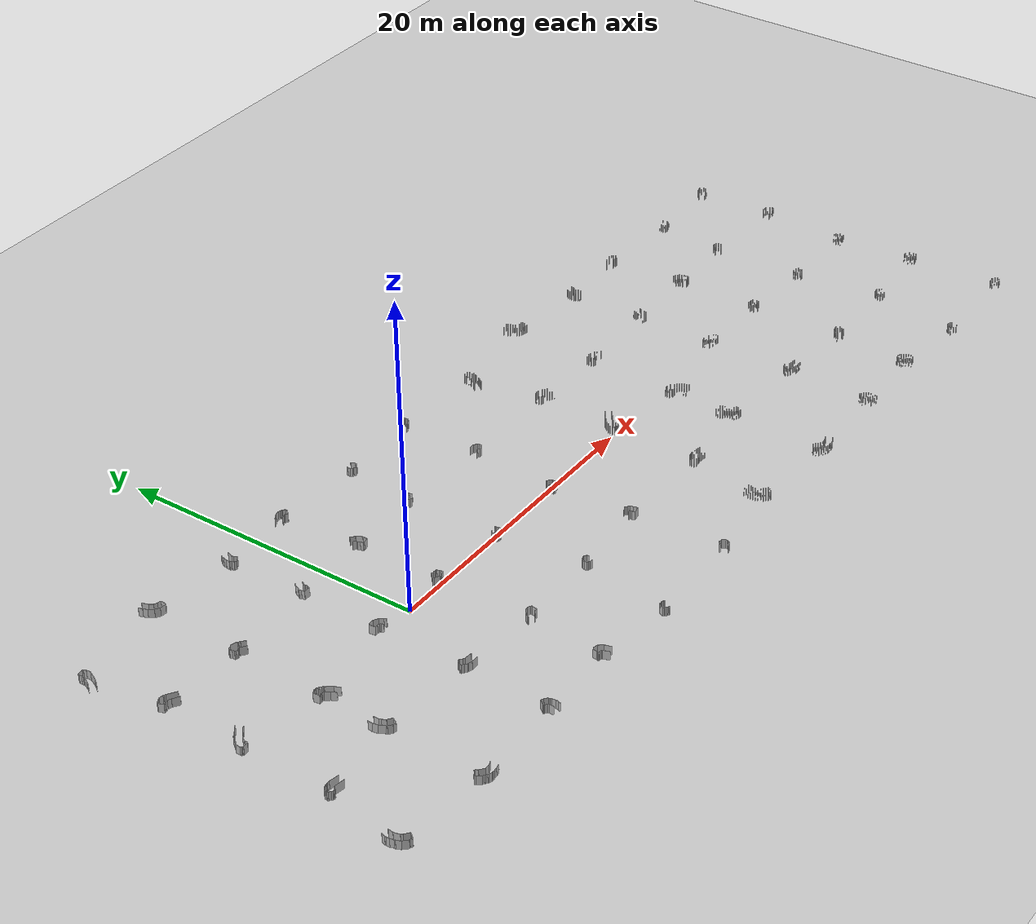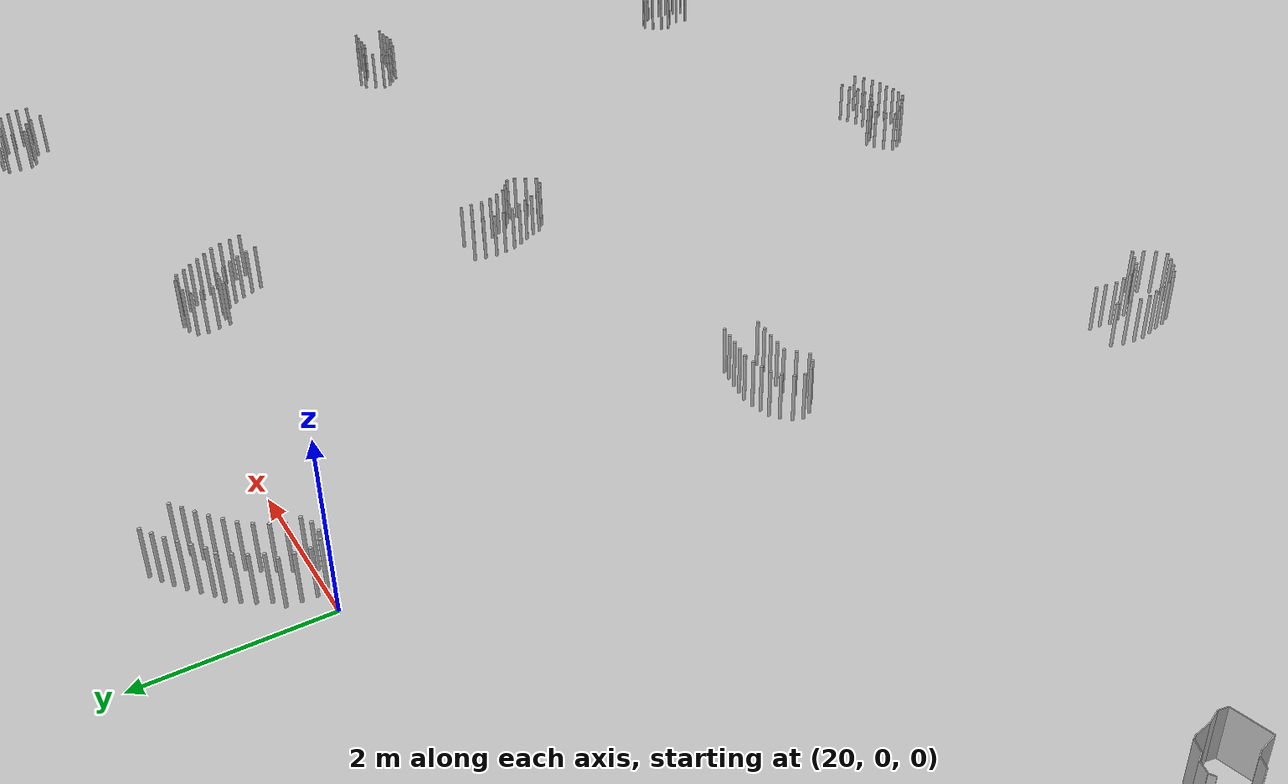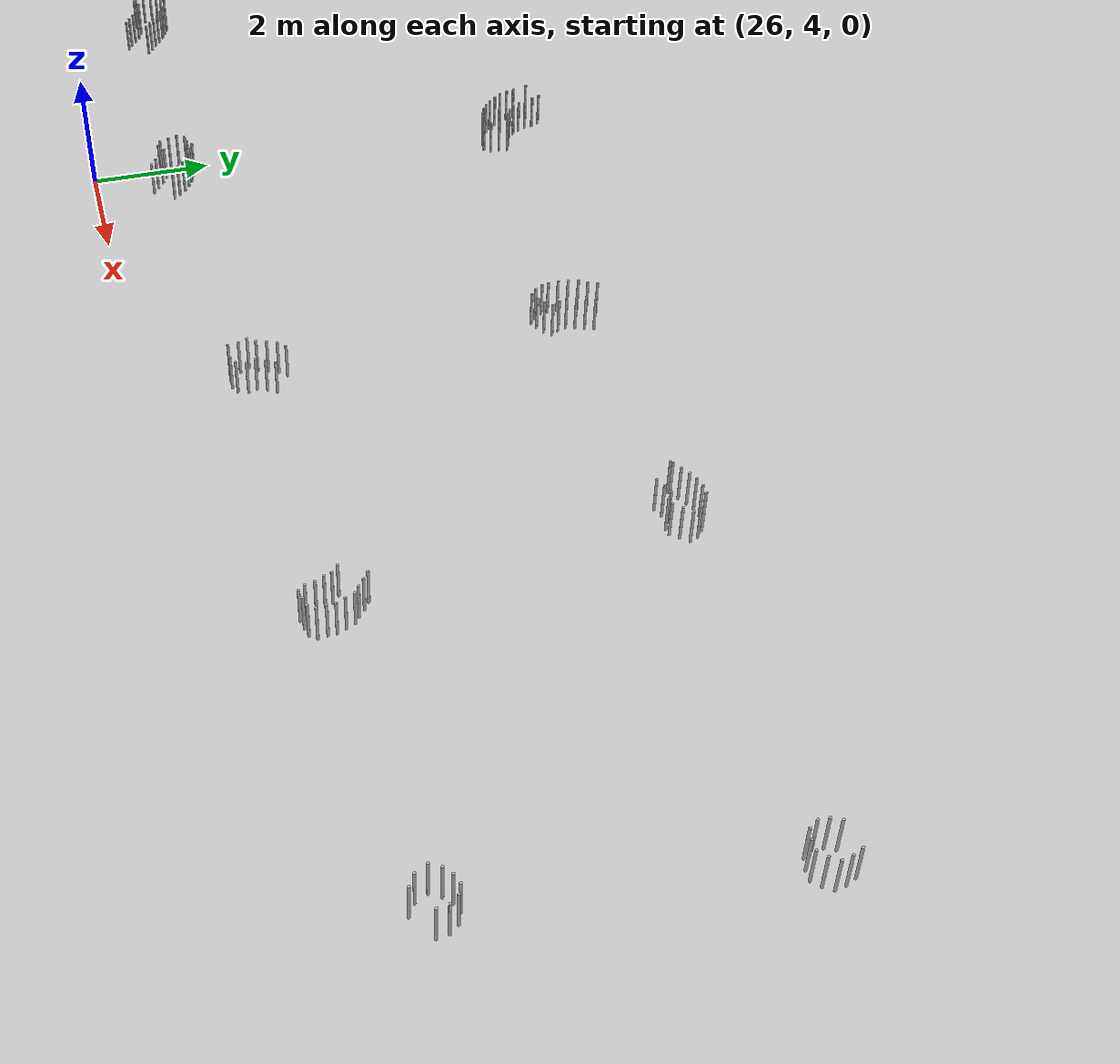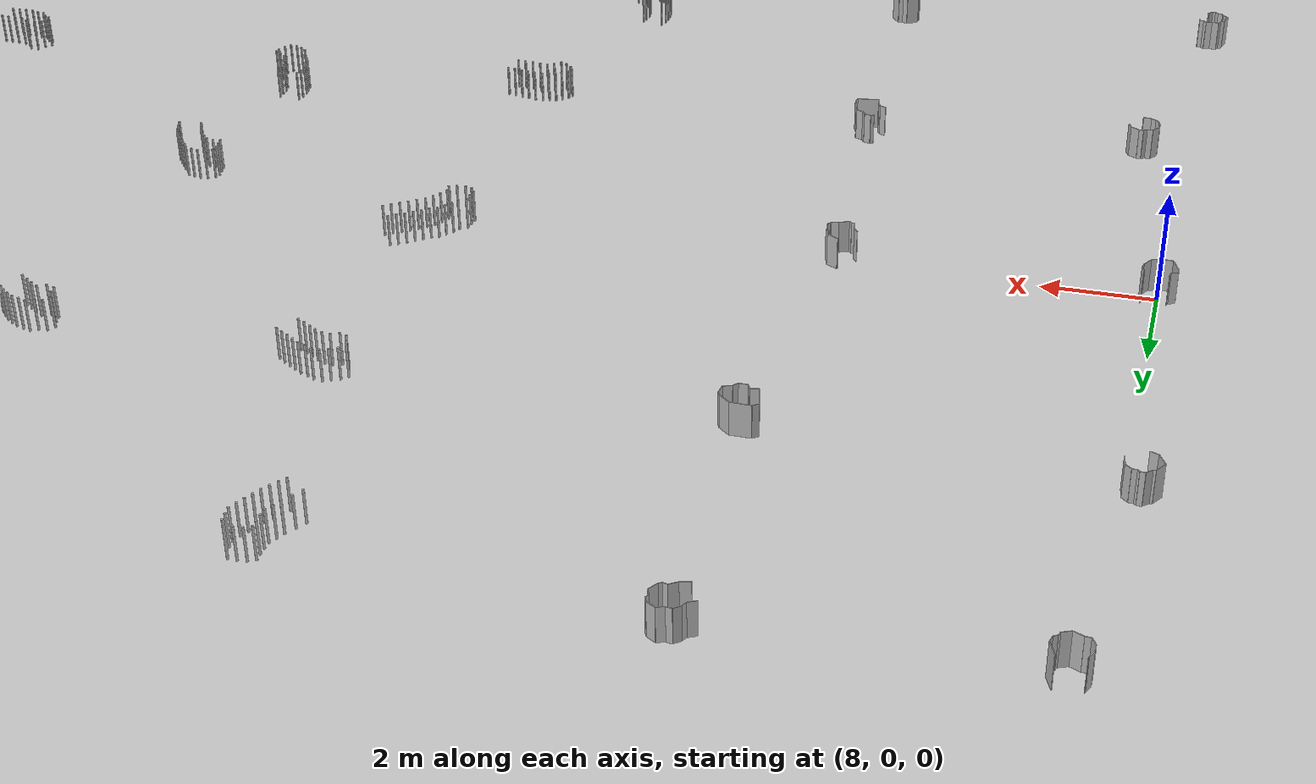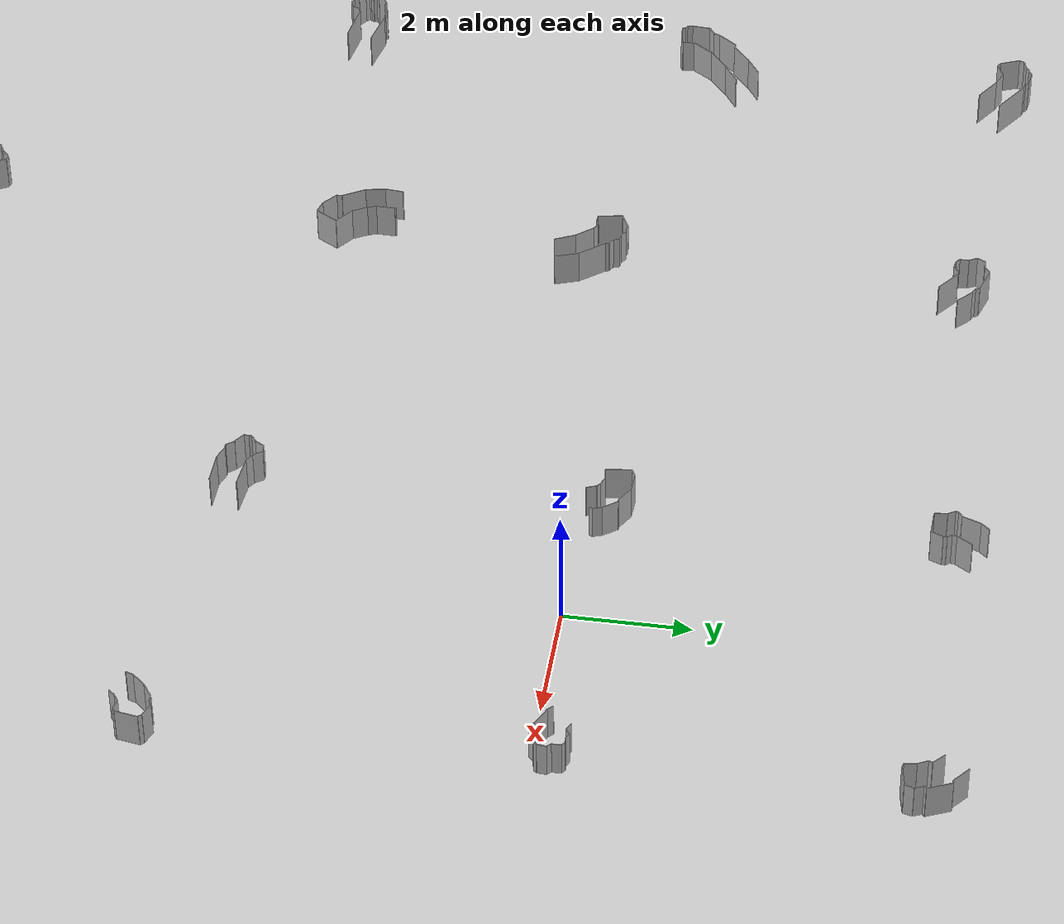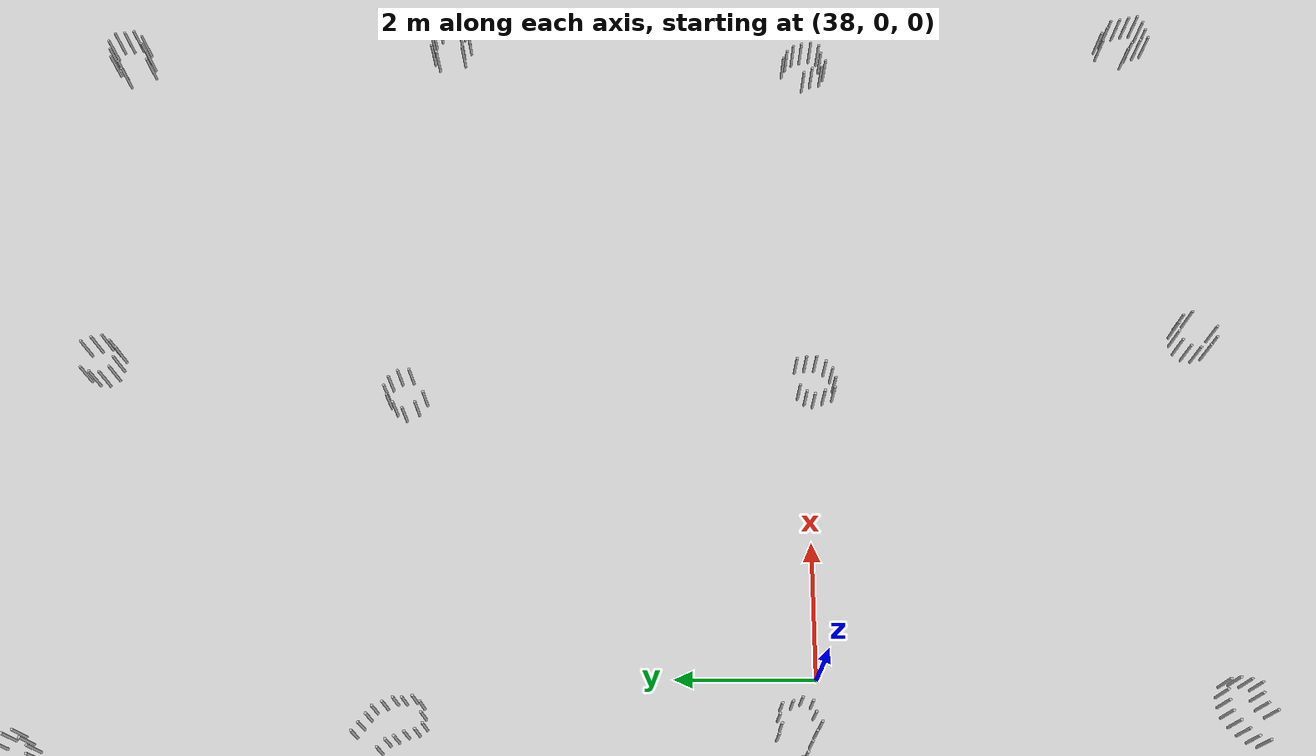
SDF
<?xml version='1.0' encoding='utf-8'?>
<sdf version="1.6"><world name="all_training"><model name="all_walls_and_cylinders"><static>true</static><link name="single_link"><sensor name="sensor_contact" type="contact"><contact><always_on>1</always_on><update_rate>50</update_rate><collision>cfg1_wall1_col</collision><collision>cfg1_wall2_col</collision><collision>cfg1_wall3_col</collision><collision>cfg1_wall4_col</collision><collision>cfg1_wall5_col</collision><collision>cfg1_wall6_col</collision><collision>cfg1_wall7_col</collision><collision>cfg1_wall8_col</collision><collision>cfg1_wall9_col</collision><collision>cfg1_wall10_col</collision><collision>cfg1_wall11_col</collision><collision>cfg1_wall12_col</collision><collision>cfg1_wall13_col</collision><collision>cfg1_wall14_col</collision><collision>cfg1_wall15_col</collision><collision>cfg1_wall16_col</collision><collision>cfg1_wall17_col</collision><collision>cfg1_wall18_col</collision><collision>cfg2_wall1_col</collision><collision>cfg2_wall2_col</collision><collision>cfg2_wall3_col</collision><collision>cfg2_wall4_col</collision><collision>cfg2_wall5_col</collision><collision>cfg2_wall6_col</collision><collision>cfg2_wall7_col</collision><collision>cfg2_wall8_col</collision><collision>cfg2_wall9_col</collision><collision>cfg2_wall10_col</collision><collision>cfg2_wall11_col</collision><collision>cfg2_wall12_col</collision><collision>cfg2_wall13_col</collision><collision>cfg2_wall14_col</collision><collision>cfg2_wall15_col</collision><collision>cfg2_wall16_col</collision><collision>cfg2_wall17_col</collision><collision>cfg2_wall18_col</collision><collision>cfg2_wall19_col</collision><collision>cfg2_wall20_col</collision><collision>cfg2_wall21_col</collision><collision>cfg2_wall22_col</collision><collision>cfg2_wall23_col</collision><collision>cfg3_wall1_col</collision><collision>cfg3_wall2_col</collision><collision>cfg3_wall3_col</collision><collision>cfg3_wall4_col</collision><collision>cfg3_wall5_col</collision><collision>cfg3_wall6_col</collision><collision>cfg3_wall7_col</collision><collision>cfg3_wall8_col</collision><collision>cfg3_wall9_col</collision><collision>cfg3_wall10_col</collision><collision>cfg3_wall11_col</collision><collision>cfg3_wall12_col</collision><collision>cfg3_wall13_col</collision><collision>cfg3_wall14_col</collision><collision>cfg3_wall15_col</collision><collision>cfg3_wall16_col</collision><collision>cfg3_wall17_col</collision><collision>cfg3_wall18_col</collision><collision>cfg4_wall1_col</collision><collision>cfg4_wall2_col</collision><collision>cfg4_wall3_col</collision><collision>cfg4_wall4_col</collision><collision>cfg4_wall5_col</collision><collision>cfg4_wall6_col</collision><collision>cfg4_wall7_col</collision><collision>cfg4_wall8_col</collision><collision>cfg4_wall9_col</collision><collision>cfg4_wall10_col</collision><collision>cfg4_wall11_col</collision><collision>cfg4_wall12_col</collision><collision>cfg4_wall13_col</collision><collision>cfg4_wall14_col</collision><collision>cfg4_wall15_col</collision><collision>cfg4_wall16_col</collision><collision>cfg5_wall1_col</collision><collision>cfg5_wall2_col</collision><collision>cfg5_wall3_col</collision><collision>cfg5_wall4_col</collision><collision>cfg5_wall5_col</collision><collision>cfg5_wall6_col</collision><collision>cfg5_wall7_col</collision><collision>cfg5_wall8_col</collision><collision>cfg5_wall9_col</collision><collision>cfg5_wall10_col</collision><collision>cfg5_wall11_col</collision><collision>cfg5_wall12_col</collision><collision>cfg5_wall13_col</collision><collision>cfg5_wall14_col</collision><collision>cfg6_wall1_col</collision><collision>cfg6_wall2_col</collision><collision>cfg6_wall3_col</collision><collision>cfg6_wall4_col</collision><collision>cfg6_wall5_col</collision><collision>cfg6_wall6_col</collision><collision>cfg6_wall7_col</collision><collision>cfg6_wall8_col</collision><collision>cfg6_wall9_col</collision><collision>cfg6_wall10_col</collision><collision>cfg6_wall11_col</collision><collision>cfg6_wall12_col</collision><collision>cfg6_wall13_col</collision><collision>cfg6_wall14_col</collision><collision>cfg6_wall15_col</collision><collision>cfg6_wall16_col</collision><collision>cfg6_wall17_col</collision><collision>cfg6_wall18_col</collision><collision>cfg6_wall19_col</collision><collision>cfg6_wall20_col</collision><collision>cfg6_wall21_col</collision><collision>cfg6_wall22_col</collision><collision>cfg6_wall23_col</collision><collision>cfg7_wall1_col</collision><collision>cfg7_wall2_col</collision><collision>cfg7_wall3_col</collision><collision>cfg7_wall4_col</collision><collision>cfg7_wall5_col</collision><collision>cfg7_wall6_col</collision><collision>cfg7_wall7_col</collision><collision>cfg7_wall8_col</collision><collision>cfg7_wall9_col</collision><collision>cfg7_wall10_col</collision><collision>cfg7_wall11_col</collision><collision>cfg7_wall12_col</collision><collision>cfg7_wall13_col</collision><collision>cfg8_wall1_col</collision><collision>cfg8_wall2_col</collision><collision>cfg8_wall3_col</collision><collision>cfg8_wall4_col</collision><collision>cfg8_wall5_col</collision><collision>cfg8_wall6_col</collision><collision>cfg8_wall7_col</collision><collision>cfg8_wall8_col</collision><collision>cfg8_wall9_col</collision><collision>cfg8_wall10_col</collision><collision>cfg8_wall11_col</collision><collision>cfg8_wall12_col</collision><collision>cfg8_wall13_col</collision><collision>cfg8_wall14_col</collision><collision>cfg8_wall15_col</collision><collision>cfg8_wall16_col</collision><collision>cfg8_wall17_col</collision><collision>cfg8_wall18_col</collision><collision>cfg9_wall1_col</collision><collision>cfg9_wall2_col</collision><collision>cfg9_wall3_col</collision><collision>cfg9_wall4_col</collision><collision>cfg9_wall5_col</collision><collision>cfg9_wall6_col</collision><collision>cfg9_wall7_col</collision><collision>cfg9_wall8_col</collision><collision>cfg9_wall9_col</collision><collision>cfg9_wall10_col</collision><collision>cfg9_wall11_col</collision><collision>cfg9_wall12_col</collision><collision>cfg9_wall13_col</collision><collision>cfg9_wall14_col</collision><collision>cfg9_wall15_col</collision><collision>cfg9_wall16_col</collision><collision>cfg10_wall1_col</collision><collision>cfg10_wall2_col</collision><collision>cfg10_wall3_col</collision><collision>cfg10_wall4_col</collision><collision>cfg10_wall5_col</collision><collision>cfg10_wall6_col</collision><collision>cfg10_wall7_col</collision><collision>cfg10_wall8_col</collision><collision>cfg10_wall9_col</collision><collision>cfg10_wall10_col</collision><collision>cfg10_wall11_col</collision><collision>cfg10_wall12_col</collision><collision>cfg10_wall13_col</collision><collision>cfg11_wall1_col</collision><collision>cfg11_wall2_col</collision><collision>cfg11_wall3_col</collision><collision>cfg11_wall4_col</collision><collision>cfg11_wall5_col</collision><collision>cfg11_wall6_col</collision><collision>cfg11_wall7_col</collision><collision>cfg11_wall8_col</collision><collision>cfg11_wall9_col</collision><collision>cfg11_wall10_col</collision><collision>cfg11_wall11_col</collision><collision>cfg11_wall12_col</collision><collision>cfg11_wall13_col</collision><collision>cfg11_wall14_col</collision><collision>cfg11_wall15_col</collision><collision>cfg11_wall16_col</collision><collision>cfg12_wall1_col</collision><collision>cfg12_wall2_col</collision><collision>cfg12_wall3_col</collision><collision>cfg12_wall4_col</collision><collision>cfg12_wall5_col</collision><collision>cfg12_wall6_col</collision><collision>cfg12_wall7_col</collision><collision>cfg12_wall8_col</collision><collision>cfg12_wall9_col</collision><collision>cfg12_wall10_col</collision><collision>cfg12_wall11_col</collision><collision>cfg12_wall12_col</collision><collision>cfg12_wall13_col</collision><collision>cfg12_wall14_col</collision><collision>cfg12_wall15_col</collision><collision>cfg13_wall1_col</collision><collision>cfg13_wall2_col</collision><collision>cfg13_wall3_col</collision><collision>cfg13_wall4_col</collision><collision>cfg13_wall5_col</collision><collision>cfg13_wall6_col</collision><collision>cfg13_wall7_col</collision><collision>cfg13_wall8_col</collision><collision>cfg13_wall9_col</collision><collision>cfg13_wall10_col</collision><collision>cfg13_wall11_col</collision><collision>cfg13_wall12_col</collision><collision>cfg13_wall13_col</collision><collision>cfg13_wall14_col</collision><collision>cfg13_wall15_col</collision><collision>cfg14_wall1_col</collision><collision>cfg14_wall2_col</collision><collision>cfg14_wall3_col</collision><collision>cfg14_wall4_col</collision><collision>cfg14_wall5_col</collision><collision>cfg14_wall6_col</collision><collision>cfg14_wall7_col</collision><collision>cfg14_wall8_col</collision><collision>cfg14_wall9_col</collision><collision>cfg14_wall10_col</collision><collision>cfg14_wall11_col</collision><collision>cfg14_wall12_col</collision><collision>cfg14_wall13_col</collision><collision>cfg14_wall14_col</collision><collision>cfg15_wall1_col</collision><collision>cfg15_wall2_col</collision><collision>cfg15_wall3_col</collision><collision>cfg15_wall4_col</collision><collision>cfg15_wall5_col</collision><collision>cfg15_wall6_col</collision><collision>cfg15_wall7_col</collision><collision>cfg15_wall8_col</collision><collision>cfg15_wall9_col</collision><collision>cfg15_wall10_col</collision><collision>cfg15_wall11_col</collision><collision>cfg15_wall12_col</collision><collision>cfg15_wall13_col</collision><collision>cfg15_wall14_col</collision><collision>cfg15_wall15_col</collision><collision>cfg15_wall16_col</collision><collision>cfg16_wall1_col</collision><collision>cfg16_wall2_col</collision><collision>cfg16_wall3_col</collision><collision>cfg16_wall4_col</collision><collision>cfg16_wall5_col</collision><collision>cfg16_wall6_col</collision><collision>cfg16_wall7_col</collision><collision>cfg16_wall8_col</collision><collision>cfg16_wall9_col</collision><collision>cfg16_wall10_col</collision><collision>cfg16_wall11_col</collision><collision>cfg16_wall12_col</collision><collision>cfg16_wall13_col</collision><collision>cfg17_wall1_col</collision><collision>cfg17_wall2_col</collision><collision>cfg17_wall3_col</collision><collision>cfg17_wall4_col</collision><collision>cfg17_wall5_col</collision><collision>cfg17_wall6_col</collision><collision>cfg17_wall7_col</collision><collision>cfg17_wall8_col</collision><collision>cfg17_wall9_col</collision><collision>cfg17_wall10_col</collision><collision>cfg17_wall11_col</collision><collision>cfg17_wall12_col</collision><collision>cfg17_wall13_col</collision><collision>cfg18_wall1_col</collision><collision>cfg18_wall2_col</collision><collision>cfg18_wall3_col</collision><collision>cfg18_wall4_col</collision><collision>cfg18_wall5_col</collision><collision>cfg18_wall6_col</collision><collision>cfg18_wall7_col</collision><collision>cfg18_wall8_col</collision><collision>cfg18_wall9_col</collision><collision>cfg18_wall10_col</collision><collision>cfg18_wall11_col</collision><collision>cfg18_wall12_col</collision><collision>cfg18_wall13_col</collision><collision>cfg18_wall14_col</collision><collision>cfg18_wall15_col</collision><collision>cfg18_wall16_col</collision><collision>cfg19_wall1_col</collision><collision>cfg19_wall2_col</collision><collision>cfg19_wall3_col</collision><collision>cfg19_wall4_col</collision><collision>cfg19_wall5_col</collision><collision>cfg19_wall6_col</collision><collision>cfg19_wall7_col</collision><collision>cfg19_wall8_col</collision><collision>cfg19_wall9_col</collision><collision>cfg19_wall10_col</collision><collision>cfg19_wall11_col</collision><collision>cfg19_wall12_col</collision><collision>cfg19_wall13_col</collision><collision>cfg20_wall1_col</collision><collision>cfg20_wall2_col</collision><collision>cfg20_wall3_col</collision><collision>cfg20_wall4_col</collision><collision>cfg20_wall5_col</collision><collision>cfg20_wall6_col</collision><collision>cfg20_wall7_col</collision><collision>cfg20_wall8_col</collision><collision>cfg20_wall9_col</collision><collision>cfg20_wall10_col</collision><collision>cfg20_wall11_col</collision><collision>cfg20_wall12_col</collision><collision>cfg20_wall13_col</collision><collision>cfg20_wall14_col</collision><collision>cfg21_wall1_col</collision><collision>cfg21_wall2_col</collision><collision>cfg21_wall3_col</collision><collision>cfg21_wall4_col</collision><collision>cfg21_wall5_col</collision><collision>cfg21_wall6_col</collision><collision>cfg21_wall7_col</collision><collision>cfg21_wall8_col</collision><collision>cfg21_wall9_col</collision><collision>cfg21_wall10_col</collision><collision>cfg21_wall11_col</collision><collision>cfg21_wall12_col</collision><collision>cfg21_wall13_col</collision><collision>cfg21_wall14_col</collision><collision>cfg21_wall15_col</collision><collision>cfg21_wall16_col</collision><collision>cfg22_wall1_col</collision><collision>cfg22_wall2_col</collision><collision>cfg22_wall3_col</collision><collision>cfg22_wall4_col</collision><collision>cfg22_wall5_col</collision><collision>cfg22_wall6_col</collision><collision>cfg22_wall7_col</collision><collision>cfg22_wall8_col</collision><collision>cfg22_wall9_col</collision><collision>cfg22_wall10_col</collision><collision>cfg22_wall11_col</collision><collision>cfg22_wall12_col</collision><collision>cfg23_wall1_col</collision><collision>cfg23_wall2_col</collision><collision>cfg23_wall3_col</collision><collision>cfg23_wall4_col</collision><collision>cfg23_wall5_col</collision><collision>cfg23_wall6_col</collision><collision>cfg23_wall7_col</collision><collision>cfg23_wall8_col</collision><collision>cfg23_wall9_col</collision><collision>cfg23_wall10_col</collision><collision>cfg23_wall11_col</collision><collision>cfg24_wall1_col</collision><collision>cfg24_wall2_col</collision><collision>cfg24_wall3_col</collision><collision>cfg24_wall4_col</collision><collision>cfg24_wall5_col</collision><collision>cfg24_wall6_col</collision><collision>cfg24_wall7_col</collision><collision>cfg24_wall8_col</collision><collision>cfg24_wall9_col</collision><collision>cfg24_wall10_col</collision><collision>cfg25_wall1_col</collision><collision>cfg25_wall2_col</collision><collision>cfg25_wall3_col</collision><collision>cfg25_wall4_col</collision><collision>cfg25_wall5_col</collision><collision>cfg25_wall6_col</collision><collision>cfg25_wall7_col</collision><collision>cfg25_wall8_col</collision><collision>cfg25_wall9_col</collision><collision>cfg25_wall10_col</collision><collision>cfg25_wall11_col</collision><collision>cfg25_wall12_col</collision><collision>cfg26_wall1_col</collision><collision>cfg26_wall2_col</collision><collision>cfg26_wall3_col</collision><collision>cfg26_wall4_col</collision><collision>cfg26_wall5_col</collision><collision>cfg26_wall6_col</collision><collision>cfg26_wall7_col</collision><collision>cfg26_wall8_col</collision><collision>cfg26_wall9_col</collision><collision>cfg26_wall10_col</collision><collision>cfg26_wall11_col</collision><collision>cfg26_wall12_col</collision><collision>cfg26_wall13_col</collision><collision>cfg27_wall1_col</collision><collision>cfg27_wall2_col</collision><collision>cfg27_wall3_col</collision><collision>cfg27_wall4_col</collision><collision>cfg27_wall5_col</collision><collision>cfg27_wall6_col</collision><collision>cfg27_wall7_col</collision><collision>cfg27_wall8_col</collision><collision>cfg27_wall9_col</collision><collision>cfg27_wall10_col</collision><collision>cfg27_wall11_col</collision><collision>cfg27_wall12_col</collision><collision>cfg27_wall13_col</collision><collision>cfg27_wall14_col</collision><collision>cfg28_wall1_col</collision><collision>cfg28_wall2_col</collision><collision>cfg28_wall3_col</collision><collision>cfg28_wall4_col</collision><collision>cfg28_wall5_col</collision><collision>cfg28_wall6_col</collision><collision>cfg28_wall7_col</collision><collision>cfg28_wall8_col</collision><collision>cfg28_wall9_col</collision><collision>cfg28_wall10_col</collision><collision>cfg28_wall11_col</collision><collision>cfg28_wall12_col</collision><collision>cfg28_wall13_col</collision><collision>cfg28_wall14_col</collision><collision>cfg29_wall1_col</collision><collision>cfg29_wall2_col</collision><collision>cfg29_wall3_col</collision><collision>cfg29_wall4_col</collision><collision>cfg29_wall5_col</collision><collision>cfg29_wall6_col</collision><collision>cfg29_wall7_col</collision><collision>cfg29_wall8_col</collision><collision>cfg29_wall9_col</collision><collision>cfg29_wall10_col</collision><collision>cfg29_wall11_col</collision><collision>cfg29_wall12_col</collision><collision>cfg30_wall1_col</collision><collision>cfg30_wall2_col</collision><collision>cfg30_wall3_col</collision><collision>cfg30_wall4_col</collision><collision>cfg30_wall5_col</collision><collision>cfg30_wall6_col</collision><collision>cfg30_wall7_col</collision><collision>cfg30_wall8_col</collision><collision>cfg30_wall9_col</collision><collision>cfg30_wall10_col</collision><collision>cfg30_wall11_col</collision><collision>cfg30_wall12_col</collision><collision>cfg30_wall13_col</collision><collision>cfg30_wall14_col</collision><collision>cfg30_wall15_col</collision><collision>cfg30_wall16_col</collision><collision>cfg31_cyl1_col</collision><collision>cfg31_cyl2_col</collision><collision>cfg31_cyl3_col</collision><collision>cfg31_cyl4_col</collision><collision>cfg31_cyl5_col</collision><collision>cfg31_cyl6_col</collision><collision>cfg31_cyl7_col</collision><collision>cfg31_cyl8_col</collision><collision>cfg31_cyl9_col</collision><collision>cfg31_cyl10_col</collision><collision>cfg31_cyl11_col</collision><collision>cfg31_cyl12_col</collision><collision>cfg31_cyl13_col</collision><collision>cfg31_cyl14_col</collision><collision>cfg31_cyl15_col</collision><collision>cfg31_cyl16_col</collision><collision>cfg31_cyl17_col</collision><collision>cfg31_cyl18_col</collision><collision>cfg31_cyl19_col</collision><collision>cfg31_cyl20_col</collision><collision>cfg31_cyl21_col</collision><collision>cfg31_cyl22_col</collision><collision>cfg31_cyl23_col</collision><collision>cfg31_cyl24_col</collision><collision>cfg32_cyl1_col</collision><collision>cfg32_cyl2_col</collision><collision>cfg32_cyl3_col</collision><collision>cfg32_cyl4_col</collision><collision>cfg32_cyl5_col</collision><collision>cfg32_cyl6_col</collision><collision>cfg32_cyl7_col</collision><collision>cfg32_cyl8_col</collision><collision>cfg32_cyl9_col</collision><collision>cfg32_cyl10_col</collision><collision>cfg32_cyl11_col</collision><collision>cfg32_cyl12_col</collision><collision>cfg32_cyl13_col</collision><collision>cfg32_cyl14_col</collision><collision>cfg32_cyl15_col</collision><collision>cfg32_cyl16_col</collision><collision>cfg32_cyl17_col</collision><collision>cfg32_cyl18_col</collision><collision>cfg32_cyl19_col</collision><collision>cfg32_cyl20_col</collision><collision>cfg32_cyl21_col</collision><collision>cfg33_cyl1_col</collision><collision>cfg33_cyl2_col</collision><collision>cfg33_cyl3_col</collision><collision>cfg33_cyl4_col</collision><collision>cfg33_cyl5_col</collision><collision>cfg33_cyl6_col</collision><collision>cfg33_cyl7_col</collision><collision>cfg33_cyl8_col</collision><collision>cfg33_cyl9_col</collision><collision>cfg33_cyl10_col</collision><collision>cfg33_cyl11_col</collision><collision>cfg33_cyl12_col</collision><collision>cfg33_cyl13_col</collision><collision>cfg33_cyl14_col</collision><collision>cfg33_cyl15_col</collision><collision>cfg33_cyl16_col</collision><collision>cfg33_cyl17_col</collision><collision>cfg33_cyl18_col</collision><collision>cfg33_cyl19_col</collision><collision>cfg33_cyl20_col</collision><collision>cfg33_cyl21_col</collision><collision>cfg33_cyl22_col</collision><collision>cfg33_cyl23_col</collision><collision>cfg33_cyl24_col</collision><collision>cfg33_cyl25_col</collision><collision>cfg33_cyl26_col</collision><collision>cfg33_cyl27_col</collision><collision>cfg34_cyl1_col</collision><collision>cfg34_cyl2_col</collision><collision>cfg34_cyl3_col</collision><collision>cfg34_cyl4_col</collision><collision>cfg34_cyl5_col</collision><collision>cfg34_cyl6_col</collision><collision>cfg34_cyl7_col</collision><collision>cfg34_cyl8_col</collision><collision>cfg34_cyl9_col</collision><collision>cfg34_cyl10_col</collision><collision>cfg34_cyl11_col</collision><collision>cfg34_cyl12_col</collision><collision>cfg34_cyl13_col</collision><collision>cfg34_cyl14_col</collision><collision>cfg34_cyl15_col</collision><collision>cfg34_cyl16_col</collision><collision>cfg34_cyl17_col</collision><collision>cfg34_cyl18_col</collision><collision>cfg34_cyl19_col</collision><collision>cfg34_cyl20_col</collision><collision>cfg34_cyl21_col</collision><collision>cfg35_cyl1_col</collision><collision>cfg35_cyl2_col</collision><collision>cfg35_cyl3_col</collision><collision>cfg35_cyl4_col</collision><collision>cfg35_cyl5_col</collision><collision>cfg35_cyl6_col</collision><collision>cfg35_cyl7_col</collision><collision>cfg35_cyl8_col</collision><collision>cfg35_cyl9_col</collision><collision>cfg35_cyl10_col</collision><collision>cfg35_cyl11_col</collision><collision>cfg35_cyl12_col</collision><collision>cfg35_cyl13_col</collision><collision>cfg35_cyl14_col</collision><collision>cfg35_cyl15_col</collision><collision>cfg35_cyl16_col</collision><collision>cfg35_cyl17_col</collision><collision>cfg35_cyl18_col</collision><collision>cfg35_cyl19_col</collision><collision>cfg35_cyl20_col</collision><collision>cfg35_cyl21_col</collision><collision>cfg35_cyl22_col</collision><collision>cfg36_cyl1_col</collision><collision>cfg36_cyl2_col</collision><collision>cfg36_cyl3_col</collision><collision>cfg36_cyl4_col</collision><collision>cfg36_cyl5_col</collision><collision>cfg36_cyl6_col</collision><collision>cfg36_cyl7_col</collision><collision>cfg36_cyl8_col</collision><collision>cfg36_cyl9_col</collision><collision>cfg36_cyl10_col</collision><collision>cfg36_cyl11_col</collision><collision>cfg36_cyl12_col</collision><collision>cfg36_cyl13_col</collision><collision>cfg36_cyl14_col</collision><collision>cfg36_cyl15_col</collision><collision>cfg36_cyl16_col</collision><collision>cfg36_cyl17_col</collision><collision>cfg36_cyl18_col</collision><collision>cfg36_cyl19_col</collision><collision>cfg36_cyl20_col</collision><collision>cfg36_cyl21_col</collision><collision>cfg36_cyl22_col</collision><collision>cfg36_cyl23_col</collision><collision>cfg36_cyl24_col</collision><collision>cfg36_cyl25_col</collision><collision>cfg37_cyl1_col</collision><collision>cfg37_cyl2_col</collision><collision>cfg37_cyl3_col</collision><collision>cfg37_cyl4_col</collision><collision>cfg37_cyl5_col</collision><collision>cfg37_cyl6_col</collision><collision>cfg37_cyl7_col</collision><collision>cfg37_cyl8_col</collision><collision>cfg37_cyl9_col</collision><collision>cfg37_cyl10_col</collision><collision>cfg37_cyl11_col</collision><collision>cfg37_cyl12_col</collision><collision>cfg37_cyl13_col</collision><collision>cfg37_cyl14_col</collision><collision>cfg37_cyl15_col</collision><collision>cfg37_cyl16_col</collision><collision>cfg37_cyl17_col</collision><collision>cfg37_cyl18_col</collision><collision>cfg37_cyl19_col</collision><collision>cfg37_cyl20_col</collision><collision>cfg37_cyl21_col</collision><collision>cfg37_cyl22_col</collision><collision>cfg37_cyl23_col</collision><collision>cfg38_cyl1_col</collision><collision>cfg38_cyl2_col</collision><collision>cfg38_cyl3_col</collision><collision>cfg38_cyl4_col</collision><collision>cfg38_cyl5_col</collision><collision>cfg38_cyl6_col</collision><collision>cfg38_cyl7_col</collision><collision>cfg38_cyl8_col</collision><collision>cfg38_cyl9_col</collision><collision>cfg38_cyl10_col</collision><collision>cfg38_cyl11_col</collision><collision>cfg38_cyl12_col</collision><collision>cfg38_cyl13_col</collision><collision>cfg38_cyl14_col</collision><collision>cfg38_cyl15_col</collision><collision>cfg38_cyl16_col</collision><collision>cfg38_cyl17_col</collision><collision>cfg38_cyl18_col</collision><collision>cfg38_cyl19_col</collision><collision>cfg38_cyl20_col</collision><collision>cfg38_cyl21_col</collision><collision>cfg38_cyl22_col</collision><collision>cfg38_cyl23_col</collision><collision>cfg38_cyl24_col</collision><collision>cfg39_cyl1_col</collision><collision>cfg39_cyl2_col</collision><collision>cfg39_cyl3_col</collision><collision>cfg39_cyl4_col</collision><collision>cfg39_cyl5_col</collision><collision>cfg39_cyl6_col</collision><collision>cfg39_cyl7_col</collision><collision>cfg39_cyl8_col</collision><collision>cfg39_cyl9_col</collision><collision>cfg39_cyl10_col</collision><collision>cfg39_cyl11_col</collision><collision>cfg39_cyl12_col</collision><collision>cfg39_cyl13_col</collision><collision>cfg39_cyl14_col</collision><collision>cfg39_cyl15_col</collision><collision>cfg39_cyl16_col</collision><collision>cfg39_cyl17_col</collision><collision>cfg39_cyl18_col</collision><collision>cfg40_cyl1_col</collision><collision>cfg40_cyl2_col</collision><collision>cfg40_cyl3_col</collision><collision>cfg40_cyl4_col</collision><collision>cfg40_cyl5_col</collision><collision>cfg40_cyl6_col</collision><collision>cfg40_cyl7_col</collision><collision>cfg40_cyl8_col</collision><collision>cfg40_cyl9_col</collision><collision>cfg40_cyl10_col</collision><collision>cfg40_cyl11_col</collision><collision>cfg40_cyl12_col</collision><collision>cfg40_cyl13_col</collision><collision>cfg40_cyl14_col</collision><collision>cfg40_cyl15_col</collision><collision>cfg40_cyl16_col</collision><collision>cfg40_cyl17_col</collision><collision>cfg40_cyl18_col</collision><collision>cfg40_cyl19_col</collision><collision>cfg40_cyl20_col</collision><collision>cfg40_cyl21_col</collision><collision>cfg40_cyl22_col</collision><collision>cfg40_cyl23_col</collision><collision>cfg41_cyl1_col</collision><collision>cfg41_cyl2_col</collision><collision>cfg41_cyl3_col</collision><collision>cfg41_cyl4_col</collision><collision>cfg41_cyl5_col</collision><collision>cfg41_cyl6_col</collision><collision>cfg41_cyl7_col</collision><collision>cfg41_cyl8_col</collision><collision>cfg41_cyl9_col</collision><collision>cfg41_cyl10_col</collision><collision>cfg41_cyl11_col</collision><collision>cfg41_cyl12_col</collision><collision>cfg41_cyl13_col</collision><collision>cfg41_cyl14_col</collision><collision>cfg41_cyl15_col</collision><collision>cfg41_cyl16_col</collision><collision>cfg42_cyl1_col</collision><collision>cfg42_cyl2_col</collision><collision>cfg42_cyl3_col</collision><collision>cfg42_cyl4_col</collision><collision>cfg42_cyl5_col</collision><collision>cfg42_cyl6_col</collision><collision>cfg42_cyl7_col</collision><collision>cfg42_cyl8_col</collision><collision>cfg42_cyl9_col</collision><collision>cfg42_cyl10_col</collision><collision>cfg42_cyl11_col</collision><collision>cfg42_cyl12_col</collision><collision>cfg42_cyl13_col</collision><collision>cfg42_cyl14_col</collision><collision>cfg42_cyl15_col</collision><collision>cfg42_cyl16_col</collision><collision>cfg42_cyl17_col</collision><collision>cfg42_cyl18_col</collision><collision>cfg43_cyl1_col</collision><collision>cfg43_cyl2_col</collision><collision>cfg43_cyl3_col</collision><collision>cfg43_cyl4_col</collision><collision>cfg43_cyl5_col</collision><collision>cfg43_cyl6_col</collision><collision>cfg43_cyl7_col</collision><collision>cfg43_cyl8_col</collision><collision>cfg43_cyl9_col</collision><collision>cfg43_cyl10_col</collision><collision>cfg43_cyl11_col</collision><collision>cfg43_cyl12_col</collision><collision>cfg43_cyl13_col</collision><collision>cfg43_cyl14_col</collision><collision>cfg43_cyl15_col</collision><collision>cfg43_cyl16_col</collision><collision>cfg44_cyl1_col</collision><collision>cfg44_cyl2_col</collision><collision>cfg44_cyl3_col</collision><collision>cfg44_cyl4_col</collision><collision>cfg44_cyl5_col</collision><collision>cfg44_cyl6_col</collision><collision>cfg44_cyl7_col</collision><collision>cfg44_cyl8_col</collision><collision>cfg44_cyl9_col</collision><collision>cfg44_cyl10_col</collision><collision>cfg44_cyl11_col</collision><collision>cfg44_cyl12_col</collision><collision>cfg44_cyl13_col</collision><collision>cfg44_cyl14_col</collision><collision>cfg44_cyl15_col</collision><collision>cfg45_cyl1_col</collision><collision>cfg45_cyl2_col</collision><collision>cfg45_cyl3_col</collision><collision>cfg45_cyl4_col</collision><collision>cfg45_cyl5_col</collision><collision>cfg45_cyl6_col</collision><collision>cfg45_cyl7_col</collision><collision>cfg45_cyl8_col</collision><collision>cfg45_cyl9_col</collision><collision>cfg45_cyl10_col</collision><collision>cfg45_cyl11_col</collision><collision>cfg45_cyl12_col</collision><collision>cfg45_cyl13_col</collision><collision>cfg45_cyl14_col</collision><collision>cfg45_cyl15_col</collision><collision>cfg45_cyl16_col</collision><collision>cfg45_cyl17_col</collision><collision>cfg45_cyl18_col</collision><collision>cfg46_cyl1_col</collision><collision>cfg46_cyl2_col</collision><collision>cfg46_cyl3_col</collision><collision>cfg46_cyl4_col</collision><collision>cfg46_cyl5_col</collision><collision>cfg46_cyl6_col</collision><collision>cfg46_cyl7_col</collision><collision>cfg46_cyl8_col</collision><collision>cfg46_cyl9_col</collision><collision>cfg46_cyl10_col</collision><collision>cfg46_cyl11_col</collision><collision>cfg46_cyl12_col</collision><collision>cfg46_cyl13_col</collision><collision>cfg46_cyl14_col</collision><collision>cfg46_cyl15_col</collision><collision>cfg46_cyl16_col</collision><collision>cfg46_cyl17_col</collision><collision>cfg47_cyl1_col</collision><collision>cfg47_cyl2_col</collision><collision>cfg47_cyl3_col</collision><collision>cfg47_cyl4_col</collision><collision>cfg47_cyl5_col</collision><collision>cfg47_cyl6_col</collision><collision>cfg47_cyl7_col</collision><collision>cfg47_cyl8_col</collision><collision>cfg47_cyl9_col</collision><collision>cfg47_cyl10_col</collision><collision>cfg47_cyl11_col</collision><collision>cfg47_cyl12_col</collision><collision>cfg47_cyl13_col</collision><collision>cfg47_cyl14_col</collision><collision>cfg47_cyl15_col</collision><collision>cfg47_cyl16_col</collision><collision>cfg48_cyl1_col</collision><collision>cfg48_cyl2_col</collision><collision>cfg48_cyl3_col</collision><collision>cfg48_cyl4_col</collision><collision>cfg48_cyl5_col</collision><collision>cfg48_cyl6_col</collision><collision>cfg48_cyl7_col</collision><collision>cfg48_cyl8_col</collision><collision>cfg48_cyl9_col</collision><collision>cfg48_cyl10_col</collision><collision>cfg48_cyl11_col</collision><collision>cfg48_cyl12_col</collision><collision>cfg48_cyl13_col</collision><collision>cfg48_cyl14_col</collision><collision>cfg49_cyl1_col</collision><collision>cfg49_cyl2_col</collision><collision>cfg49_cyl3_col</collision><collision>cfg49_cyl4_col</collision><collision>cfg49_cyl5_col</collision><collision>cfg49_cyl6_col</collision><collision>cfg49_cyl7_col</collision><collision>cfg49_cyl8_col</collision><collision>cfg49_cyl9_col</collision><collision>cfg49_cyl10_col</collision><collision>cfg49_cyl11_col</collision><collision>cfg49_cyl12_col</collision><collision>cfg49_cyl13_col</collision><collision>cfg49_cyl14_col</collision><collision>cfg49_cyl15_col</collision><collision>cfg49_cyl16_col</collision><collision>cfg50_cyl1_col</collision><collision>cfg50_cyl2_col</collision><collision>cfg50_cyl3_col</collision><collision>cfg50_cyl4_col</collision><collision>cfg50_cyl5_col</collision><collision>cfg50_cyl6_col</collision><collision>cfg50_cyl7_col</collision><collision>cfg50_cyl8_col</collision><collision>cfg50_cyl9_col</collision><collision>cfg50_cyl10_col</collision><collision>cfg50_cyl11_col</collision><collision>cfg50_cyl12_col</collision><collision>cfg50_cyl13_col</collision><collision>cfg50_cyl14_col</collision><collision>cfg50_cyl15_col</collision><collision>cfg50_cyl16_col</collision><collision>cfg50_cyl17_col</collision><collision>cfg51_cyl1_col</collision><collision>cfg51_cyl2_col</collision><collision>cfg51_cyl3_col</collision><collision>cfg51_cyl4_col</collision><collision>cfg51_cyl5_col</collision><collision>cfg51_cyl6_col</collision><collision>cfg51_cyl7_col</collision><collision>cfg51_cyl8_col</collision><collision>cfg51_cyl9_col</collision><collision>cfg51_cyl10_col</collision><collision>cfg51_cyl11_col</collision><collision>cfg52_cyl1_col</collision><collision>cfg52_cyl2_col</collision><collision>cfg52_cyl3_col</collision><collision>cfg52_cyl4_col</collision><collision>cfg52_cyl5_col</collision><collision>cfg52_cyl6_col</collision><collision>cfg52_cyl7_col</collision><collision>cfg52_cyl8_col</collision><collision>cfg52_cyl9_col</collision><collision>cfg52_cyl10_col</collision><collision>cfg52_cyl11_col</collision><collision>cfg53_cyl1_col</collision><collision>cfg53_cyl2_col</collision><collision>cfg53_cyl3_col</collision><collision>cfg53_cyl4_col</collision><collision>cfg53_cyl5_col</collision><collision>cfg53_cyl6_col</collision><collision>cfg53_cyl7_col</collision><collision>cfg53_cyl8_col</collision><collision>cfg53_cyl9_col</collision><collision>cfg53_cyl10_col</collision><collision>cfg53_cyl11_col</collision><collision>cfg53_cyl12_col</collision><collision>cfg54_cyl1_col</collision><collision>cfg54_cyl2_col</collision><collision>cfg54_cyl3_col</collision><collision>cfg54_cyl4_col</collision><collision>cfg54_cyl5_col</collision><collision>cfg54_cyl6_col</collision><collision>cfg54_cyl7_col</collision><collision>cfg54_cyl8_col</collision><collision>cfg54_cyl9_col</collision><collision>cfg54_cyl10_col</collision><collision>cfg55_cyl1_col</collision><collision>cfg55_cyl2_col</collision><collision>cfg55_cyl3_col</collision><collision>cfg55_cyl4_col</collision><collision>cfg55_cyl5_col</collision><collision>cfg55_cyl6_col</collision><collision>cfg55_cyl7_col</collision><collision>cfg55_cyl8_col</collision><collision>cfg55_cyl9_col</collision><collision>cfg55_cyl10_col</collision><collision>cfg55_cyl11_col</collision><collision>cfg56_cyl1_col</collision><collision>cfg56_cyl2_col</collision><collision>cfg56_cyl3_col</collision><collision>cfg56_cyl4_col</collision><collision>cfg56_cyl5_col</collision><collision>cfg56_cyl6_col</collision><collision>cfg56_cyl7_col</collision><collision>cfg56_cyl8_col</collision><collision>cfg56_cyl9_col</collision><collision>cfg56_cyl10_col</collision><collision>cfg57_cyl1_col</collision><collision>cfg57_cyl2_col</collision><collision>cfg57_cyl3_col</collision><collision>cfg57_cyl4_col</collision><collision>cfg57_cyl5_col</collision><collision>cfg57_cyl6_col</collision><collision>cfg57_cyl7_col</collision><collision>cfg57_cyl8_col</collision><collision>cfg57_cyl9_col</collision><collision>cfg57_cyl10_col</collision><collision>cfg57_cyl11_col</collision><collision>cfg57_cyl12_col</collision><collision>cfg57_cyl13_col</collision><collision>cfg58_cyl1_col</collision><collision>cfg58_cyl2_col</collision><collision>cfg58_cyl3_col</collision><collision>cfg58_cyl4_col</collision><collision>cfg58_cyl5_col</collision><collision>cfg58_cyl6_col</collision><collision>cfg58_cyl7_col</collision><collision>cfg58_cyl8_col</collision><collision>cfg58_cyl9_col</collision><collision>cfg58_cyl10_col</collision><collision>cfg58_cyl11_col</collision><collision>cfg59_cyl1_col</collision><collision>cfg59_cyl2_col</collision><collision>cfg59_cyl3_col</collision><collision>cfg59_cyl4_col</collision><collision>cfg59_cyl5_col</collision><collision>cfg59_cyl6_col</collision><collision>cfg59_cyl7_col</collision><collision>cfg59_cyl8_col</collision><collision>cfg59_cyl9_col</collision><collision>cfg59_cyl10_col</collision><collision>cfg59_cyl11_col</collision><collision>cfg59_cyl12_col</collision><collision>cfg60_cyl1_col</collision><collision>cfg60_cyl2_col</collision><collision>cfg60_cyl3_col</collision><collision>cfg60_cyl4_col</collision><collision>cfg60_cyl5_col</collision><collision>cfg60_cyl6_col</collision><collision>cfg60_cyl7_col</collision><collision>cfg60_cyl8_col</collision><collision>cfg60_cyl9_col</collision><collision>cfg60_cyl10_col</collision><collision>cfg60_cyl11_col</collision><collision>cfg60_cyl12_col</collision><collision>cfg60_cyl13_col</collision></contact></sensor><collision name="cfg1_wall1_col"><pose>-15.023 -9.984 0.300 0 0 1.692053</pose><geometry><box><size>0.072 0.010 0.600</size></box></geometry><surface><bounce><restitution_coefficient>0.0</restitution_coefficient><threshold>1.0</threshold></bounce></surface></collision><visual name="cfg1_wall1_vis"><pose>-15.023 -9.984 0.300 0 0 1.692053</pose><geometry><box><size>0.072 0.010 0.600</size></box></geometry></visual><collision name="cfg1_wall2_col"><pose>-14.990 -9.823 0.300 0 0 1.284458</pose><geometry><box><size>0.260 0.010 0.600</size></box></geometry><surface><bounce><restitution_coefficient>0.0</restitution_coefficient><threshold>1.0</threshold></bounce></surface></collision><visual name="cfg1_wall2_vis"><pose>-14.990 -9.823 0.300 0 0 1.284458</pose><geometry><box><size>0.260 0.010 0.600</size></box></geometry></visual><collision name="cfg1_wall3_col"><pose>-14.951 -9.699 0.300 0 0 -0.163103</pose><geometry><box><size>0.006 0.010 0.600</size></box></geometry><surface><bounce><restitution_coefficient>0.0</restitution_coefficient><threshold>1.0</threshold></bounce></surface></collision><visual name="cfg1_wall3_vis"><pose>-14.951 -9.699 0.300 0 0 -0.163103</pose><geometry><box><size>0.006 0.010 0.600</size></box></geometry></visual><collision name="cfg1_wall4_col"><pose>-14.530 -9.768 0.300 0 0 -0.163103</pose><geometry><box><size>0.008 0.010 0.600</size></box></geometry><surface><bounce><restitution_coefficient>0.0</restitution_coefficient><threshold>1.0</threshold></bounce></surface></collision><visual name="cfg1_wall4_vis"><pose>-14.530 -9.768 0.300 0 0 -0.163103</pose><geometry><box><size>0.008 0.010 0.600</size></box></geometry></visual><collision name="cfg1_wall5_col"><pose>-14.552 -9.940 0.300 0 0 -1.722080</pose><geometry><box><size>0.346 0.010 0.600</size></box></geometry><surface><bounce><restitution_coefficient>0.0</restitution_coefficient><threshold>1.0</threshold></bounce></surface></collision><visual name="cfg1_wall5_vis"><pose>-14.552 -9.940 0.300 0 0 -1.722080</pose><geometry><box><size>0.346 0.010 0.600</size></box></geometry></visual><collision name="cfg1_wall6_col"><pose>-14.532 -10.301 0.300 0 0 -1.331885</pose><geometry><box><size>0.391 0.010 0.600</size></box></geometry><surface><bounce><restitution_coefficient>0.0</restitution_coefficient><threshold>1.0</threshold></bounce></surface></collision><visual name="cfg1_wall6_vis"><pose>-14.532 -10.301 0.300 0 0 -1.331885</pose><geometry><box><size>0.391 0.010 0.600</size></box></geometry></visual><collision name="cfg1_wall7_col"><pose>-14.446 -10.548 0.300 0 0 -0.957322</pose><geometry><box><size>0.139 0.010 0.600</size></box></geometry><surface><bounce><restitution_coefficient>0.0</restitution_coefficient><threshold>1.0</threshold></bounce></surface></collision><visual name="cfg1_wall7_vis"><pose>-14.446 -10.548 0.300 0 0 -0.957322</pose><geometry><box><size>0.139 0.010 0.600</size></box></geometry></visual><collision name="cfg1_wall8_col"><pose>-14.262 -10.714 0.300 0 0 -0.650034</pose><geometry><box><size>0.361 0.010 0.600</size></box></geometry><surface><bounce><restitution_coefficient>0.0</restitution_coefficient><threshold>1.0</threshold></bounce></surface></collision><visual name="cfg1_wall8_vis"><pose>-14.262 -10.714 0.300 0 0 -0.650034</pose><geometry><box><size>0.361 0.010 0.600</size></box></geometry></visual><collision name="cfg1_wall9_col"><pose>-14.117 -10.844 0.300 0 0 -1.507477</pose><geometry><box><size>0.042 0.010 0.600</size></box></geometry><surface><bounce><restitution_coefficient>0.0</restitution_coefficient><threshold>1.0</threshold></bounce></surface></collision><visual name="cfg1_wall9_vis"><pose>-14.117 -10.844 0.300 0 0 -1.507477</pose><geometry><box><size>0.042 0.010 0.600</size></box></geometry></visual><collision name="cfg1_wall10_col"><pose>-14.232 -11.014 0.300 0 0 -2.231247</pose><geometry><box><size>0.379 0.010 0.600</size></box></geometry><surface><bounce><restitution_coefficient>0.0</restitution_coefficient><threshold>1.0</threshold></bounce></surface></collision><visual name="cfg1_wall10_vis"><pose>-14.232 -11.014 0.300 0 0 -2.231247</pose><geometry><box><size>0.379 0.010 0.600</size></box></geometry></visual><collision name="cfg1_wall11_col"><pose>-14.369 -11.167 0.300 0 0 -2.986856</pose><geometry><box><size>0.042 0.010 0.600</size></box></geometry><surface><bounce><restitution_coefficient>0.0</restitution_coefficient><threshold>1.0</threshold></bounce></surface></collision><visual name="cfg1_wall11_vis"><pose>-14.369 -11.167 0.300 0 0 -2.986856</pose><geometry><box><size>0.042 0.010 0.600</size></box></geometry></visual><collision name="cfg1_wall12_col"><pose>-14.445 -11.128 0.300 0 0 2.489083</pose><geometry><box><size>0.140 0.010 0.600</size></box></geometry><surface><bounce><restitution_coefficient>0.0</restitution_coefficient><threshold>1.0</threshold></bounce></surface></collision><visual name="cfg1_wall12_vis"><pose>-14.445 -11.128 0.300 0 0 2.489083</pose><geometry><box><size>0.140 0.010 0.600</size></box></geometry></visual><collision name="cfg1_wall13_col"><pose>-14.525 -11.087 0.300 0 0 -3.075720</pose><geometry><box><size>0.048 0.010 0.600</size></box></geometry><surface><bounce><restitution_coefficient>0.0</restitution_coefficient><threshold>1.0</threshold></bounce></surface></collision><visual name="cfg1_wall13_vis"><pose>-14.525 -11.087 0.300 0 0 -3.075720</pose><geometry><box><size>0.048 0.010 0.600</size></box></geometry></visual><collision name="cfg1_wall14_col"><pose>-14.687 -10.949 0.300 0 0 2.355135</pose><geometry><box><size>0.393 0.010 0.600</size></box></geometry><surface><bounce><restitution_coefficient>0.0</restitution_coefficient><threshold>1.0</threshold></bounce></surface></collision><visual name="cfg1_wall14_vis"><pose>-14.687 -10.949 0.300 0 0 2.355135</pose><geometry><box><size>0.393 0.010 0.600</size></box></geometry></visual><collision name="cfg1_wall15_col"><pose>-14.889 -10.676 0.300 0 0 2.012451</pose><geometry><box><size>0.296 0.010 0.600</size></box></geometry><surface><bounce><restitution_coefficient>0.0</restitution_coefficient><threshold>1.0</threshold></bounce></surface></collision><visual name="cfg1_wall15_vis"><pose>-14.889 -10.676 0.300 0 0 2.012451</pose><geometry><box><size>0.296 0.010 0.600</size></box></geometry></visual><collision name="cfg1_wall16_col"><pose>-14.949 -10.496 0.300 0 0 1.502013</pose><geometry><box><size>0.093 0.010 0.600</size></box></geometry><surface><bounce><restitution_coefficient>0.0</restitution_coefficient><threshold>1.0</threshold></bounce></surface></collision><visual name="cfg1_wall16_vis"><pose>-14.949 -10.496 0.300 0 0 1.502013</pose><geometry><box><size>0.093 0.010 0.600</size></box></geometry></visual><collision name="cfg1_wall17_col"><pose>-14.982 -10.343 0.300 0 0 1.891975</pose><geometry><box><size>0.227 0.010 0.600</size></box></geometry><surface><bounce><restitution_coefficient>0.0</restitution_coefficient><threshold>1.0</threshold></bounce></surface></collision><visual name="cfg1_wall17_vis"><pose>-14.982 -10.343 0.300 0 0 1.891975</pose><geometry><box><size>0.227 0.010 0.600</size></box></geometry></visual><collision name="cfg1_wall18_col"><pose>-15.018 -10.127 0.300 0 0 1.574684</pose><geometry><box><size>0.216 0.010 0.600</size></box></geometry><surface><bounce><restitution_coefficient>0.0</restitution_coefficient><threshold>1.0</threshold></bounce></surface></collision><visual name="cfg1_wall18_vis"><pose>-15.018 -10.127 0.300 0 0 1.574684</pose><geometry><box><size>0.216 0.010 0.600</size></box></geometry></visual><collision name="cfg2_wall1_col"><pose>-14.176 -5.598 0.300 0 0 1.101011</pose><geometry><box><size>0.046 0.010 0.600</size></box></geometry><surface><bounce><restitution_coefficient>0.0</restitution_coefficient><threshold>1.0</threshold></bounce></surface></collision><visual name="cfg2_wall1_vis"><pose>-14.176 -5.598 0.300 0 0 1.101011</pose><geometry><box><size>0.046 0.010 0.600</size></box></geometry></visual><collision name="cfg2_wall2_col"><pose>-14.177 -5.549 0.300 0 0 1.970083</pose><geometry><box><size>0.061 0.010 0.600</size></box></geometry><surface><bounce><restitution_coefficient>0.0</restitution_coefficient><threshold>1.0</threshold></bounce></surface></collision><visual name="cfg2_wall2_vis"><pose>-14.177 -5.549 0.300 0 0 1.970083</pose><geometry><box><size>0.061 0.010 0.600</size></box></geometry></visual><collision name="cfg2_wall3_col"><pose>-14.136 -5.490 0.300 0 0 0.537873</pose><geometry><box><size>0.123 0.010 0.600</size></box></geometry><surface><bounce><restitution_coefficient>0.0</restitution_coefficient><threshold>1.0</threshold></bounce></surface></collision><visual name="cfg2_wall3_vis"><pose>-14.136 -5.490 0.300 0 0 0.537873</pose><geometry><box><size>0.123 0.010 0.600</size></box></geometry></visual><collision name="cfg2_wall4_col"><pose>-14.040 -5.385 0.300 0 0 1.031818</pose><geometry><box><size>0.169 0.010 0.600</size></box></geometry><surface><bounce><restitution_coefficient>0.0</restitution_coefficient><threshold>1.0</threshold></bounce></surface></collision><visual name="cfg2_wall4_vis"><pose>-14.040 -5.385 0.300 0 0 1.031818</pose><geometry><box><size>0.169 0.010 0.600</size></box></geometry></visual><collision name="cfg2_wall5_col"><pose>-13.960 -5.317 0.300 0 0 -0.119313</pose><geometry><box><size>0.073 0.010 0.600</size></box></geometry><surface><bounce><restitution_coefficient>0.0</restitution_coefficient><threshold>1.0</threshold></bounce></surface></collision><visual name="cfg2_wall5_vis"><pose>-13.960 -5.317 0.300 0 0 -0.119313</pose><geometry><box><size>0.073 0.010 0.600</size></box></geometry></visual><collision name="cfg2_wall6_col"><pose>-13.901 -5.300 0.300 0 0 0.749494</pose><geometry><box><size>0.064 0.010 0.600</size></box></geometry><surface><bounce><restitution_coefficient>0.0</restitution_coefficient><threshold>1.0</threshold></bounce></surface></collision><visual name="cfg2_wall6_vis"><pose>-13.901 -5.300 0.300 0 0 0.749494</pose><geometry><box><size>0.064 0.010 0.600</size></box></geometry></visual><collision name="cfg2_wall7_col"><pose>-13.843 -5.288 0.300 0 0 -0.313615</pose><geometry><box><size>0.070 0.010 0.600</size></box></geometry><surface><bounce><restitution_coefficient>0.0</restitution_coefficient><threshold>1.0</threshold></bounce></surface></collision><visual name="cfg2_wall7_vis"><pose>-13.843 -5.288 0.300 0 0 -0.313615</pose><geometry><box><size>0.070 0.010 0.600</size></box></geometry></visual><collision name="cfg2_wall8_col"><pose>-13.762 -5.273 0.300 0 0 0.499207</pose><geometry><box><size>0.109 0.010 0.600</size></box></geometry><surface><bounce><restitution_coefficient>0.0</restitution_coefficient><threshold>1.0</threshold></bounce></surface></collision><visual name="cfg2_wall8_vis"><pose>-13.762 -5.273 0.300 0 0 0.499207</pose><geometry><box><size>0.109 0.010 0.600</size></box></geometry></visual><collision name="cfg2_wall9_col"><pose>-13.697 -5.261 0.300 0 0 -0.673213</pose><geometry><box><size>0.044 0.010 0.600</size></box></geometry><surface><bounce><restitution_coefficient>0.0</restitution_coefficient><threshold>1.0</threshold></bounce></surface></collision><visual name="cfg2_wall9_vis"><pose>-13.697 -5.261 0.300 0 0 -0.673213</pose><geometry><box><size>0.044 0.010 0.600</size></box></geometry></visual><collision name="cfg2_wall10_col"><pose>-13.600 -5.268 0.300 0 0 0.073070</pose><geometry><box><size>0.159 0.010 0.600</size></box></geometry><surface><bounce><restitution_coefficient>0.0</restitution_coefficient><threshold>1.0</threshold></bounce></surface></collision><visual name="cfg2_wall10_vis"><pose>-13.600 -5.268 0.300 0 0 0.073070</pose><geometry><box><size>0.159 0.010 0.600</size></box></geometry></visual><collision name="cfg2_wall11_col"><pose>-13.219 -5.323 0.300 0 0 -0.197850</pose><geometry><box><size>0.616 0.010 0.600</size></box></geometry><surface><bounce><restitution_coefficient>0.0</restitution_coefficient><threshold>1.0</threshold></bounce></surface></collision><visual name="cfg2_wall11_vis"><pose>-13.219 -5.323 0.300 0 0 -0.197850</pose><geometry><box><size>0.616 0.010 0.600</size></box></geometry></visual><collision name="cfg2_wall12_col"><pose>-12.917 -5.386 0.300 0 0 -1.749127</pose><geometry><box><size>0.004 0.010 0.600</size></box></geometry><surface><bounce><restitution_coefficient>0.0</restitution_coefficient><threshold>1.0</threshold></bounce></surface></collision><visual name="cfg2_wall12_vis"><pose>-12.917 -5.386 0.300 0 0 -1.749127</pose><geometry><box><size>0.004 0.010 0.600</size></box></geometry></visual><collision name="cfg2_wall13_col"><pose>-12.993 -5.805 0.300 0 0 -1.749127</pose><geometry><box><size>0.009 0.010 0.600</size></box></geometry><surface><bounce><restitution_coefficient>0.0</restitution_coefficient><threshold>1.0</threshold></bounce></surface></collision><visual name="cfg2_wall13_vis"><pose>-12.993 -5.805 0.300 0 0 -1.749127</pose><geometry><box><size>0.009 0.010 0.600</size></box></geometry></visual><collision name="cfg2_wall14_col"><pose>-13.319 -5.763 0.300 0 0 2.997689</pose><geometry><box><size>0.659 0.010 0.600</size></box></geometry><surface><bounce><restitution_coefficient>0.0</restitution_coefficient><threshold>1.0</threshold></bounce></surface></collision><visual name="cfg2_wall14_vis"><pose>-13.319 -5.763 0.300 0 0 2.997689</pose><geometry><box><size>0.659 0.010 0.600</size></box></geometry></visual><collision name="cfg2_wall15_col"><pose>-13.686 -5.727 0.300 0 0 -2.871240</pose><geometry><box><size>0.083 0.010 0.600</size></box></geometry><surface><bounce><restitution_coefficient>0.0</restitution_coefficient><threshold>1.0</threshold></bounce></surface></collision><visual name="cfg2_wall15_vis"><pose>-13.686 -5.727 0.300 0 0 -2.871240</pose><geometry><box><size>0.083 0.010 0.600</size></box></geometry></visual><collision name="cfg2_wall16_col"><pose>-13.752 -5.800 0.300 0 0 -1.960665</pose><geometry><box><size>0.136 0.010 0.600</size></box></geometry><surface><bounce><restitution_coefficient>0.0</restitution_coefficient><threshold>1.0</threshold></bounce></surface></collision><visual name="cfg2_wall16_vis"><pose>-13.752 -5.800 0.300 0 0 -1.960665</pose><geometry><box><size>0.136 0.010 0.600</size></box></geometry></visual><collision name="cfg2_wall17_col"><pose>-13.836 -5.890 0.300 0 0 -2.710301</pose><geometry><box><size>0.129 0.010 0.600</size></box></geometry><surface><bounce><restitution_coefficient>0.0</restitution_coefficient><threshold>1.0</threshold></bounce></surface></collision><visual name="cfg2_wall17_vis"><pose>-13.836 -5.890 0.300 0 0 -2.710301</pose><geometry><box><size>0.129 0.010 0.600</size></box></geometry></visual><collision name="cfg2_wall18_col"><pose>-13.923 -5.895 0.300 0 0 2.475400</pose><geometry><box><size>0.073 0.010 0.600</size></box></geometry><surface><bounce><restitution_coefficient>0.0</restitution_coefficient><threshold>1.0</threshold></bounce></surface></collision><visual name="cfg2_wall18_vis"><pose>-13.923 -5.895 0.300 0 0 2.475400</pose><geometry><box><size>0.073 0.010 0.600</size></box></geometry></visual><collision name="cfg2_wall19_col"><pose>-13.969 -5.877 0.300 0 0 -2.901577</pose><geometry><box><size>0.036 0.010 0.600</size></box></geometry><surface><bounce><restitution_coefficient>0.0</restitution_coefficient><threshold>1.0</threshold></bounce></surface></collision><visual name="cfg2_wall19_vis"><pose>-13.969 -5.877 0.300 0 0 -2.901577</pose><geometry><box><size>0.036 0.010 0.600</size></box></geometry></visual><collision name="cfg2_wall20_col"><pose>-14.009 -5.844 0.300 0 0 2.107802</pose><geometry><box><size>0.086 0.010 0.600</size></box></geometry><surface><bounce><restitution_coefficient>0.0</restitution_coefficient><threshold>1.0</threshold></bounce></surface></collision><visual name="cfg2_wall20_vis"><pose>-14.009 -5.844 0.300 0 0 2.107802</pose><geometry><box><size>0.086 0.010 0.600</size></box></geometry></visual><collision name="cfg2_wall21_col"><pose>-14.097 -5.762 0.300 0 0 2.546358</pose><geometry><box><size>0.161 0.010 0.600</size></box></geometry><surface><bounce><restitution_coefficient>0.0</restitution_coefficient><threshold>1.0</threshold></bounce></surface></collision><visual name="cfg2_wall21_vis"><pose>-14.097 -5.762 0.300 0 0 2.546358</pose><geometry><box><size>0.161 0.010 0.600</size></box></geometry></visual><collision name="cfg2_wall22_col"><pose>-14.187 -5.686 0.300 0 0 2.227957</pose><geometry><box><size>0.078 0.010 0.600</size></box></geometry><surface><bounce><restitution_coefficient>0.0</restitution_coefficient><threshold>1.0</threshold></bounce></surface></collision><visual name="cfg2_wall22_vis"><pose>-14.187 -5.686 0.300 0 0 2.227957</pose><geometry><box><size>0.078 0.010 0.600</size></box></geometry></visual><collision name="cfg2_wall23_col"><pose>-14.199 -5.637 0.300 0 0 0.964871</pose><geometry><box><size>0.044 0.010 0.600</size></box></geometry><surface><bounce><restitution_coefficient>0.0</restitution_coefficient><threshold>1.0</threshold></bounce></surface></collision><visual name="cfg2_wall23_vis"><pose>-14.199 -5.637 0.300 0 0 0.964871</pose><geometry><box><size>0.044 0.010 0.600</size></box></geometry></visual><collision name="cfg3_wall1_col"><pose>-14.094 0.245 0.300 0 0 1.498651</pose><geometry><box><size>0.307 0.010 0.600</size></box></geometry><surface><bounce><restitution_coefficient>0.0</restitution_coefficient><threshold>1.0</threshold></bounce></surface></collision><visual name="cfg3_wall1_vis"><pose>-14.094 0.245 0.300 0 0 1.498651</pose><geometry><box><size>0.307 0.010 0.600</size></box></geometry></visual><collision name="cfg3_wall2_col"><pose>-14.016 0.444 0.300 0 0 0.601732</pose><geometry><box><size>0.162 0.010 0.600</size></box></geometry><surface><bounce><restitution_coefficient>0.0</restitution_coefficient><threshold>1.0</threshold></bounce></surface></collision><visual name="cfg3_wall2_vis"><pose>-14.016 0.444 0.300 0 0 0.601732</pose><geometry><box><size>0.162 0.010 0.600</size></box></geometry></visual><collision name="cfg3_wall3_col"><pose>-13.928 0.542 0.300 0 0 1.184417</pose><geometry><box><size>0.114 0.010 0.600</size></box></geometry><surface><bounce><restitution_coefficient>0.0</restitution_coefficient><threshold>1.0</threshold></bounce></surface></collision><visual name="cfg3_wall3_vis"><pose>-13.928 0.542 0.300 0 0 1.184417</pose><geometry><box><size>0.114 0.010 0.600</size></box></geometry></visual><collision name="cfg3_wall4_col"><pose>-13.797 0.743 0.300 0 0 0.932405</pose><geometry><box><size>0.369 0.010 0.600</size></box></geometry><surface><bounce><restitution_coefficient>0.0</restitution_coefficient><threshold>1.0</threshold></bounce></surface></collision><visual name="cfg3_wall4_vis"><pose>-13.797 0.743 0.300 0 0 0.932405</pose><geometry><box><size>0.369 0.010 0.600</size></box></geometry></visual><collision name="cfg3_wall5_col"><pose>-13.654 0.890 0.300 0 0 -0.054120</pose><geometry><box><size>0.065 0.010 0.600</size></box></geometry><surface><bounce><restitution_coefficient>0.0</restitution_coefficient><threshold>1.0</threshold></bounce></surface></collision><visual name="cfg3_wall5_vis"><pose>-13.654 0.890 0.300 0 0 -0.054120</pose><geometry><box><size>0.065 0.010 0.600</size></box></geometry></visual><collision name="cfg3_wall6_col"><pose>-13.450 1.032 0.300 0 0 0.695850</pose><geometry><box><size>0.449 0.010 0.600</size></box></geometry><surface><bounce><restitution_coefficient>0.0</restitution_coefficient><threshold>1.0</threshold></bounce></surface></collision><visual name="cfg3_wall6_vis"><pose>-13.450 1.032 0.300 0 0 0.695850</pose><geometry><box><size>0.449 0.010 0.600</size></box></geometry></visual><collision name="cfg3_wall7_col"><pose>-13.119 1.280 0.300 0 0 0.581447</pose><geometry><box><size>0.379 0.010 0.600</size></box></geometry><surface><bounce><restitution_coefficient>0.0</restitution_coefficient><threshold>1.0</threshold></bounce></surface></collision><visual name="cfg3_wall7_vis"><pose>-13.119 1.280 0.300 0 0 0.581447</pose><geometry><box><size>0.379 0.010 0.600</size></box></geometry></visual><collision name="cfg3_wall8_col"><pose>-12.959 1.383 0.300 0 0 -0.981865</pose><geometry><box><size>0.003 0.010 0.600</size></box></geometry><surface><bounce><restitution_coefficient>0.0</restitution_coefficient><threshold>1.0</threshold></bounce></surface></collision><visual name="cfg3_wall8_vis"><pose>-12.959 1.383 0.300 0 0 -0.981865</pose><geometry><box><size>0.003 0.010 0.600</size></box></geometry></visual><collision name="cfg3_wall9_col"><pose>-12.723 1.029 0.300 0 0 -0.981865</pose><geometry><box><size>0.009 0.010 0.600</size></box></geometry><surface><bounce><restitution_coefficient>0.0</restitution_coefficient><threshold>1.0</threshold></bounce></surface></collision><visual name="cfg3_wall9_vis"><pose>-12.723 1.029 0.300 0 0 -0.981865</pose><geometry><box><size>0.009 0.010 0.600</size></box></geometry></visual><collision name="cfg3_wall10_col"><pose>-12.883 0.917 0.300 0 0 -2.556271</pose><geometry><box><size>0.391 0.010 0.600</size></box></geometry><surface><bounce><restitution_coefficient>0.0</restitution_coefficient><threshold>1.0</threshold></bounce></surface></collision><visual name="cfg3_wall10_vis"><pose>-12.883 0.917 0.300 0 0 -2.556271</pose><geometry><box><size>0.391 0.010 0.600</size></box></geometry></visual><collision name="cfg3_wall11_col"><pose>-13.223 0.664 0.300 0 0 -2.452736</pose><geometry><box><size>0.457 0.010 0.600</size></box></geometry><surface><bounce><restitution_coefficient>0.0</restitution_coefficient><threshold>1.0</threshold></bounce></surface></collision><visual name="cfg3_wall11_vis"><pose>-13.223 0.664 0.300 0 0 -2.452736</pose><geometry><box><size>0.457 0.010 0.600</size></box></geometry></visual><collision name="cfg3_wall12_col"><pose>-13.516 0.349 0.300 0 0 -2.171714</pose><geometry><box><size>0.411 0.010 0.600</size></box></geometry><surface><bounce><restitution_coefficient>0.0</restitution_coefficient><threshold>1.0</threshold></bounce></surface></collision><visual name="cfg3_wall12_vis"><pose>-13.516 0.349 0.300 0 0 -2.171714</pose><geometry><box><size>0.411 0.010 0.600</size></box></geometry></visual><collision name="cfg3_wall13_col"><pose>-13.620 0.085 0.300 0 0 -1.440519</pose><geometry><box><size>0.191 0.010 0.600</size></box></geometry><surface><bounce><restitution_coefficient>0.0</restitution_coefficient><threshold>1.0</threshold></bounce></surface></collision><visual name="cfg3_wall13_vis"><pose>-13.620 0.085 0.300 0 0 -1.440519</pose><geometry><box><size>0.191 0.010 0.600</size></box></geometry></visual><collision name="cfg3_wall14_col"><pose>-13.641 -0.030 0.300 0 0 -2.610240</pose><geometry><box><size>0.078 0.010 0.600</size></box></geometry><surface><bounce><restitution_coefficient>0.0</restitution_coefficient><threshold>1.0</threshold></bounce></surface></collision><visual name="cfg3_wall14_vis"><pose>-13.641 -0.030 0.300 0 0 -2.610240</pose><geometry><box><size>0.078 0.010 0.600</size></box></geometry></visual><collision name="cfg3_wall15_col"><pose>-13.843 -0.064 0.300 0 0 -3.053904</pose><geometry><box><size>0.338 0.010 0.600</size></box></geometry><surface><bounce><restitution_coefficient>0.0</restitution_coefficient><threshold>1.0</threshold></bounce></surface></collision><visual name="cfg3_wall15_vis"><pose>-13.843 -0.064 0.300 0 0 -3.053904</pose><geometry><box><size>0.338 0.010 0.600</size></box></geometry></visual><collision name="cfg3_wall16_col"><pose>-14.023 -0.051 0.300 0 0 1.945137</pose><geometry><box><size>0.061 0.010 0.600</size></box></geometry><surface><bounce><restitution_coefficient>0.0</restitution_coefficient><threshold>1.0</threshold></bounce></surface></collision><visual name="cfg3_wall16_vis"><pose>-14.023 -0.051 0.300 0 0 1.945137</pose><geometry><box><size>0.061 0.010 0.600</size></box></geometry></visual><collision name="cfg3_wall17_col"><pose>-14.058 -0.010 0.300 0 0 2.678828</pose><geometry><box><size>0.054 0.010 0.600</size></box></geometry><surface><bounce><restitution_coefficient>0.0</restitution_coefficient><threshold>1.0</threshold></bounce></surface></collision><visual name="cfg3_wall17_vis"><pose>-14.058 -0.010 0.300 0 0 2.678828</pose><geometry><box><size>0.054 0.010 0.600</size></box></geometry></visual><collision name="cfg3_wall18_col"><pose>-14.094 0.047 0.300 0 0 1.821271</pose><geometry><box><size>0.092 0.010 0.600</size></box></geometry><surface><bounce><restitution_coefficient>0.0</restitution_coefficient><threshold>1.0</threshold></bounce></surface></collision><visual name="cfg3_wall18_vis"><pose>-14.094 0.047 0.300 0 0 1.821271</pose><geometry><box><size>0.092 0.010 0.600</size></box></geometry></visual><collision name="cfg4_wall1_col"><pose>-13.957 5.836 0.300 0 0 1.138975</pose><geometry><box><size>0.095 0.010 0.600</size></box></geometry><surface><bounce><restitution_coefficient>0.0</restitution_coefficient><threshold>1.0</threshold></bounce></surface></collision><visual name="cfg4_wall1_vis"><pose>-13.957 5.836 0.300 0 0 1.138975</pose><geometry><box><size>0.095 0.010 0.600</size></box></geometry></visual><collision name="cfg4_wall2_col"><pose>-13.857 5.904 0.300 0 0 0.301456</pose><geometry><box><size>0.166 0.010 0.600</size></box></geometry><surface><bounce><restitution_coefficient>0.0</restitution_coefficient><threshold>1.0</threshold></bounce></surface></collision><visual name="cfg4_wall2_vis"><pose>-13.857 5.904 0.300 0 0 0.301456</pose><geometry><box><size>0.166 0.010 0.600</size></box></geometry></visual><collision name="cfg4_wall3_col"><pose>-13.757 5.952 0.300 0 0 0.849949</pose><geometry><box><size>0.063 0.010 0.600</size></box></geometry><surface><bounce><restitution_coefficient>0.0</restitution_coefficient><threshold>1.0</threshold></bounce></surface></collision><visual name="cfg4_wall3_vis"><pose>-13.757 5.952 0.300 0 0 0.849949</pose><geometry><box><size>0.063 0.010 0.600</size></box></geometry></visual><collision name="cfg4_wall4_col"><pose>-13.706 5.977 0.300 0 0 0.021133</pose><geometry><box><size>0.060 0.010 0.600</size></box></geometry><surface><bounce><restitution_coefficient>0.0</restitution_coefficient><threshold>1.0</threshold></bounce></surface></collision><visual name="cfg4_wall4_vis"><pose>-13.706 5.977 0.300 0 0 0.021133</pose><geometry><box><size>0.060 0.010 0.600</size></box></geometry></visual><collision name="cfg4_wall5_col"><pose>-13.655 6.002 0.300 0 0 0.859027</pose><geometry><box><size>0.065 0.010 0.600</size></box></geometry><surface><bounce><restitution_coefficient>0.0</restitution_coefficient><threshold>1.0</threshold></bounce></surface></collision><visual name="cfg4_wall5_vis"><pose>-13.655 6.002 0.300 0 0 0.859027</pose><geometry><box><size>0.065 0.010 0.600</size></box></geometry></visual><collision name="cfg4_wall6_col"><pose>-13.495 6.010 0.300 0 0 -0.116859</pose><geometry><box><size>0.278 0.010 0.600</size></box></geometry><surface><bounce><restitution_coefficient>0.0</restitution_coefficient><threshold>1.0</threshold></bounce></surface></collision><visual name="cfg4_wall6_vis"><pose>-13.495 6.010 0.300 0 0 -0.116859</pose><geometry><box><size>0.278 0.010 0.600</size></box></geometry></visual><collision name="cfg4_wall7_col"><pose>-13.342 5.969 0.300 0 0 -1.018493</pose><geometry><box><size>0.060 0.010 0.600</size></box></geometry><surface><bounce><restitution_coefficient>0.0</restitution_coefficient><threshold>1.0</threshold></bounce></surface></collision><visual name="cfg4_wall7_vis"><pose>-13.342 5.969 0.300 0 0 -1.018493</pose><geometry><box><size>0.060 0.010 0.600</size></box></geometry></visual><collision name="cfg4_wall8_col"><pose>-13.276 5.931 0.300 0 0 -0.232562</pose><geometry><box><size>0.102 0.010 0.600</size></box></geometry><surface><bounce><restitution_coefficient>0.0</restitution_coefficient><threshold>1.0</threshold></bounce></surface></collision><visual name="cfg4_wall8_vis"><pose>-13.276 5.931 0.300 0 0 -0.232562</pose><geometry><box><size>0.102 0.010 0.600</size></box></geometry></visual><collision name="cfg4_wall9_col"><pose>-12.945 5.734 0.300 0 0 -0.581301</pose><geometry><box><size>0.674 0.010 0.600</size></box></geometry><surface><bounce><restitution_coefficient>0.0</restitution_coefficient><threshold>1.0</threshold></bounce></surface></collision><visual name="cfg4_wall9_vis"><pose>-12.945 5.734 0.300 0 0 -0.581301</pose><geometry><box><size>0.674 0.010 0.600</size></box></geometry></visual><collision name="cfg4_wall10_col"><pose>-12.664 5.548 0.300 0 0 -2.148492</pose><geometry><box><size>0.004 0.010 0.600</size></box></geometry><surface><bounce><restitution_coefficient>0.0</restitution_coefficient><threshold>1.0</threshold></bounce></surface></collision><visual name="cfg4_wall10_vis"><pose>-12.664 5.548 0.300 0 0 -2.148492</pose><geometry><box><size>0.004 0.010 0.600</size></box></geometry></visual><collision name="cfg4_wall11_col"><pose>-12.897 5.190 0.300 0 0 -2.148492</pose><geometry><box><size>0.009 0.010 0.600</size></box></geometry><surface><bounce><restitution_coefficient>0.0</restitution_coefficient><threshold>1.0</threshold></bounce></surface></collision><visual name="cfg4_wall11_vis"><pose>-12.897 5.190 0.300 0 0 -2.148492</pose><geometry><box><size>0.009 0.010 0.600</size></box></geometry></visual><collision name="cfg4_wall12_col"><pose>-13.102 5.316 0.300 0 0 2.571022</pose><geometry><box><size>0.480 0.010 0.600</size></box></geometry><surface><bounce><restitution_coefficient>0.0</restitution_coefficient><threshold>1.0</threshold></bounce></surface></collision><visual name="cfg4_wall12_vis"><pose>-13.102 5.316 0.300 0 0 2.571022</pose><geometry><box><size>0.480 0.010 0.600</size></box></geometry></visual><collision name="cfg4_wall13_col"><pose>-13.416 5.493 0.300 0 0 2.742428</pose><geometry><box><size>0.244 0.010 0.600</size></box></geometry><surface><bounce><restitution_coefficient>0.0</restitution_coefficient><threshold>1.0</threshold></bounce></surface></collision><visual name="cfg4_wall13_vis"><pose>-13.416 5.493 0.300 0 0 2.742428</pose><geometry><box><size>0.244 0.010 0.600</size></box></geometry></visual><collision name="cfg4_wall14_col"><pose>-13.650 5.486 0.300 0 0 -2.720949</pose><geometry><box><size>0.265 0.010 0.600</size></box></geometry><surface><bounce><restitution_coefficient>0.0</restitution_coefficient><threshold>1.0</threshold></bounce></surface></collision><visual name="cfg4_wall14_vis"><pose>-13.650 5.486 0.300 0 0 -2.720949</pose><geometry><box><size>0.265 0.010 0.600</size></box></geometry></visual><collision name="cfg4_wall15_col"><pose>-13.808 5.455 0.300 0 0 2.605806</pose><geometry><box><size>0.087 0.010 0.600</size></box></geometry><surface><bounce><restitution_coefficient>0.0</restitution_coefficient><threshold>1.0</threshold></bounce></surface></collision><visual name="cfg4_wall15_vis"><pose>-13.808 5.455 0.300 0 0 2.605806</pose><geometry><box><size>0.087 0.010 0.600</size></box></geometry></visual><collision name="cfg4_wall16_col"><pose>-13.911 5.635 0.300 0 0 1.962399</pose><geometry><box><size>0.342 0.010 0.600</size></box></geometry><surface><bounce><restitution_coefficient>0.0</restitution_coefficient><threshold>1.0</threshold></bounce></surface></collision><visual name="cfg4_wall16_vis"><pose>-13.911 5.635 0.300 0 0 1.962399</pose><geometry><box><size>0.342 0.010 0.600</size></box></geometry></visual><collision name="cfg5_wall1_col"><pose>-14.666 10.260 0.300 0 0 1.141491</pose><geometry><box><size>0.361 0.010 0.600</size></box></geometry><surface><bounce><restitution_coefficient>0.0</restitution_coefficient><threshold>1.0</threshold></bounce></surface></collision><visual name="cfg5_wall1_vis"><pose>-14.666 10.260 0.300 0 0 1.141491</pose><geometry><box><size>0.361 0.010 0.600</size></box></geometry></visual><collision name="cfg5_wall2_col"><pose>-14.603 10.436 0.300 0 0 2.342256</pose><geometry><box><size>0.033 0.010 0.600</size></box></geometry><surface><bounce><restitution_coefficient>0.0</restitution_coefficient><threshold>1.0</threshold></bounce></surface></collision><visual name="cfg5_wall2_vis"><pose>-14.603 10.436 0.300 0 0 2.342256</pose><geometry><box><size>0.033 0.010 0.600</size></box></geometry></visual><collision name="cfg5_wall3_col"><pose>-14.603 10.526 0.300 0 0 1.434903</pose><geometry><box><size>0.157 0.010 0.600</size></box></geometry><surface><bounce><restitution_coefficient>0.0</restitution_coefficient><threshold>1.0</threshold></bounce></surface></collision><visual name="cfg5_wall3_vis"><pose>-14.603 10.526 0.300 0 0 1.434903</pose><geometry><box><size>0.157 0.010 0.600</size></box></geometry></visual><collision name="cfg5_wall4_col"><pose>-14.617 10.672 0.300 0 0 1.912758</pose><geometry><box><size>0.144 0.010 0.600</size></box></geometry><surface><bounce><restitution_coefficient>0.0</restitution_coefficient><threshold>1.0</threshold></bounce></surface></collision><visual name="cfg5_wall4_vis"><pose>-14.617 10.672 0.300 0 0 1.912758</pose><geometry><box><size>0.144 0.010 0.600</size></box></geometry></visual><collision name="cfg5_wall5_col"><pose>-14.616 10.796 0.300 0 0 1.147005</pose><geometry><box><size>0.123 0.010 0.600</size></box></geometry><surface><bounce><restitution_coefficient>0.0</restitution_coefficient><threshold>1.0</threshold></bounce></surface></collision><visual name="cfg5_wall5_vis"><pose>-14.616 10.796 0.300 0 0 1.147005</pose><geometry><box><size>0.123 0.010 0.600</size></box></geometry></visual><collision name="cfg5_wall6_col"><pose>-14.423 10.869 0.300 0 0 0.101682</pose><geometry><box><size>0.337 0.010 0.600</size></box></geometry><surface><bounce><restitution_coefficient>0.0</restitution_coefficient><threshold>1.0</threshold></bounce></surface></collision><visual name="cfg5_wall6_vis"><pose>-14.423 10.869 0.300 0 0 0.101682</pose><geometry><box><size>0.337 0.010 0.600</size></box></geometry></visual><collision name="cfg5_wall7_col"><pose>-14.216 10.876 0.300 0 0 -0.245983</pose><geometry><box><size>0.081 0.010 0.600</size></box></geometry><surface><bounce><restitution_coefficient>0.0</restitution_coefficient><threshold>1.0</threshold></bounce></surface></collision><visual name="cfg5_wall7_vis"><pose>-14.216 10.876 0.300 0 0 -0.245983</pose><geometry><box><size>0.081 0.010 0.600</size></box></geometry></visual><collision name="cfg5_wall8_col"><pose>-14.149 10.788 0.300 0 0 -1.229104</pose><geometry><box><size>0.165 0.010 0.600</size></box></geometry><surface><bounce><restitution_coefficient>0.0</restitution_coefficient><threshold>1.0</threshold></bounce></surface></collision><visual name="cfg5_wall8_vis"><pose>-14.149 10.788 0.300 0 0 -1.229104</pose><geometry><box><size>0.165 0.010 0.600</size></box></geometry></visual><collision name="cfg5_wall9_col"><pose>-14.106 10.576 0.300 0 0 -1.454884</pose><geometry><box><size>0.270 0.010 0.600</size></box></geometry><surface><bounce><restitution_coefficient>0.0</restitution_coefficient><threshold>1.0</threshold></bounce></surface></collision><visual name="cfg5_wall9_vis"><pose>-14.106 10.576 0.300 0 0 -1.454884</pose><geometry><box><size>0.270 0.010 0.600</size></box></geometry></visual><collision name="cfg5_wall10_col"><pose>-14.221 10.168 0.300 0 0 -2.016019</pose><geometry><box><size>0.606 0.010 0.600</size></box></geometry><surface><bounce><restitution_coefficient>0.0</restitution_coefficient><threshold>1.0</threshold></bounce></surface></collision><visual name="cfg5_wall10_vis"><pose>-14.221 10.168 0.300 0 0 -2.016019</pose><geometry><box><size>0.606 0.010 0.600</size></box></geometry></visual><collision name="cfg5_wall11_col"><pose>-14.470 9.716 0.300 0 0 -2.156384</pose><geometry><box><size>0.429 0.010 0.600</size></box></geometry><surface><bounce><restitution_coefficient>0.0</restitution_coefficient><threshold>1.0</threshold></bounce></surface></collision><visual name="cfg5_wall11_vis"><pose>-14.470 9.716 0.300 0 0 -2.156384</pose><geometry><box><size>0.429 0.010 0.600</size></box></geometry></visual><collision name="cfg5_wall12_col"><pose>-14.591 9.540 0.300 0 0 2.562239</pose><geometry><box><size>0.008 0.010 0.600</size></box></geometry><surface><bounce><restitution_coefficient>0.0</restitution_coefficient><threshold>1.0</threshold></bounce></surface></collision><visual name="cfg5_wall12_vis"><pose>-14.591 9.540 0.300 0 0 2.562239</pose><geometry><box><size>0.008 0.010 0.600</size></box></geometry></visual><collision name="cfg5_wall13_col"><pose>-14.949 9.773 0.300 0 0 2.562239</pose><geometry><box><size>0.006 0.010 0.600</size></box></geometry><surface><bounce><restitution_coefficient>0.0</restitution_coefficient><threshold>1.0</threshold></bounce></surface></collision><visual name="cfg5_wall13_vis"><pose>-14.949 9.773 0.300 0 0 2.562239</pose><geometry><box><size>0.006 0.010 0.600</size></box></geometry></visual><collision name="cfg5_wall14_col"><pose>-14.846 9.936 0.300 0 0 0.992552</pose><geometry><box><size>0.384 0.010 0.600</size></box></geometry><surface><bounce><restitution_coefficient>0.0</restitution_coefficient><threshold>1.0</threshold></bounce></surface></collision><visual name="cfg5_wall14_vis"><pose>-14.846 9.936 0.300 0 0 0.992552</pose><geometry><box><size>0.384 0.010 0.600</size></box></geometry></visual><collision name="cfg6_wall1_col"><pose>-9.095 -11.011 0.300 0 0 1.218362</pose><geometry><box><size>0.043 0.010 0.600</size></box></geometry><surface><bounce><restitution_coefficient>0.0</restitution_coefficient><threshold>1.0</threshold></bounce></surface></collision><visual name="cfg6_wall1_vis"><pose>-9.095 -11.011 0.300 0 0 1.218362</pose><geometry><box><size>0.043 0.010 0.600</size></box></geometry></visual><collision name="cfg6_wall2_col"><pose>-9.020 -10.956 0.300 0 0 0.479867</pose><geometry><box><size>0.152 0.010 0.600</size></box></geometry><surface><bounce><restitution_coefficient>0.0</restitution_coefficient><threshold>1.0</threshold></bounce></surface></collision><visual name="cfg6_wall2_vis"><pose>-9.020 -10.956 0.300 0 0 0.479867</pose><geometry><box><size>0.152 0.010 0.600</size></box></geometry></visual><collision name="cfg6_wall3_col"><pose>-8.876 -10.854 0.300 0 0 0.715613</pose><geometry><box><size>0.203 0.010 0.600</size></box></geometry><surface><bounce><restitution_coefficient>0.0</restitution_coefficient><threshold>1.0</threshold></bounce></surface></collision><visual name="cfg6_wall3_vis"><pose>-8.876 -10.854 0.300 0 0 0.715613</pose><geometry><box><size>0.203 0.010 0.600</size></box></geometry></visual><collision name="cfg6_wall4_col"><pose>-8.760 -10.798 0.300 0 0 -0.239356</pose><geometry><box><size>0.082 0.010 0.600</size></box></geometry><surface><bounce><restitution_coefficient>0.0</restitution_coefficient><threshold>1.0</threshold></bounce></surface></collision><visual name="cfg6_wall4_vis"><pose>-8.760 -10.798 0.300 0 0 -0.239356</pose><geometry><box><size>0.082 0.010 0.600</size></box></geometry></visual><collision name="cfg6_wall5_col"><pose>-8.679 -10.884 0.300 0 0 -1.085187</pose><geometry><box><size>0.174 0.010 0.600</size></box></geometry><surface><bounce><restitution_coefficient>0.0</restitution_coefficient><threshold>1.0</threshold></bounce></surface></collision><visual name="cfg6_wall5_vis"><pose>-8.679 -10.884 0.300 0 0 -1.085187</pose><geometry><box><size>0.174 0.010 0.600</size></box></geometry></visual><collision name="cfg6_wall6_col"><pose>-8.487 -11.074 0.300 0 0 -0.641178</pose><geometry><box><size>0.379 0.010 0.600</size></box></geometry><surface><bounce><restitution_coefficient>0.0</restitution_coefficient><threshold>1.0</threshold></bounce></surface></collision><visual name="cfg6_wall6_vis"><pose>-8.487 -11.074 0.300 0 0 -0.641178</pose><geometry><box><size>0.379 0.010 0.600</size></box></geometry></visual><collision name="cfg6_wall7_col"><pose>-8.195 -11.185 0.300 0 0 0.021371</pose><geometry><box><size>0.281 0.010 0.600</size></box></geometry><surface><bounce><restitution_coefficient>0.0</restitution_coefficient><threshold>1.0</threshold></bounce></surface></collision><visual name="cfg6_wall7_vis"><pose>-8.195 -11.185 0.300 0 0 0.021371</pose><geometry><box><size>0.281 0.010 0.600</size></box></geometry></visual><collision name="cfg6_wall8_col"><pose>-7.899 -11.117 0.300 0 0 0.393795</pose><geometry><box><size>0.337 0.010 0.600</size></box></geometry><surface><bounce><restitution_coefficient>0.0</restitution_coefficient><threshold>1.0</threshold></bounce></surface></collision><visual name="cfg6_wall8_vis"><pose>-7.899 -11.117 0.300 0 0 0.393795</pose><geometry><box><size>0.337 0.010 0.600</size></box></geometry></visual><collision name="cfg6_wall9_col"><pose>-7.741 -11.056 0.300 0 0 -1.166503</pose><geometry><box><size>0.008 0.010 0.600</size></box></geometry><surface><bounce><restitution_coefficient>0.0</restitution_coefficient><threshold>1.0</threshold></bounce></surface></collision><visual name="cfg6_wall9_vis"><pose>-7.741 -11.056 0.300 0 0 -1.166503</pose><geometry><box><size>0.008 0.010 0.600</size></box></geometry></visual><collision name="cfg6_wall10_col"><pose>-7.573 -11.448 0.300 0 0 -1.166503</pose><geometry><box><size>0.006 0.010 0.600</size></box></geometry><surface><bounce><restitution_coefficient>0.0</restitution_coefficient><threshold>1.0</threshold></bounce></surface></collision><visual name="cfg6_wall10_vis"><pose>-7.573 -11.448 0.300 0 0 -1.166503</pose><geometry><box><size>0.006 0.010 0.600</size></box></geometry></visual><collision name="cfg6_wall11_col"><pose>-7.679 -11.510 0.300 0 0 -2.638610</pose><geometry><box><size>0.244 0.010 0.600</size></box></geometry><surface><bounce><restitution_coefficient>0.0</restitution_coefficient><threshold>1.0</threshold></bounce></surface></collision><visual name="cfg6_wall11_vis"><pose>-7.679 -11.510 0.300 0 0 -2.638610</pose><geometry><box><size>0.244 0.010 0.600</size></box></geometry></visual><collision name="cfg6_wall12_col"><pose>-7.903 -11.598 0.300 0 0 -2.896010</pose><geometry><box><size>0.242 0.010 0.600</size></box></geometry><surface><bounce><restitution_coefficient>0.0</restitution_coefficient><threshold>1.0</threshold></bounce></surface></collision><visual name="cfg6_wall12_vis"><pose>-7.903 -11.598 0.300 0 0 -2.896010</pose><geometry><box><size>0.242 0.010 0.600</size></box></geometry></visual><collision name="cfg6_wall13_col"><pose>-8.108 -11.625 0.300 0 0 3.109295</pose><geometry><box><size>0.175 0.010 0.600</size></box></geometry><surface><bounce><restitution_coefficient>0.0</restitution_coefficient><threshold>1.0</threshold></bounce></surface></collision><visual name="cfg6_wall13_vis"><pose>-8.108 -11.625 0.300 0 0 3.109295</pose><geometry><box><size>0.175 0.010 0.600</size></box></geometry></visual><collision name="cfg6_wall14_col"><pose>-8.219 -11.642 0.300 0 0 -2.442542</pose><geometry><box><size>0.061 0.010 0.600</size></box></geometry><surface><bounce><restitution_coefficient>0.0</restitution_coefficient><threshold>1.0</threshold></bounce></surface></collision><visual name="cfg6_wall14_vis"><pose>-8.219 -11.642 0.300 0 0 -2.442542</pose><geometry><box><size>0.061 0.010 0.600</size></box></geometry></visual><collision name="cfg6_wall15_col"><pose>-8.296 -11.645 0.300 0 0 2.840803</pose><geometry><box><size>0.112 0.010 0.600</size></box></geometry><surface><bounce><restitution_coefficient>0.0</restitution_coefficient><threshold>1.0</threshold></bounce></surface></collision><visual name="cfg6_wall15_vis"><pose>-8.296 -11.645 0.300 0 0 2.840803</pose><geometry><box><size>0.112 0.010 0.600</size></box></geometry></visual><collision name="cfg6_wall16_col"><pose>-8.380 -11.638 0.300 0 0 -2.849861</pose><geometry><box><size>0.064 0.010 0.600</size></box></geometry><surface><bounce><restitution_coefficient>0.0</restitution_coefficient><threshold>1.0</threshold></bounce></surface></collision><visual name="cfg6_wall16_vis"><pose>-8.380 -11.638 0.300 0 0 -2.849861</pose><geometry><box><size>0.064 0.010 0.600</size></box></geometry></visual><collision name="cfg6_wall17_col"><pose>-8.518 -11.614 0.300 0 0 2.847544</pose><geometry><box><size>0.225 0.010 0.600</size></box></geometry><surface><bounce><restitution_coefficient>0.0</restitution_coefficient><threshold>1.0</threshold></bounce></surface></collision><visual name="cfg6_wall17_vis"><pose>-8.518 -11.614 0.300 0 0 2.847544</pose><geometry><box><size>0.225 0.010 0.600</size></box></geometry></visual><collision name="cfg6_wall18_col"><pose>-8.634 -11.553 0.300 0 0 1.853638</pose><geometry><box><size>0.059 0.010 0.600</size></box></geometry><surface><bounce><restitution_coefficient>0.0</restitution_coefficient><threshold>1.0</threshold></bounce></surface></collision><visual name="cfg6_wall18_vis"><pose>-8.634 -11.553 0.300 0 0 1.853638</pose><geometry><box><size>0.059 0.010 0.600</size></box></geometry></visual><collision name="cfg6_wall19_col"><pose>-8.697 -11.495 0.300 0 0 2.643025</pose><geometry><box><size>0.125 0.010 0.600</size></box></geometry><surface><bounce><restitution_coefficient>0.0</restitution_coefficient><threshold>1.0</threshold></bounce></surface></collision><visual name="cfg6_wall19_vis"><pose>-8.697 -11.495 0.300 0 0 2.643025</pose><geometry><box><size>0.125 0.010 0.600</size></box></geometry></visual><collision name="cfg6_wall20_col"><pose>-8.765 -11.439 0.300 0 0 2.045945</pose><geometry><box><size>0.060 0.010 0.600</size></box></geometry><surface><bounce><restitution_coefficient>0.0</restitution_coefficient><threshold>1.0</threshold></bounce></surface></collision><visual name="cfg6_wall20_vis"><pose>-8.765 -11.439 0.300 0 0 2.045945</pose><geometry><box><size>0.060 0.010 0.600</size></box></geometry></visual><collision name="cfg6_wall21_col"><pose>-8.833 -11.392 0.300 0 0 2.781429</pose><geometry><box><size>0.116 0.010 0.600</size></box></geometry><surface><bounce><restitution_coefficient>0.0</restitution_coefficient><threshold>1.0</threshold></bounce></surface></collision><visual name="cfg6_wall21_vis"><pose>-8.833 -11.392 0.300 0 0 2.781429</pose><geometry><box><size>0.116 0.010 0.600</size></box></geometry></visual><collision name="cfg6_wall22_col"><pose>-8.987 -11.239 0.300 0 0 2.217947</pose><geometry><box><size>0.332 0.010 0.600</size></box></geometry><surface><bounce><restitution_coefficient>0.0</restitution_coefficient><threshold>1.0</threshold></bounce></surface></collision><visual name="cfg6_wall22_vis"><pose>-8.987 -11.239 0.300 0 0 2.217947</pose><geometry><box><size>0.332 0.010 0.600</size></box></geometry></visual><collision name="cfg6_wall23_col"><pose>-9.095 -11.069 0.300 0 0 1.768149</pose><geometry><box><size>0.077 0.010 0.600</size></box></geometry><surface><bounce><restitution_coefficient>0.0</restitution_coefficient><threshold>1.0</threshold></bounce></surface></collision><visual name="cfg6_wall23_vis"><pose>-9.095 -11.069 0.300 0 0 1.768149</pose><geometry><box><size>0.077 0.010 0.600</size></box></geometry></visual><collision name="cfg7_wall1_col"><pose>-8.884 -4.215 0.300 0 0 1.480565</pose><geometry><box><size>0.306 0.010 0.600</size></box></geometry><surface><bounce><restitution_coefficient>0.0</restitution_coefficient><threshold>1.0</threshold></bounce></surface></collision><visual name="cfg7_wall1_vis"><pose>-8.884 -4.215 0.300 0 0 1.480565</pose><geometry><box><size>0.306 0.010 0.600</size></box></geometry></visual><collision name="cfg7_wall2_col"><pose>-8.865 -4.063 0.300 0 0 0.018430</pose><geometry><box><size>0.010 0.010 0.600</size></box></geometry><surface><bounce><restitution_coefficient>0.0</restitution_coefficient><threshold>1.0</threshold></bounce></surface></collision><visual name="cfg7_wall2_vis"><pose>-8.865 -4.063 0.300 0 0 0.018430</pose><geometry><box><size>0.010 0.010 0.600</size></box></geometry></visual><collision name="cfg7_wall3_col"><pose>-8.436 -4.111 0.300 0 0 -1.229711</pose><geometry><box><size>0.026 0.010 0.600</size></box></geometry><surface><bounce><restitution_coefficient>0.0</restitution_coefficient><threshold>1.0</threshold></bounce></surface></collision><visual name="cfg7_wall3_vis"><pose>-8.436 -4.111 0.300 0 0 -1.229711</pose><geometry><box><size>0.026 0.010 0.600</size></box></geometry></visual><collision name="cfg7_wall4_col"><pose>-8.435 -4.278 0.300 0 0 -1.590283</pose><geometry><box><size>0.310 0.010 0.600</size></box></geometry><surface><bounce><restitution_coefficient>0.0</restitution_coefficient><threshold>1.0</threshold></bounce></surface></collision><visual name="cfg7_wall4_vis"><pose>-8.435 -4.278 0.300 0 0 -1.590283</pose><geometry><box><size>0.310 0.010 0.600</size></box></geometry></visual><collision name="cfg7_wall5_col"><pose>-8.413 -4.505 0.300 0 0 -1.237295</pose><geometry><box><size>0.152 0.010 0.600</size></box></geometry><surface><bounce><restitution_coefficient>0.0</restitution_coefficient><threshold>1.0</threshold></bounce></surface></collision><visual name="cfg7_wall5_vis"><pose>-8.413 -4.505 0.300 0 0 -1.237295</pose><geometry><box><size>0.152 0.010 0.600</size></box></geometry></visual><collision name="cfg7_wall6_col"><pose>-8.323 -4.694 0.300 0 0 -1.059222</pose><geometry><box><size>0.267 0.010 0.600</size></box></geometry><surface><bounce><restitution_coefficient>0.0</restitution_coefficient><threshold>1.0</threshold></bounce></surface></collision><visual name="cfg7_wall6_vis"><pose>-8.323 -4.694 0.300 0 0 -1.059222</pose><geometry><box><size>0.267 0.010 0.600</size></box></geometry></visual><collision name="cfg7_wall7_col"><pose>-8.114 -4.918 0.300 0 0 -0.645415</pose><geometry><box><size>0.358 0.010 0.600</size></box></geometry><surface><bounce><restitution_coefficient>0.0</restitution_coefficient><threshold>1.0</threshold></bounce></surface></collision><visual name="cfg7_wall7_vis"><pose>-8.114 -4.918 0.300 0 0 -0.645415</pose><geometry><box><size>0.358 0.010 0.600</size></box></geometry></visual><collision name="cfg7_wall8_col"><pose>-8.075 -5.203 0.300 0 0 -2.097651</pose><geometry><box><size>0.411 0.010 0.600</size></box></geometry><surface><bounce><restitution_coefficient>0.0</restitution_coefficient><threshold>1.0</threshold></bounce></surface></collision><visual name="cfg7_wall8_vis"><pose>-8.075 -5.203 0.300 0 0 -2.097651</pose><geometry><box><size>0.411 0.010 0.600</size></box></geometry></visual><collision name="cfg7_wall9_col"><pose>-8.280 -5.355 0.300 0 0 2.891050</pose><geometry><box><size>0.211 0.010 0.600</size></box></geometry><surface><bounce><restitution_coefficient>0.0</restitution_coefficient><threshold>1.0</threshold></bounce></surface></collision><visual name="cfg7_wall9_vis"><pose>-8.280 -5.355 0.300 0 0 2.891050</pose><geometry><box><size>0.211 0.010 0.600</size></box></geometry></visual><collision name="cfg7_wall10_col"><pose>-8.500 -5.233 0.300 0 0 2.459154</pose><geometry><box><size>0.302 0.010 0.600</size></box></geometry><surface><bounce><restitution_coefficient>0.0</restitution_coefficient><threshold>1.0</threshold></bounce></surface></collision><visual name="cfg7_wall10_vis"><pose>-8.500 -5.233 0.300 0 0 2.459154</pose><geometry><box><size>0.302 0.010 0.600</size></box></geometry></visual><collision name="cfg7_wall11_col"><pose>-8.620 -5.094 0.300 0 0 1.626699</pose><geometry><box><size>0.089 0.010 0.600</size></box></geometry><surface><bounce><restitution_coefficient>0.0</restitution_coefficient><threshold>1.0</threshold></bounce></surface></collision><visual name="cfg7_wall11_vis"><pose>-8.620 -5.094 0.300 0 0 1.626699</pose><geometry><box><size>0.089 0.010 0.600</size></box></geometry></visual><collision name="cfg7_wall12_col"><pose>-8.727 -4.871 0.300 0 0 2.102642</pose><geometry><box><size>0.414 0.010 0.600</size></box></geometry><surface><bounce><restitution_coefficient>0.0</restitution_coefficient><threshold>1.0</threshold></bounce></surface></collision><visual name="cfg7_wall12_vis"><pose>-8.727 -4.871 0.300 0 0 2.102642</pose><geometry><box><size>0.414 0.010 0.600</size></box></geometry></visual><collision name="cfg7_wall13_col"><pose>-8.865 -4.530 0.300 0 0 1.769499</pose><geometry><box><size>0.331 0.010 0.600</size></box></geometry><surface><bounce><restitution_coefficient>0.0</restitution_coefficient><threshold>1.0</threshold></bounce></surface></collision><visual name="cfg7_wall13_vis"><pose>-8.865 -4.530 0.300 0 0 1.769499</pose><geometry><box><size>0.331 0.010 0.600</size></box></geometry></visual><collision name="cfg8_wall1_col"><pose>-8.654 -0.291 0.300 0 0 0.461461</pose><geometry><box><size>0.252 0.010 0.600</size></box></geometry><surface><bounce><restitution_coefficient>0.0</restitution_coefficient><threshold>1.0</threshold></bounce></surface></collision><visual name="cfg8_wall1_vis"><pose>-8.654 -0.291 0.300 0 0 0.461461</pose><geometry><box><size>0.252 0.010 0.600</size></box></geometry></visual><collision name="cfg8_wall2_col"><pose>-8.503 -0.252 0.300 0 0 -0.407880</pose><geometry><box><size>0.084 0.010 0.600</size></box></geometry><surface><bounce><restitution_coefficient>0.0</restitution_coefficient><threshold>1.0</threshold></bounce></surface></collision><visual name="cfg8_wall2_vis"><pose>-8.503 -0.252 0.300 0 0 -0.407880</pose><geometry><box><size>0.084 0.010 0.600</size></box></geometry></visual><collision name="cfg8_wall3_col"><pose>-8.432 -0.258 0.300 0 0 0.298080</pose><geometry><box><size>0.068 0.010 0.600</size></box></geometry><surface><bounce><restitution_coefficient>0.0</restitution_coefficient><threshold>1.0</threshold></bounce></surface></collision><visual name="cfg8_wall3_vis"><pose>-8.432 -0.258 0.300 0 0 0.298080</pose><geometry><box><size>0.068 0.010 0.600</size></box></geometry></visual><collision name="cfg8_wall4_col"><pose>-8.358 -0.282 0.300 0 0 -0.675342</pose><geometry><box><size>0.106 0.010 0.600</size></box></geometry><surface><bounce><restitution_coefficient>0.0</restitution_coefficient><threshold>1.0</threshold></bounce></surface></collision><visual name="cfg8_wall4_vis"><pose>-8.358 -0.282 0.300 0 0 -0.675342</pose><geometry><box><size>0.106 0.010 0.600</size></box></geometry></visual><collision name="cfg8_wall5_col"><pose>-8.263 -0.321 0.300 0 0 -0.114750</pose><geometry><box><size>0.109 0.010 0.600</size></box></geometry><surface><bounce><restitution_coefficient>0.0</restitution_coefficient><threshold>1.0</threshold></bounce></surface></collision><visual name="cfg8_wall5_vis"><pose>-8.263 -0.321 0.300 0 0 -0.114750</pose><geometry><box><size>0.109 0.010 0.600</size></box></geometry></visual><collision name="cfg8_wall6_col"><pose>-8.189 -0.377 0.300 0 0 -1.206123</pose><geometry><box><size>0.106 0.010 0.600</size></box></geometry><surface><bounce><restitution_coefficient>0.0</restitution_coefficient><threshold>1.0</threshold></bounce></surface></collision><visual name="cfg8_wall6_vis"><pose>-8.189 -0.377 0.300 0 0 -1.206123</pose><geometry><box><size>0.106 0.010 0.600</size></box></geometry></visual><collision name="cfg8_wall7_col"><pose>-8.124 -0.454 0.300 0 0 -0.535363</pose><geometry><box><size>0.107 0.010 0.600</size></box></geometry><surface><bounce><restitution_coefficient>0.0</restitution_coefficient><threshold>1.0</threshold></bounce></surface></collision><visual name="cfg8_wall7_vis"><pose>-8.124 -0.454 0.300 0 0 -0.535363</pose><geometry><box><size>0.107 0.010 0.600</size></box></geometry></visual><collision name="cfg8_wall8_col"><pose>-8.070 -0.509 0.300 0 0 -1.305204</pose><geometry><box><size>0.058 0.010 0.600</size></box></geometry><surface><bounce><restitution_coefficient>0.0</restitution_coefficient><threshold>1.0</threshold></bounce></surface></collision><visual name="cfg8_wall8_vis"><pose>-8.070 -0.509 0.300 0 0 -1.305204</pose><geometry><box><size>0.058 0.010 0.600</size></box></geometry></visual><collision name="cfg8_wall9_col"><pose>-7.905 -0.736 0.300 0 0 -0.901161</pose><geometry><box><size>0.508 0.010 0.600</size></box></geometry><surface><bounce><restitution_coefficient>0.0</restitution_coefficient><threshold>1.0</threshold></bounce></surface></collision><visual name="cfg8_wall9_vis"><pose>-7.905 -0.736 0.300 0 0 -0.901161</pose><geometry><box><size>0.508 0.010 0.600</size></box></geometry></visual><collision name="cfg8_wall10_col"><pose>-7.681 -1.126 0.300 0 0 -1.235403</pose><geometry><box><size>0.404 0.010 0.600</size></box></geometry><surface><bounce><restitution_coefficient>0.0</restitution_coefficient><threshold>1.0</threshold></bounce></surface></collision><visual name="cfg8_wall10_vis"><pose>-7.681 -1.126 0.300 0 0 -1.235403</pose><geometry><box><size>0.404 0.010 0.600</size></box></geometry></visual><collision name="cfg8_wall11_col"><pose>-7.615 -1.317 0.300 0 0 -2.762345</pose><geometry><box><size>0.002 0.010 0.600</size></box></geometry><surface><bounce><restitution_coefficient>0.0</restitution_coefficient><threshold>1.0</threshold></bounce></surface></collision><visual name="cfg8_wall11_vis"><pose>-7.615 -1.317 0.300 0 0 -2.762345</pose><geometry><box><size>0.002 0.010 0.600</size></box></geometry></visual><collision name="cfg8_wall12_col"><pose>-8.117 -1.222 0.300 0 0 2.014918</pose><geometry><box><size>0.364 0.010 0.600</size></box></geometry><surface><bounce><restitution_coefficient>0.0</restitution_coefficient><threshold>1.0</threshold></bounce></surface></collision><visual name="cfg8_wall12_vis"><pose>-8.117 -1.222 0.300 0 0 2.014918</pose><geometry><box><size>0.364 0.010 0.600</size></box></geometry></visual><collision name="cfg8_wall13_col"><pose>-8.304 -0.924 0.300 0 0 2.258316</pose><geometry><box><size>0.345 0.010 0.600</size></box></geometry><surface><bounce><restitution_coefficient>0.0</restitution_coefficient><threshold>1.0</threshold></bounce></surface></collision><visual name="cfg8_wall13_vis"><pose>-8.304 -0.924 0.300 0 0 2.258316</pose><geometry><box><size>0.345 0.010 0.600</size></box></geometry></visual><collision name="cfg8_wall14_col"><pose>-8.456 -0.759 0.300 0 0 2.496313</pose><geometry><box><size>0.107 0.010 0.600</size></box></geometry><surface><bounce><restitution_coefficient>0.0</restitution_coefficient><threshold>1.0</threshold></bounce></surface></collision><visual name="cfg8_wall14_vis"><pose>-8.456 -0.759 0.300 0 0 2.496313</pose><geometry><box><size>0.107 0.010 0.600</size></box></geometry></visual><collision name="cfg8_wall15_col"><pose>-8.559 -0.747 0.300 0 0 -2.816485</pose><geometry><box><size>0.126 0.010 0.600</size></box></geometry><surface><bounce><restitution_coefficient>0.0</restitution_coefficient><threshold>1.0</threshold></bounce></surface></collision><visual name="cfg8_wall15_vis"><pose>-8.559 -0.747 0.300 0 0 -2.816485</pose><geometry><box><size>0.126 0.010 0.600</size></box></geometry></visual><collision name="cfg8_wall16_col"><pose>-8.674 -0.765 0.300 0 0 3.089183</pose><geometry><box><size>0.112 0.010 0.600</size></box></geometry><surface><bounce><restitution_coefficient>0.0</restitution_coefficient><threshold>1.0</threshold></bounce></surface></collision><visual name="cfg8_wall16_vis"><pose>-8.674 -0.765 0.300 0 0 3.089183</pose><geometry><box><size>0.112 0.010 0.600</size></box></geometry></visual><collision name="cfg8_wall17_col"><pose>-8.768 -0.563 0.300 0 0 1.759441</pose><geometry><box><size>0.405 0.010 0.600</size></box></geometry><surface><bounce><restitution_coefficient>0.0</restitution_coefficient><threshold>1.0</threshold></bounce></surface></collision><visual name="cfg8_wall17_vis"><pose>-8.768 -0.563 0.300 0 0 1.759441</pose><geometry><box><size>0.405 0.010 0.600</size></box></geometry></visual><collision name="cfg8_wall18_col"><pose>-8.787 -0.356 0.300 0 0 0.401298</pose><geometry><box><size>0.042 0.010 0.600</size></box></geometry><surface><bounce><restitution_coefficient>0.0</restitution_coefficient><threshold>1.0</threshold></bounce></surface></collision><visual name="cfg8_wall18_vis"><pose>-8.787 -0.356 0.300 0 0 0.401298</pose><geometry><box><size>0.042 0.010 0.600</size></box></geometry></visual><collision name="cfg9_wall1_col"><pose>-8.566 5.592 0.300 0 0 1.108579</pose><geometry><box><size>0.144 0.010 0.600</size></box></geometry><surface><bounce><restitution_coefficient>0.0</restitution_coefficient><threshold>1.0</threshold></bounce></surface></collision><visual name="cfg9_wall1_vis"><pose>-8.566 5.592 0.300 0 0 1.108579</pose><geometry><box><size>0.144 0.010 0.600</size></box></geometry></visual><collision name="cfg9_wall2_col"><pose>-8.461 5.663 0.300 0 0 0.091997</pose><geometry><box><size>0.147 0.010 0.600</size></box></geometry><surface><bounce><restitution_coefficient>0.0</restitution_coefficient><threshold>1.0</threshold></bounce></surface></collision><visual name="cfg9_wall2_vis"><pose>-8.461 5.663 0.300 0 0 0.091997</pose><geometry><box><size>0.147 0.010 0.600</size></box></geometry></visual><collision name="cfg9_wall3_col"><pose>-8.333 5.712 0.300 0 0 0.659087</pose><geometry><box><size>0.138 0.010 0.600</size></box></geometry><surface><bounce><restitution_coefficient>0.0</restitution_coefficient><threshold>1.0</threshold></bounce></surface></collision><visual name="cfg9_wall3_vis"><pose>-8.333 5.712 0.300 0 0 0.659087</pose><geometry><box><size>0.138 0.010 0.600</size></box></geometry></visual><collision name="cfg9_wall4_col"><pose>-8.068 5.690 0.300 0 0 -0.297865</pose><geometry><box><size>0.439 0.010 0.600</size></box></geometry><surface><bounce><restitution_coefficient>0.0</restitution_coefficient><threshold>1.0</threshold></bounce></surface></collision><visual name="cfg9_wall4_vis"><pose>-8.068 5.690 0.300 0 0 -0.297865</pose><geometry><box><size>0.439 0.010 0.600</size></box></geometry></visual><collision name="cfg9_wall5_col"><pose>-7.841 5.592 0.300 0 0 -1.080410</pose><geometry><box><size>0.075 0.010 0.600</size></box></geometry><surface><bounce><restitution_coefficient>0.0</restitution_coefficient><threshold>1.0</threshold></bounce></surface></collision><visual name="cfg9_wall5_vis"><pose>-7.841 5.592 0.300 0 0 -1.080410</pose><geometry><box><size>0.075 0.010 0.600</size></box></geometry></visual><collision name="cfg9_wall6_col"><pose>-7.776 5.537 0.300 0 0 -0.439287</pose><geometry><box><size>0.104 0.010 0.600</size></box></geometry><surface><bounce><restitution_coefficient>0.0</restitution_coefficient><threshold>1.0</threshold></bounce></surface></collision><visual name="cfg9_wall6_vis"><pose>-7.776 5.537 0.300 0 0 -0.439287</pose><geometry><box><size>0.104 0.010 0.600</size></box></geometry></visual><collision name="cfg9_wall7_col"><pose>-7.615 5.405 0.300 0 0 -0.768749</pose><geometry><box><size>0.318 0.010 0.600</size></box></geometry><surface><bounce><restitution_coefficient>0.0</restitution_coefficient><threshold>1.0</threshold></bounce></surface></collision><visual name="cfg9_wall7_vis"><pose>-7.615 5.405 0.300 0 0 -0.768749</pose><geometry><box><size>0.318 0.010 0.600</size></box></geometry></visual><collision name="cfg9_wall8_col"><pose>-7.502 5.292 0.300 0 0 -2.278464</pose><geometry><box><size>0.005 0.010 0.600</size></box></geometry><surface><bounce><restitution_coefficient>0.0</restitution_coefficient><threshold>1.0</threshold></bounce></surface></collision><visual name="cfg9_wall8_vis"><pose>-7.502 5.292 0.300 0 0 -2.278464</pose><geometry><box><size>0.005 0.010 0.600</size></box></geometry></visual><collision name="cfg9_wall9_col"><pose>-7.779 4.968 0.300 0 0 -2.278464</pose><geometry><box><size>0.009 0.010 0.600</size></box></geometry><surface><bounce><restitution_coefficient>0.0</restitution_coefficient><threshold>1.0</threshold></bounce></surface></collision><visual name="cfg9_wall9_vis"><pose>-7.779 4.968 0.300 0 0 -2.278464</pose><geometry><box><size>0.009 0.010 0.600</size></box></geometry></visual><collision name="cfg9_wall10_col"><pose>-7.968 5.105 0.300 0 0 2.493684</pose><geometry><box><size>0.466 0.010 0.600</size></box></geometry><surface><bounce><restitution_coefficient>0.0</restitution_coefficient><threshold>1.0</threshold></bounce></surface></collision><visual name="cfg9_wall10_vis"><pose>-7.968 5.105 0.300 0 0 2.493684</pose><geometry><box><size>0.466 0.010 0.600</size></box></geometry></visual><collision name="cfg9_wall11_col"><pose>-8.188 5.245 0.300 0 0 -3.127484</pose><geometry><box><size>0.069 0.010 0.600</size></box></geometry><surface><bounce><restitution_coefficient>0.0</restitution_coefficient><threshold>1.0</threshold></bounce></surface></collision><visual name="cfg9_wall11_vis"><pose>-8.188 5.245 0.300 0 0 -3.127484</pose><geometry><box><size>0.069 0.010 0.600</size></box></geometry></visual><collision name="cfg9_wall12_col"><pose>-8.278 5.206 0.300 0 0 -2.527448</pose><geometry><box><size>0.136 0.010 0.600</size></box></geometry><surface><bounce><restitution_coefficient>0.0</restitution_coefficient><threshold>1.0</threshold></bounce></surface></collision><visual name="cfg9_wall12_vis"><pose>-8.278 5.206 0.300 0 0 -2.527448</pose><geometry><box><size>0.136 0.010 0.600</size></box></geometry></visual><collision name="cfg9_wall13_col"><pose>-8.397 5.176 0.300 0 0 2.990139</pose><geometry><box><size>0.129 0.010 0.600</size></box></geometry><surface><bounce><restitution_coefficient>0.0</restitution_coefficient><threshold>1.0</threshold></bounce></surface></collision><visual name="cfg9_wall13_vis"><pose>-8.397 5.176 0.300 0 0 2.990139</pose><geometry><box><size>0.129 0.010 0.600</size></box></geometry></visual><collision name="cfg9_wall14_col"><pose>-8.493 5.215 0.300 0 0 2.413762</pose><geometry><box><size>0.088 0.010 0.600</size></box></geometry><surface><bounce><restitution_coefficient>0.0</restitution_coefficient><threshold>1.0</threshold></bounce></surface></collision><visual name="cfg9_wall14_vis"><pose>-8.493 5.215 0.300 0 0 2.413762</pose><geometry><box><size>0.088 0.010 0.600</size></box></geometry></visual><collision name="cfg9_wall15_col"><pose>-8.528 5.319 0.300 0 0 1.607117</pose><geometry><box><size>0.149 0.010 0.600</size></box></geometry><surface><bounce><restitution_coefficient>0.0</restitution_coefficient><threshold>1.0</threshold></bounce></surface></collision><visual name="cfg9_wall15_vis"><pose>-8.528 5.319 0.300 0 0 1.607117</pose><geometry><box><size>0.149 0.010 0.600</size></box></geometry></visual><collision name="cfg9_wall16_col"><pose>-8.565 5.460 0.300 0 0 2.035725</pose><geometry><box><size>0.150 0.010 0.600</size></box></geometry><surface><bounce><restitution_coefficient>0.0</restitution_coefficient><threshold>1.0</threshold></bounce></surface></collision><visual name="cfg9_wall16_vis"><pose>-8.565 5.460 0.300 0 0 2.035725</pose><geometry><box><size>0.150 0.010 0.600</size></box></geometry></visual><collision name="cfg10_wall1_col"><pose>-8.653 11.875 0.300 0 0 1.845436</pose><geometry><box><size>0.267 0.010 0.600</size></box></geometry><surface><bounce><restitution_coefficient>0.0</restitution_coefficient><threshold>1.0</threshold></bounce></surface></collision><visual name="cfg10_wall1_vis"><pose>-8.653 11.875 0.300 0 0 1.845436</pose><geometry><box><size>0.267 0.010 0.600</size></box></geometry></visual><collision name="cfg10_wall2_col"><pose>-8.687 12.004 0.300 0 0 0.295811</pose><geometry><box><size>0.005 0.010 0.600</size></box></geometry><surface><bounce><restitution_coefficient>0.0</restitution_coefficient><threshold>1.0</threshold></bounce></surface></collision><visual name="cfg10_wall2_vis"><pose>-8.687 12.004 0.300 0 0 0.295811</pose><geometry><box><size>0.005 0.010 0.600</size></box></geometry></visual><collision name="cfg10_wall3_col"><pose>-8.279 12.128 0.300 0 0 0.295811</pose><geometry><box><size>0.008 0.010 0.600</size></box></geometry><surface><bounce><restitution_coefficient>0.0</restitution_coefficient><threshold>1.0</threshold></bounce></surface></collision><visual name="cfg10_wall3_vis"><pose>-8.279 12.128 0.300 0 0 0.295811</pose><geometry><box><size>0.008 0.010 0.600</size></box></geometry></visual><collision name="cfg10_wall4_col"><pose>-8.213 11.931 0.300 0 0 -1.269779</pose><geometry><box><size>0.415 0.010 0.600</size></box></geometry><surface><bounce><restitution_coefficient>0.0</restitution_coefficient><threshold>1.0</threshold></bounce></surface></collision><visual name="cfg10_wall4_vis"><pose>-8.213 11.931 0.300 0 0 -1.269779</pose><geometry><box><size>0.415 0.010 0.600</size></box></geometry></visual><collision name="cfg10_wall5_col"><pose>-8.071 11.619 0.300 0 0 -0.955380</pose><geometry><box><size>0.279 0.010 0.600</size></box></geometry><surface><bounce><restitution_coefficient>0.0</restitution_coefficient><threshold>1.0</threshold></bounce></surface></collision><visual name="cfg10_wall5_vis"><pose>-8.071 11.619 0.300 0 0 -0.955380</pose><geometry><box><size>0.279 0.010 0.600</size></box></geometry></visual><collision name="cfg10_wall6_col"><pose>-7.893 11.455 0.300 0 0 -0.482354</pose><geometry><box><size>0.219 0.010 0.600</size></box></geometry><surface><bounce><restitution_coefficient>0.0</restitution_coefficient><threshold>1.0</threshold></bounce></surface></collision><visual name="cfg10_wall6_vis"><pose>-7.893 11.455 0.300 0 0 -0.482354</pose><geometry><box><size>0.219 0.010 0.600</size></box></geometry></visual><collision name="cfg10_wall7_col"><pose>-7.673 11.383 0.300 0 0 -0.163750</pose><geometry><box><size>0.250 0.010 0.600</size></box></geometry><surface><bounce><restitution_coefficient>0.0</restitution_coefficient><threshold>1.0</threshold></bounce></surface></collision><visual name="cfg10_wall7_vis"><pose>-7.673 11.383 0.300 0 0 -0.163750</pose><geometry><box><size>0.250 0.010 0.600</size></box></geometry></visual><collision name="cfg10_wall8_col"><pose>-7.569 11.165 0.300 0 0 -1.666433</pose><geometry><box><size>0.399 0.010 0.600</size></box></geometry><surface><bounce><restitution_coefficient>0.0</restitution_coefficient><threshold>1.0</threshold></bounce></surface></collision><visual name="cfg10_wall8_vis"><pose>-7.569 11.165 0.300 0 0 -1.666433</pose><geometry><box><size>0.399 0.010 0.600</size></box></geometry></visual><collision name="cfg10_wall9_col"><pose>-7.627 10.947 0.300 0 0 -2.692109</pose><geometry><box><size>0.086 0.010 0.600</size></box></geometry><surface><bounce><restitution_coefficient>0.0</restitution_coefficient><threshold>1.0</threshold></bounce></surface></collision><visual name="cfg10_wall9_vis"><pose>-7.627 10.947 0.300 0 0 -2.692109</pose><geometry><box><size>0.086 0.010 0.600</size></box></geometry></visual><collision name="cfg10_wall10_col"><pose>-7.843 10.961 0.300 0 0 2.958581</pose><geometry><box><size>0.361 0.010 0.600</size></box></geometry><surface><bounce><restitution_coefficient>0.0</restitution_coefficient><threshold>1.0</threshold></bounce></surface></collision><visual name="cfg10_wall10_vis"><pose>-7.843 10.961 0.300 0 0 2.958581</pose><geometry><box><size>0.361 0.010 0.600</size></box></geometry></visual><collision name="cfg10_wall11_col"><pose>-8.159 11.083 0.300 0 0 2.573982</pose><geometry><box><size>0.329 0.010 0.600</size></box></geometry><surface><bounce><restitution_coefficient>0.0</restitution_coefficient><threshold>1.0</threshold></bounce></surface></collision><visual name="cfg10_wall11_vis"><pose>-8.159 11.083 0.300 0 0 2.573982</pose><geometry><box><size>0.329 0.010 0.600</size></box></geometry></visual><collision name="cfg10_wall12_col"><pose>-8.408 11.319 0.300 0 0 2.212041</pose><geometry><box><size>0.370 0.010 0.600</size></box></geometry><surface><bounce><restitution_coefficient>0.0</restitution_coefficient><threshold>1.0</threshold></bounce></surface></collision><visual name="cfg10_wall12_vis"><pose>-8.408 11.319 0.300 0 0 2.212041</pose><geometry><box><size>0.370 0.010 0.600</size></box></geometry></visual><collision name="cfg10_wall13_col"><pose>-8.568 11.607 0.300 0 0 1.906985</pose><geometry><box><size>0.295 0.010 0.600</size></box></geometry><surface><bounce><restitution_coefficient>0.0</restitution_coefficient><threshold>1.0</threshold></bounce></surface></collision><visual name="cfg10_wall13_vis"><pose>-8.568 11.607 0.300 0 0 1.906985</pose><geometry><box><size>0.295 0.010 0.600</size></box></geometry></visual><collision name="cfg11_wall1_col"><pose>-2.761 -10.867 0.300 0 0 2.159690</pose><geometry><box><size>0.046 0.010 0.600</size></box></geometry><surface><bounce><restitution_coefficient>0.0</restitution_coefficient><threshold>1.0</threshold></bounce></surface></collision><visual name="cfg11_wall1_vis"><pose>-2.761 -10.867 0.300 0 0 2.159690</pose><geometry><box><size>0.046 0.010 0.600</size></box></geometry></visual><collision name="cfg11_wall2_col"><pose>-2.653 -10.684 0.300 0 0 0.933733</pose><geometry><box><size>0.407 0.010 0.600</size></box></geometry><surface><bounce><restitution_coefficient>0.0</restitution_coefficient><threshold>1.0</threshold></bounce></surface></collision><visual name="cfg11_wall2_vis"><pose>-2.653 -10.684 0.300 0 0 0.933733</pose><geometry><box><size>0.407 0.010 0.600</size></box></geometry></visual><collision name="cfg11_wall3_col"><pose>-2.439 -10.558 0.300 0 0 -0.385778</pose><geometry><box><size>0.200 0.010 0.600</size></box></geometry><surface><bounce><restitution_coefficient>0.0</restitution_coefficient><threshold>1.0</threshold></bounce></surface></collision><visual name="cfg11_wall3_vis"><pose>-2.439 -10.558 0.300 0 0 -0.385778</pose><geometry><box><size>0.200 0.010 0.600</size></box></geometry></visual><collision name="cfg11_wall4_col"><pose>-2.259 -10.670 0.300 0 0 -0.710153</pose><geometry><box><size>0.230 0.010 0.600</size></box></geometry><surface><bounce><restitution_coefficient>0.0</restitution_coefficient><threshold>1.0</threshold></bounce></surface></collision><visual name="cfg11_wall4_vis"><pose>-2.259 -10.670 0.300 0 0 -0.710153</pose><geometry><box><size>0.230 0.010 0.600</size></box></geometry></visual><collision name="cfg11_wall5_col"><pose>-2.178 -10.766 0.300 0 0 -1.833206</pose><geometry><box><size>0.042 0.010 0.600</size></box></geometry><surface><bounce><restitution_coefficient>0.0</restitution_coefficient><threshold>1.0</threshold></bounce></surface></collision><visual name="cfg11_wall5_vis"><pose>-2.178 -10.766 0.300 0 0 -1.833206</pose><geometry><box><size>0.042 0.010 0.600</size></box></geometry></visual><collision name="cfg11_wall6_col"><pose>-2.161 -10.807 0.300 0 0 -0.740627</pose><geometry><box><size>0.060 0.010 0.600</size></box></geometry><surface><bounce><restitution_coefficient>0.0</restitution_coefficient><threshold>1.0</threshold></bounce></surface></collision><visual name="cfg11_wall6_vis"><pose>-2.161 -10.807 0.300 0 0 -0.740627</pose><geometry><box><size>0.060 0.010 0.600</size></box></geometry></visual><collision name="cfg11_wall7_col"><pose>-2.144 -10.849 0.300 0 0 -1.835120</pose><geometry><box><size>0.045 0.010 0.600</size></box></geometry><surface><bounce><restitution_coefficient>0.0</restitution_coefficient><threshold>1.0</threshold></bounce></surface></collision><visual name="cfg11_wall7_vis"><pose>-2.144 -10.849 0.300 0 0 -1.835120</pose><geometry><box><size>0.045 0.010 0.600</size></box></geometry></visual><collision name="cfg11_wall8_col"><pose>-2.132 -10.895 0.300 0 0 -0.926448</pose><geometry><box><size>0.062 0.010 0.600</size></box></geometry><surface><bounce><restitution_coefficient>0.0</restitution_coefficient><threshold>1.0</threshold></bounce></surface></collision><visual name="cfg11_wall8_vis"><pose>-2.132 -10.895 0.300 0 0 -0.926448</pose><geometry><box><size>0.062 0.010 0.600</size></box></geometry></visual><collision name="cfg11_wall9_col"><pose>-2.098 -11.040 0.300 0 0 -1.439817</pose><geometry><box><size>0.242 0.010 0.600</size></box></geometry><surface><bounce><restitution_coefficient>0.0</restitution_coefficient><threshold>1.0</threshold></bounce></surface></collision><visual name="cfg11_wall9_vis"><pose>-2.098 -11.040 0.300 0 0 -1.439817</pose><geometry><box><size>0.242 0.010 0.600</size></box></geometry></visual><collision name="cfg11_wall10_col"><pose>-2.083 -11.249 0.300 0 0 -1.588622</pose><geometry><box><size>0.177 0.010 0.600</size></box></geometry><surface><bounce><restitution_coefficient>0.0</restitution_coefficient><threshold>1.0</threshold></bounce></surface></collision><visual name="cfg11_wall10_vis"><pose>-2.083 -11.249 0.300 0 0 -1.588622</pose><geometry><box><size>0.177 0.010 0.600</size></box></geometry></visual><collision name="cfg11_wall11_col"><pose>-2.104 -11.358 0.300 0 0 -2.314671</pose><geometry><box><size>0.057 0.010 0.600</size></box></geometry><surface><bounce><restitution_coefficient>0.0</restitution_coefficient><threshold>1.0</threshold></bounce></surface></collision><visual name="cfg11_wall11_vis"><pose>-2.104 -11.358 0.300 0 0 -2.314671</pose><geometry><box><size>0.057 0.010 0.600</size></box></geometry></visual><collision name="cfg11_wall12_col"><pose>-2.137 -11.449 0.300 0 0 -1.756848</pose><geometry><box><size>0.141 0.010 0.600</size></box></geometry><surface><bounce><restitution_coefficient>0.0</restitution_coefficient><threshold>1.0</threshold></bounce></surface></collision><visual name="cfg11_wall12_vis"><pose>-2.137 -11.449 0.300 0 0 -1.756848</pose><geometry><box><size>0.141 0.010 0.600</size></box></geometry></visual><collision name="cfg11_wall13_col"><pose>-2.152 -11.518 0.300 0 0 3.032193</pose><geometry><box><size>0.005 0.010 0.600</size></box></geometry><surface><bounce><restitution_coefficient>0.0</restitution_coefficient><threshold>1.0</threshold></bounce></surface></collision><visual name="cfg11_wall13_vis"><pose>-2.152 -11.518 0.300 0 0 3.032193</pose><geometry><box><size>0.005 0.010 0.600</size></box></geometry></visual><collision name="cfg11_wall14_col"><pose>-2.553 -11.230 0.300 0 0 1.537790</pose><geometry><box><size>0.288 0.010 0.600</size></box></geometry><surface><bounce><restitution_coefficient>0.0</restitution_coefficient><threshold>1.0</threshold></bounce></surface></collision><visual name="cfg11_wall14_vis"><pose>-2.553 -11.230 0.300 0 0 1.537790</pose><geometry><box><size>0.288 0.010 0.600</size></box></geometry></visual><collision name="cfg11_wall15_col"><pose>-2.569 -11.041 0.300 0 0 1.997890</pose><geometry><box><size>0.100 0.010 0.600</size></box></geometry><surface><bounce><restitution_coefficient>0.0</restitution_coefficient><threshold>1.0</threshold></bounce></surface></collision><visual name="cfg11_wall15_vis"><pose>-2.569 -11.041 0.300 0 0 1.997890</pose><geometry><box><size>0.100 0.010 0.600</size></box></geometry></visual><collision name="cfg11_wall16_col"><pose>-2.669 -10.941 0.300 0 0 2.537485</pose><geometry><box><size>0.193 0.010 0.600</size></box></geometry><surface><bounce><restitution_coefficient>0.0</restitution_coefficient><threshold>1.0</threshold></bounce></surface></collision><visual name="cfg11_wall16_vis"><pose>-2.669 -10.941 0.300 0 0 2.537485</pose><geometry><box><size>0.193 0.010 0.600</size></box></geometry></visual><collision name="cfg12_wall1_col"><pose>-2.616 -5.325 0.300 0 0 1.658184</pose><geometry><box><size>0.049 0.010 0.600</size></box></geometry><surface><bounce><restitution_coefficient>0.0</restitution_coefficient><threshold>1.0</threshold></bounce></surface></collision><visual name="cfg12_wall1_vis"><pose>-2.616 -5.325 0.300 0 0 1.658184</pose><geometry><box><size>0.049 0.010 0.600</size></box></geometry></visual><collision name="cfg12_wall2_col"><pose>-2.563 -5.260 0.300 0 0 0.636446</pose><geometry><box><size>0.137 0.010 0.600</size></box></geometry><surface><bounce><restitution_coefficient>0.0</restitution_coefficient><threshold>1.0</threshold></bounce></surface></collision><visual name="cfg12_wall2_vis"><pose>-2.563 -5.260 0.300 0 0 0.636446</pose><geometry><box><size>0.137 0.010 0.600</size></box></geometry></visual><collision name="cfg12_wall3_col"><pose>-2.463 -5.144 0.300 0 0 1.032191</pose><geometry><box><size>0.174 0.010 0.600</size></box></geometry><surface><bounce><restitution_coefficient>0.0</restitution_coefficient><threshold>1.0</threshold></bounce></surface></collision><visual name="cfg12_wall3_vis"><pose>-2.463 -5.144 0.300 0 0 1.032191</pose><geometry><box><size>0.174 0.010 0.600</size></box></geometry></visual><collision name="cfg12_wall4_col"><pose>-2.353 -5.065 0.300 0 0 0.073713</pose><geometry><box><size>0.132 0.010 0.600</size></box></geometry><surface><bounce><restitution_coefficient>0.0</restitution_coefficient><threshold>1.0</threshold></bounce></surface></collision><visual name="cfg12_wall4_vis"><pose>-2.353 -5.065 0.300 0 0 0.073713</pose><geometry><box><size>0.132 0.010 0.600</size></box></geometry></visual><collision name="cfg12_wall5_col"><pose>-2.234 -5.130 0.300 0 0 -0.912989</pose><geometry><box><size>0.177 0.010 0.600</size></box></geometry><surface><bounce><restitution_coefficient>0.0</restitution_coefficient><threshold>1.0</threshold></bounce></surface></collision><visual name="cfg12_wall5_vis"><pose>-2.234 -5.130 0.300 0 0 -0.912989</pose><geometry><box><size>0.177 0.010 0.600</size></box></geometry></visual><collision name="cfg12_wall6_col"><pose>-2.116 -5.239 0.300 0 0 -0.548922</pose><geometry><box><size>0.150 0.010 0.600</size></box></geometry><surface><bounce><restitution_coefficient>0.0</restitution_coefficient><threshold>1.0</threshold></bounce></surface></collision><visual name="cfg12_wall6_vis"><pose>-2.116 -5.239 0.300 0 0 -0.548922</pose><geometry><box><size>0.150 0.010 0.600</size></box></geometry></visual><collision name="cfg12_wall7_col"><pose>-1.799 -5.297 0.300 0 0 -0.076485</pose><geometry><box><size>0.507 0.010 0.600</size></box></geometry><surface><bounce><restitution_coefficient>0.0</restitution_coefficient><threshold>1.0</threshold></bounce></surface></collision><visual name="cfg12_wall7_vis"><pose>-1.799 -5.297 0.300 0 0 -0.076485</pose><geometry><box><size>0.507 0.010 0.600</size></box></geometry></visual><collision name="cfg12_wall8_col"><pose>-1.547 -5.321 0.300 0 0 -1.617808</pose><geometry><box><size>0.010 0.010 0.600</size></box></geometry><surface><bounce><restitution_coefficient>0.0</restitution_coefficient><threshold>1.0</threshold></bounce></surface></collision><visual name="cfg12_wall8_vis"><pose>-1.547 -5.321 0.300 0 0 -1.617808</pose><geometry><box><size>0.010 0.010 0.600</size></box></geometry></visual><collision name="cfg12_wall9_col"><pose>-1.567 -5.747 0.300 0 0 -1.617808</pose><geometry><box><size>0.003 0.010 0.600</size></box></geometry><surface><bounce><restitution_coefficient>0.0</restitution_coefficient><threshold>1.0</threshold></bounce></surface></collision><visual name="cfg12_wall9_vis"><pose>-1.567 -5.747 0.300 0 0 -1.617808</pose><geometry><box><size>0.003 0.010 0.600</size></box></geometry></visual><collision name="cfg12_wall10_col"><pose>-1.809 -5.746 0.300 0 0 3.131135</pose><geometry><box><size>0.483 0.010 0.600</size></box></geometry><surface><bounce><restitution_coefficient>0.0</restitution_coefficient><threshold>1.0</threshold></bounce></surface></collision><visual name="cfg12_wall10_vis"><pose>-1.809 -5.746 0.300 0 0 3.131135</pose><geometry><box><size>0.483 0.010 0.600</size></box></geometry></visual><collision name="cfg12_wall11_col"><pose>-2.166 -5.703 0.300 0 0 2.800771</pose><geometry><box><size>0.245 0.010 0.600</size></box></geometry><surface><bounce><restitution_coefficient>0.0</restitution_coefficient><threshold>1.0</threshold></bounce></surface></collision><visual name="cfg12_wall11_vis"><pose>-2.166 -5.703 0.300 0 0 2.800771</pose><geometry><box><size>0.245 0.010 0.600</size></box></geometry></visual><collision name="cfg12_wall12_col"><pose>-2.315 -5.664 0.300 0 0 -3.065200</pose><geometry><box><size>0.069 0.010 0.600</size></box></geometry><surface><bounce><restitution_coefficient>0.0</restitution_coefficient><threshold>1.0</threshold></bounce></surface></collision><visual name="cfg12_wall12_vis"><pose>-2.315 -5.664 0.300 0 0 -3.065200</pose><geometry><box><size>0.069 0.010 0.600</size></box></geometry></visual><collision name="cfg12_wall13_col"><pose>-2.400 -5.605 0.300 0 0 2.248292</pose><geometry><box><size>0.159 0.010 0.600</size></box></geometry><surface><bounce><restitution_coefficient>0.0</restitution_coefficient><threshold>1.0</threshold></bounce></surface></collision><visual name="cfg12_wall13_vis"><pose>-2.400 -5.605 0.300 0 0 2.248292</pose><geometry><box><size>0.159 0.010 0.600</size></box></geometry></visual><collision name="cfg12_wall14_col"><pose>-2.536 -5.485 0.300 0 0 2.557278</pose><geometry><box><size>0.208 0.010 0.600</size></box></geometry><surface><bounce><restitution_coefficient>0.0</restitution_coefficient><threshold>1.0</threshold></bounce></surface></collision><visual name="cfg12_wall14_vis"><pose>-2.536 -5.485 0.300 0 0 2.557278</pose><geometry><box><size>0.208 0.010 0.600</size></box></geometry></visual><collision name="cfg12_wall15_col"><pose>-2.618 -5.388 0.300 0 0 1.450473</pose><geometry><box><size>0.080 0.010 0.600</size></box></geometry><surface><bounce><restitution_coefficient>0.0</restitution_coefficient><threshold>1.0</threshold></bounce></surface></collision><visual name="cfg12_wall15_vis"><pose>-2.618 -5.388 0.300 0 0 1.450473</pose><geometry><box><size>0.080 0.010 0.600</size></box></geometry></visual><collision name="cfg13_wall1_col"><pose>-2.668 0.711 0.300 0 0 0.515852</pose><geometry><box><size>0.105 0.010 0.600</size></box></geometry><surface><bounce><restitution_coefficient>0.0</restitution_coefficient><threshold>1.0</threshold></bounce></surface></collision><visual name="cfg13_wall1_vis"><pose>-2.668 0.711 0.300 0 0 0.515852</pose><geometry><box><size>0.105 0.010 0.600</size></box></geometry></visual><collision name="cfg13_wall2_col"><pose>-2.464 0.730 0.300 0 0 -0.043145</pose><geometry><box><size>0.316 0.010 0.600</size></box></geometry><surface><bounce><restitution_coefficient>0.0</restitution_coefficient><threshold>1.0</threshold></bounce></surface></collision><visual name="cfg13_wall2_vis"><pose>-2.464 0.730 0.300 0 0 -0.043145</pose><geometry><box><size>0.316 0.010 0.600</size></box></geometry></visual><collision name="cfg13_wall3_col"><pose>-2.168 0.642 0.300 0 0 -0.529818</pose><geometry><box><size>0.319 0.010 0.600</size></box></geometry><surface><bounce><restitution_coefficient>0.0</restitution_coefficient><threshold>1.0</threshold></bounce></surface></collision><visual name="cfg13_wall3_vis"><pose>-2.168 0.642 0.300 0 0 -0.529818</pose><geometry><box><size>0.319 0.010 0.600</size></box></geometry></visual><collision name="cfg13_wall4_col"><pose>-2.014 0.565 0.300 0 0 0.184435</pose><geometry><box><size>0.034 0.010 0.600</size></box></geometry><surface><bounce><restitution_coefficient>0.0</restitution_coefficient><threshold>1.0</threshold></bounce></surface></collision><visual name="cfg13_wall4_vis"><pose>-2.014 0.565 0.300 0 0 0.184435</pose><geometry><box><size>0.034 0.010 0.600</size></box></geometry></visual><collision name="cfg13_wall5_col"><pose>-1.918 0.456 0.300 0 0 -0.954616</pose><geometry><box><size>0.275 0.010 0.600</size></box></geometry><surface><bounce><restitution_coefficient>0.0</restitution_coefficient><threshold>1.0</threshold></bounce></surface></collision><visual name="cfg13_wall5_vis"><pose>-1.918 0.456 0.300 0 0 -0.954616</pose><geometry><box><size>0.275 0.010 0.600</size></box></geometry></visual><collision name="cfg13_wall6_col"><pose>-1.815 0.273 0.300 0 0 -1.254145</pose><geometry><box><size>0.149 0.010 0.600</size></box></geometry><surface><bounce><restitution_coefficient>0.0</restitution_coefficient><threshold>1.0</threshold></bounce></surface></collision><visual name="cfg13_wall6_vis"><pose>-1.815 0.273 0.300 0 0 -1.254145</pose><geometry><box><size>0.149 0.010 0.600</size></box></geometry></visual><collision name="cfg13_wall7_col"><pose>-1.803 0.175 0.300 0 0 -1.945650</pose><geometry><box><size>0.058 0.010 0.600</size></box></geometry><surface><bounce><restitution_coefficient>0.0</restitution_coefficient><threshold>1.0</threshold></bounce></surface></collision><visual name="cfg13_wall7_vis"><pose>-1.803 0.175 0.300 0 0 -1.945650</pose><geometry><box><size>0.058 0.010 0.600</size></box></geometry></visual><collision name="cfg13_wall8_col"><pose>-1.816 0.146 0.300 0 0 -2.637293</pose><geometry><box><size>0.006 0.010 0.600</size></box></geometry><surface><bounce><restitution_coefficient>0.0</restitution_coefficient><threshold>1.0</threshold></bounce></surface></collision><visual name="cfg13_wall8_vis"><pose>-1.816 0.146 0.300 0 0 -2.637293</pose><geometry><box><size>0.006 0.010 0.600</size></box></geometry></visual><collision name="cfg13_wall9_col"><pose>-2.230 0.032 0.300 0 0 2.551585</pose><geometry><box><size>0.016 0.010 0.600</size></box></geometry><surface><bounce><restitution_coefficient>0.0</restitution_coefficient><threshold>1.0</threshold></bounce></surface></collision><visual name="cfg13_wall9_vis"><pose>-2.230 0.032 0.300 0 0 2.551585</pose><geometry><box><size>0.016 0.010 0.600</size></box></geometry></visual><collision name="cfg13_wall10_col"><pose>-2.266 0.113 0.300 0 0 1.929063</pose><geometry><box><size>0.162 0.010 0.600</size></box></geometry><surface><bounce><restitution_coefficient>0.0</restitution_coefficient><threshold>1.0</threshold></bounce></surface></collision><visual name="cfg13_wall10_vis"><pose>-2.266 0.113 0.300 0 0 1.929063</pose><geometry><box><size>0.162 0.010 0.600</size></box></geometry></visual><collision name="cfg13_wall11_col"><pose>-2.324 0.215 0.300 0 0 2.414374</pose><geometry><box><size>0.079 0.010 0.600</size></box></geometry><surface><bounce><restitution_coefficient>0.0</restitution_coefficient><threshold>1.0</threshold></bounce></surface></collision><visual name="cfg13_wall11_vis"><pose>-2.324 0.215 0.300 0 0 2.414374</pose><geometry><box><size>0.079 0.010 0.600</size></box></geometry></visual><collision name="cfg13_wall12_col"><pose>-2.419 0.265 0.300 0 0 2.794218</pose><geometry><box><size>0.140 0.010 0.600</size></box></geometry><surface><bounce><restitution_coefficient>0.0</restitution_coefficient><threshold>1.0</threshold></bounce></surface></collision><visual name="cfg13_wall12_vis"><pose>-2.419 0.265 0.300 0 0 2.794218</pose><geometry><box><size>0.140 0.010 0.600</size></box></geometry></visual><collision name="cfg13_wall13_col"><pose>-2.585 0.278 0.300 0 0 -3.034520</pose><geometry><box><size>0.201 0.010 0.600</size></box></geometry><surface><bounce><restitution_coefficient>0.0</restitution_coefficient><threshold>1.0</threshold></bounce></surface></collision><visual name="cfg13_wall13_vis"><pose>-2.585 0.278 0.300 0 0 -3.034520</pose><geometry><box><size>0.201 0.010 0.600</size></box></geometry></visual><collision name="cfg13_wall14_col"><pose>-2.711 0.470 0.300 0 0 1.699222</pose><geometry><box><size>0.409 0.010 0.600</size></box></geometry><surface><bounce><restitution_coefficient>0.0</restitution_coefficient><threshold>1.0</threshold></bounce></surface></collision><visual name="cfg13_wall14_vis"><pose>-2.711 0.470 0.300 0 0 1.699222</pose><geometry><box><size>0.409 0.010 0.600</size></box></geometry></visual><collision name="cfg13_wall15_col"><pose>-2.725 0.679 0.300 0 0 0.473300</pose><geometry><box><size>0.026 0.010 0.600</size></box></geometry><surface><bounce><restitution_coefficient>0.0</restitution_coefficient><threshold>1.0</threshold></bounce></surface></collision><visual name="cfg13_wall15_vis"><pose>-2.725 0.679 0.300 0 0 0.473300</pose><geometry><box><size>0.026 0.010 0.600</size></box></geometry></visual><collision name="cfg14_wall1_col"><pose>-2.555 5.734 0.300 0 0 1.348421</pose><geometry><box><size>0.050 0.010 0.600</size></box></geometry><surface><bounce><restitution_coefficient>0.0</restitution_coefficient><threshold>1.0</threshold></bounce></surface></collision><visual name="cfg14_wall1_vis"><pose>-2.555 5.734 0.300 0 0 1.348421</pose><geometry><box><size>0.050 0.010 0.600</size></box></geometry></visual><collision name="cfg14_wall2_col"><pose>-2.507 5.788 0.300 0 0 0.609633</pose><geometry><box><size>0.104 0.010 0.600</size></box></geometry><surface><bounce><restitution_coefficient>0.0</restitution_coefficient><threshold>1.0</threshold></bounce></surface></collision><visual name="cfg14_wall2_vis"><pose>-2.507 5.788 0.300 0 0 0.609633</pose><geometry><box><size>0.104 0.010 0.600</size></box></geometry></visual><collision name="cfg14_wall3_col"><pose>-2.407 5.970 0.300 0 0 1.213133</pose><geometry><box><size>0.326 0.010 0.600</size></box></geometry><surface><bounce><restitution_coefficient>0.0</restitution_coefficient><threshold>1.0</threshold></bounce></surface></collision><visual name="cfg14_wall3_vis"><pose>-2.407 5.970 0.300 0 0 1.213133</pose><geometry><box><size>0.326 0.010 0.600</size></box></geometry></visual><collision name="cfg14_wall4_col"><pose>-2.290 6.190 0.300 0 0 0.840353</pose><geometry><box><size>0.180 0.010 0.600</size></box></geometry><surface><bounce><restitution_coefficient>0.0</restitution_coefficient><threshold>1.0</threshold></bounce></surface></collision><visual name="cfg14_wall4_vis"><pose>-2.290 6.190 0.300 0 0 0.840353</pose><geometry><box><size>0.180 0.010 0.600</size></box></geometry></visual><collision name="cfg14_wall5_col"><pose>-2.227 6.254 0.300 0 0 -0.569064</pose><geometry><box><size>0.008 0.010 0.600</size></box></geometry><surface><bounce><restitution_coefficient>0.0</restitution_coefficient><threshold>1.0</threshold></bounce></surface></collision><visual name="cfg14_wall5_vis"><pose>-2.227 6.254 0.300 0 0 -0.569064</pose><geometry><box><size>0.008 0.010 0.600</size></box></geometry></visual><collision name="cfg14_wall6_col"><pose>-1.867 6.024 0.300 0 0 -0.569064</pose><geometry><box><size>0.006 0.010 0.600</size></box></geometry><surface><bounce><restitution_coefficient>0.0</restitution_coefficient><threshold>1.0</threshold></bounce></surface></collision><visual name="cfg14_wall6_vis"><pose>-1.867 6.024 0.300 0 0 -0.569064</pose><geometry><box><size>0.006 0.010 0.600</size></box></geometry></visual><collision name="cfg14_wall7_col"><pose>-1.941 5.901 0.300 0 0 -2.129288</pose><geometry><box><size>0.288 0.010 0.600</size></box></geometry><surface><bounce><restitution_coefficient>0.0</restitution_coefficient><threshold>1.0</threshold></bounce></surface></collision><visual name="cfg14_wall7_vis"><pose>-1.941 5.901 0.300 0 0 -2.129288</pose><geometry><box><size>0.288 0.010 0.600</size></box></geometry></visual><collision name="cfg14_wall8_col"><pose>-2.026 5.741 0.300 0 0 -1.799805</pose><geometry><box><size>0.077 0.010 0.600</size></box></geometry><surface><bounce><restitution_coefficient>0.0</restitution_coefficient><threshold>1.0</threshold></bounce></surface></collision><visual name="cfg14_wall8_vis"><pose>-2.026 5.741 0.300 0 0 -1.799805</pose><geometry><box><size>0.077 0.010 0.600</size></box></geometry></visual><collision name="cfg14_wall9_col"><pose>-2.006 5.667 0.300 0 0 -0.896253</pose><geometry><box><size>0.092 0.010 0.600</size></box></geometry><surface><bounce><restitution_coefficient>0.0</restitution_coefficient><threshold>1.0</threshold></bounce></surface></collision><visual name="cfg14_wall9_vis"><pose>-2.006 5.667 0.300 0 0 -0.896253</pose><geometry><box><size>0.092 0.010 0.600</size></box></geometry></visual><collision name="cfg14_wall10_col"><pose>-1.980 5.602 0.300 0 0 -1.642974</pose><geometry><box><size>0.060 0.010 0.600</size></box></geometry><surface><bounce><restitution_coefficient>0.0</restitution_coefficient><threshold>1.0</threshold></bounce></surface></collision><visual name="cfg14_wall10_vis"><pose>-1.980 5.602 0.300 0 0 -1.642974</pose><geometry><box><size>0.060 0.010 0.600</size></box></geometry></visual><collision name="cfg14_wall11_col"><pose>-2.020 5.474 0.300 0 0 -1.942614</pose><geometry><box><size>0.210 0.010 0.600</size></box></geometry><surface><bounce><restitution_coefficient>0.0</restitution_coefficient><threshold>1.0</threshold></bounce></surface></collision><visual name="cfg14_wall11_vis"><pose>-2.020 5.474 0.300 0 0 -1.942614</pose><geometry><box><size>0.210 0.010 0.600</size></box></geometry></visual><collision name="cfg14_wall12_col"><pose>-2.263 5.381 0.300 0 0 3.118649</pose><geometry><box><size>0.410 0.010 0.600</size></box></geometry><surface><bounce><restitution_coefficient>0.0</restitution_coefficient><threshold>1.0</threshold></bounce></surface></collision><visual name="cfg14_wall12_vis"><pose>-2.263 5.381 0.300 0 0 3.118649</pose><geometry><box><size>0.410 0.010 0.600</size></box></geometry></visual><collision name="cfg14_wall13_col"><pose>-2.480 5.489 0.300 0 0 1.683953</pose><geometry><box><size>0.208 0.010 0.600</size></box></geometry><surface><bounce><restitution_coefficient>0.0</restitution_coefficient><threshold>1.0</threshold></bounce></surface></collision><visual name="cfg14_wall13_vis"><pose>-2.480 5.489 0.300 0 0 1.683953</pose><geometry><box><size>0.208 0.010 0.600</size></box></geometry></visual><collision name="cfg14_wall14_col"><pose>-2.526 5.651 0.300 0 0 2.103148</pose><geometry><box><size>0.135 0.010 0.600</size></box></geometry><surface><bounce><restitution_coefficient>0.0</restitution_coefficient><threshold>1.0</threshold></bounce></surface></collision><visual name="cfg14_wall14_vis"><pose>-2.526 5.651 0.300 0 0 2.103148</pose><geometry><box><size>0.135 0.010 0.600</size></box></geometry></visual><collision name="cfg15_wall1_col"><pose>-2.756 10.711 0.300 0 0 1.599310</pose><geometry><box><size>0.218 0.010 0.600</size></box></geometry><surface><bounce><restitution_coefficient>0.0</restitution_coefficient><threshold>1.0</threshold></bounce></surface></collision><visual name="cfg15_wall1_vis"><pose>-2.756 10.711 0.300 0 0 1.599310</pose><geometry><box><size>0.218 0.010 0.600</size></box></geometry></visual><collision name="cfg15_wall2_col"><pose>-2.735 10.918 0.300 0 0 1.332454</pose><geometry><box><size>0.202 0.010 0.600</size></box></geometry><surface><bounce><restitution_coefficient>0.0</restitution_coefficient><threshold>1.0</threshold></bounce></surface></collision><visual name="cfg15_wall2_vis"><pose>-2.735 10.918 0.300 0 0 1.332454</pose><geometry><box><size>0.202 0.010 0.600</size></box></geometry></visual><collision name="cfg15_wall3_col"><pose>-2.690 11.096 0.300 0 0 1.305501</pose><geometry><box><size>0.165 0.010 0.600</size></box></geometry><surface><bounce><restitution_coefficient>0.0</restitution_coefficient><threshold>1.0</threshold></bounce></surface></collision><visual name="cfg15_wall3_vis"><pose>-2.690 11.096 0.300 0 0 1.305501</pose><geometry><box><size>0.165 0.010 0.600</size></box></geometry></visual><collision name="cfg15_wall4_col"><pose>-2.644 11.193 0.300 0 0 0.635626</pose><geometry><box><size>0.060 0.010 0.600</size></box></geometry><surface><bounce><restitution_coefficient>0.0</restitution_coefficient><threshold>1.0</threshold></bounce></surface></collision><visual name="cfg15_wall4_vis"><pose>-2.644 11.193 0.300 0 0 0.635626</pose><geometry><box><size>0.060 0.010 0.600</size></box></geometry></visual><collision name="cfg15_wall5_col"><pose>-2.588 11.284 0.300 0 0 1.165422</pose><geometry><box><size>0.160 0.010 0.600</size></box></geometry><surface><bounce><restitution_coefficient>0.0</restitution_coefficient><threshold>1.0</threshold></bounce></surface></collision><visual name="cfg15_wall5_vis"><pose>-2.588 11.284 0.300 0 0 1.165422</pose><geometry><box><size>0.160 0.010 0.600</size></box></geometry></visual><collision name="cfg15_wall6_col"><pose>-2.552 11.356 0.300 0 0 -0.387738</pose><geometry><box><size>0.009 0.010 0.600</size></box></geometry><surface><bounce><restitution_coefficient>0.0</restitution_coefficient><threshold>1.0</threshold></bounce></surface></collision><visual name="cfg15_wall6_vis"><pose>-2.552 11.356 0.300 0 0 -0.387738</pose><geometry><box><size>0.009 0.010 0.600</size></box></geometry></visual><collision name="cfg15_wall7_col"><pose>-2.157 11.195 0.300 0 0 -0.387738</pose><geometry><box><size>0.004 0.010 0.600</size></box></geometry><surface><bounce><restitution_coefficient>0.0</restitution_coefficient><threshold>1.0</threshold></bounce></surface></collision><visual name="cfg15_wall7_vis"><pose>-2.157 11.195 0.300 0 0 -0.387738</pose><geometry><box><size>0.004 0.010 0.600</size></box></geometry></visual><collision name="cfg15_wall8_col"><pose>-2.225 11.003 0.300 0 0 -1.917333</pose><geometry><box><size>0.406 0.010 0.600</size></box></geometry><surface><bounce><restitution_coefficient>0.0</restitution_coefficient><threshold>1.0</threshold></bounce></surface></collision><visual name="cfg15_wall8_vis"><pose>-2.225 11.003 0.300 0 0 -1.917333</pose><geometry><box><size>0.406 0.010 0.600</size></box></geometry></visual><collision name="cfg15_wall9_col"><pose>-2.292 10.746 0.300 0 0 -1.551269</pose><geometry><box><size>0.133 0.010 0.600</size></box></geometry><surface><bounce><restitution_coefficient>0.0</restitution_coefficient><threshold>1.0</threshold></bounce></surface></collision><visual name="cfg15_wall9_vis"><pose>-2.292 10.746 0.300 0 0 -1.551269</pose><geometry><box><size>0.133 0.010 0.600</size></box></geometry></visual><collision name="cfg15_wall10_col"><pose>-2.231 10.604 0.300 0 0 -0.899231</pose><geometry><box><size>0.192 0.010 0.600</size></box></geometry><surface><bounce><restitution_coefficient>0.0</restitution_coefficient><threshold>1.0</threshold></bounce></surface></collision><visual name="cfg15_wall10_vis"><pose>-2.231 10.604 0.300 0 0 -0.899231</pose><geometry><box><size>0.192 0.010 0.600</size></box></geometry></visual><collision name="cfg15_wall11_col"><pose>-2.184 10.489 0.300 0 0 -1.867677</pose><geometry><box><size>0.083 0.010 0.600</size></box></geometry><surface><bounce><restitution_coefficient>0.0</restitution_coefficient><threshold>1.0</threshold></bounce></surface></collision><visual name="cfg15_wall11_vis"><pose>-2.184 10.489 0.300 0 0 -1.867677</pose><geometry><box><size>0.083 0.010 0.600</size></box></geometry></visual><collision name="cfg15_wall12_col"><pose>-2.355 10.349 0.300 0 0 -2.580697</pose><geometry><box><size>0.376 0.010 0.600</size></box></geometry><surface><bounce><restitution_coefficient>0.0</restitution_coefficient><threshold>1.0</threshold></bounce></surface></collision><visual name="cfg15_wall12_vis"><pose>-2.355 10.349 0.300 0 0 -2.580697</pose><geometry><box><size>0.376 0.010 0.600</size></box></geometry></visual><collision name="cfg15_wall13_col"><pose>-2.576 10.293 0.300 0 0 2.520140</pose><geometry><box><size>0.150 0.010 0.600</size></box></geometry><surface><bounce><restitution_coefficient>0.0</restitution_coefficient><threshold>1.0</threshold></bounce></surface></collision><visual name="cfg15_wall13_vis"><pose>-2.576 10.293 0.300 0 0 2.520140</pose><geometry><box><size>0.150 0.010 0.600</size></box></geometry></visual><collision name="cfg15_wall14_col"><pose>-2.665 10.398 0.300 0 0 1.996955</pose><geometry><box><size>0.136 0.010 0.600</size></box></geometry><surface><bounce><restitution_coefficient>0.0</restitution_coefficient><threshold>1.0</threshold></bounce></surface></collision><visual name="cfg15_wall14_vis"><pose>-2.665 10.398 0.300 0 0 1.996955</pose><geometry><box><size>0.136 0.010 0.600</size></box></geometry></visual><collision name="cfg15_wall15_col"><pose>-2.742 10.501 0.300 0 0 2.445068</pose><geometry><box><size>0.129 0.010 0.600</size></box></geometry><surface><bounce><restitution_coefficient>0.0</restitution_coefficient><threshold>1.0</threshold></bounce></surface></collision><visual name="cfg15_wall15_vis"><pose>-2.742 10.501 0.300 0 0 2.445068</pose><geometry><box><size>0.129 0.010 0.600</size></box></geometry></visual><collision name="cfg15_wall16_col"><pose>-2.772 10.572 0.300 0 0 0.991164</pose><geometry><box><size>0.071 0.010 0.600</size></box></geometry><surface><bounce><restitution_coefficient>0.0</restitution_coefficient><threshold>1.0</threshold></bounce></surface></collision><visual name="cfg15_wall16_vis"><pose>-2.772 10.572 0.300 0 0 0.991164</pose><geometry><box><size>0.071 0.010 0.600</size></box></geometry></visual><collision name="cfg16_wall1_col"><pose>2.373 -10.843 0.300 0 0 2.115574</pose><geometry><box><size>0.055 0.010 0.600</size></box></geometry><surface><bounce><restitution_coefficient>0.0</restitution_coefficient><threshold>1.0</threshold></bounce></surface></collision><visual name="cfg16_wall1_vis"><pose>2.373 -10.843 0.300 0 0 2.115574</pose><geometry><box><size>0.055 0.010 0.600</size></box></geometry></visual><collision name="cfg16_wall2_col"><pose>2.375 -10.774 0.300 0 0 1.221621</pose><geometry><box><size>0.095 0.010 0.600</size></box></geometry><surface><bounce><restitution_coefficient>0.0</restitution_coefficient><threshold>1.0</threshold></bounce></surface></collision><visual name="cfg16_wall2_vis"><pose>2.375 -10.774 0.300 0 0 1.221621</pose><geometry><box><size>0.095 0.010 0.600</size></box></geometry></visual><collision name="cfg16_wall3_col"><pose>2.391 -10.614 0.300 0 0 1.567397</pose><geometry><box><size>0.231 0.010 0.600</size></box></geometry><surface><bounce><restitution_coefficient>0.0</restitution_coefficient><threshold>1.0</threshold></bounce></surface></collision><visual name="cfg16_wall3_vis"><pose>2.391 -10.614 0.300 0 0 1.567397</pose><geometry><box><size>0.231 0.010 0.600</size></box></geometry></visual><collision name="cfg16_wall4_col"><pose>2.476 -10.465 0.300 0 0 0.373191</pose><geometry><box><size>0.181 0.010 0.600</size></box></geometry><surface><bounce><restitution_coefficient>0.0</restitution_coefficient><threshold>1.0</threshold></bounce></surface></collision><visual name="cfg16_wall4_vis"><pose>2.476 -10.465 0.300 0 0 0.373191</pose><geometry><box><size>0.181 0.010 0.600</size></box></geometry></visual><collision name="cfg16_wall5_col"><pose>2.696 -10.468 0.300 0 0 -0.255981</pose><geometry><box><size>0.280 0.010 0.600</size></box></geometry><surface><bounce><restitution_coefficient>0.0</restitution_coefficient><threshold>1.0</threshold></bounce></surface></collision><visual name="cfg16_wall5_vis"><pose>2.696 -10.468 0.300 0 0 -0.255981</pose><geometry><box><size>0.280 0.010 0.600</size></box></geometry></visual><collision name="cfg16_wall6_col"><pose>2.937 -10.642 0.300 0 0 -0.917342</pose><geometry><box><size>0.350 0.010 0.600</size></box></geometry><surface><bounce><restitution_coefficient>0.0</restitution_coefficient><threshold>1.0</threshold></bounce></surface></collision><visual name="cfg16_wall6_vis"><pose>2.937 -10.642 0.300 0 0 -0.917342</pose><geometry><box><size>0.350 0.010 0.600</size></box></geometry></visual><collision name="cfg16_wall7_col"><pose>3.107 -11.006 0.300 0 0 -1.297188</pose><geometry><box><size>0.468 0.010 0.600</size></box></geometry><surface><bounce><restitution_coefficient>0.0</restitution_coefficient><threshold>1.0</threshold></bounce></surface></collision><visual name="cfg16_wall7_vis"><pose>3.107 -11.006 0.300 0 0 -1.297188</pose><geometry><box><size>0.468 0.010 0.600</size></box></geometry></visual><collision name="cfg16_wall8_col"><pose>3.167 -11.232 0.300 0 0 -2.804029</pose><geometry><box><size>0.007 0.010 0.600</size></box></geometry><surface><bounce><restitution_coefficient>0.0</restitution_coefficient><threshold>1.0</threshold></bounce></surface></collision><visual name="cfg16_wall8_vis"><pose>3.167 -11.232 0.300 0 0 -2.804029</pose><geometry><box><size>0.007 0.010 0.600</size></box></geometry></visual><collision name="cfg16_wall9_col"><pose>2.764 -11.374 0.300 0 0 -2.804029</pose><geometry><box><size>0.007 0.010 0.600</size></box></geometry><surface><bounce><restitution_coefficient>0.0</restitution_coefficient><threshold>1.0</threshold></bounce></surface></collision><visual name="cfg16_wall9_vis"><pose>2.764 -11.374 0.300 0 0 -2.804029</pose><geometry><box><size>0.007 0.010 0.600</size></box></geometry></visual><collision name="cfg16_wall10_col"><pose>2.687 -11.164 0.300 0 0 1.905524</pose><geometry><box><size>0.446 0.010 0.600</size></box></geometry><surface><bounce><restitution_coefficient>0.0</restitution_coefficient><threshold>1.0</threshold></bounce></surface></collision><visual name="cfg16_wall10_vis"><pose>2.687 -11.164 0.300 0 0 1.905524</pose><geometry><box><size>0.446 0.010 0.600</size></box></geometry></visual><collision name="cfg16_wall11_col"><pose>2.593 -10.934 0.300 0 0 2.373795</pose><geometry><box><size>0.057 0.010 0.600</size></box></geometry><surface><bounce><restitution_coefficient>0.0</restitution_coefficient><threshold>1.0</threshold></bounce></surface></collision><visual name="cfg16_wall11_vis"><pose>2.593 -10.934 0.300 0 0 2.373795</pose><geometry><box><size>0.057 0.010 0.600</size></box></geometry></visual><collision name="cfg16_wall12_col"><pose>2.486 -10.915 0.300 0 0 -3.134439</pose><geometry><box><size>0.173 0.010 0.600</size></box></geometry><surface><bounce><restitution_coefficient>0.0</restitution_coefficient><threshold>1.0</threshold></bounce></surface></collision><visual name="cfg16_wall12_vis"><pose>2.486 -10.915 0.300 0 0 -3.134439</pose><geometry><box><size>0.173 0.010 0.600</size></box></geometry></visual><collision name="cfg16_wall13_col"><pose>2.393 -10.891 0.300 0 0 1.815733</pose><geometry><box><size>0.051 0.010 0.600</size></box></geometry><surface><bounce><restitution_coefficient>0.0</restitution_coefficient><threshold>1.0</threshold></bounce></surface></collision><visual name="cfg16_wall13_vis"><pose>2.393 -10.891 0.300 0 0 1.815733</pose><geometry><box><size>0.051 0.010 0.600</size></box></geometry></visual><collision name="cfg17_wall1_col"><pose>2.715 -6.006 0.300 0 0 1.239819</pose><geometry><box><size>0.130 0.010 0.600</size></box></geometry><surface><bounce><restitution_coefficient>0.0</restitution_coefficient><threshold>1.0</threshold></bounce></surface></collision><visual name="cfg17_wall1_vis"><pose>2.715 -6.006 0.300 0 0 1.239819</pose><geometry><box><size>0.130 0.010 0.600</size></box></geometry></visual><collision name="cfg17_wall2_col"><pose>2.819 -5.845 0.300 0 0 0.875662</pose><geometry><box><size>0.259 0.010 0.600</size></box></geometry><surface><bounce><restitution_coefficient>0.0</restitution_coefficient><threshold>1.0</threshold></bounce></surface></collision><visual name="cfg17_wall2_vis"><pose>2.819 -5.845 0.300 0 0 0.875662</pose><geometry><box><size>0.259 0.010 0.600</size></box></geometry></visual><collision name="cfg17_wall3_col"><pose>3.014 -5.668 0.300 0 0 0.603380</pose><geometry><box><size>0.272 0.010 0.600</size></box></geometry><surface><bounce><restitution_coefficient>0.0</restitution_coefficient><threshold>1.0</threshold></bounce></surface></collision><visual name="cfg17_wall3_vis"><pose>3.014 -5.668 0.300 0 0 0.603380</pose><geometry><box><size>0.272 0.010 0.600</size></box></geometry></visual><collision name="cfg17_wall4_col"><pose>3.176 -5.592 0.300 0 0 -0.017393</pose><geometry><box><size>0.100 0.010 0.600</size></box></geometry><surface><bounce><restitution_coefficient>0.0</restitution_coefficient><threshold>1.0</threshold></bounce></surface></collision><visual name="cfg17_wall4_vis"><pose>3.176 -5.592 0.300 0 0 -0.017393</pose><geometry><box><size>0.100 0.010 0.600</size></box></geometry></visual><collision name="cfg17_wall5_col"><pose>3.261 -5.573 0.300 0 0 0.493497</pose><geometry><box><size>0.081 0.010 0.600</size></box></geometry><surface><bounce><restitution_coefficient>0.0</restitution_coefficient><threshold>1.0</threshold></bounce></surface></collision><visual name="cfg17_wall5_vis"><pose>3.261 -5.573 0.300 0 0 0.493497</pose><geometry><box><size>0.081 0.010 0.600</size></box></geometry></visual><collision name="cfg17_wall6_col"><pose>3.407 -5.595 0.300 0 0 -0.355536</pose><geometry><box><size>0.236 0.010 0.600</size></box></geometry><surface><bounce><restitution_coefficient>0.0</restitution_coefficient><threshold>1.0</threshold></bounce></surface></collision><visual name="cfg17_wall6_vis"><pose>3.407 -5.595 0.300 0 0 -0.355536</pose><geometry><box><size>0.236 0.010 0.600</size></box></geometry></visual><collision name="cfg17_wall7_col"><pose>3.539 -5.663 0.300 0 0 -0.890035</pose><geometry><box><size>0.068 0.010 0.600</size></box></geometry><surface><bounce><restitution_coefficient>0.0</restitution_coefficient><threshold>1.0</threshold></bounce></surface></collision><visual name="cfg17_wall7_vis"><pose>3.539 -5.663 0.300 0 0 -0.890035</pose><geometry><box><size>0.068 0.010 0.600</size></box></geometry></visual><collision name="cfg17_wall8_col"><pose>3.531 -5.871 0.300 0 0 -1.731851</pose><geometry><box><size>0.367 0.010 0.600</size></box></geometry><surface><bounce><restitution_coefficient>0.0</restitution_coefficient><threshold>1.0</threshold></bounce></surface></collision><visual name="cfg17_wall8_vis"><pose>3.531 -5.871 0.300 0 0 -1.731851</pose><geometry><box><size>0.367 0.010 0.600</size></box></geometry></visual><collision name="cfg17_wall9_col"><pose>3.478 -6.072 0.300 0 0 -2.441518</pose><geometry><box><size>0.062 0.010 0.600</size></box></geometry><surface><bounce><restitution_coefficient>0.0</restitution_coefficient><threshold>1.0</threshold></bounce></surface></collision><visual name="cfg17_wall9_vis"><pose>3.478 -6.072 0.300 0 0 -2.441518</pose><geometry><box><size>0.062 0.010 0.600</size></box></geometry></visual><collision name="cfg17_wall10_col"><pose>3.367 -6.072 0.300 0 0 2.926124</pose><geometry><box><size>0.178 0.010 0.600</size></box></geometry><surface><bounce><restitution_coefficient>0.0</restitution_coefficient><threshold>1.0</threshold></bounce></surface></collision><visual name="cfg17_wall10_vis"><pose>3.367 -6.072 0.300 0 0 2.926124</pose><geometry><box><size>0.178 0.010 0.600</size></box></geometry></visual><collision name="cfg17_wall11_col"><pose>3.229 -6.090 0.300 0 0 -2.517908</pose><geometry><box><size>0.126 0.010 0.600</size></box></geometry><surface><bounce><restitution_coefficient>0.0</restitution_coefficient><threshold>1.0</threshold></bounce></surface></collision><visual name="cfg17_wall11_vis"><pose>3.229 -6.090 0.300 0 0 -2.517908</pose><geometry><box><size>0.126 0.010 0.600</size></box></geometry></visual><collision name="cfg17_wall12_col"><pose>3.138 -6.178 0.300 0 0 -2.231869</pose><geometry><box><size>0.129 0.010 0.600</size></box></geometry><surface><bounce><restitution_coefficient>0.0</restitution_coefficient><threshold>1.0</threshold></bounce></surface></collision><visual name="cfg17_wall12_vis"><pose>3.138 -6.178 0.300 0 0 -2.231869</pose><geometry><box><size>0.129 0.010 0.600</size></box></geometry></visual><collision name="cfg17_wall13_col"><pose>2.697 -6.069 0.300 0 0 2.491045</pose><geometry><box><size>0.007 0.010 0.600</size></box></geometry><surface><bounce><restitution_coefficient>0.0</restitution_coefficient><threshold>1.0</threshold></bounce></surface></collision><visual name="cfg17_wall13_vis"><pose>2.697 -6.069 0.300 0 0 2.491045</pose><geometry><box><size>0.007 0.010 0.600</size></box></geometry></visual><collision name="cfg18_wall1_col"><pose>2.479 0.229 0.300 0 0 2.345542</pose><geometry><box><size>0.102 0.010 0.600</size></box></geometry><surface><bounce><restitution_coefficient>0.0</restitution_coefficient><threshold>1.0</threshold></bounce></surface></collision><visual name="cfg18_wall1_vis"><pose>2.479 0.229 0.300 0 0 2.345542</pose><geometry><box><size>0.102 0.010 0.600</size></box></geometry></visual><collision name="cfg18_wall2_col"><pose>2.445 0.268 0.300 0 0 1.168497</pose><geometry><box><size>0.006 0.010 0.600</size></box></geometry><surface><bounce><restitution_coefficient>0.0</restitution_coefficient><threshold>1.0</threshold></bounce></surface></collision><visual name="cfg18_wall2_vis"><pose>2.445 0.268 0.300 0 0 1.168497</pose><geometry><box><size>0.006 0.010 0.600</size></box></geometry></visual><collision name="cfg18_wall3_col"><pose>2.818 0.549 0.300 0 0 -0.407685</pose><geometry><box><size>0.138 0.010 0.600</size></box></geometry><surface><bounce><restitution_coefficient>0.0</restitution_coefficient><threshold>1.0</threshold></bounce></surface></collision><visual name="cfg18_wall3_vis"><pose>2.818 0.549 0.300 0 0 -0.407685</pose><geometry><box><size>0.138 0.010 0.600</size></box></geometry></visual><collision name="cfg18_wall4_col"><pose>2.919 0.555 0.300 0 0 0.724049</pose><geometry><box><size>0.099 0.010 0.600</size></box></geometry><surface><bounce><restitution_coefficient>0.0</restitution_coefficient><threshold>1.0</threshold></bounce></surface></collision><visual name="cfg18_wall4_vis"><pose>2.919 0.555 0.300 0 0 0.724049</pose><geometry><box><size>0.099 0.010 0.600</size></box></geometry></visual><collision name="cfg18_wall5_col"><pose>3.004 0.566 0.300 0 0 -0.425536</pose><geometry><box><size>0.106 0.010 0.600</size></box></geometry><surface><bounce><restitution_coefficient>0.0</restitution_coefficient><threshold>1.0</threshold></bounce></surface></collision><visual name="cfg18_wall5_vis"><pose>3.004 0.566 0.300 0 0 -0.425536</pose><geometry><box><size>0.106 0.010 0.600</size></box></geometry></visual><collision name="cfg18_wall6_col"><pose>3.099 0.545 0.300 0 0 0.031102</pose><geometry><box><size>0.093 0.010 0.600</size></box></geometry><surface><bounce><restitution_coefficient>0.0</restitution_coefficient><threshold>1.0</threshold></bounce></surface></collision><visual name="cfg18_wall6_vis"><pose>3.099 0.545 0.300 0 0 0.031102</pose><geometry><box><size>0.093 0.010 0.600</size></box></geometry></visual><collision name="cfg18_wall7_col"><pose>3.167 0.526 0.300 0 0 -0.782597</pose><geometry><box><size>0.060 0.010 0.600</size></box></geometry><surface><bounce><restitution_coefficient>0.0</restitution_coefficient><threshold>1.0</threshold></bounce></surface></collision><visual name="cfg18_wall7_vis"><pose>3.167 0.526 0.300 0 0 -0.782597</pose><geometry><box><size>0.060 0.010 0.600</size></box></geometry></visual><collision name="cfg18_wall8_col"><pose>3.191 0.430 0.300 0 0 -1.528292</pose><geometry><box><size>0.148 0.010 0.600</size></box></geometry><surface><bounce><restitution_coefficient>0.0</restitution_coefficient><threshold>1.0</threshold></bounce></surface></collision><visual name="cfg18_wall8_vis"><pose>3.191 0.430 0.300 0 0 -1.528292</pose><geometry><box><size>0.148 0.010 0.600</size></box></geometry></visual><collision name="cfg18_wall9_col"><pose>3.222 0.326 0.300 0 0 -0.820811</pose><geometry><box><size>0.082 0.010 0.600</size></box></geometry><surface><bounce><restitution_coefficient>0.0</restitution_coefficient><threshold>1.0</threshold></bounce></surface></collision><visual name="cfg18_wall9_vis"><pose>3.222 0.326 0.300 0 0 -0.820811</pose><geometry><box><size>0.082 0.010 0.600</size></box></geometry></visual><collision name="cfg18_wall10_col"><pose>3.245 0.221 0.300 0 0 -1.633980</pose><geometry><box><size>0.151 0.010 0.600</size></box></geometry><surface><bounce><restitution_coefficient>0.0</restitution_coefficient><threshold>1.0</threshold></bounce></surface></collision><visual name="cfg18_wall10_vis"><pose>3.245 0.221 0.300 0 0 -1.633980</pose><geometry><box><size>0.151 0.010 0.600</size></box></geometry></visual><collision name="cfg18_wall11_col"><pose>3.221 0.121 0.300 0 0 -2.246873</pose><geometry><box><size>0.064 0.010 0.600</size></box></geometry><surface><bounce><restitution_coefficient>0.0</restitution_coefficient><threshold>1.0</threshold></bounce></surface></collision><visual name="cfg18_wall11_vis"><pose>3.221 0.121 0.300 0 0 -2.246873</pose><geometry><box><size>0.064 0.010 0.600</size></box></geometry></visual><collision name="cfg18_wall12_col"><pose>3.109 0.076 0.300 0 0 -2.929646</pose><geometry><box><size>0.188 0.010 0.600</size></box></geometry><surface><bounce><restitution_coefficient>0.0</restitution_coefficient><threshold>1.0</threshold></bounce></surface></collision><visual name="cfg18_wall12_vis"><pose>3.109 0.076 0.300 0 0 -2.929646</pose><geometry><box><size>0.188 0.010 0.600</size></box></geometry></visual><collision name="cfg18_wall13_col"><pose>2.976 0.019 0.300 0 0 -2.396704</pose><geometry><box><size>0.110 0.010 0.600</size></box></geometry><surface><bounce><restitution_coefficient>0.0</restitution_coefficient><threshold>1.0</threshold></bounce></surface></collision><visual name="cfg18_wall13_vis"><pose>2.976 0.019 0.300 0 0 -2.396704</pose><geometry><box><size>0.110 0.010 0.600</size></box></geometry></visual><collision name="cfg18_wall14_col"><pose>2.892 -0.008 0.300 0 0 2.903169</pose><geometry><box><size>0.091 0.010 0.600</size></box></geometry><surface><bounce><restitution_coefficient>0.0</restitution_coefficient><threshold>1.0</threshold></bounce></surface></collision><visual name="cfg18_wall14_vis"><pose>2.892 -0.008 0.300 0 0 2.903169</pose><geometry><box><size>0.091 0.010 0.600</size></box></geometry></visual><collision name="cfg18_wall15_col"><pose>2.832 0.026 0.300 0 0 2.165854</pose><geometry><box><size>0.056 0.010 0.600</size></box></geometry><surface><bounce><restitution_coefficient>0.0</restitution_coefficient><threshold>1.0</threshold></bounce></surface></collision><visual name="cfg18_wall15_vis"><pose>2.832 0.026 0.300 0 0 2.165854</pose><geometry><box><size>0.056 0.010 0.600</size></box></geometry></visual><collision name="cfg18_wall16_col"><pose>2.665 0.121 0.300 0 0 2.698702</pose><geometry><box><size>0.333 0.010 0.600</size></box></geometry><surface><bounce><restitution_coefficient>0.0</restitution_coefficient><threshold>1.0</threshold></bounce></surface></collision><visual name="cfg18_wall16_vis"><pose>2.665 0.121 0.300 0 0 2.698702</pose><geometry><box><size>0.333 0.010 0.600</size></box></geometry></visual><collision name="cfg19_wall1_col"><pose>2.774 6.384 0.300 0 0 0.866725</pose><geometry><box><size>0.006 0.010 0.600</size></box></geometry><surface><bounce><restitution_coefficient>0.0</restitution_coefficient><threshold>1.0</threshold></bounce></surface></collision><visual name="cfg19_wall1_vis"><pose>2.774 6.384 0.300 0 0 0.866725</pose><geometry><box><size>0.006 0.010 0.600</size></box></geometry></visual><collision name="cfg19_wall2_col"><pose>2.904 6.281 0.300 0 0 -0.687473</pose><geometry><box><size>0.331 0.010 0.600</size></box></geometry><surface><bounce><restitution_coefficient>0.0</restitution_coefficient><threshold>1.0</threshold></bounce></surface></collision><visual name="cfg19_wall2_vis"><pose>2.904 6.281 0.300 0 0 -0.687473</pose><geometry><box><size>0.331 0.010 0.600</size></box></geometry></visual><collision name="cfg19_wall3_col"><pose>3.058 6.179 0.300 0 0 0.132768</pose><geometry><box><size>0.051 0.010 0.600</size></box></geometry><surface><bounce><restitution_coefficient>0.0</restitution_coefficient><threshold>1.0</threshold></bounce></surface></collision><visual name="cfg19_wall3_vis"><pose>3.058 6.179 0.300 0 0 0.132768</pose><geometry><box><size>0.051 0.010 0.600</size></box></geometry></visual><collision name="cfg19_wall4_col"><pose>3.164 5.996 0.300 0 0 -1.162605</pose><geometry><box><size>0.408 0.010 0.600</size></box></geometry><surface><bounce><restitution_coefficient>0.0</restitution_coefficient><threshold>1.0</threshold></bounce></surface></collision><visual name="cfg19_wall4_vis"><pose>3.164 5.996 0.300 0 0 -1.162605</pose><geometry><box><size>0.408 0.010 0.600</size></box></geometry></visual><collision name="cfg19_wall5_col"><pose>3.226 5.791 0.300 0 0 -2.399159</pose><geometry><box><size>0.051 0.010 0.600</size></box></geometry><surface><bounce><restitution_coefficient>0.0</restitution_coefficient><threshold>1.0</threshold></bounce></surface></collision><visual name="cfg19_wall5_vis"><pose>3.226 5.791 0.300 0 0 -2.399159</pose><geometry><box><size>0.051 0.010 0.600</size></box></geometry></visual><collision name="cfg19_wall6_col"><pose>3.235 5.704 0.300 0 0 -1.186172</pose><geometry><box><size>0.150 0.010 0.600</size></box></geometry><surface><bounce><restitution_coefficient>0.0</restitution_coefficient><threshold>1.0</threshold></bounce></surface></collision><visual name="cfg19_wall6_vis"><pose>3.235 5.704 0.300 0 0 -1.186172</pose><geometry><box><size>0.150 0.010 0.600</size></box></geometry></visual><collision name="cfg19_wall7_col"><pose>3.244 5.562 0.300 0 0 -1.830732</pose><geometry><box><size>0.151 0.010 0.600</size></box></geometry><surface><bounce><restitution_coefficient>0.0</restitution_coefficient><threshold>1.0</threshold></bounce></surface></collision><visual name="cfg19_wall7_vis"><pose>3.244 5.562 0.300 0 0 -1.830732</pose><geometry><box><size>0.151 0.010 0.600</size></box></geometry></visual><collision name="cfg19_wall8_col"><pose>3.056 5.454 0.300 0 0 -2.940856</pose><geometry><box><size>0.344 0.010 0.600</size></box></geometry><surface><bounce><restitution_coefficient>0.0</restitution_coefficient><threshold>1.0</threshold></bounce></surface></collision><visual name="cfg19_wall8_vis"><pose>3.056 5.454 0.300 0 0 -2.940856</pose><geometry><box><size>0.344 0.010 0.600</size></box></geometry></visual><collision name="cfg19_wall9_col"><pose>2.851 5.428 0.300 0 0 2.924817</pose><geometry><box><size>0.076 0.010 0.600</size></box></geometry><surface><bounce><restitution_coefficient>0.0</restitution_coefficient><threshold>1.0</threshold></bounce></surface></collision><visual name="cfg19_wall9_vis"><pose>2.851 5.428 0.300 0 0 2.924817</pose><geometry><box><size>0.076 0.010 0.600</size></box></geometry></visual><collision name="cfg19_wall10_col"><pose>2.799 5.533 0.300 0 0 1.725853</pose><geometry><box><size>0.197 0.010 0.600</size></box></geometry><surface><bounce><restitution_coefficient>0.0</restitution_coefficient><threshold>1.0</threshold></bounce></surface></collision><visual name="cfg19_wall10_vis"><pose>2.799 5.533 0.300 0 0 1.725853</pose><geometry><box><size>0.197 0.010 0.600</size></box></geometry></visual><collision name="cfg19_wall11_col"><pose>2.743 5.710 0.300 0 0 2.045516</pose><geometry><box><size>0.178 0.010 0.600</size></box></geometry><surface><bounce><restitution_coefficient>0.0</restitution_coefficient><threshold>1.0</threshold></bounce></surface></collision><visual name="cfg19_wall11_vis"><pose>2.743 5.710 0.300 0 0 2.045516</pose><geometry><box><size>0.178 0.010 0.600</size></box></geometry></visual><collision name="cfg19_wall12_col"><pose>2.716 5.819 0.300 0 0 1.136234</pose><geometry><box><size>0.067 0.010 0.600</size></box></geometry><surface><bounce><restitution_coefficient>0.0</restitution_coefficient><threshold>1.0</threshold></bounce></surface></collision><visual name="cfg19_wall12_vis"><pose>2.716 5.819 0.300 0 0 1.136234</pose><geometry><box><size>0.067 0.010 0.600</size></box></geometry></visual><collision name="cfg19_wall13_col"><pose>2.641 5.934 0.300 0 0 2.384408</pose><geometry><box><size>0.244 0.010 0.600</size></box></geometry><surface><bounce><restitution_coefficient>0.0</restitution_coefficient><threshold>1.0</threshold></bounce></surface></collision><visual name="cfg19_wall13_vis"><pose>2.641 5.934 0.300 0 0 2.384408</pose><geometry><box><size>0.244 0.010 0.600</size></box></geometry></visual><collision name="cfg20_wall1_col"><pose>1.900 11.123 0.300 0 0 0.501100</pose><geometry><box><size>0.324 0.010 0.600</size></box></geometry><surface><bounce><restitution_coefficient>0.0</restitution_coefficient><threshold>1.0</threshold></bounce></surface></collision><visual name="cfg20_wall1_vis"><pose>1.900 11.123 0.300 0 0 0.501100</pose><geometry><box><size>0.324 0.010 0.600</size></box></geometry></visual><collision name="cfg20_wall2_col"><pose>2.048 11.218 0.300 0 0 1.275284</pose><geometry><box><size>0.036 0.010 0.600</size></box></geometry><surface><bounce><restitution_coefficient>0.0</restitution_coefficient><threshold>1.0</threshold></bounce></surface></collision><visual name="cfg20_wall2_vis"><pose>2.048 11.218 0.300 0 0 1.275284</pose><geometry><box><size>0.036 0.010 0.600</size></box></geometry></visual><collision name="cfg20_wall3_col"><pose>2.194 11.262 0.300 0 0 0.187131</pose><geometry><box><size>0.288 0.010 0.600</size></box></geometry><surface><bounce><restitution_coefficient>0.0</restitution_coefficient><threshold>1.0</threshold></bounce></surface></collision><visual name="cfg20_wall3_vis"><pose>2.194 11.262 0.300 0 0 0.187131</pose><geometry><box><size>0.288 0.010 0.600</size></box></geometry></visual><collision name="cfg20_wall4_col"><pose>2.409 11.281 0.300 0 0 -0.101422</pose><geometry><box><size>0.147 0.010 0.600</size></box></geometry><surface><bounce><restitution_coefficient>0.0</restitution_coefficient><threshold>1.0</threshold></bounce></surface></collision><visual name="cfg20_wall4_vis"><pose>2.409 11.281 0.300 0 0 -0.101422</pose><geometry><box><size>0.147 0.010 0.600</size></box></geometry></visual><collision name="cfg20_wall5_col"><pose>2.514 11.247 0.300 0 0 -0.704018</pose><geometry><box><size>0.085 0.010 0.600</size></box></geometry><surface><bounce><restitution_coefficient>0.0</restitution_coefficient><threshold>1.0</threshold></bounce></surface></collision><visual name="cfg20_wall5_vis"><pose>2.514 11.247 0.300 0 0 -0.704018</pose><geometry><box><size>0.085 0.010 0.600</size></box></geometry></visual><collision name="cfg20_wall6_col"><pose>2.584 11.212 0.300 0 0 -0.187367</pose><geometry><box><size>0.077 0.010 0.600</size></box></geometry><surface><bounce><restitution_coefficient>0.0</restitution_coefficient><threshold>1.0</threshold></bounce></surface></collision><visual name="cfg20_wall6_vis"><pose>2.584 11.212 0.300 0 0 -0.187367</pose><geometry><box><size>0.077 0.010 0.600</size></box></geometry></visual><collision name="cfg20_wall7_col"><pose>2.684 11.142 0.300 0 0 -0.793074</pose><geometry><box><size>0.177 0.010 0.600</size></box></geometry><surface><bounce><restitution_coefficient>0.0</restitution_coefficient><threshold>1.0</threshold></bounce></surface></collision><visual name="cfg20_wall7_vis"><pose>2.684 11.142 0.300 0 0 -0.793074</pose><geometry><box><size>0.177 0.010 0.600</size></box></geometry></visual><collision name="cfg20_wall8_col"><pose>2.763 11.035 0.300 0 0 -1.197900</pose><geometry><box><size>0.095 0.010 0.600</size></box></geometry><surface><bounce><restitution_coefficient>0.0</restitution_coefficient><threshold>1.0</threshold></bounce></surface></collision><visual name="cfg20_wall8_vis"><pose>2.763 11.035 0.300 0 0 -1.197900</pose><geometry><box><size>0.095 0.010 0.600</size></box></geometry></visual><collision name="cfg20_wall9_col"><pose>2.644 10.837 0.300 0 0 -2.297022</pose><geometry><box><size>0.411 0.010 0.600</size></box></geometry><surface><bounce><restitution_coefficient>0.0</restitution_coefficient><threshold>1.0</threshold></bounce></surface></collision><visual name="cfg20_wall9_vis"><pose>2.644 10.837 0.300 0 0 -2.297022</pose><geometry><box><size>0.411 0.010 0.600</size></box></geometry></visual><collision name="cfg20_wall10_col"><pose>2.431 10.747 0.300 0 0 2.444966</pose><geometry><box><size>0.200 0.010 0.600</size></box></geometry><surface><bounce><restitution_coefficient>0.0</restitution_coefficient><threshold>1.0</threshold></bounce></surface></collision><visual name="cfg20_wall10_vis"><pose>2.431 10.747 0.300 0 0 2.444966</pose><geometry><box><size>0.200 0.010 0.600</size></box></geometry></visual><collision name="cfg20_wall11_col"><pose>2.322 10.814 0.300 0 0 3.073049</pose><geometry><box><size>0.065 0.010 0.600</size></box></geometry><surface><bounce><restitution_coefficient>0.0</restitution_coefficient><threshold>1.0</threshold></bounce></surface></collision><visual name="cfg20_wall11_vis"><pose>2.322 10.814 0.300 0 0 3.073049</pose><geometry><box><size>0.065 0.010 0.600</size></box></geometry></visual><collision name="cfg20_wall12_col"><pose>2.162 10.761 0.300 0 0 -2.737727</pose><geometry><box><size>0.278 0.010 0.600</size></box></geometry><surface><bounce><restitution_coefficient>0.0</restitution_coefficient><threshold>1.0</threshold></bounce></surface></collision><visual name="cfg20_wall12_vis"><pose>2.162 10.761 0.300 0 0 -2.737727</pose><geometry><box><size>0.278 0.010 0.600</size></box></geometry></visual><collision name="cfg20_wall13_col"><pose>1.729 11.020 0.300 0 0 2.029098</pose><geometry><box><size>0.002 0.010 0.600</size></box></geometry><surface><bounce><restitution_coefficient>0.0</restitution_coefficient><threshold>1.0</threshold></bounce></surface></collision><visual name="cfg20_wall13_vis"><pose>1.729 11.020 0.300 0 0 2.029098</pose><geometry><box><size>0.002 0.010 0.600</size></box></geometry></visual><collision name="cfg20_wall14_col"><pose>1.743 11.033 0.300 0 0 0.688543</pose><geometry><box><size>0.037 0.010 0.600</size></box></geometry><surface><bounce><restitution_coefficient>0.0</restitution_coefficient><threshold>1.0</threshold></bounce></surface></collision><visual name="cfg20_wall14_vis"><pose>1.743 11.033 0.300 0 0 0.688543</pose><geometry><box><size>0.037 0.010 0.600</size></box></geometry></visual><collision name="cfg21_wall1_col"><pose>7.522 -11.572 0.300 0 0 1.300160</pose><geometry><box><size>0.243 0.010 0.600</size></box></geometry><surface><bounce><restitution_coefficient>0.0</restitution_coefficient><threshold>1.0</threshold></bounce></surface></collision><visual name="cfg21_wall1_vis"><pose>7.522 -11.572 0.300 0 0 1.300160</pose><geometry><box><size>0.243 0.010 0.600</size></box></geometry></visual><collision name="cfg21_wall2_col"><pose>7.592 -11.443 0.300 0 0 0.309143</pose><geometry><box><size>0.079 0.010 0.600</size></box></geometry><surface><bounce><restitution_coefficient>0.0</restitution_coefficient><threshold>1.0</threshold></bounce></surface></collision><visual name="cfg21_wall2_vis"><pose>7.592 -11.443 0.300 0 0 0.309143</pose><geometry><box><size>0.079 0.010 0.600</size></box></geometry></visual><collision name="cfg21_wall3_col"><pose>7.647 -11.391 0.300 0 0 1.151630</pose><geometry><box><size>0.086 0.010 0.600</size></box></geometry><surface><bounce><restitution_coefficient>0.0</restitution_coefficient><threshold>1.0</threshold></bounce></surface></collision><visual name="cfg21_wall3_vis"><pose>7.647 -11.391 0.300 0 0 1.151630</pose><geometry><box><size>0.086 0.010 0.600</size></box></geometry></visual><collision name="cfg21_wall4_col"><pose>7.732 -11.360 0.300 0 0 -0.114229</pose><geometry><box><size>0.135 0.010 0.600</size></box></geometry><surface><bounce><restitution_coefficient>0.0</restitution_coefficient><threshold>1.0</threshold></bounce></surface></collision><visual name="cfg21_wall4_vis"><pose>7.732 -11.360 0.300 0 0 -0.114229</pose><geometry><box><size>0.135 0.010 0.600</size></box></geometry></visual><collision name="cfg21_wall5_col"><pose>7.860 -11.354 0.300 0 0 0.218736</pose><geometry><box><size>0.125 0.010 0.600</size></box></geometry><surface><bounce><restitution_coefficient>0.0</restitution_coefficient><threshold>1.0</threshold></bounce></surface></collision><visual name="cfg21_wall5_vis"><pose>7.860 -11.354 0.300 0 0 0.218736</pose><geometry><box><size>0.125 0.010 0.600</size></box></geometry></visual><collision name="cfg21_wall6_col"><pose>7.949 -11.372 0.300 0 0 -0.840373</pose><geometry><box><size>0.086 0.010 0.600</size></box></geometry><surface><bounce><restitution_coefficient>0.0</restitution_coefficient><threshold>1.0</threshold></bounce></surface></collision><visual name="cfg21_wall6_vis"><pose>7.949 -11.372 0.300 0 0 -0.840373</pose><geometry><box><size>0.086 0.010 0.600</size></box></geometry></visual><collision name="cfg21_wall7_col"><pose>8.019 -11.407 0.300 0 0 -0.065602</pose><geometry><box><size>0.083 0.010 0.600</size></box></geometry><surface><bounce><restitution_coefficient>0.0</restitution_coefficient><threshold>1.0</threshold></bounce></surface></collision><visual name="cfg21_wall7_vis"><pose>8.019 -11.407 0.300 0 0 -0.065602</pose><geometry><box><size>0.083 0.010 0.600</size></box></geometry></visual><collision name="cfg21_wall8_col"><pose>8.063 -11.445 0.300 0 0 -1.507587</pose><geometry><box><size>0.070 0.010 0.600</size></box></geometry><surface><bounce><restitution_coefficient>0.0</restitution_coefficient><threshold>1.0</threshold></bounce></surface></collision><visual name="cfg21_wall8_vis"><pose>8.063 -11.445 0.300 0 0 -1.507587</pose><geometry><box><size>0.070 0.010 0.600</size></box></geometry></visual><collision name="cfg21_wall9_col"><pose>7.902 -11.876 0.300 0 0 -2.913178</pose><geometry><box><size>0.026 0.010 0.600</size></box></geometry><surface><bounce><restitution_coefficient>0.0</restitution_coefficient><threshold>1.0</threshold></bounce></surface></collision><visual name="cfg21_wall9_vis"><pose>7.902 -11.876 0.300 0 0 -2.913178</pose><geometry><box><size>0.026 0.010 0.600</size></box></geometry></visual><collision name="cfg21_wall10_col"><pose>7.856 -11.911 0.300 0 0 -2.375662</pose><geometry><box><size>0.093 0.010 0.600</size></box></geometry><surface><bounce><restitution_coefficient>0.0</restitution_coefficient><threshold>1.0</threshold></bounce></surface></collision><visual name="cfg21_wall10_vis"><pose>7.856 -11.911 0.300 0 0 -2.375662</pose><geometry><box><size>0.093 0.010 0.600</size></box></geometry></visual><collision name="cfg21_wall11_col"><pose>7.793 -11.946 0.300 0 0 -3.043585</pose><geometry><box><size>0.060 0.010 0.600</size></box></geometry><surface><bounce><restitution_coefficient>0.0</restitution_coefficient><threshold>1.0</threshold></bounce></surface></collision><visual name="cfg21_wall11_vis"><pose>7.793 -11.946 0.300 0 0 -3.043585</pose><geometry><box><size>0.060 0.010 0.600</size></box></geometry></visual><collision name="cfg21_wall12_col"><pose>7.733 -11.919 0.300 0 0 2.342338</pose><geometry><box><size>0.084 0.010 0.600</size></box></geometry><surface><bounce><restitution_coefficient>0.0</restitution_coefficient><threshold>1.0</threshold></bounce></surface></collision><visual name="cfg21_wall12_vis"><pose>7.733 -11.919 0.300 0 0 2.342338</pose><geometry><box><size>0.084 0.010 0.600</size></box></geometry></visual><collision name="cfg21_wall13_col"><pose>7.657 -11.876 0.300 0 0 2.873964</pose><geometry><box><size>0.099 0.010 0.600</size></box></geometry><surface><bounce><restitution_coefficient>0.0</restitution_coefficient><threshold>1.0</threshold></bounce></surface></collision><visual name="cfg21_wall13_vis"><pose>7.657 -11.876 0.300 0 0 2.873964</pose><geometry><box><size>0.099 0.010 0.600</size></box></geometry></visual><collision name="cfg21_wall14_col"><pose>7.598 -11.826 0.300 0 0 1.843977</pose><geometry><box><size>0.078 0.010 0.600</size></box></geometry><surface><bounce><restitution_coefficient>0.0</restitution_coefficient><threshold>1.0</threshold></bounce></surface></collision><visual name="cfg21_wall14_vis"><pose>7.598 -11.826 0.300 0 0 1.843977</pose><geometry><box><size>0.078 0.010 0.600</size></box></geometry></visual><collision name="cfg21_wall15_col"><pose>7.565 -11.779 0.300 0 0 2.768966</pose><geometry><box><size>0.050 0.010 0.600</size></box></geometry><surface><bounce><restitution_coefficient>0.0</restitution_coefficient><threshold>1.0</threshold></bounce></surface></collision><visual name="cfg21_wall15_vis"><pose>7.565 -11.779 0.300 0 0 2.768966</pose><geometry><box><size>0.050 0.010 0.600</size></box></geometry></visual><collision name="cfg21_wall16_col"><pose>7.515 -11.730 0.300 0 0 2.140200</pose><geometry><box><size>0.096 0.010 0.600</size></box></geometry><surface><bounce><restitution_coefficient>0.0</restitution_coefficient><threshold>1.0</threshold></bounce></surface></collision><visual name="cfg21_wall16_vis"><pose>7.515 -11.730 0.300 0 0 2.140200</pose><geometry><box><size>0.096 0.010 0.600</size></box></geometry></visual><collision name="cfg22_wall1_col"><pose>8.467 -5.806 0.300 0 0 1.539239</pose><geometry><box><size>0.111 0.010 0.600</size></box></geometry><surface><bounce><restitution_coefficient>0.0</restitution_coefficient><threshold>1.0</threshold></bounce></surface></collision><visual name="cfg22_wall1_vis"><pose>8.467 -5.806 0.300 0 0 1.539239</pose><geometry><box><size>0.111 0.010 0.600</size></box></geometry></visual><collision name="cfg22_wall2_col"><pose>8.524 -5.680 0.300 0 0 0.909696</pose><geometry><box><size>0.180 0.010 0.600</size></box></geometry><surface><bounce><restitution_coefficient>0.0</restitution_coefficient><threshold>1.0</threshold></bounce></surface></collision><visual name="cfg22_wall2_vis"><pose>8.524 -5.680 0.300 0 0 0.909696</pose><geometry><box><size>0.180 0.010 0.600</size></box></geometry></visual><collision name="cfg22_wall3_col"><pose>8.632 -5.608 0.300 0 0 0.015249</pose><geometry><box><size>0.105 0.010 0.600</size></box></geometry><surface><bounce><restitution_coefficient>0.0</restitution_coefficient><threshold>1.0</threshold></bounce></surface></collision><visual name="cfg22_wall3_vis"><pose>8.632 -5.608 0.300 0 0 0.015249</pose><geometry><box><size>0.105 0.010 0.600</size></box></geometry></visual><collision name="cfg22_wall4_col"><pose>8.719 -5.579 0.300 0 0 0.683991</pose><geometry><box><size>0.089 0.010 0.600</size></box></geometry><surface><bounce><restitution_coefficient>0.0</restitution_coefficient><threshold>1.0</threshold></bounce></surface></collision><visual name="cfg22_wall4_vis"><pose>8.719 -5.579 0.300 0 0 0.683991</pose><geometry><box><size>0.089 0.010 0.600</size></box></geometry></visual><collision name="cfg22_wall5_col"><pose>8.794 -5.554 0.300 0 0 -0.089138</pose><geometry><box><size>0.082 0.010 0.600</size></box></geometry><surface><bounce><restitution_coefficient>0.0</restitution_coefficient><threshold>1.0</threshold></bounce></surface></collision><visual name="cfg22_wall5_vis"><pose>8.794 -5.554 0.300 0 0 -0.089138</pose><geometry><box><size>0.082 0.010 0.600</size></box></geometry></visual><collision name="cfg22_wall6_col"><pose>8.913 -5.607 0.300 0 0 -0.561323</pose><geometry><box><size>0.183 0.010 0.600</size></box></geometry><surface><bounce><restitution_coefficient>0.0</restitution_coefficient><threshold>1.0</threshold></bounce></surface></collision><visual name="cfg22_wall6_vis"><pose>8.913 -5.607 0.300 0 0 -0.561323</pose><geometry><box><size>0.183 0.010 0.600</size></box></geometry></visual><collision name="cfg22_wall7_col"><pose>9.020 -5.730 0.300 0 0 -1.197508</pose><geometry><box><size>0.161 0.010 0.600</size></box></geometry><surface><bounce><restitution_coefficient>0.0</restitution_coefficient><threshold>1.0</threshold></bounce></surface></collision><visual name="cfg22_wall7_vis"><pose>9.020 -5.730 0.300 0 0 -1.197508</pose><geometry><box><size>0.161 0.010 0.600</size></box></geometry></visual><collision name="cfg22_wall8_col"><pose>8.803 -6.150 0.300 0 0 -2.995345</pose><geometry><box><size>0.010 0.010 0.600</size></box></geometry><surface><bounce><restitution_coefficient>0.0</restitution_coefficient><threshold>1.0</threshold></bounce></surface></collision><visual name="cfg22_wall8_vis"><pose>8.803 -6.150 0.300 0 0 -2.995345</pose><geometry><box><size>0.010 0.010 0.600</size></box></geometry></visual><collision name="cfg22_wall9_col"><pose>8.722 -6.142 0.300 0 0 3.026938</pose><geometry><box><size>0.153 0.010 0.600</size></box></geometry><surface><bounce><restitution_coefficient>0.0</restitution_coefficient><threshold>1.0</threshold></bounce></surface></collision><visual name="cfg22_wall9_vis"><pose>8.722 -6.142 0.300 0 0 3.026938</pose><geometry><box><size>0.153 0.010 0.600</size></box></geometry></visual><collision name="cfg22_wall10_col"><pose>8.602 -6.107 0.300 0 0 2.598141</pose><geometry><box><size>0.104 0.010 0.600</size></box></geometry><surface><bounce><restitution_coefficient>0.0</restitution_coefficient><threshold>1.0</threshold></bounce></surface></collision><visual name="cfg22_wall10_vis"><pose>8.602 -6.107 0.300 0 0 2.598141</pose><geometry><box><size>0.104 0.010 0.600</size></box></geometry></visual><collision name="cfg22_wall11_col"><pose>8.521 -6.036 0.300 0 0 2.264803</pose><geometry><box><size>0.115 0.010 0.600</size></box></geometry><surface><bounce><restitution_coefficient>0.0</restitution_coefficient><threshold>1.0</threshold></bounce></surface></collision><visual name="cfg22_wall11_vis"><pose>8.521 -6.036 0.300 0 0 2.264803</pose><geometry><box><size>0.115 0.010 0.600</size></box></geometry></visual><collision name="cfg22_wall12_col"><pose>8.475 -5.926 0.300 0 0 1.712676</pose><geometry><box><size>0.131 0.010 0.600</size></box></geometry><surface><bounce><restitution_coefficient>0.0</restitution_coefficient><threshold>1.0</threshold></bounce></surface></collision><visual name="cfg22_wall12_vis"><pose>8.475 -5.926 0.300 0 0 1.712676</pose><geometry><box><size>0.131 0.010 0.600</size></box></geometry></visual><collision name="cfg23_wall1_col"><pose>7.699 -0.028 0.300 0 0 1.616648</pose><geometry><box><size>0.101 0.010 0.600</size></box></geometry><surface><bounce><restitution_coefficient>0.0</restitution_coefficient><threshold>1.0</threshold></bounce></surface></collision><visual name="cfg23_wall1_vis"><pose>7.699 -0.028 0.300 0 0 1.616648</pose><geometry><box><size>0.101 0.010 0.600</size></box></geometry></visual><collision name="cfg23_wall2_col"><pose>7.757 0.048 0.300 0 0 0.399558</pose><geometry><box><size>0.132 0.010 0.600</size></box></geometry><surface><bounce><restitution_coefficient>0.0</restitution_coefficient><threshold>1.0</threshold></bounce></surface></collision><visual name="cfg23_wall2_vis"><pose>7.757 0.048 0.300 0 0 0.399558</pose><geometry><box><size>0.132 0.010 0.600</size></box></geometry></visual><collision name="cfg23_wall3_col"><pose>7.827 0.107 0.300 0 0 1.304594</pose><geometry><box><size>0.068 0.010 0.600</size></box></geometry><surface><bounce><restitution_coefficient>0.0</restitution_coefficient><threshold>1.0</threshold></bounce></surface></collision><visual name="cfg23_wall3_vis"><pose>7.827 0.107 0.300 0 0 1.304594</pose><geometry><box><size>0.068 0.010 0.600</size></box></geometry></visual><collision name="cfg23_wall4_col"><pose>8.267 0.174 0.300 0 0 -0.166439</pose><geometry><box><size>0.010 0.010 0.600</size></box></geometry><surface><bounce><restitution_coefficient>0.0</restitution_coefficient><threshold>1.0</threshold></bounce></surface></collision><visual name="cfg23_wall4_vis"><pose>8.267 0.174 0.300 0 0 -0.166439</pose><geometry><box><size>0.010 0.010 0.600</size></box></geometry></visual><collision name="cfg23_wall5_col"><pose>8.268 0.132 0.300 0 0 -1.665909</pose><geometry><box><size>0.083 0.010 0.600</size></box></geometry><surface><bounce><restitution_coefficient>0.0</restitution_coefficient><threshold>1.0</threshold></bounce></surface></collision><visual name="cfg23_wall5_vis"><pose>8.268 0.132 0.300 0 0 -1.665909</pose><geometry><box><size>0.083 0.010 0.600</size></box></geometry></visual><collision name="cfg23_wall6_col"><pose>8.288 0.033 0.300 0 0 -1.177133</pose><geometry><box><size>0.125 0.010 0.600</size></box></geometry><surface><bounce><restitution_coefficient>0.0</restitution_coefficient><threshold>1.0</threshold></bounce></surface></collision><visual name="cfg23_wall6_vis"><pose>8.288 0.033 0.300 0 0 -1.177133</pose><geometry><box><size>0.125 0.010 0.600</size></box></geometry></visual><collision name="cfg23_wall7_col"><pose>8.301 -0.078 0.300 0 0 -1.765948</pose><geometry><box><size>0.108 0.010 0.600</size></box></geometry><surface><bounce><restitution_coefficient>0.0</restitution_coefficient><threshold>1.0</threshold></bounce></surface></collision><visual name="cfg23_wall7_vis"><pose>8.301 -0.078 0.300 0 0 -1.765948</pose><geometry><box><size>0.108 0.010 0.600</size></box></geometry></visual><collision name="cfg23_wall8_col"><pose>8.235 -0.228 0.300 0 0 -2.090715</pose><geometry><box><size>0.224 0.010 0.600</size></box></geometry><surface><bounce><restitution_coefficient>0.0</restitution_coefficient><threshold>1.0</threshold></bounce></surface></collision><visual name="cfg23_wall8_vis"><pose>8.235 -0.228 0.300 0 0 -2.090715</pose><geometry><box><size>0.224 0.010 0.600</size></box></geometry></visual><collision name="cfg23_wall9_col"><pose>8.089 -0.359 0.300 0 0 -2.782110</pose><geometry><box><size>0.195 0.010 0.600</size></box></geometry><surface><bounce><restitution_coefficient>0.0</restitution_coefficient><threshold>1.0</threshold></bounce></surface></collision><visual name="cfg23_wall9_vis"><pose>8.089 -0.359 0.300 0 0 -2.782110</pose><geometry><box><size>0.195 0.010 0.600</size></box></geometry></visual><collision name="cfg23_wall10_col"><pose>7.902 -0.385 0.300 0 0 3.052764</pose><geometry><box><size>0.191 0.010 0.600</size></box></geometry><surface><bounce><restitution_coefficient>0.0</restitution_coefficient><threshold>1.0</threshold></bounce></surface></collision><visual name="cfg23_wall10_vis"><pose>7.902 -0.385 0.300 0 0 3.052764</pose><geometry><box><size>0.191 0.010 0.600</size></box></geometry></visual><collision name="cfg23_wall11_col"><pose>7.754 -0.227 0.300 0 0 1.911315</pose><geometry><box><size>0.317 0.010 0.600</size></box></geometry><surface><bounce><restitution_coefficient>0.0</restitution_coefficient><threshold>1.0</threshold></bounce></surface></collision><visual name="cfg23_wall11_vis"><pose>7.754 -0.227 0.300 0 0 1.911315</pose><geometry><box><size>0.317 0.010 0.600</size></box></geometry></visual><collision name="cfg24_wall1_col"><pose>7.519 6.103 0.300 0 0 1.015211</pose><geometry><box><size>0.235 0.010 0.600</size></box></geometry><surface><bounce><restitution_coefficient>0.0</restitution_coefficient><threshold>1.0</threshold></bounce></surface></collision><visual name="cfg24_wall1_vis"><pose>7.519 6.103 0.300 0 0 1.015211</pose><geometry><box><size>0.235 0.010 0.600</size></box></geometry></visual><collision name="cfg24_wall2_col"><pose>7.602 6.205 0.300 0 0 0.062782</pose><geometry><box><size>0.043 0.010 0.600</size></box></geometry><surface><bounce><restitution_coefficient>0.0</restitution_coefficient><threshold>1.0</threshold></bounce></surface></collision><visual name="cfg24_wall2_vis"><pose>7.602 6.205 0.300 0 0 0.062782</pose><geometry><box><size>0.043 0.010 0.600</size></box></geometry></visual><collision name="cfg24_wall3_col"><pose>7.673 6.255 0.300 0 0 0.779532</pose><geometry><box><size>0.139 0.010 0.600</size></box></geometry><surface><bounce><restitution_coefficient>0.0</restitution_coefficient><threshold>1.0</threshold></bounce></surface></collision><visual name="cfg24_wall3_vis"><pose>7.673 6.255 0.300 0 0 0.779532</pose><geometry><box><size>0.139 0.010 0.600</size></box></geometry></visual><collision name="cfg24_wall4_col"><pose>7.765 6.299 0.300 0 0 -0.118016</pose><geometry><box><size>0.086 0.010 0.600</size></box></geometry><surface><bounce><restitution_coefficient>0.0</restitution_coefficient><threshold>1.0</threshold></bounce></surface></collision><visual name="cfg24_wall4_vis"><pose>7.765 6.299 0.300 0 0 -0.118016</pose><geometry><box><size>0.086 0.010 0.600</size></box></geometry></visual><collision name="cfg24_wall5_col"><pose>7.827 6.272 0.300 0 0 -0.848665</pose><geometry><box><size>0.057 0.010 0.600</size></box></geometry><surface><bounce><restitution_coefficient>0.0</restitution_coefficient><threshold>1.0</threshold></bounce></surface></collision><visual name="cfg24_wall5_vis"><pose>7.827 6.272 0.300 0 0 -0.848665</pose><geometry><box><size>0.057 0.010 0.600</size></box></geometry></visual><collision name="cfg24_wall6_col"><pose>7.888 6.252 0.300 0 0 0.019967</pose><geometry><box><size>0.085 0.010 0.600</size></box></geometry><surface><bounce><restitution_coefficient>0.0</restitution_coefficient><threshold>1.0</threshold></bounce></surface></collision><visual name="cfg24_wall6_vis"><pose>7.888 6.252 0.300 0 0 0.019967</pose><geometry><box><size>0.085 0.010 0.600</size></box></geometry></visual><collision name="cfg24_wall7_col"><pose>7.984 6.200 0.300 0 0 -0.781287</pose><geometry><box><size>0.150 0.010 0.600</size></box></geometry><surface><bounce><restitution_coefficient>0.0</restitution_coefficient><threshold>1.0</threshold></bounce></surface></collision><visual name="cfg24_wall7_vis"><pose>7.984 6.200 0.300 0 0 -0.781287</pose><geometry><box><size>0.150 0.010 0.600</size></box></geometry></visual><collision name="cfg24_wall8_col"><pose>8.051 6.043 0.300 0 0 -1.441925</pose><geometry><box><size>0.209 0.010 0.600</size></box></geometry><surface><bounce><restitution_coefficient>0.0</restitution_coefficient><threshold>1.0</threshold></bounce></surface></collision><visual name="cfg24_wall8_vis"><pose>8.051 6.043 0.300 0 0 -1.441925</pose><geometry><box><size>0.209 0.010 0.600</size></box></geometry></visual><collision name="cfg24_wall9_col"><pose>7.641 5.742 0.300 0 0 2.730869</pose><geometry><box><size>0.151 0.010 0.600</size></box></geometry><surface><bounce><restitution_coefficient>0.0</restitution_coefficient><threshold>1.0</threshold></bounce></surface></collision><visual name="cfg24_wall9_vis"><pose>7.641 5.742 0.300 0 0 2.730869</pose><geometry><box><size>0.151 0.010 0.600</size></box></geometry></visual><collision name="cfg24_wall10_col"><pose>7.514 5.888 0.300 0 0 2.032825</pose><geometry><box><size>0.259 0.010 0.600</size></box></geometry><surface><bounce><restitution_coefficient>0.0</restitution_coefficient><threshold>1.0</threshold></bounce></surface></collision><visual name="cfg24_wall10_vis"><pose>7.514 5.888 0.300 0 0 2.032825</pose><geometry><box><size>0.259 0.010 0.600</size></box></geometry></visual><collision name="cfg25_wall1_col"><pose>8.013 10.603 0.300 0 0 1.539222</pose><geometry><box><size>0.146 0.010 0.600</size></box></geometry><surface><bounce><restitution_coefficient>0.0</restitution_coefficient><threshold>1.0</threshold></bounce></surface></collision><visual name="cfg25_wall1_vis"><pose>8.013 10.603 0.300 0 0 1.539222</pose><geometry><box><size>0.146 0.010 0.600</size></box></geometry></visual><collision name="cfg25_wall2_col"><pose>8.045 10.744 0.300 0 0 1.150951</pose><geometry><box><size>0.148 0.010 0.600</size></box></geometry><surface><bounce><restitution_coefficient>0.0</restitution_coefficient><threshold>1.0</threshold></bounce></surface></collision><visual name="cfg25_wall2_vis"><pose>8.045 10.744 0.300 0 0 1.150951</pose><geometry><box><size>0.148 0.010 0.600</size></box></geometry></visual><collision name="cfg25_wall3_col"><pose>8.079 10.815 0.300 0 0 0.784043</pose><geometry><box><size>0.011 0.010 0.600</size></box></geometry><surface><bounce><restitution_coefficient>0.0</restitution_coefficient><threshold>1.0</threshold></bounce></surface></collision><visual name="cfg25_wall3_vis"><pose>8.079 10.815 0.300 0 0 0.784043</pose><geometry><box><size>0.011 0.010 0.600</size></box></geometry></visual><collision name="cfg25_wall4_col"><pose>8.507 10.874 0.300 0 0 -0.359374</pose><geometry><box><size>0.008 0.010 0.600</size></box></geometry><surface><bounce><restitution_coefficient>0.0</restitution_coefficient><threshold>1.0</threshold></bounce></surface></collision><visual name="cfg25_wall4_vis"><pose>8.507 10.874 0.300 0 0 -0.359374</pose><geometry><box><size>0.008 0.010 0.600</size></box></geometry></visual><collision name="cfg25_wall5_col"><pose>8.561 10.743 0.300 0 0 -1.196995</pose><geometry><box><size>0.279 0.010 0.600</size></box></geometry><surface><bounce><restitution_coefficient>0.0</restitution_coefficient><threshold>1.0</threshold></bounce></surface></collision><visual name="cfg25_wall5_vis"><pose>8.561 10.743 0.300 0 0 -1.196995</pose><geometry><box><size>0.279 0.010 0.600</size></box></geometry></visual><collision name="cfg25_wall6_col"><pose>8.598 10.552 0.300 0 0 -1.801566</pose><geometry><box><size>0.125 0.010 0.600</size></box></geometry><surface><bounce><restitution_coefficient>0.0</restitution_coefficient><threshold>1.0</threshold></bounce></surface></collision><visual name="cfg25_wall6_vis"><pose>8.598 10.552 0.300 0 0 -1.801566</pose><geometry><box><size>0.125 0.010 0.600</size></box></geometry></visual><collision name="cfg25_wall7_col"><pose>8.550 10.471 0.300 0 0 -2.607503</pose><geometry><box><size>0.078 0.010 0.600</size></box></geometry><surface><bounce><restitution_coefficient>0.0</restitution_coefficient><threshold>1.0</threshold></bounce></surface></collision><visual name="cfg25_wall7_vis"><pose>8.550 10.471 0.300 0 0 -2.607503</pose><geometry><box><size>0.078 0.010 0.600</size></box></geometry></visual><collision name="cfg25_wall8_col"><pose>8.504 10.416 0.300 0 0 -1.908177</pose><geometry><box><size>0.075 0.010 0.600</size></box></geometry><surface><bounce><restitution_coefficient>0.0</restitution_coefficient><threshold>1.0</threshold></bounce></surface></collision><visual name="cfg25_wall8_vis"><pose>8.504 10.416 0.300 0 0 -1.908177</pose><geometry><box><size>0.075 0.010 0.600</size></box></geometry></visual><collision name="cfg25_wall9_col"><pose>8.416 10.347 0.300 0 0 -2.718380</pose><geometry><box><size>0.165 0.010 0.600</size></box></geometry><surface><bounce><restitution_coefficient>0.0</restitution_coefficient><threshold>1.0</threshold></bounce></surface></collision><visual name="cfg25_wall9_vis"><pose>8.416 10.347 0.300 0 0 -2.718380</pose><geometry><box><size>0.165 0.010 0.600</size></box></geometry></visual><collision name="cfg25_wall10_col"><pose>8.258 10.352 0.300 0 0 2.703047</pose><geometry><box><size>0.184 0.010 0.600</size></box></geometry><surface><bounce><restitution_coefficient>0.0</restitution_coefficient><threshold>1.0</threshold></bounce></surface></collision><visual name="cfg25_wall10_vis"><pose>8.258 10.352 0.300 0 0 2.703047</pose><geometry><box><size>0.184 0.010 0.600</size></box></geometry></visual><collision name="cfg25_wall11_col"><pose>8.127 10.394 0.300 0 0 3.078536</pose><geometry><box><size>0.095 0.010 0.600</size></box></geometry><surface><bounce><restitution_coefficient>0.0</restitution_coefficient><threshold>1.0</threshold></bounce></surface></collision><visual name="cfg25_wall11_vis"><pose>8.127 10.394 0.300 0 0 3.078536</pose><geometry><box><size>0.095 0.010 0.600</size></box></geometry></visual><collision name="cfg25_wall12_col"><pose>8.045 10.463 0.300 0 0 2.051245</pose><geometry><box><size>0.149 0.010 0.600</size></box></geometry><surface><bounce><restitution_coefficient>0.0</restitution_coefficient><threshold>1.0</threshold></bounce></surface></collision><visual name="cfg25_wall12_vis"><pose>8.045 10.463 0.300 0 0 2.051245</pose><geometry><box><size>0.149 0.010 0.600</size></box></geometry></visual><collision name="cfg26_wall1_col"><pose>14.072 -11.380 0.300 0 0 1.110495</pose><geometry><box><size>0.029 0.010 0.600</size></box></geometry><surface><bounce><restitution_coefficient>0.0</restitution_coefficient><threshold>1.0</threshold></bounce></surface></collision><visual name="cfg26_wall1_vis"><pose>14.072 -11.380 0.300 0 0 1.110495</pose><geometry><box><size>0.029 0.010 0.600</size></box></geometry></visual><collision name="cfg26_wall2_col"><pose>14.080 -11.316 0.300 0 0 1.548158</pose><geometry><box><size>0.101 0.010 0.600</size></box></geometry><surface><bounce><restitution_coefficient>0.0</restitution_coefficient><threshold>1.0</threshold></bounce></surface></collision><visual name="cfg26_wall2_vis"><pose>14.080 -11.316 0.300 0 0 1.548158</pose><geometry><box><size>0.101 0.010 0.600</size></box></geometry></visual><collision name="cfg26_wall3_col"><pose>14.188 -11.201 0.300 0 0 0.541186</pose><geometry><box><size>0.250 0.010 0.600</size></box></geometry><surface><bounce><restitution_coefficient>0.0</restitution_coefficient><threshold>1.0</threshold></bounce></surface></collision><visual name="cfg26_wall3_vis"><pose>14.188 -11.201 0.300 0 0 0.541186</pose><geometry><box><size>0.250 0.010 0.600</size></box></geometry></visual><collision name="cfg26_wall4_col"><pose>14.346 -11.165 0.300 0 0 -0.508828</pose><geometry><box><size>0.117 0.010 0.600</size></box></geometry><surface><bounce><restitution_coefficient>0.0</restitution_coefficient><threshold>1.0</threshold></bounce></surface></collision><visual name="cfg26_wall4_vis"><pose>14.346 -11.165 0.300 0 0 -0.508828</pose><geometry><box><size>0.117 0.010 0.600</size></box></geometry></visual><collision name="cfg26_wall5_col"><pose>14.441 -11.186 0.300 0 0 0.172897</pose><geometry><box><size>0.089 0.010 0.600</size></box></geometry><surface><bounce><restitution_coefficient>0.0</restitution_coefficient><threshold>1.0</threshold></bounce></surface></collision><visual name="cfg26_wall5_vis"><pose>14.441 -11.186 0.300 0 0 0.172897</pose><geometry><box><size>0.089 0.010 0.600</size></box></geometry></visual><collision name="cfg26_wall6_col"><pose>14.560 -11.276 0.300 0 0 -0.916718</pose><geometry><box><size>0.246 0.010 0.600</size></box></geometry><surface><bounce><restitution_coefficient>0.0</restitution_coefficient><threshold>1.0</threshold></bounce></surface></collision><visual name="cfg26_wall6_vis"><pose>14.560 -11.276 0.300 0 0 -0.916718</pose><geometry><box><size>0.246 0.010 0.600</size></box></geometry></visual><collision name="cfg26_wall7_col"><pose>14.632 -11.427 0.300 0 0 -1.629875</pose><geometry><box><size>0.106 0.010 0.600</size></box></geometry><surface><bounce><restitution_coefficient>0.0</restitution_coefficient><threshold>1.0</threshold></bounce></surface></collision><visual name="cfg26_wall7_vis"><pose>14.632 -11.427 0.300 0 0 -1.629875</pose><geometry><box><size>0.106 0.010 0.600</size></box></geometry></visual><collision name="cfg26_wall8_col"><pose>14.607 -11.500 0.300 0 0 -2.393410</pose><geometry><box><size>0.060 0.010 0.600</size></box></geometry><surface><bounce><restitution_coefficient>0.0</restitution_coefficient><threshold>1.0</threshold></bounce></surface></collision><visual name="cfg26_wall8_vis"><pose>14.607 -11.500 0.300 0 0 -2.393410</pose><geometry><box><size>0.060 0.010 0.600</size></box></geometry></visual><collision name="cfg26_wall9_col"><pose>14.592 -11.546 0.300 0 0 -1.293906</pose><geometry><box><size>0.053 0.010 0.600</size></box></geometry><surface><bounce><restitution_coefficient>0.0</restitution_coefficient><threshold>1.0</threshold></bounce></surface></collision><visual name="cfg26_wall9_vis"><pose>14.592 -11.546 0.300 0 0 -1.293906</pose><geometry><box><size>0.053 0.010 0.600</size></box></geometry></visual><collision name="cfg26_wall10_col"><pose>14.580 -11.612 0.300 0 0 -2.015311</pose><geometry><box><size>0.089 0.010 0.600</size></box></geometry><surface><bounce><restitution_coefficient>0.0</restitution_coefficient><threshold>1.0</threshold></bounce></surface></collision><visual name="cfg26_wall10_vis"><pose>14.580 -11.612 0.300 0 0 -2.015311</pose><geometry><box><size>0.089 0.010 0.600</size></box></geometry></visual><collision name="cfg26_wall11_col"><pose>14.498 -11.689 0.300 0 0 -2.606517</pose><geometry><box><size>0.146 0.010 0.600</size></box></geometry><surface><bounce><restitution_coefficient>0.0</restitution_coefficient><threshold>1.0</threshold></bounce></surface></collision><visual name="cfg26_wall11_vis"><pose>14.498 -11.689 0.300 0 0 -2.606517</pose><geometry><box><size>0.146 0.010 0.600</size></box></geometry></visual><collision name="cfg26_wall12_col"><pose>14.374 -11.733 0.300 0 0 -3.032493</pose><geometry><box><size>0.124 0.010 0.600</size></box></geometry><surface><bounce><restitution_coefficient>0.0</restitution_coefficient><threshold>1.0</threshold></bounce></surface></collision><visual name="cfg26_wall12_vis"><pose>14.374 -11.733 0.300 0 0 -3.032493</pose><geometry><box><size>0.124 0.010 0.600</size></box></geometry></visual><collision name="cfg26_wall13_col"><pose>14.311 -11.739 0.300 0 0 2.363524</pose><geometry><box><size>0.004 0.010 0.600</size></box></geometry><surface><bounce><restitution_coefficient>0.0</restitution_coefficient><threshold>1.0</threshold></bounce></surface></collision><visual name="cfg26_wall13_vis"><pose>14.311 -11.739 0.300 0 0 2.363524</pose><geometry><box><size>0.004 0.010 0.600</size></box></geometry></visual><collision name="cfg27_wall1_col"><pose>13.877 -4.962 0.300 0 0 0.915225</pose><geometry><box><size>0.001 0.010 0.600</size></box></geometry><surface><bounce><restitution_coefficient>0.0</restitution_coefficient><threshold>1.0</threshold></bounce></surface></collision><visual name="cfg27_wall1_vis"><pose>13.877 -4.962 0.300 0 0 0.915225</pose><geometry><box><size>0.001 0.010 0.600</size></box></geometry></visual><collision name="cfg27_wall2_col"><pose>13.907 -4.945 0.300 0 0 0.526948</pose><geometry><box><size>0.068 0.010 0.600</size></box></geometry><surface><bounce><restitution_coefficient>0.0</restitution_coefficient><threshold>1.0</threshold></bounce></surface></collision><visual name="cfg27_wall2_vis"><pose>13.907 -4.945 0.300 0 0 0.526948</pose><geometry><box><size>0.068 0.010 0.600</size></box></geometry></visual><collision name="cfg27_wall3_col"><pose>13.999 -4.949 0.300 0 0 -0.318388</pose><geometry><box><size>0.132 0.010 0.600</size></box></geometry><surface><bounce><restitution_coefficient>0.0</restitution_coefficient><threshold>1.0</threshold></bounce></surface></collision><visual name="cfg27_wall3_vis"><pose>13.999 -4.949 0.300 0 0 -0.318388</pose><geometry><box><size>0.132 0.010 0.600</size></box></geometry></visual><collision name="cfg27_wall4_col"><pose>14.089 -5.013 0.300 0 0 -1.011815</pose><geometry><box><size>0.102 0.010 0.600</size></box></geometry><surface><bounce><restitution_coefficient>0.0</restitution_coefficient><threshold>1.0</threshold></bounce></surface></collision><visual name="cfg27_wall4_vis"><pose>14.089 -5.013 0.300 0 0 -1.011815</pose><geometry><box><size>0.102 0.010 0.600</size></box></geometry></visual><collision name="cfg27_wall5_col"><pose>14.180 -5.084 0.300 0 0 -0.420244</pose><geometry><box><size>0.140 0.010 0.600</size></box></geometry><surface><bounce><restitution_coefficient>0.0</restitution_coefficient><threshold>1.0</threshold></bounce></surface></collision><visual name="cfg27_wall5_vis"><pose>14.180 -5.084 0.300 0 0 -0.420244</pose><geometry><box><size>0.140 0.010 0.600</size></box></geometry></visual><collision name="cfg27_wall6_col"><pose>14.253 -5.134 0.300 0 0 -1.141286</pose><geometry><box><size>0.046 0.010 0.600</size></box></geometry><surface><bounce><restitution_coefficient>0.0</restitution_coefficient><threshold>1.0</threshold></bounce></surface></collision><visual name="cfg27_wall6_vis"><pose>14.253 -5.134 0.300 0 0 -1.141286</pose><geometry><box><size>0.046 0.010 0.600</size></box></geometry></visual><collision name="cfg27_wall7_col"><pose>14.277 -5.256 0.300 0 0 -1.428891</pose><geometry><box><size>0.206 0.010 0.600</size></box></geometry><surface><bounce><restitution_coefficient>0.0</restitution_coefficient><threshold>1.0</threshold></bounce></surface></collision><visual name="cfg27_wall7_vis"><pose>14.277 -5.256 0.300 0 0 -1.428891</pose><geometry><box><size>0.206 0.010 0.600</size></box></geometry></visual><collision name="cfg27_wall8_col"><pose>14.322 -5.439 0.300 0 0 -1.210978</pose><geometry><box><size>0.172 0.010 0.600</size></box></geometry><surface><bounce><restitution_coefficient>0.0</restitution_coefficient><threshold>1.0</threshold></bounce></surface></collision><visual name="cfg27_wall8_vis"><pose>14.322 -5.439 0.300 0 0 -1.210978</pose><geometry><box><size>0.172 0.010 0.600</size></box></geometry></visual><collision name="cfg27_wall9_col"><pose>14.341 -5.575 0.300 0 0 -1.772728</pose><geometry><box><size>0.114 0.010 0.600</size></box></geometry><surface><bounce><restitution_coefficient>0.0</restitution_coefficient><threshold>1.0</threshold></bounce></surface></collision><visual name="cfg27_wall9_vis"><pose>14.341 -5.575 0.300 0 0 -1.772728</pose><geometry><box><size>0.114 0.010 0.600</size></box></geometry></visual><collision name="cfg27_wall10_col"><pose>14.125 -5.667 0.300 0 0 -2.965979</pose><geometry><box><size>0.414 0.010 0.600</size></box></geometry><surface><bounce><restitution_coefficient>0.0</restitution_coefficient><threshold>1.0</threshold></bounce></surface></collision><visual name="cfg27_wall10_vis"><pose>14.125 -5.667 0.300 0 0 -2.965979</pose><geometry><box><size>0.414 0.010 0.600</size></box></geometry></visual><collision name="cfg27_wall11_col"><pose>13.896 -5.589 0.300 0 0 1.790382</pose><geometry><box><size>0.234 0.010 0.600</size></box></geometry><surface><bounce><restitution_coefficient>0.0</restitution_coefficient><threshold>1.0</threshold></bounce></surface></collision><visual name="cfg27_wall11_vis"><pose>13.896 -5.589 0.300 0 0 1.790382</pose><geometry><box><size>0.234 0.010 0.600</size></box></geometry></visual><collision name="cfg27_wall12_col"><pose>13.852 -5.444 0.300 0 0 2.103864</pose><geometry><box><size>0.071 0.010 0.600</size></box></geometry><surface><bounce><restitution_coefficient>0.0</restitution_coefficient><threshold>1.0</threshold></bounce></surface></collision><visual name="cfg27_wall12_vis"><pose>13.852 -5.444 0.300 0 0 2.103864</pose><geometry><box><size>0.071 0.010 0.600</size></box></geometry></visual><collision name="cfg27_wall13_col"><pose>13.778 -5.388 0.300 0 0 2.716145</pose><geometry><box><size>0.123 0.010 0.600</size></box></geometry><surface><bounce><restitution_coefficient>0.0</restitution_coefficient><threshold>1.0</threshold></bounce></surface></collision><visual name="cfg27_wall13_vis"><pose>13.778 -5.388 0.300 0 0 2.716145</pose><geometry><box><size>0.123 0.010 0.600</size></box></geometry></visual><collision name="cfg27_wall14_col"><pose>13.720 -5.357 0.300 0 0 1.951646</pose><geometry><box><size>0.013 0.010 0.600</size></box></geometry><surface><bounce><restitution_coefficient>0.0</restitution_coefficient><threshold>1.0</threshold></bounce></surface></collision><visual name="cfg27_wall14_vis"><pose>13.720 -5.357 0.300 0 0 1.951646</pose><geometry><box><size>0.013 0.010 0.600</size></box></geometry></visual><collision name="cfg28_wall1_col"><pose>13.529 0.245 0.300 0 0 0.661973</pose><geometry><box><size>0.018 0.010 0.600</size></box></geometry><surface><bounce><restitution_coefficient>0.0</restitution_coefficient><threshold>1.0</threshold></bounce></surface></collision><visual name="cfg28_wall1_vis"><pose>13.529 0.245 0.300 0 0 0.661973</pose><geometry><box><size>0.018 0.010 0.600</size></box></geometry></visual><collision name="cfg28_wall2_col"><pose>13.640 0.187 0.300 0 0 -0.551300</pose><geometry><box><size>0.243 0.010 0.600</size></box></geometry><surface><bounce><restitution_coefficient>0.0</restitution_coefficient><threshold>1.0</threshold></bounce></surface></collision><visual name="cfg28_wall2_vis"><pose>13.640 0.187 0.300 0 0 -0.551300</pose><geometry><box><size>0.243 0.010 0.600</size></box></geometry></visual><collision name="cfg28_wall3_col"><pose>13.745 0.077 0.300 0 0 -1.524055</pose><geometry><box><size>0.093 0.010 0.600</size></box></geometry><surface><bounce><restitution_coefficient>0.0</restitution_coefficient><threshold>1.0</threshold></bounce></surface></collision><visual name="cfg28_wall3_vis"><pose>13.745 0.077 0.300 0 0 -1.524055</pose><geometry><box><size>0.093 0.010 0.600</size></box></geometry></visual><collision name="cfg28_wall4_col"><pose>13.775 0.001 0.300 0 0 -0.811112</pose><geometry><box><size>0.081 0.010 0.600</size></box></geometry><surface><bounce><restitution_coefficient>0.0</restitution_coefficient><threshold>1.0</threshold></bounce></surface></collision><visual name="cfg28_wall4_vis"><pose>13.775 0.001 0.300 0 0 -0.811112</pose><geometry><box><size>0.081 0.010 0.600</size></box></geometry></visual><collision name="cfg28_wall5_col"><pose>13.795 -0.050 0.300 0 0 -1.898619</pose><geometry><box><size>0.047 0.010 0.600</size></box></geometry><surface><bounce><restitution_coefficient>0.0</restitution_coefficient><threshold>1.0</threshold></bounce></surface></collision><visual name="cfg28_wall5_vis"><pose>13.795 -0.050 0.300 0 0 -1.898619</pose><geometry><box><size>0.047 0.010 0.600</size></box></geometry></visual><collision name="cfg28_wall6_col"><pose>13.809 -0.164 0.300 0 0 -1.342733</pose><geometry><box><size>0.188 0.010 0.600</size></box></geometry><surface><bounce><restitution_coefficient>0.0</restitution_coefficient><threshold>1.0</threshold></bounce></surface></collision><visual name="cfg28_wall6_vis"><pose>13.809 -0.164 0.300 0 0 -1.342733</pose><geometry><box><size>0.188 0.010 0.600</size></box></geometry></visual><collision name="cfg28_wall7_col"><pose>13.808 -0.269 0.300 0 0 -2.586559</pose><geometry><box><size>0.053 0.010 0.600</size></box></geometry><surface><bounce><restitution_coefficient>0.0</restitution_coefficient><threshold>1.0</threshold></bounce></surface></collision><visual name="cfg28_wall7_vis"><pose>13.808 -0.269 0.300 0 0 -2.586559</pose><geometry><box><size>0.053 0.010 0.600</size></box></geometry></visual><collision name="cfg28_wall8_col"><pose>13.778 -0.310 0.300 0 0 -1.818967</pose><geometry><box><size>0.057 0.010 0.600</size></box></geometry><surface><bounce><restitution_coefficient>0.0</restitution_coefficient><threshold>1.0</threshold></bounce></surface></collision><visual name="cfg28_wall8_vis"><pose>13.778 -0.310 0.300 0 0 -1.818967</pose><geometry><box><size>0.057 0.010 0.600</size></box></geometry></visual><collision name="cfg28_wall9_col"><pose>13.705 -0.348 0.300 0 0 -2.996774</pose><geometry><box><size>0.134 0.010 0.600</size></box></geometry><surface><bounce><restitution_coefficient>0.0</restitution_coefficient><threshold>1.0</threshold></bounce></surface></collision><visual name="cfg28_wall9_vis"><pose>13.705 -0.348 0.300 0 0 -2.996774</pose><geometry><box><size>0.134 0.010 0.600</size></box></geometry></visual><collision name="cfg28_wall10_col"><pose>13.550 -0.401 0.300 0 0 -2.680314</pose><geometry><box><size>0.197 0.010 0.600</size></box></geometry><surface><bounce><restitution_coefficient>0.0</restitution_coefficient><threshold>1.0</threshold></bounce></surface></collision><visual name="cfg28_wall10_vis"><pose>13.550 -0.401 0.300 0 0 -2.680314</pose><geometry><box><size>0.197 0.010 0.600</size></box></geometry></visual><collision name="cfg28_wall11_col"><pose>13.438 -0.419 0.300 0 0 2.330612</pose><geometry><box><size>0.071 0.010 0.600</size></box></geometry><surface><bounce><restitution_coefficient>0.0</restitution_coefficient><threshold>1.0</threshold></bounce></surface></collision><visual name="cfg28_wall11_vis"><pose>13.438 -0.419 0.300 0 0 2.330612</pose><geometry><box><size>0.071 0.010 0.600</size></box></geometry></visual><collision name="cfg28_wall12_col"><pose>13.388 -0.391 0.300 0 0 3.068735</pose><geometry><box><size>0.051 0.010 0.600</size></box></geometry><surface><bounce><restitution_coefficient>0.0</restitution_coefficient><threshold>1.0</threshold></bounce></surface></collision><visual name="cfg28_wall12_vis"><pose>13.388 -0.391 0.300 0 0 3.068735</pose><geometry><box><size>0.051 0.010 0.600</size></box></geometry></visual><collision name="cfg28_wall13_col"><pose>13.345 -0.296 0.300 0 0 1.749550</pose><geometry><box><size>0.191 0.010 0.600</size></box></geometry><surface><bounce><restitution_coefficient>0.0</restitution_coefficient><threshold>1.0</threshold></bounce></surface></collision><visual name="cfg28_wall13_vis"><pose>13.345 -0.296 0.300 0 0 1.749550</pose><geometry><box><size>0.191 0.010 0.600</size></box></geometry></visual><collision name="cfg28_wall14_col"><pose>13.290 -0.144 0.300 0 0 2.149378</pose><geometry><box><size>0.139 0.010 0.600</size></box></geometry><surface><bounce><restitution_coefficient>0.0</restitution_coefficient><threshold>1.0</threshold></bounce></surface></collision><visual name="cfg28_wall14_vis"><pose>13.290 -0.144 0.300 0 0 2.149378</pose><geometry><box><size>0.139 0.010 0.600</size></box></geometry></visual><collision name="cfg29_wall1_col"><pose>13.621 5.862 0.300 0 0 1.647850</pose><geometry><box><size>0.013 0.010 0.600</size></box></geometry><surface><bounce><restitution_coefficient>0.0</restitution_coefficient><threshold>1.0</threshold></bounce></surface></collision><visual name="cfg29_wall1_vis"><pose>13.621 5.862 0.300 0 0 1.647850</pose><geometry><box><size>0.013 0.010 0.600</size></box></geometry></visual><collision name="cfg29_wall2_col"><pose>13.669 5.905 0.300 0 0 0.632888</pose><geometry><box><size>0.122 0.010 0.600</size></box></geometry><surface><bounce><restitution_coefficient>0.0</restitution_coefficient><threshold>1.0</threshold></bounce></surface></collision><visual name="cfg29_wall2_vis"><pose>13.669 5.905 0.300 0 0 0.632888</pose><geometry><box><size>0.122 0.010 0.600</size></box></geometry></visual><collision name="cfg29_wall3_col"><pose>13.900 5.938 0.300 0 0 -0.014207</pose><geometry><box><size>0.362 0.010 0.600</size></box></geometry><surface><bounce><restitution_coefficient>0.0</restitution_coefficient><threshold>1.0</threshold></bounce></surface></collision><visual name="cfg29_wall3_vis"><pose>13.900 5.938 0.300 0 0 -0.014207</pose><geometry><box><size>0.362 0.010 0.600</size></box></geometry></visual><collision name="cfg29_wall4_col"><pose>14.178 5.853 0.300 0 0 -0.704617</pose><geometry><box><size>0.255 0.010 0.600</size></box></geometry><surface><bounce><restitution_coefficient>0.0</restitution_coefficient><threshold>1.0</threshold></bounce></surface></collision><visual name="cfg29_wall4_vis"><pose>14.178 5.853 0.300 0 0 -0.704617</pose><geometry><box><size>0.255 0.010 0.600</size></box></geometry></visual><collision name="cfg29_wall5_col"><pose>14.295 5.733 0.300 0 0 -1.083566</pose><geometry><box><size>0.086 0.010 0.600</size></box></geometry><surface><bounce><restitution_coefficient>0.0</restitution_coefficient><threshold>1.0</threshold></bounce></surface></collision><visual name="cfg29_wall5_vis"><pose>14.295 5.733 0.300 0 0 -1.083566</pose><geometry><box><size>0.086 0.010 0.600</size></box></geometry></visual><collision name="cfg29_wall6_col"><pose>14.306 5.601 0.300 0 0 -1.661231</pose><geometry><box><size>0.188 0.010 0.600</size></box></geometry><surface><bounce><restitution_coefficient>0.0</restitution_coefficient><threshold>1.0</threshold></bounce></surface></collision><visual name="cfg29_wall6_vis"><pose>14.306 5.601 0.300 0 0 -1.661231</pose><geometry><box><size>0.188 0.010 0.600</size></box></geometry></visual><collision name="cfg29_wall7_col"><pose>14.223 5.477 0.300 0 0 -2.763243</pose><geometry><box><size>0.161 0.010 0.600</size></box></geometry><surface><bounce><restitution_coefficient>0.0</restitution_coefficient><threshold>1.0</threshold></bounce></surface></collision><visual name="cfg29_wall7_vis"><pose>14.223 5.477 0.300 0 0 -2.763243</pose><geometry><box><size>0.161 0.010 0.600</size></box></geometry></visual><collision name="cfg29_wall8_col"><pose>14.112 5.402 0.300 0 0 -2.240218</pose><geometry><box><size>0.116 0.010 0.600</size></box></geometry><surface><bounce><restitution_coefficient>0.0</restitution_coefficient><threshold>1.0</threshold></bounce></surface></collision><visual name="cfg29_wall8_vis"><pose>14.112 5.402 0.300 0 0 -2.240218</pose><geometry><box><size>0.116 0.010 0.600</size></box></geometry></visual><collision name="cfg29_wall9_col"><pose>13.995 5.358 0.300 0 0 3.119657</pose><geometry><box><size>0.163 0.010 0.600</size></box></geometry><surface><bounce><restitution_coefficient>0.0</restitution_coefficient><threshold>1.0</threshold></bounce></surface></collision><visual name="cfg29_wall9_vis"><pose>13.995 5.358 0.300 0 0 3.119657</pose><geometry><box><size>0.163 0.010 0.600</size></box></geometry></visual><collision name="cfg29_wall10_col"><pose>13.890 5.413 0.300 0 0 1.989692</pose><geometry><box><size>0.116 0.010 0.600</size></box></geometry><surface><bounce><restitution_coefficient>0.0</restitution_coefficient><threshold>1.0</threshold></bounce></surface></collision><visual name="cfg29_wall10_vis"><pose>13.890 5.413 0.300 0 0 1.989692</pose><geometry><box><size>0.116 0.010 0.600</size></box></geometry></visual><collision name="cfg29_wall11_col"><pose>13.795 5.452 0.300 0 0 -2.955415</pose><geometry><box><size>0.146 0.010 0.600</size></box></geometry><surface><bounce><restitution_coefficient>0.0</restitution_coefficient><threshold>1.0</threshold></bounce></surface></collision><visual name="cfg29_wall11_vis"><pose>13.795 5.452 0.300 0 0 -2.955415</pose><geometry><box><size>0.146 0.010 0.600</size></box></geometry></visual><collision name="cfg29_wall12_col"><pose>13.716 5.442 0.300 0 0 2.726485</pose><geometry><box><size>0.015 0.010 0.600</size></box></geometry><surface><bounce><restitution_coefficient>0.0</restitution_coefficient><threshold>1.0</threshold></bounce></surface></collision><visual name="cfg29_wall12_vis"><pose>13.716 5.442 0.300 0 0 2.726485</pose><geometry><box><size>0.015 0.010 0.600</size></box></geometry></visual><collision name="cfg30_wall1_col"><pose>13.442 11.026 0.300 0 0 1.160444</pose><geometry><box><size>0.098 0.010 0.600</size></box></geometry><surface><bounce><restitution_coefficient>0.0</restitution_coefficient><threshold>1.0</threshold></bounce></surface></collision><visual name="cfg30_wall1_vis"><pose>13.442 11.026 0.300 0 0 1.160444</pose><geometry><box><size>0.098 0.010 0.600</size></box></geometry></visual><collision name="cfg30_wall2_col"><pose>13.515 11.116 0.300 0 0 0.706464</pose><geometry><box><size>0.141 0.010 0.600</size></box></geometry><surface><bounce><restitution_coefficient>0.0</restitution_coefficient><threshold>1.0</threshold></bounce></surface></collision><visual name="cfg30_wall2_vis"><pose>13.515 11.116 0.300 0 0 0.706464</pose><geometry><box><size>0.141 0.010 0.600</size></box></geometry></visual><collision name="cfg30_wall3_col"><pose>13.619 11.152 0.300 0 0 -0.189408</pose><geometry><box><size>0.103 0.010 0.600</size></box></geometry><surface><bounce><restitution_coefficient>0.0</restitution_coefficient><threshold>1.0</threshold></bounce></surface></collision><visual name="cfg30_wall3_vis"><pose>13.619 11.152 0.300 0 0 -0.189408</pose><geometry><box><size>0.103 0.010 0.600</size></box></geometry></visual><collision name="cfg30_wall4_col"><pose>13.735 11.166 0.300 0 0 0.351077</pose><geometry><box><size>0.139 0.010 0.600</size></box></geometry><surface><bounce><restitution_coefficient>0.0</restitution_coefficient><threshold>1.0</threshold></bounce></surface></collision><visual name="cfg30_wall4_vis"><pose>13.735 11.166 0.300 0 0 0.351077</pose><geometry><box><size>0.139 0.010 0.600</size></box></geometry></visual><collision name="cfg30_wall5_col"><pose>13.876 11.144 0.300 0 0 -0.544191</pose><geometry><box><size>0.177 0.010 0.600</size></box></geometry><surface><bounce><restitution_coefficient>0.0</restitution_coefficient><threshold>1.0</threshold></bounce></surface></collision><visual name="cfg30_wall5_vis"><pose>13.876 11.144 0.300 0 0 -0.544191</pose><geometry><box><size>0.177 0.010 0.600</size></box></geometry></visual><collision name="cfg30_wall6_col"><pose>13.971 11.060 0.300 0 0 -1.113327</pose><geometry><box><size>0.087 0.010 0.600</size></box></geometry><surface><bounce><restitution_coefficient>0.0</restitution_coefficient><threshold>1.0</threshold></bounce></surface></collision><visual name="cfg30_wall6_vis"><pose>13.971 11.060 0.300 0 0 -1.113327</pose><geometry><box><size>0.087 0.010 0.600</size></box></geometry></visual><collision name="cfg30_wall7_col"><pose>13.975 10.975 0.300 0 0 -1.891005</pose><geometry><box><size>0.096 0.010 0.600</size></box></geometry><surface><bounce><restitution_coefficient>0.0</restitution_coefficient><threshold>1.0</threshold></bounce></surface></collision><visual name="cfg30_wall7_vis"><pose>13.975 10.975 0.300 0 0 -1.891005</pose><geometry><box><size>0.096 0.010 0.600</size></box></geometry></visual><collision name="cfg30_wall8_col"><pose>13.983 10.881 0.300 0 0 -1.114117</pose><geometry><box><size>0.109 0.010 0.600</size></box></geometry><surface><bounce><restitution_coefficient>0.0</restitution_coefficient><threshold>1.0</threshold></bounce></surface></collision><visual name="cfg30_wall8_vis"><pose>13.983 10.881 0.300 0 0 -1.114117</pose><geometry><box><size>0.109 0.010 0.600</size></box></geometry></visual><collision name="cfg30_wall9_col"><pose>13.956 10.748 0.300 0 0 -2.128251</pose><geometry><box><size>0.196 0.010 0.600</size></box></geometry><surface><bounce><restitution_coefficient>0.0</restitution_coefficient><threshold>1.0</threshold></bounce></surface></collision><visual name="cfg30_wall9_vis"><pose>13.956 10.748 0.300 0 0 -2.128251</pose><geometry><box><size>0.196 0.010 0.600</size></box></geometry></visual><collision name="cfg30_wall10_col"><pose>13.875 10.649 0.300 0 0 -2.635130</pose><geometry><box><size>0.065 0.010 0.600</size></box></geometry><surface><bounce><restitution_coefficient>0.0</restitution_coefficient><threshold>1.0</threshold></bounce></surface></collision><visual name="cfg30_wall10_vis"><pose>13.875 10.649 0.300 0 0 -2.635130</pose><geometry><box><size>0.065 0.010 0.600</size></box></geometry></visual><collision name="cfg30_wall11_col"><pose>13.809 10.645 0.300 0 0 2.838634</pose><geometry><box><size>0.078 0.010 0.600</size></box></geometry><surface><bounce><restitution_coefficient>0.0</restitution_coefficient><threshold>1.0</threshold></bounce></surface></collision><visual name="cfg30_wall11_vis"><pose>13.809 10.645 0.300 0 0 2.838634</pose><geometry><box><size>0.078 0.010 0.600</size></box></geometry></visual><collision name="cfg30_wall12_col"><pose>13.705 10.610 0.300 0 0 -2.529956</pose><geometry><box><size>0.165 0.010 0.600</size></box></geometry><surface><bounce><restitution_coefficient>0.0</restitution_coefficient><threshold>1.0</threshold></bounce></surface></collision><visual name="cfg30_wall12_vis"><pose>13.705 10.610 0.300 0 0 -2.529956</pose><geometry><box><size>0.165 0.010 0.600</size></box></geometry></visual><collision name="cfg30_wall13_col"><pose>13.551 10.541 0.300 0 0 -2.893172</pose><geometry><box><size>0.177 0.010 0.600</size></box></geometry><surface><bounce><restitution_coefficient>0.0</restitution_coefficient><threshold>1.0</threshold></bounce></surface></collision><visual name="cfg30_wall13_vis"><pose>13.551 10.541 0.300 0 0 -2.893172</pose><geometry><box><size>0.177 0.010 0.600</size></box></geometry></visual><collision name="cfg30_wall14_col"><pose>13.464 10.522 0.300 0 0 2.008562</pose><geometry><box><size>0.008 0.010 0.600</size></box></geometry><surface><bounce><restitution_coefficient>0.0</restitution_coefficient><threshold>1.0</threshold></bounce></surface></collision><visual name="cfg30_wall14_vis"><pose>13.464 10.522 0.300 0 0 2.008562</pose><geometry><box><size>0.008 0.010 0.600</size></box></geometry></visual><collision name="cfg30_wall15_col"><pose>13.284 10.908 0.300 0 0 2.008562</pose><geometry><box><size>0.003 0.010 0.600</size></box></geometry><surface><bounce><restitution_coefficient>0.0</restitution_coefficient><threshold>1.0</threshold></bounce></surface></collision><visual name="cfg30_wall15_vis"><pose>13.284 10.908 0.300 0 0 2.008562</pose><geometry><box><size>0.003 0.010 0.600</size></box></geometry></visual><collision name="cfg30_wall16_col"><pose>13.353 10.945 0.300 0 0 0.475505</pose><geometry><box><size>0.157 0.010 0.600</size></box></geometry><surface><bounce><restitution_coefficient>0.0</restitution_coefficient><threshold>1.0</threshold></bounce></surface></collision><visual name="cfg30_wall16_vis"><pose>13.353 10.945 0.300 0 0 0.475505</pose><geometry><box><size>0.157 0.010 0.600</size></box></geometry></visual><collision name="cfg31_cyl1_col"><pose>19.391 -10.019 0.3 0 0 0</pose><geometry><cylinder><radius>0.020</radius><length>0.6</length></cylinder></geometry><surface><bounce><restitution_coefficient>0.0</restitution_coefficient><threshold>1.0</threshold></bounce></surface></collision><visual name="cfg31_cyl1_col"><pose>19.391 -10.019 0.3 0 0 0</pose><geometry><cylinder><radius>0.020</radius><length>0.6</length></cylinder></geometry></visual><collision name="cfg31_cyl2_col"><pose>19.410 -9.855 0.3 0 0 0</pose><geometry><cylinder><radius>0.020</radius><length>0.6</length></cylinder></geometry><surface><bounce><restitution_coefficient>0.0</restitution_coefficient><threshold>1.0</threshold></bounce></surface></collision><visual name="cfg31_cyl2_col"><pose>19.410 -9.855 0.3 0 0 0</pose><geometry><cylinder><radius>0.020</radius><length>0.6</length></cylinder></geometry></visual><collision name="cfg31_cyl3_col"><pose>19.462 -9.699 0.3 0 0 0</pose><geometry><cylinder><radius>0.020</radius><length>0.6</length></cylinder></geometry><surface><bounce><restitution_coefficient>0.0</restitution_coefficient><threshold>1.0</threshold></bounce></surface></collision><visual name="cfg31_cyl3_col"><pose>19.462 -9.699 0.3 0 0 0</pose><geometry><cylinder><radius>0.020</radius><length>0.6</length></cylinder></geometry></visual><collision name="cfg31_cyl4_col"><pose>19.876 -9.768 0.3 0 0 0</pose><geometry><cylinder><radius>0.020</radius><length>0.6</length></cylinder></geometry><surface><bounce><restitution_coefficient>0.0</restitution_coefficient><threshold>1.0</threshold></bounce></surface></collision><visual name="cfg31_cyl4_col"><pose>19.876 -9.768 0.3 0 0 0</pose><geometry><cylinder><radius>0.020</radius><length>0.6</length></cylinder></geometry></visual><collision name="cfg31_cyl5_col"><pose>19.862 -9.915 0.3 0 0 0</pose><geometry><cylinder><radius>0.020</radius><length>0.6</length></cylinder></geometry><surface><bounce><restitution_coefficient>0.0</restitution_coefficient><threshold>1.0</threshold></bounce></surface></collision><visual name="cfg31_cyl5_col"><pose>19.862 -9.915 0.3 0 0 0</pose><geometry><cylinder><radius>0.020</radius><length>0.6</length></cylinder></geometry></visual><collision name="cfg31_cyl6_col"><pose>19.838 -10.070 0.3 0 0 0</pose><geometry><cylinder><radius>0.020</radius><length>0.6</length></cylinder></geometry><surface><bounce><restitution_coefficient>0.0</restitution_coefficient><threshold>1.0</threshold></bounce></surface></collision><visual name="cfg31_cyl6_col"><pose>19.838 -10.070 0.3 0 0 0</pose><geometry><cylinder><radius>0.020</radius><length>0.6</length></cylinder></geometry></visual><collision name="cfg31_cyl7_col"><pose>19.859 -10.222 0.3 0 0 0</pose><geometry><cylinder><radius>0.020</radius><length>0.6</length></cylinder></geometry><surface><bounce><restitution_coefficient>0.0</restitution_coefficient><threshold>1.0</threshold></bounce></surface></collision><visual name="cfg31_cyl7_col"><pose>19.859 -10.222 0.3 0 0 0</pose><geometry><cylinder><radius>0.020</radius><length>0.6</length></cylinder></geometry></visual><collision name="cfg31_cyl8_col"><pose>19.895 -10.373 0.3 0 0 0</pose><geometry><cylinder><radius>0.020</radius><length>0.6</length></cylinder></geometry><surface><bounce><restitution_coefficient>0.0</restitution_coefficient><threshold>1.0</threshold></bounce></surface></collision><visual name="cfg31_cyl8_col"><pose>19.895 -10.373 0.3 0 0 0</pose><geometry><cylinder><radius>0.020</radius><length>0.6</length></cylinder></geometry></visual><collision name="cfg31_cyl9_col"><pose>19.944 -10.519 0.3 0 0 0</pose><geometry><cylinder><radius>0.020</radius><length>0.6</length></cylinder></geometry><surface><bounce><restitution_coefficient>0.0</restitution_coefficient><threshold>1.0</threshold></bounce></surface></collision><visual name="cfg31_cyl9_col"><pose>19.944 -10.519 0.3 0 0 0</pose><geometry><cylinder><radius>0.020</radius><length>0.6</length></cylinder></geometry></visual><collision name="cfg31_cyl10_col"><pose>20.046 -10.636 0.3 0 0 0</pose><geometry><cylinder><radius>0.020</radius><length>0.6</length></cylinder></geometry><surface><bounce><restitution_coefficient>0.0</restitution_coefficient><threshold>1.0</threshold></bounce></surface></collision><visual name="cfg31_cyl10_col"><pose>20.046 -10.636 0.3 0 0 0</pose><geometry><cylinder><radius>0.020</radius><length>0.6</length></cylinder></geometry></visual><collision name="cfg31_cyl11_col"><pose>20.170 -10.730 0.3 0 0 0</pose><geometry><cylinder><radius>0.020</radius><length>0.6</length></cylinder></geometry><surface><bounce><restitution_coefficient>0.0</restitution_coefficient><threshold>1.0</threshold></bounce></surface></collision><visual name="cfg31_cyl11_col"><pose>20.170 -10.730 0.3 0 0 0</pose><geometry><cylinder><radius>0.020</radius><length>0.6</length></cylinder></geometry></visual><collision name="cfg31_cyl12_col"><pose>20.292 -10.826 0.3 0 0 0</pose><geometry><cylinder><radius>0.020</radius><length>0.6</length></cylinder></geometry><surface><bounce><restitution_coefficient>0.0</restitution_coefficient><threshold>1.0</threshold></bounce></surface></collision><visual name="cfg31_cyl12_col"><pose>20.292 -10.826 0.3 0 0 0</pose><geometry><cylinder><radius>0.020</radius><length>0.6</length></cylinder></geometry></visual><collision name="cfg31_cyl13_col"><pose>20.223 -10.957 0.3 0 0 0</pose><geometry><cylinder><radius>0.020</radius><length>0.6</length></cylinder></geometry><surface><bounce><restitution_coefficient>0.0</restitution_coefficient><threshold>1.0</threshold></bounce></surface></collision><visual name="cfg31_cyl13_col"><pose>20.223 -10.957 0.3 0 0 0</pose><geometry><cylinder><radius>0.020</radius><length>0.6</length></cylinder></geometry></visual><collision name="cfg31_cyl14_col"><pose>20.127 -11.080 0.3 0 0 0</pose><geometry><cylinder><radius>0.020</radius><length>0.6</length></cylinder></geometry><surface><bounce><restitution_coefficient>0.0</restitution_coefficient><threshold>1.0</threshold></bounce></surface></collision><visual name="cfg31_cyl14_col"><pose>20.127 -11.080 0.3 0 0 0</pose><geometry><cylinder><radius>0.020</radius><length>0.6</length></cylinder></geometry></visual><collision name="cfg31_cyl15_col"><pose>20.014 -11.165 0.3 0 0 0</pose><geometry><cylinder><radius>0.020</radius><length>0.6</length></cylinder></geometry><surface><bounce><restitution_coefficient>0.0</restitution_coefficient><threshold>1.0</threshold></bounce></surface></collision><visual name="cfg31_cyl15_col"><pose>20.014 -11.165 0.3 0 0 0</pose><geometry><cylinder><radius>0.020</radius><length>0.6</length></cylinder></geometry></visual><collision name="cfg31_cyl16_col"><pose>19.885 -11.087 0.3 0 0 0</pose><geometry><cylinder><radius>0.020</radius><length>0.6</length></cylinder></geometry><surface><bounce><restitution_coefficient>0.0</restitution_coefficient><threshold>1.0</threshold></bounce></surface></collision><visual name="cfg31_cyl16_col"><pose>19.885 -11.087 0.3 0 0 0</pose><geometry><cylinder><radius>0.020</radius><length>0.6</length></cylinder></geometry></visual><collision name="cfg31_cyl17_col"><pose>19.768 -10.995 0.3 0 0 0</pose><geometry><cylinder><radius>0.020</radius><length>0.6</length></cylinder></geometry><surface><bounce><restitution_coefficient>0.0</restitution_coefficient><threshold>1.0</threshold></bounce></surface></collision><visual name="cfg31_cyl17_col"><pose>19.768 -10.995 0.3 0 0 0</pose><geometry><cylinder><radius>0.020</radius><length>0.6</length></cylinder></geometry></visual><collision name="cfg31_cyl18_col"><pose>19.658 -10.884 0.3 0 0 0</pose><geometry><cylinder><radius>0.020</radius><length>0.6</length></cylinder></geometry><surface><bounce><restitution_coefficient>0.0</restitution_coefficient><threshold>1.0</threshold></bounce></surface></collision><visual name="cfg31_cyl18_col"><pose>19.658 -10.884 0.3 0 0 0</pose><geometry><cylinder><radius>0.020</radius><length>0.6</length></cylinder></geometry></visual><collision name="cfg31_cyl19_col"><pose>19.562 -10.764 0.3 0 0 0</pose><geometry><cylinder><radius>0.020</radius><length>0.6</length></cylinder></geometry><surface><bounce><restitution_coefficient>0.0</restitution_coefficient><threshold>1.0</threshold></bounce></surface></collision><visual name="cfg31_cyl19_col"><pose>19.562 -10.764 0.3 0 0 0</pose><geometry><cylinder><radius>0.020</radius><length>0.6</length></cylinder></geometry></visual><collision name="cfg31_cyl20_col"><pose>19.495 -10.623 0.3 0 0 0</pose><geometry><cylinder><radius>0.020</radius><length>0.6</length></cylinder></geometry><surface><bounce><restitution_coefficient>0.0</restitution_coefficient><threshold>1.0</threshold></bounce></surface></collision><visual name="cfg31_cyl20_col"><pose>19.495 -10.623 0.3 0 0 0</pose><geometry><cylinder><radius>0.020</radius><length>0.6</length></cylinder></geometry></visual><collision name="cfg31_cyl21_col"><pose>19.462 -10.476 0.3 0 0 0</pose><geometry><cylinder><radius>0.020</radius><length>0.6</length></cylinder></geometry><surface><bounce><restitution_coefficient>0.0</restitution_coefficient><threshold>1.0</threshold></bounce></surface></collision><visual name="cfg31_cyl21_col"><pose>19.462 -10.476 0.3 0 0 0</pose><geometry><cylinder><radius>0.020</radius><length>0.6</length></cylinder></geometry></visual><collision name="cfg31_cyl22_col"><pose>19.423 -10.326 0.3 0 0 0</pose><geometry><cylinder><radius>0.020</radius><length>0.6</length></cylinder></geometry><surface><bounce><restitution_coefficient>0.0</restitution_coefficient><threshold>1.0</threshold></bounce></surface></collision><visual name="cfg31_cyl22_col"><pose>19.423 -10.326 0.3 0 0 0</pose><geometry><cylinder><radius>0.020</radius><length>0.6</length></cylinder></geometry></visual><collision name="cfg31_cyl23_col"><pose>19.392 -10.175 0.3 0 0 0</pose><geometry><cylinder><radius>0.020</radius><length>0.6</length></cylinder></geometry><surface><bounce><restitution_coefficient>0.0</restitution_coefficient><threshold>1.0</threshold></bounce></surface></collision><visual name="cfg31_cyl23_col"><pose>19.392 -10.175 0.3 0 0 0</pose><geometry><cylinder><radius>0.020</radius><length>0.6</length></cylinder></geometry></visual><collision name="cfg31_cyl24_col"><pose>19.391 -10.019 0.3 0 0 0</pose><geometry><cylinder><radius>0.020</radius><length>0.6</length></cylinder></geometry><surface><bounce><restitution_coefficient>0.0</restitution_coefficient><threshold>1.0</threshold></bounce></surface></collision><visual name="cfg31_cyl24_col"><pose>19.391 -10.019 0.3 0 0 0</pose><geometry><cylinder><radius>0.020</radius><length>0.6</length></cylinder></geometry></visual><collision name="cfg32_cyl1_col"><pose>20.224 -5.619 0.3 0 0 0</pose><geometry><cylinder><radius>0.020</radius><length>0.6</length></cylinder></geometry><surface><bounce><restitution_coefficient>0.0</restitution_coefficient><threshold>1.0</threshold></bounce></surface></collision><visual name="cfg32_cyl1_col"><pose>20.224 -5.619 0.3 0 0 0</pose><geometry><cylinder><radius>0.020</radius><length>0.6</length></cylinder></geometry></visual><collision name="cfg32_cyl2_col"><pose>20.261 -5.497 0.3 0 0 0</pose><geometry><cylinder><radius>0.020</radius><length>0.6</length></cylinder></geometry><surface><bounce><restitution_coefficient>0.0</restitution_coefficient><threshold>1.0</threshold></bounce></surface></collision><visual name="cfg32_cyl2_col"><pose>20.261 -5.497 0.3 0 0 0</pose><geometry><cylinder><radius>0.020</radius><length>0.6</length></cylinder></geometry></visual><collision name="cfg32_cyl3_col"><pose>20.367 -5.392 0.3 0 0 0</pose><geometry><cylinder><radius>0.020</radius><length>0.6</length></cylinder></geometry><surface><bounce><restitution_coefficient>0.0</restitution_coefficient><threshold>1.0</threshold></bounce></surface></collision><visual name="cfg32_cyl3_col"><pose>20.367 -5.392 0.3 0 0 0</pose><geometry><cylinder><radius>0.020</radius><length>0.6</length></cylinder></geometry></visual><collision name="cfg32_cyl4_col"><pose>20.475 -5.320 0.3 0 0 0</pose><geometry><cylinder><radius>0.020</radius><length>0.6</length></cylinder></geometry><surface><bounce><restitution_coefficient>0.0</restitution_coefficient><threshold>1.0</threshold></bounce></surface></collision><visual name="cfg32_cyl4_col"><pose>20.475 -5.320 0.3 0 0 0</pose><geometry><cylinder><radius>0.020</radius><length>0.6</length></cylinder></geometry></visual><collision name="cfg32_cyl5_col"><pose>20.608 -5.295 0.3 0 0 0</pose><geometry><cylinder><radius>0.020</radius><length>0.6</length></cylinder></geometry><surface><bounce><restitution_coefficient>0.0</restitution_coefficient><threshold>1.0</threshold></bounce></surface></collision><visual name="cfg32_cyl5_col"><pose>20.608 -5.295 0.3 0 0 0</pose><geometry><cylinder><radius>0.020</radius><length>0.6</length></cylinder></geometry></visual><collision name="cfg32_cyl6_col"><pose>20.740 -5.273 0.3 0 0 0</pose><geometry><cylinder><radius>0.020</radius><length>0.6</length></cylinder></geometry><surface><bounce><restitution_coefficient>0.0</restitution_coefficient><threshold>1.0</threshold></bounce></surface></collision><visual name="cfg32_cyl6_col"><pose>20.740 -5.273 0.3 0 0 0</pose><geometry><cylinder><radius>0.020</radius><length>0.6</length></cylinder></geometry></visual><collision name="cfg32_cyl7_col"><pose>20.893 -5.263 0.3 0 0 0</pose><geometry><cylinder><radius>0.020</radius><length>0.6</length></cylinder></geometry><surface><bounce><restitution_coefficient>0.0</restitution_coefficient><threshold>1.0</threshold></bounce></surface></collision><visual name="cfg32_cyl7_col"><pose>20.893 -5.263 0.3 0 0 0</pose><geometry><cylinder><radius>0.020</radius><length>0.6</length></cylinder></geometry></visual><collision name="cfg32_cyl8_col"><pose>21.044 -5.294 0.3 0 0 0</pose><geometry><cylinder><radius>0.020</radius><length>0.6</length></cylinder></geometry><surface><bounce><restitution_coefficient>0.0</restitution_coefficient><threshold>1.0</threshold></bounce></surface></collision><visual name="cfg32_cyl8_col"><pose>21.044 -5.294 0.3 0 0 0</pose><geometry><cylinder><radius>0.020</radius><length>0.6</length></cylinder></geometry></visual><collision name="cfg32_cyl9_col"><pose>21.195 -5.324 0.3 0 0 0</pose><geometry><cylinder><radius>0.020</radius><length>0.6</length></cylinder></geometry><surface><bounce><restitution_coefficient>0.0</restitution_coefficient><threshold>1.0</threshold></bounce></surface></collision><visual name="cfg32_cyl9_col"><pose>21.195 -5.324 0.3 0 0 0</pose><geometry><cylinder><radius>0.020</radius><length>0.6</length></cylinder></geometry></visual><collision name="cfg32_cyl10_col"><pose>21.346 -5.354 0.3 0 0 0</pose><geometry><cylinder><radius>0.020</radius><length>0.6</length></cylinder></geometry><surface><bounce><restitution_coefficient>0.0</restitution_coefficient><threshold>1.0</threshold></bounce></surface></collision><visual name="cfg32_cyl10_col"><pose>21.346 -5.354 0.3 0 0 0</pose><geometry><cylinder><radius>0.020</radius><length>0.6</length></cylinder></geometry></visual><collision name="cfg32_cyl11_col"><pose>21.493 -5.387 0.3 0 0 0</pose><geometry><cylinder><radius>0.020</radius><length>0.6</length></cylinder></geometry><surface><bounce><restitution_coefficient>0.0</restitution_coefficient><threshold>1.0</threshold></bounce></surface></collision><visual name="cfg32_cyl11_col"><pose>21.493 -5.387 0.3 0 0 0</pose><geometry><cylinder><radius>0.020</radius><length>0.6</length></cylinder></geometry></visual><collision name="cfg32_cyl12_col"><pose>21.418 -5.801 0.3 0 0 0</pose><geometry><cylinder><radius>0.020</radius><length>0.6</length></cylinder></geometry><surface><bounce><restitution_coefficient>0.0</restitution_coefficient><threshold>1.0</threshold></bounce></surface></collision><visual name="cfg32_cyl12_col"><pose>21.418 -5.801 0.3 0 0 0</pose><geometry><cylinder><radius>0.020</radius><length>0.6</length></cylinder></geometry></visual><collision name="cfg32_cyl13_col"><pose>21.261 -5.787 0.3 0 0 0</pose><geometry><cylinder><radius>0.020</radius><length>0.6</length></cylinder></geometry><surface><bounce><restitution_coefficient>0.0</restitution_coefficient><threshold>1.0</threshold></bounce></surface></collision><visual name="cfg32_cyl13_col"><pose>21.261 -5.787 0.3 0 0 0</pose><geometry><cylinder><radius>0.020</radius><length>0.6</length></cylinder></geometry></visual><collision name="cfg32_cyl14_col"><pose>21.097 -5.764 0.3 0 0 0</pose><geometry><cylinder><radius>0.020</radius><length>0.6</length></cylinder></geometry><surface><bounce><restitution_coefficient>0.0</restitution_coefficient><threshold>1.0</threshold></bounce></surface></collision><visual name="cfg32_cyl14_col"><pose>21.097 -5.764 0.3 0 0 0</pose><geometry><cylinder><radius>0.020</radius><length>0.6</length></cylinder></geometry></visual><collision name="cfg32_cyl15_col"><pose>20.933 -5.740 0.3 0 0 0</pose><geometry><cylinder><radius>0.020</radius><length>0.6</length></cylinder></geometry><surface><bounce><restitution_coefficient>0.0</restitution_coefficient><threshold>1.0</threshold></bounce></surface></collision><visual name="cfg32_cyl15_col"><pose>20.933 -5.740 0.3 0 0 0</pose><geometry><cylinder><radius>0.020</radius><length>0.6</length></cylinder></geometry></visual><collision name="cfg32_cyl16_col"><pose>20.769 -5.716 0.3 0 0 0</pose><geometry><cylinder><radius>0.020</radius><length>0.6</length></cylinder></geometry><surface><bounce><restitution_coefficient>0.0</restitution_coefficient><threshold>1.0</threshold></bounce></surface></collision><visual name="cfg32_cyl16_col"><pose>20.769 -5.716 0.3 0 0 0</pose><geometry><cylinder><radius>0.020</radius><length>0.6</length></cylinder></geometry></visual><collision name="cfg32_cyl17_col"><pose>20.654 -5.810 0.3 0 0 0</pose><geometry><cylinder><radius>0.020</radius><length>0.6</length></cylinder></geometry><surface><bounce><restitution_coefficient>0.0</restitution_coefficient><threshold>1.0</threshold></bounce></surface></collision><visual name="cfg32_cyl17_col"><pose>20.654 -5.810 0.3 0 0 0</pose><geometry><cylinder><radius>0.020</radius><length>0.6</length></cylinder></geometry></visual><collision name="cfg32_cyl18_col"><pose>20.534 -5.909 0.3 0 0 0</pose><geometry><cylinder><radius>0.020</radius><length>0.6</length></cylinder></geometry><surface><bounce><restitution_coefficient>0.0</restitution_coefficient><threshold>1.0</threshold></bounce></surface></collision><visual name="cfg32_cyl18_col"><pose>20.534 -5.909 0.3 0 0 0</pose><geometry><cylinder><radius>0.020</radius><length>0.6</length></cylinder></geometry></visual><collision name="cfg32_cyl19_col"><pose>20.405 -5.849 0.3 0 0 0</pose><geometry><cylinder><radius>0.020</radius><length>0.6</length></cylinder></geometry><surface><bounce><restitution_coefficient>0.0</restitution_coefficient><threshold>1.0</threshold></bounce></surface></collision><visual name="cfg32_cyl19_col"><pose>20.405 -5.849 0.3 0 0 0</pose><geometry><cylinder><radius>0.020</radius><length>0.6</length></cylinder></geometry></visual><collision name="cfg32_cyl20_col"><pose>20.283 -5.741 0.3 0 0 0</pose><geometry><cylinder><radius>0.020</radius><length>0.6</length></cylinder></geometry><surface><bounce><restitution_coefficient>0.0</restitution_coefficient><threshold>1.0</threshold></bounce></surface></collision><visual name="cfg32_cyl20_col"><pose>20.283 -5.741 0.3 0 0 0</pose><geometry><cylinder><radius>0.020</radius><length>0.6</length></cylinder></geometry></visual><collision name="cfg32_cyl21_col"><pose>20.224 -5.619 0.3 0 0 0</pose><geometry><cylinder><radius>0.020</radius><length>0.6</length></cylinder></geometry><surface><bounce><restitution_coefficient>0.0</restitution_coefficient><threshold>1.0</threshold></bounce></surface></collision><visual name="cfg32_cyl21_col"><pose>20.224 -5.619 0.3 0 0 0</pose><geometry><cylinder><radius>0.020</radius><length>0.6</length></cylinder></geometry></visual><collision name="cfg33_cyl1_col"><pose>20.305 0.091 0.3 0 0 0</pose><geometry><cylinder><radius>0.020</radius><length>0.6</length></cylinder></geometry><surface><bounce><restitution_coefficient>0.0</restitution_coefficient><threshold>1.0</threshold></bounce></surface></collision><visual name="cfg33_cyl1_col"><pose>20.305 0.091 0.3 0 0 0</pose><geometry><cylinder><radius>0.020</radius><length>0.6</length></cylinder></geometry></visual><collision name="cfg33_cyl2_col"><pose>20.316 0.245 0.3 0 0 0</pose><geometry><cylinder><radius>0.020</radius><length>0.6</length></cylinder></geometry><surface><bounce><restitution_coefficient>0.0</restitution_coefficient><threshold>1.0</threshold></bounce></surface></collision><visual name="cfg33_cyl2_col"><pose>20.316 0.245 0.3 0 0 0</pose><geometry><cylinder><radius>0.020</radius><length>0.6</length></cylinder></geometry></visual><collision name="cfg33_cyl3_col"><pose>20.327 0.398 0.3 0 0 0</pose><geometry><cylinder><radius>0.020</radius><length>0.6</length></cylinder></geometry><surface><bounce><restitution_coefficient>0.0</restitution_coefficient><threshold>1.0</threshold></bounce></surface></collision><visual name="cfg33_cyl3_col"><pose>20.327 0.398 0.3 0 0 0</pose><geometry><cylinder><radius>0.020</radius><length>0.6</length></cylinder></geometry></visual><collision name="cfg33_cyl4_col"><pose>20.454 0.485 0.3 0 0 0</pose><geometry><cylinder><radius>0.020</radius><length>0.6</length></cylinder></geometry><surface><bounce><restitution_coefficient>0.0</restitution_coefficient><threshold>1.0</threshold></bounce></surface></collision><visual name="cfg33_cyl4_col"><pose>20.454 0.485 0.3 0 0 0</pose><geometry><cylinder><radius>0.020</radius><length>0.6</length></cylinder></geometry></visual><collision name="cfg33_cyl5_col"><pose>20.523 0.622 0.3 0 0 0</pose><geometry><cylinder><radius>0.020</radius><length>0.6</length></cylinder></geometry><surface><bounce><restitution_coefficient>0.0</restitution_coefficient><threshold>1.0</threshold></bounce></surface></collision><visual name="cfg33_cyl5_col"><pose>20.523 0.622 0.3 0 0 0</pose><geometry><cylinder><radius>0.020</radius><length>0.6</length></cylinder></geometry></visual><collision name="cfg33_cyl6_col"><pose>20.615 0.745 0.3 0 0 0</pose><geometry><cylinder><radius>0.020</radius><length>0.6</length></cylinder></geometry><surface><bounce><restitution_coefficient>0.0</restitution_coefficient><threshold>1.0</threshold></bounce></surface></collision><visual name="cfg33_cyl6_col"><pose>20.615 0.745 0.3 0 0 0</pose><geometry><cylinder><radius>0.020</radius><length>0.6</length></cylinder></geometry></visual><collision name="cfg33_cyl7_col"><pose>20.706 0.869 0.3 0 0 0</pose><geometry><cylinder><radius>0.020</radius><length>0.6</length></cylinder></geometry><surface><bounce><restitution_coefficient>0.0</restitution_coefficient><threshold>1.0</threshold></bounce></surface></collision><visual name="cfg33_cyl7_col"><pose>20.706 0.869 0.3 0 0 0</pose><geometry><cylinder><radius>0.020</radius><length>0.6</length></cylinder></geometry></visual><collision name="cfg33_cyl8_col"><pose>20.835 0.927 0.3 0 0 0</pose><geometry><cylinder><radius>0.020</radius><length>0.6</length></cylinder></geometry><surface><bounce><restitution_coefficient>0.0</restitution_coefficient><threshold>1.0</threshold></bounce></surface></collision><visual name="cfg33_cyl8_col"><pose>20.835 0.927 0.3 0 0 0</pose><geometry><cylinder><radius>0.020</radius><length>0.6</length></cylinder></geometry></visual><collision name="cfg33_cyl9_col"><pose>20.953 1.026 0.3 0 0 0</pose><geometry><cylinder><radius>0.020</radius><length>0.6</length></cylinder></geometry><surface><bounce><restitution_coefficient>0.0</restitution_coefficient><threshold>1.0</threshold></bounce></surface></collision><visual name="cfg33_cyl9_col"><pose>20.953 1.026 0.3 0 0 0</pose><geometry><cylinder><radius>0.020</radius><length>0.6</length></cylinder></geometry></visual><collision name="cfg33_cyl10_col"><pose>21.071 1.125 0.3 0 0 0</pose><geometry><cylinder><radius>0.020</radius><length>0.6</length></cylinder></geometry><surface><bounce><restitution_coefficient>0.0</restitution_coefficient><threshold>1.0</threshold></bounce></surface></collision><visual name="cfg33_cyl10_col"><pose>21.071 1.125 0.3 0 0 0</pose><geometry><cylinder><radius>0.020</radius><length>0.6</length></cylinder></geometry></visual><collision name="cfg33_cyl11_col"><pose>21.195 1.217 0.3 0 0 0</pose><geometry><cylinder><radius>0.020</radius><length>0.6</length></cylinder></geometry><surface><bounce><restitution_coefficient>0.0</restitution_coefficient><threshold>1.0</threshold></bounce></surface></collision><visual name="cfg33_cyl11_col"><pose>21.195 1.217 0.3 0 0 0</pose><geometry><cylinder><radius>0.020</radius><length>0.6</length></cylinder></geometry></visual><collision name="cfg33_cyl12_col"><pose>21.323 1.301 0.3 0 0 0</pose><geometry><cylinder><radius>0.020</radius><length>0.6</length></cylinder></geometry><surface><bounce><restitution_coefficient>0.0</restitution_coefficient><threshold>1.0</threshold></bounce></surface></collision><visual name="cfg33_cyl12_col"><pose>21.323 1.301 0.3 0 0 0</pose><geometry><cylinder><radius>0.020</radius><length>0.6</length></cylinder></geometry></visual><collision name="cfg33_cyl13_col"><pose>21.451 1.382 0.3 0 0 0</pose><geometry><cylinder><radius>0.020</radius><length>0.6</length></cylinder></geometry><surface><bounce><restitution_coefficient>0.0</restitution_coefficient><threshold>1.0</threshold></bounce></surface></collision><visual name="cfg33_cyl13_col"><pose>21.451 1.382 0.3 0 0 0</pose><geometry><cylinder><radius>0.020</radius><length>0.6</length></cylinder></geometry></visual><collision name="cfg33_cyl14_col"><pose>21.685 1.033 0.3 0 0 0</pose><geometry><cylinder><radius>0.020</radius><length>0.6</length></cylinder></geometry><surface><bounce><restitution_coefficient>0.0</restitution_coefficient><threshold>1.0</threshold></bounce></surface></collision><visual name="cfg33_cyl14_col"><pose>21.685 1.033 0.3 0 0 0</pose><geometry><cylinder><radius>0.020</radius><length>0.6</length></cylinder></geometry></visual><collision name="cfg33_cyl15_col"><pose>21.563 0.942 0.3 0 0 0</pose><geometry><cylinder><radius>0.020</radius><length>0.6</length></cylinder></geometry><surface><bounce><restitution_coefficient>0.0</restitution_coefficient><threshold>1.0</threshold></bounce></surface></collision><visual name="cfg33_cyl15_col"><pose>21.563 0.942 0.3 0 0 0</pose><geometry><cylinder><radius>0.020</radius><length>0.6</length></cylinder></geometry></visual><collision name="cfg33_cyl16_col"><pose>21.430 0.853 0.3 0 0 0</pose><geometry><cylinder><radius>0.020</radius><length>0.6</length></cylinder></geometry><surface><bounce><restitution_coefficient>0.0</restitution_coefficient><threshold>1.0</threshold></bounce></surface></collision><visual name="cfg33_cyl16_col"><pose>21.430 0.853 0.3 0 0 0</pose><geometry><cylinder><radius>0.020</radius><length>0.6</length></cylinder></geometry></visual><collision name="cfg33_cyl17_col"><pose>21.301 0.758 0.3 0 0 0</pose><geometry><cylinder><radius>0.020</radius><length>0.6</length></cylinder></geometry><surface><bounce><restitution_coefficient>0.0</restitution_coefficient><threshold>1.0</threshold></bounce></surface></collision><visual name="cfg33_cyl17_col"><pose>21.301 0.758 0.3 0 0 0</pose><geometry><cylinder><radius>0.020</radius><length>0.6</length></cylinder></geometry></visual><collision name="cfg33_cyl18_col"><pose>21.178 0.656 0.3 0 0 0</pose><geometry><cylinder><radius>0.020</radius><length>0.6</length></cylinder></geometry><surface><bounce><restitution_coefficient>0.0</restitution_coefficient><threshold>1.0</threshold></bounce></surface></collision><visual name="cfg33_cyl18_col"><pose>21.178 0.656 0.3 0 0 0</pose><geometry><cylinder><radius>0.020</radius><length>0.6</length></cylinder></geometry></visual><collision name="cfg33_cyl19_col"><pose>21.054 0.554 0.3 0 0 0</pose><geometry><cylinder><radius>0.020</radius><length>0.6</length></cylinder></geometry><surface><bounce><restitution_coefficient>0.0</restitution_coefficient><threshold>1.0</threshold></bounce></surface></collision><visual name="cfg33_cyl19_col"><pose>21.054 0.554 0.3 0 0 0</pose><geometry><cylinder><radius>0.020</radius><length>0.6</length></cylinder></geometry></visual><collision name="cfg33_cyl20_col"><pose>20.952 0.432 0.3 0 0 0</pose><geometry><cylinder><radius>0.020</radius><length>0.6</length></cylinder></geometry><surface><bounce><restitution_coefficient>0.0</restitution_coefficient><threshold>1.0</threshold></bounce></surface></collision><visual name="cfg33_cyl20_col"><pose>20.952 0.432 0.3 0 0 0</pose><geometry><cylinder><radius>0.020</radius><length>0.6</length></cylinder></geometry></visual><collision name="cfg33_cyl21_col"><pose>20.861 0.300 0.3 0 0 0</pose><geometry><cylinder><radius>0.020</radius><length>0.6</length></cylinder></geometry><surface><bounce><restitution_coefficient>0.0</restitution_coefficient><threshold>1.0</threshold></bounce></surface></collision><visual name="cfg33_cyl21_col"><pose>20.861 0.300 0.3 0 0 0</pose><geometry><cylinder><radius>0.020</radius><length>0.6</length></cylinder></geometry></visual><collision name="cfg33_cyl22_col"><pose>20.780 0.166 0.3 0 0 0</pose><geometry><cylinder><radius>0.020</radius><length>0.6</length></cylinder></geometry><surface><bounce><restitution_coefficient>0.0</restitution_coefficient><threshold>1.0</threshold></bounce></surface></collision><visual name="cfg33_cyl22_col"><pose>20.780 0.166 0.3 0 0 0</pose><geometry><cylinder><radius>0.020</radius><length>0.6</length></cylinder></geometry></visual><collision name="cfg33_cyl23_col"><pose>20.801 0.007 0.3 0 0 0</pose><geometry><cylinder><radius>0.020</radius><length>0.6</length></cylinder></geometry><surface><bounce><restitution_coefficient>0.0</restitution_coefficient><threshold>1.0</threshold></bounce></surface></collision><visual name="cfg33_cyl23_col"><pose>20.801 0.007 0.3 0 0 0</pose><geometry><cylinder><radius>0.020</radius><length>0.6</length></cylinder></geometry></visual><collision name="cfg33_cyl24_col"><pose>20.671 -0.055 0.3 0 0 0</pose><geometry><cylinder><radius>0.020</radius><length>0.6</length></cylinder></geometry><surface><bounce><restitution_coefficient>0.0</restitution_coefficient><threshold>1.0</threshold></bounce></surface></collision><visual name="cfg33_cyl24_col"><pose>20.671 -0.055 0.3 0 0 0</pose><geometry><cylinder><radius>0.020</radius><length>0.6</length></cylinder></geometry></visual><collision name="cfg33_cyl25_col"><pose>20.511 -0.069 0.3 0 0 0</pose><geometry><cylinder><radius>0.020</radius><length>0.6</length></cylinder></geometry><surface><bounce><restitution_coefficient>0.0</restitution_coefficient><threshold>1.0</threshold></bounce></surface></collision><visual name="cfg33_cyl25_col"><pose>20.511 -0.069 0.3 0 0 0</pose><geometry><cylinder><radius>0.020</radius><length>0.6</length></cylinder></geometry></visual><collision name="cfg33_cyl26_col"><pose>20.381 -0.035 0.3 0 0 0</pose><geometry><cylinder><radius>0.020</radius><length>0.6</length></cylinder></geometry><surface><bounce><restitution_coefficient>0.0</restitution_coefficient><threshold>1.0</threshold></bounce></surface></collision><visual name="cfg33_cyl26_col"><pose>20.381 -0.035 0.3 0 0 0</pose><geometry><cylinder><radius>0.020</radius><length>0.6</length></cylinder></geometry></visual><collision name="cfg33_cyl27_col"><pose>20.305 0.091 0.3 0 0 0</pose><geometry><cylinder><radius>0.020</radius><length>0.6</length></cylinder></geometry><surface><bounce><restitution_coefficient>0.0</restitution_coefficient><threshold>1.0</threshold></bounce></surface></collision><visual name="cfg33_cyl27_col"><pose>20.305 0.091 0.3 0 0 0</pose><geometry><cylinder><radius>0.020</radius><length>0.6</length></cylinder></geometry></visual><collision name="cfg34_cyl1_col"><pose>20.434 5.793 0.3 0 0 0</pose><geometry><cylinder><radius>0.020</radius><length>0.6</length></cylinder></geometry><surface><bounce><restitution_coefficient>0.0</restitution_coefficient><threshold>1.0</threshold></bounce></surface></collision><visual name="cfg34_cyl1_col"><pose>20.434 5.793 0.3 0 0 0</pose><geometry><cylinder><radius>0.020</radius><length>0.6</length></cylinder></geometry></visual><collision name="cfg34_cyl2_col"><pose>20.532 5.897 0.3 0 0 0</pose><geometry><cylinder><radius>0.020</radius><length>0.6</length></cylinder></geometry><surface><bounce><restitution_coefficient>0.0</restitution_coefficient><threshold>1.0</threshold></bounce></surface></collision><visual name="cfg34_cyl2_col"><pose>20.532 5.897 0.3 0 0 0</pose><geometry><cylinder><radius>0.020</radius><length>0.6</length></cylinder></geometry></visual><collision name="cfg34_cyl3_col"><pose>20.667 5.968 0.3 0 0 0</pose><geometry><cylinder><radius>0.020</radius><length>0.6</length></cylinder></geometry><surface><bounce><restitution_coefficient>0.0</restitution_coefficient><threshold>1.0</threshold></bounce></surface></collision><visual name="cfg34_cyl3_col"><pose>20.667 5.968 0.3 0 0 0</pose><geometry><cylinder><radius>0.020</radius><length>0.6</length></cylinder></geometry></visual><collision name="cfg34_cyl4_col"><pose>20.797 6.024 0.3 0 0 0</pose><geometry><cylinder><radius>0.020</radius><length>0.6</length></cylinder></geometry><surface><bounce><restitution_coefficient>0.0</restitution_coefficient><threshold>1.0</threshold></bounce></surface></collision><visual name="cfg34_cyl4_col"><pose>20.797 6.024 0.3 0 0 0</pose><geometry><cylinder><radius>0.020</radius><length>0.6</length></cylinder></geometry></visual><collision name="cfg34_cyl5_col"><pose>20.953 6.006 0.3 0 0 0</pose><geometry><cylinder><radius>0.020</radius><length>0.6</length></cylinder></geometry><surface><bounce><restitution_coefficient>0.0</restitution_coefficient><threshold>1.0</threshold></bounce></surface></collision><visual name="cfg34_cyl5_col"><pose>20.953 6.006 0.3 0 0 0</pose><geometry><cylinder><radius>0.020</radius><length>0.6</length></cylinder></geometry></visual><collision name="cfg34_cyl6_col"><pose>21.082 5.946 0.3 0 0 0</pose><geometry><cylinder><radius>0.020</radius><length>0.6</length></cylinder></geometry><surface><bounce><restitution_coefficient>0.0</restitution_coefficient><threshold>1.0</threshold></bounce></surface></collision><visual name="cfg34_cyl6_col"><pose>21.082 5.946 0.3 0 0 0</pose><geometry><cylinder><radius>0.020</radius><length>0.6</length></cylinder></geometry></visual><collision name="cfg34_cyl7_col"><pose>21.226 5.892 0.3 0 0 0</pose><geometry><cylinder><radius>0.020</radius><length>0.6</length></cylinder></geometry><surface><bounce><restitution_coefficient>0.0</restitution_coefficient><threshold>1.0</threshold></bounce></surface></collision><visual name="cfg34_cyl7_col"><pose>21.226 5.892 0.3 0 0 0</pose><geometry><cylinder><radius>0.020</radius><length>0.6</length></cylinder></geometry></visual><collision name="cfg34_cyl8_col"><pose>21.357 5.805 0.3 0 0 0</pose><geometry><cylinder><radius>0.020</radius><length>0.6</length></cylinder></geometry><surface><bounce><restitution_coefficient>0.0</restitution_coefficient><threshold>1.0</threshold></bounce></surface></collision><visual name="cfg34_cyl8_col"><pose>21.357 5.805 0.3 0 0 0</pose><geometry><cylinder><radius>0.020</radius><length>0.6</length></cylinder></geometry></visual><collision name="cfg34_cyl9_col"><pose>21.488 5.719 0.3 0 0 0</pose><geometry><cylinder><radius>0.020</radius><length>0.6</length></cylinder></geometry><surface><bounce><restitution_coefficient>0.0</restitution_coefficient><threshold>1.0</threshold></bounce></surface></collision><visual name="cfg34_cyl9_col"><pose>21.488 5.719 0.3 0 0 0</pose><geometry><cylinder><radius>0.020</radius><length>0.6</length></cylinder></geometry></visual><collision name="cfg34_cyl10_col"><pose>21.619 5.633 0.3 0 0 0</pose><geometry><cylinder><radius>0.020</radius><length>0.6</length></cylinder></geometry><surface><bounce><restitution_coefficient>0.0</restitution_coefficient><threshold>1.0</threshold></bounce></surface></collision><visual name="cfg34_cyl10_col"><pose>21.619 5.633 0.3 0 0 0</pose><geometry><cylinder><radius>0.020</radius><length>0.6</length></cylinder></geometry></visual><collision name="cfg34_cyl11_col"><pose>21.745 5.546 0.3 0 0 0</pose><geometry><cylinder><radius>0.020</radius><length>0.6</length></cylinder></geometry><surface><bounce><restitution_coefficient>0.0</restitution_coefficient><threshold>1.0</threshold></bounce></surface></collision><visual name="cfg34_cyl11_col"><pose>21.745 5.546 0.3 0 0 0</pose><geometry><cylinder><radius>0.020</radius><length>0.6</length></cylinder></geometry></visual><collision name="cfg34_cyl12_col"><pose>21.515 5.194 0.3 0 0 0</pose><geometry><cylinder><radius>0.020</radius><length>0.6</length></cylinder></geometry><surface><bounce><restitution_coefficient>0.0</restitution_coefficient><threshold>1.0</threshold></bounce></surface></collision><visual name="cfg34_cyl12_col"><pose>21.515 5.194 0.3 0 0 0</pose><geometry><cylinder><radius>0.020</radius><length>0.6</length></cylinder></geometry></visual><collision name="cfg34_cyl13_col"><pose>21.384 5.267 0.3 0 0 0</pose><geometry><cylinder><radius>0.020</radius><length>0.6</length></cylinder></geometry><surface><bounce><restitution_coefficient>0.0</restitution_coefficient><threshold>1.0</threshold></bounce></surface></collision><visual name="cfg34_cyl13_col"><pose>21.384 5.267 0.3 0 0 0</pose><geometry><cylinder><radius>0.020</radius><length>0.6</length></cylinder></geometry></visual><collision name="cfg34_cyl14_col"><pose>21.251 5.353 0.3 0 0 0</pose><geometry><cylinder><radius>0.020</radius><length>0.6</length></cylinder></geometry><surface><bounce><restitution_coefficient>0.0</restitution_coefficient><threshold>1.0</threshold></bounce></surface></collision><visual name="cfg34_cyl14_col"><pose>21.251 5.353 0.3 0 0 0</pose><geometry><cylinder><radius>0.020</radius><length>0.6</length></cylinder></geometry></visual><collision name="cfg34_cyl15_col"><pose>21.117 5.439 0.3 0 0 0</pose><geometry><cylinder><radius>0.020</radius><length>0.6</length></cylinder></geometry><surface><bounce><restitution_coefficient>0.0</restitution_coefficient><threshold>1.0</threshold></bounce></surface></collision><visual name="cfg34_cyl15_col"><pose>21.117 5.439 0.3 0 0 0</pose><geometry><cylinder><radius>0.020</radius><length>0.6</length></cylinder></geometry></visual><collision name="cfg34_cyl16_col"><pose>20.972 5.502 0.3 0 0 0</pose><geometry><cylinder><radius>0.020</radius><length>0.6</length></cylinder></geometry><surface><bounce><restitution_coefficient>0.0</restitution_coefficient><threshold>1.0</threshold></bounce></surface></collision><visual name="cfg34_cyl16_col"><pose>20.972 5.502 0.3 0 0 0</pose><geometry><cylinder><radius>0.020</radius><length>0.6</length></cylinder></geometry></visual><collision name="cfg34_cyl17_col"><pose>20.827 5.516 0.3 0 0 0</pose><geometry><cylinder><radius>0.020</radius><length>0.6</length></cylinder></geometry><surface><bounce><restitution_coefficient>0.0</restitution_coefficient><threshold>1.0</threshold></bounce></surface></collision><visual name="cfg34_cyl17_col"><pose>20.827 5.516 0.3 0 0 0</pose><geometry><cylinder><radius>0.020</radius><length>0.6</length></cylinder></geometry></visual><collision name="cfg34_cyl18_col"><pose>20.682 5.451 0.3 0 0 0</pose><geometry><cylinder><radius>0.020</radius><length>0.6</length></cylinder></geometry><surface><bounce><restitution_coefficient>0.0</restitution_coefficient><threshold>1.0</threshold></bounce></surface></collision><visual name="cfg34_cyl18_col"><pose>20.682 5.451 0.3 0 0 0</pose><geometry><cylinder><radius>0.020</radius><length>0.6</length></cylinder></geometry></visual><collision name="cfg34_cyl19_col"><pose>20.555 5.500 0.3 0 0 0</pose><geometry><cylinder><radius>0.020</radius><length>0.6</length></cylinder></geometry><surface><bounce><restitution_coefficient>0.0</restitution_coefficient><threshold>1.0</threshold></bounce></surface></collision><visual name="cfg34_cyl19_col"><pose>20.555 5.500 0.3 0 0 0</pose><geometry><cylinder><radius>0.020</radius><length>0.6</length></cylinder></geometry></visual><collision name="cfg34_cyl20_col"><pose>20.494 5.646 0.3 0 0 0</pose><geometry><cylinder><radius>0.020</radius><length>0.6</length></cylinder></geometry><surface><bounce><restitution_coefficient>0.0</restitution_coefficient><threshold>1.0</threshold></bounce></surface></collision><visual name="cfg34_cyl20_col"><pose>20.494 5.646 0.3 0 0 0</pose><geometry><cylinder><radius>0.020</radius><length>0.6</length></cylinder></geometry></visual><collision name="cfg34_cyl21_col"><pose>20.434 5.793 0.3 0 0 0</pose><geometry><cylinder><radius>0.020</radius><length>0.6</length></cylinder></geometry><surface><bounce><restitution_coefficient>0.0</restitution_coefficient><threshold>1.0</threshold></bounce></surface></collision><visual name="cfg34_cyl21_col"><pose>20.434 5.793 0.3 0 0 0</pose><geometry><cylinder><radius>0.020</radius><length>0.6</length></cylinder></geometry></visual><collision name="cfg35_cyl1_col"><pose>19.668 10.096 0.3 0 0 0</pose><geometry><cylinder><radius>0.020</radius><length>0.6</length></cylinder></geometry><surface><bounce><restitution_coefficient>0.0</restitution_coefficient><threshold>1.0</threshold></bounce></surface></collision><visual name="cfg35_cyl1_col"><pose>19.668 10.096 0.3 0 0 0</pose><geometry><cylinder><radius>0.020</radius><length>0.6</length></cylinder></geometry></visual><collision name="cfg35_cyl2_col"><pose>19.731 10.233 0.3 0 0 0</pose><geometry><cylinder><radius>0.020</radius><length>0.6</length></cylinder></geometry><surface><bounce><restitution_coefficient>0.0</restitution_coefficient><threshold>1.0</threshold></bounce></surface></collision><visual name="cfg35_cyl2_col"><pose>19.731 10.233 0.3 0 0 0</pose><geometry><cylinder><radius>0.020</radius><length>0.6</length></cylinder></geometry></visual><collision name="cfg35_cyl3_col"><pose>19.794 10.371 0.3 0 0 0</pose><geometry><cylinder><radius>0.020</radius><length>0.6</length></cylinder></geometry><surface><bounce><restitution_coefficient>0.0</restitution_coefficient><threshold>1.0</threshold></bounce></surface></collision><visual name="cfg35_cyl3_col"><pose>19.794 10.371 0.3 0 0 0</pose><geometry><cylinder><radius>0.020</radius><length>0.6</length></cylinder></geometry></visual><collision name="cfg35_cyl4_col"><pose>19.804 10.506 0.3 0 0 0</pose><geometry><cylinder><radius>0.020</radius><length>0.6</length></cylinder></geometry><surface><bounce><restitution_coefficient>0.0</restitution_coefficient><threshold>1.0</threshold></bounce></surface></collision><visual name="cfg35_cyl4_col"><pose>19.804 10.506 0.3 0 0 0</pose><geometry><cylinder><radius>0.020</radius><length>0.6</length></cylinder></geometry></visual><collision name="cfg35_cyl5_col"><pose>19.800 10.653 0.3 0 0 0</pose><geometry><cylinder><radius>0.020</radius><length>0.6</length></cylinder></geometry><surface><bounce><restitution_coefficient>0.0</restitution_coefficient><threshold>1.0</threshold></bounce></surface></collision><visual name="cfg35_cyl5_col"><pose>19.800 10.653 0.3 0 0 0</pose><geometry><cylinder><radius>0.020</radius><length>0.6</length></cylinder></geometry></visual><collision name="cfg35_cyl6_col"><pose>19.793 10.793 0.3 0 0 0</pose><geometry><cylinder><radius>0.020</radius><length>0.6</length></cylinder></geometry><surface><bounce><restitution_coefficient>0.0</restitution_coefficient><threshold>1.0</threshold></bounce></surface></collision><visual name="cfg35_cyl6_col"><pose>19.793 10.793 0.3 0 0 0</pose><geometry><cylinder><radius>0.020</radius><length>0.6</length></cylinder></geometry></visual><collision name="cfg35_cyl7_col"><pose>19.906 10.860 0.3 0 0 0</pose><geometry><cylinder><radius>0.020</radius><length>0.6</length></cylinder></geometry><surface><bounce><restitution_coefficient>0.0</restitution_coefficient><threshold>1.0</threshold></bounce></surface></collision><visual name="cfg35_cyl7_col"><pose>19.906 10.860 0.3 0 0 0</pose><geometry><cylinder><radius>0.020</radius><length>0.6</length></cylinder></geometry></visual><collision name="cfg35_cyl8_col"><pose>20.056 10.876 0.3 0 0 0</pose><geometry><cylinder><radius>0.020</radius><length>0.6</length></cylinder></geometry><surface><bounce><restitution_coefficient>0.0</restitution_coefficient><threshold>1.0</threshold></bounce></surface></collision><visual name="cfg35_cyl8_col"><pose>20.056 10.876 0.3 0 0 0</pose><geometry><cylinder><radius>0.020</radius><length>0.6</length></cylinder></geometry></visual><collision name="cfg35_cyl9_col"><pose>20.205 10.873 0.3 0 0 0</pose><geometry><cylinder><radius>0.020</radius><length>0.6</length></cylinder></geometry><surface><bounce><restitution_coefficient>0.0</restitution_coefficient><threshold>1.0</threshold></bounce></surface></collision><visual name="cfg35_cyl9_col"><pose>20.205 10.873 0.3 0 0 0</pose><geometry><cylinder><radius>0.020</radius><length>0.6</length></cylinder></geometry></visual><collision name="cfg35_cyl10_col"><pose>20.274 10.752 0.3 0 0 0</pose><geometry><cylinder><radius>0.020</radius><length>0.6</length></cylinder></geometry><surface><bounce><restitution_coefficient>0.0</restitution_coefficient><threshold>1.0</threshold></bounce></surface></collision><visual name="cfg35_cyl10_col"><pose>20.274 10.752 0.3 0 0 0</pose><geometry><cylinder><radius>0.020</radius><length>0.6</length></cylinder></geometry></visual><collision name="cfg35_cyl11_col"><pose>20.301 10.604 0.3 0 0 0</pose><geometry><cylinder><radius>0.020</radius><length>0.6</length></cylinder></geometry><surface><bounce><restitution_coefficient>0.0</restitution_coefficient><threshold>1.0</threshold></bounce></surface></collision><visual name="cfg35_cyl11_col"><pose>20.301 10.604 0.3 0 0 0</pose><geometry><cylinder><radius>0.020</radius><length>0.6</length></cylinder></geometry></visual><collision name="cfg35_cyl12_col"><pose>20.318 10.455 0.3 0 0 0</pose><geometry><cylinder><radius>0.020</radius><length>0.6</length></cylinder></geometry><surface><bounce><restitution_coefficient>0.0</restitution_coefficient><threshold>1.0</threshold></bounce></surface></collision><visual name="cfg35_cyl12_col"><pose>20.318 10.455 0.3 0 0 0</pose><geometry><cylinder><radius>0.020</radius><length>0.6</length></cylinder></geometry></visual><collision name="cfg35_cyl13_col"><pose>20.261 10.317 0.3 0 0 0</pose><geometry><cylinder><radius>0.020</radius><length>0.6</length></cylinder></geometry><surface><bounce><restitution_coefficient>0.0</restitution_coefficient><threshold>1.0</threshold></bounce></surface></collision><visual name="cfg35_cyl13_col"><pose>20.261 10.317 0.3 0 0 0</pose><geometry><cylinder><radius>0.020</radius><length>0.6</length></cylinder></geometry></visual><collision name="cfg35_cyl14_col"><pose>20.196 10.181 0.3 0 0 0</pose><geometry><cylinder><radius>0.020</radius><length>0.6</length></cylinder></geometry><surface><bounce><restitution_coefficient>0.0</restitution_coefficient><threshold>1.0</threshold></bounce></surface></collision><visual name="cfg35_cyl14_col"><pose>20.196 10.181 0.3 0 0 0</pose><geometry><cylinder><radius>0.020</radius><length>0.6</length></cylinder></geometry></visual><collision name="cfg35_cyl15_col"><pose>20.131 10.045 0.3 0 0 0</pose><geometry><cylinder><radius>0.020</radius><length>0.6</length></cylinder></geometry><surface><bounce><restitution_coefficient>0.0</restitution_coefficient><threshold>1.0</threshold></bounce></surface></collision><visual name="cfg35_cyl15_col"><pose>20.131 10.045 0.3 0 0 0</pose><geometry><cylinder><radius>0.020</radius><length>0.6</length></cylinder></geometry></visual><collision name="cfg35_cyl16_col"><pose>20.066 9.909 0.3 0 0 0</pose><geometry><cylinder><radius>0.020</radius><length>0.6</length></cylinder></geometry><surface><bounce><restitution_coefficient>0.0</restitution_coefficient><threshold>1.0</threshold></bounce></surface></collision><visual name="cfg35_cyl16_col"><pose>20.066 9.909 0.3 0 0 0</pose><geometry><cylinder><radius>0.020</radius><length>0.6</length></cylinder></geometry></visual><collision name="cfg35_cyl17_col"><pose>19.984 9.782 0.3 0 0 0</pose><geometry><cylinder><radius>0.020</radius><length>0.6</length></cylinder></geometry><surface><bounce><restitution_coefficient>0.0</restitution_coefficient><threshold>1.0</threshold></bounce></surface></collision><visual name="cfg35_cyl17_col"><pose>19.984 9.782 0.3 0 0 0</pose><geometry><cylinder><radius>0.020</radius><length>0.6</length></cylinder></geometry></visual><collision name="cfg35_cyl18_col"><pose>19.901 9.657 0.3 0 0 0</pose><geometry><cylinder><radius>0.020</radius><length>0.6</length></cylinder></geometry><surface><bounce><restitution_coefficient>0.0</restitution_coefficient><threshold>1.0</threshold></bounce></surface></collision><visual name="cfg35_cyl18_col"><pose>19.901 9.657 0.3 0 0 0</pose><geometry><cylinder><radius>0.020</radius><length>0.6</length></cylinder></geometry></visual><collision name="cfg35_cyl19_col"><pose>19.815 9.542 0.3 0 0 0</pose><geometry><cylinder><radius>0.020</radius><length>0.6</length></cylinder></geometry><surface><bounce><restitution_coefficient>0.0</restitution_coefficient><threshold>1.0</threshold></bounce></surface></collision><visual name="cfg35_cyl19_col"><pose>19.815 9.542 0.3 0 0 0</pose><geometry><cylinder><radius>0.020</radius><length>0.6</length></cylinder></geometry></visual><collision name="cfg35_cyl20_col"><pose>19.464 9.772 0.3 0 0 0</pose><geometry><cylinder><radius>0.020</radius><length>0.6</length></cylinder></geometry><surface><bounce><restitution_coefficient>0.0</restitution_coefficient><threshold>1.0</threshold></bounce></surface></collision><visual name="cfg35_cyl20_col"><pose>19.464 9.772 0.3 0 0 0</pose><geometry><cylinder><radius>0.020</radius><length>0.6</length></cylinder></geometry></visual><collision name="cfg35_cyl21_col"><pose>19.562 9.933 0.3 0 0 0</pose><geometry><cylinder><radius>0.020</radius><length>0.6</length></cylinder></geometry><surface><bounce><restitution_coefficient>0.0</restitution_coefficient><threshold>1.0</threshold></bounce></surface></collision><visual name="cfg35_cyl21_col"><pose>19.562 9.933 0.3 0 0 0</pose><geometry><cylinder><radius>0.020</radius><length>0.6</length></cylinder></geometry></visual><collision name="cfg35_cyl22_col"><pose>19.668 10.096 0.3 0 0 0</pose><geometry><cylinder><radius>0.020</radius><length>0.6</length></cylinder></geometry><surface><bounce><restitution_coefficient>0.0</restitution_coefficient><threshold>1.0</threshold></bounce></surface></collision><visual name="cfg35_cyl22_col"><pose>19.668 10.096 0.3 0 0 0</pose><geometry><cylinder><radius>0.020</radius><length>0.6</length></cylinder></geometry></visual><collision name="cfg36_cyl1_col"><pose>25.308 -11.031 0.3 0 0 0</pose><geometry><cylinder><radius>0.020</radius><length>0.6</length></cylinder></geometry><surface><bounce><restitution_coefficient>0.0</restitution_coefficient><threshold>1.0</threshold></bounce></surface></collision><visual name="cfg36_cyl1_col"><pose>25.308 -11.031 0.3 0 0 0</pose><geometry><cylinder><radius>0.020</radius><length>0.6</length></cylinder></geometry></visual><collision name="cfg36_cyl2_col"><pose>25.418 -10.941 0.3 0 0 0</pose><geometry><cylinder><radius>0.020</radius><length>0.6</length></cylinder></geometry><surface><bounce><restitution_coefficient>0.0</restitution_coefficient><threshold>1.0</threshold></bounce></surface></collision><visual name="cfg36_cyl2_col"><pose>25.418 -10.941 0.3 0 0 0</pose><geometry><cylinder><radius>0.020</radius><length>0.6</length></cylinder></geometry></visual><collision name="cfg36_cyl3_col"><pose>25.538 -10.851 0.3 0 0 0</pose><geometry><cylinder><radius>0.020</radius><length>0.6</length></cylinder></geometry><surface><bounce><restitution_coefficient>0.0</restitution_coefficient><threshold>1.0</threshold></bounce></surface></collision><visual name="cfg36_cyl3_col"><pose>25.538 -10.851 0.3 0 0 0</pose><geometry><cylinder><radius>0.020</radius><length>0.6</length></cylinder></geometry></visual><collision name="cfg36_cyl4_col"><pose>25.663 -10.801 0.3 0 0 0</pose><geometry><cylinder><radius>0.020</radius><length>0.6</length></cylinder></geometry><surface><bounce><restitution_coefficient>0.0</restitution_coefficient><threshold>1.0</threshold></bounce></surface></collision><visual name="cfg36_cyl4_col"><pose>25.663 -10.801 0.3 0 0 0</pose><geometry><cylinder><radius>0.020</radius><length>0.6</length></cylinder></geometry></visual><collision name="cfg36_cyl5_col"><pose>25.748 -10.916 0.3 0 0 0</pose><geometry><cylinder><radius>0.020</radius><length>0.6</length></cylinder></geometry><surface><bounce><restitution_coefficient>0.0</restitution_coefficient><threshold>1.0</threshold></bounce></surface></collision><visual name="cfg36_cyl5_col"><pose>25.748 -10.916 0.3 0 0 0</pose><geometry><cylinder><radius>0.020</radius><length>0.6</length></cylinder></geometry></visual><collision name="cfg36_cyl6_col"><pose>25.852 -11.021 0.3 0 0 0</pose><geometry><cylinder><radius>0.020</radius><length>0.6</length></cylinder></geometry><surface><bounce><restitution_coefficient>0.0</restitution_coefficient><threshold>1.0</threshold></bounce></surface></collision><visual name="cfg36_cyl6_col"><pose>25.852 -11.021 0.3 0 0 0</pose><geometry><cylinder><radius>0.020</radius><length>0.6</length></cylinder></geometry></visual><collision name="cfg36_cyl7_col"><pose>25.972 -11.111 0.3 0 0 0</pose><geometry><cylinder><radius>0.020</radius><length>0.6</length></cylinder></geometry><surface><bounce><restitution_coefficient>0.0</restitution_coefficient><threshold>1.0</threshold></bounce></surface></collision><visual name="cfg36_cyl7_col"><pose>25.972 -11.111 0.3 0 0 0</pose><geometry><cylinder><radius>0.020</radius><length>0.6</length></cylinder></geometry></visual><collision name="cfg36_cyl8_col"><pose>26.098 -11.187 0.3 0 0 0</pose><geometry><cylinder><radius>0.020</radius><length>0.6</length></cylinder></geometry><surface><bounce><restitution_coefficient>0.0</restitution_coefficient><threshold>1.0</threshold></bounce></surface></collision><visual name="cfg36_cyl8_col"><pose>26.098 -11.187 0.3 0 0 0</pose><geometry><cylinder><radius>0.020</radius><length>0.6</length></cylinder></geometry></visual><collision name="cfg36_cyl9_col"><pose>26.248 -11.184 0.3 0 0 0</pose><geometry><cylinder><radius>0.020</radius><length>0.6</length></cylinder></geometry><surface><bounce><restitution_coefficient>0.0</restitution_coefficient><threshold>1.0</threshold></bounce></surface></collision><visual name="cfg36_cyl9_col"><pose>26.248 -11.184 0.3 0 0 0</pose><geometry><cylinder><radius>0.020</radius><length>0.6</length></cylinder></geometry></visual><collision name="cfg36_cyl10_col"><pose>26.396 -11.165 0.3 0 0 0</pose><geometry><cylinder><radius>0.020</radius><length>0.6</length></cylinder></geometry><surface><bounce><restitution_coefficient>0.0</restitution_coefficient><threshold>1.0</threshold></bounce></surface></collision><visual name="cfg36_cyl10_col"><pose>26.396 -11.165 0.3 0 0 0</pose><geometry><cylinder><radius>0.020</radius><length>0.6</length></cylinder></geometry></visual><collision name="cfg36_cyl11_col"><pose>26.535 -11.107 0.3 0 0 0</pose><geometry><cylinder><radius>0.020</radius><length>0.6</length></cylinder></geometry><surface><bounce><restitution_coefficient>0.0</restitution_coefficient><threshold>1.0</threshold></bounce></surface></collision><visual name="cfg36_cyl11_col"><pose>26.535 -11.107 0.3 0 0 0</pose><geometry><cylinder><radius>0.020</radius><length>0.6</length></cylinder></geometry></visual><collision name="cfg36_cyl12_col"><pose>26.670 -11.059 0.3 0 0 0</pose><geometry><cylinder><radius>0.020</radius><length>0.6</length></cylinder></geometry><surface><bounce><restitution_coefficient>0.0</restitution_coefficient><threshold>1.0</threshold></bounce></surface></collision><visual name="cfg36_cyl12_col"><pose>26.670 -11.059 0.3 0 0 0</pose><geometry><cylinder><radius>0.020</radius><length>0.6</length></cylinder></geometry></visual><collision name="cfg36_cyl13_col"><pose>26.835 -11.446 0.3 0 0 0</pose><geometry><cylinder><radius>0.020</radius><length>0.6</length></cylinder></geometry><surface><bounce><restitution_coefficient>0.0</restitution_coefficient><threshold>1.0</threshold></bounce></surface></collision><visual name="cfg36_cyl13_col"><pose>26.835 -11.446 0.3 0 0 0</pose><geometry><cylinder><radius>0.020</radius><length>0.6</length></cylinder></geometry></visual><collision name="cfg36_cyl14_col"><pose>26.705 -11.525 0.3 0 0 0</pose><geometry><cylinder><radius>0.020</radius><length>0.6</length></cylinder></geometry><surface><bounce><restitution_coefficient>0.0</restitution_coefficient><threshold>1.0</threshold></bounce></surface></collision><visual name="cfg36_cyl14_col"><pose>26.705 -11.525 0.3 0 0 0</pose><geometry><cylinder><radius>0.020</radius><length>0.6</length></cylinder></geometry></visual><collision name="cfg36_cyl15_col"><pose>26.560 -11.585 0.3 0 0 0</pose><geometry><cylinder><radius>0.020</radius><length>0.6</length></cylinder></geometry><surface><bounce><restitution_coefficient>0.0</restitution_coefficient><threshold>1.0</threshold></bounce></surface></collision><visual name="cfg36_cyl15_col"><pose>26.560 -11.585 0.3 0 0 0</pose><geometry><cylinder><radius>0.020</radius><length>0.6</length></cylinder></geometry></visual><collision name="cfg36_cyl16_col"><pose>26.407 -11.623 0.3 0 0 0</pose><geometry><cylinder><radius>0.020</radius><length>0.6</length></cylinder></geometry><surface><bounce><restitution_coefficient>0.0</restitution_coefficient><threshold>1.0</threshold></bounce></surface></collision><visual name="cfg36_cyl16_col"><pose>26.407 -11.623 0.3 0 0 0</pose><geometry><cylinder><radius>0.020</radius><length>0.6</length></cylinder></geometry></visual><collision name="cfg36_cyl17_col"><pose>26.249 -11.623 0.3 0 0 0</pose><geometry><cylinder><radius>0.020</radius><length>0.6</length></cylinder></geometry><surface><bounce><restitution_coefficient>0.0</restitution_coefficient><threshold>1.0</threshold></bounce></surface></collision><visual name="cfg36_cyl17_col"><pose>26.249 -11.623 0.3 0 0 0</pose><geometry><cylinder><radius>0.020</radius><length>0.6</length></cylinder></geometry></visual><collision name="cfg36_cyl18_col"><pose>26.108 -11.643 0.3 0 0 0</pose><geometry><cylinder><radius>0.020</radius><length>0.6</length></cylinder></geometry><surface><bounce><restitution_coefficient>0.0</restitution_coefficient><threshold>1.0</threshold></bounce></surface></collision><visual name="cfg36_cyl18_col"><pose>26.108 -11.643 0.3 0 0 0</pose><geometry><cylinder><radius>0.020</radius><length>0.6</length></cylinder></geometry></visual><collision name="cfg36_cyl19_col"><pose>25.957 -11.634 0.3 0 0 0</pose><geometry><cylinder><radius>0.020</radius><length>0.6</length></cylinder></geometry><surface><bounce><restitution_coefficient>0.0</restitution_coefficient><threshold>1.0</threshold></bounce></surface></collision><visual name="cfg36_cyl19_col"><pose>25.957 -11.634 0.3 0 0 0</pose><geometry><cylinder><radius>0.020</radius><length>0.6</length></cylinder></geometry></visual><collision name="cfg36_cyl20_col"><pose>25.806 -11.588 0.3 0 0 0</pose><geometry><cylinder><radius>0.020</radius><length>0.6</length></cylinder></geometry><surface><bounce><restitution_coefficient>0.0</restitution_coefficient><threshold>1.0</threshold></bounce></surface></collision><visual name="cfg36_cyl20_col"><pose>25.806 -11.588 0.3 0 0 0</pose><geometry><cylinder><radius>0.020</radius><length>0.6</length></cylinder></geometry></visual><collision name="cfg36_cyl21_col"><pose>25.701 -11.488 0.3 0 0 0</pose><geometry><cylinder><radius>0.020</radius><length>0.6</length></cylinder></geometry><surface><bounce><restitution_coefficient>0.0</restitution_coefficient><threshold>1.0</threshold></bounce></surface></collision><visual name="cfg36_cyl21_col"><pose>25.701 -11.488 0.3 0 0 0</pose><geometry><cylinder><radius>0.020</radius><length>0.6</length></cylinder></geometry></visual><collision name="cfg36_cyl22_col"><pose>25.584 -11.394 0.3 0 0 0</pose><geometry><cylinder><radius>0.020</radius><length>0.6</length></cylinder></geometry><surface><bounce><restitution_coefficient>0.0</restitution_coefficient><threshold>1.0</threshold></bounce></surface></collision><visual name="cfg36_cyl22_col"><pose>25.584 -11.394 0.3 0 0 0</pose><geometry><cylinder><radius>0.020</radius><length>0.6</length></cylinder></geometry></visual><collision name="cfg36_cyl23_col"><pose>25.467 -11.297 0.3 0 0 0</pose><geometry><cylinder><radius>0.020</radius><length>0.6</length></cylinder></geometry><surface><bounce><restitution_coefficient>0.0</restitution_coefficient><threshold>1.0</threshold></bounce></surface></collision><visual name="cfg36_cyl23_col"><pose>25.467 -11.297 0.3 0 0 0</pose><geometry><cylinder><radius>0.020</radius><length>0.6</length></cylinder></geometry></visual><collision name="cfg36_cyl24_col"><pose>25.372 -11.171 0.3 0 0 0</pose><geometry><cylinder><radius>0.020</radius><length>0.6</length></cylinder></geometry><surface><bounce><restitution_coefficient>0.0</restitution_coefficient><threshold>1.0</threshold></bounce></surface></collision><visual name="cfg36_cyl24_col"><pose>25.372 -11.171 0.3 0 0 0</pose><geometry><cylinder><radius>0.020</radius><length>0.6</length></cylinder></geometry></visual><collision name="cfg36_cyl25_col"><pose>25.308 -11.031 0.3 0 0 0</pose><geometry><cylinder><radius>0.020</radius><length>0.6</length></cylinder></geometry><surface><bounce><restitution_coefficient>0.0</restitution_coefficient><threshold>1.0</threshold></bounce></surface></collision><visual name="cfg36_cyl25_col"><pose>25.308 -11.031 0.3 0 0 0</pose><geometry><cylinder><radius>0.020</radius><length>0.6</length></cylinder></geometry></visual><collision name="cfg37_cyl1_col"><pose>25.513 -4.368 0.3 0 0 0</pose><geometry><cylinder><radius>0.020</radius><length>0.6</length></cylinder></geometry><surface><bounce><restitution_coefficient>0.0</restitution_coefficient><threshold>1.0</threshold></bounce></surface></collision><visual name="cfg37_cyl1_col"><pose>25.513 -4.368 0.3 0 0 0</pose><geometry><cylinder><radius>0.020</radius><length>0.6</length></cylinder></geometry></visual><collision name="cfg37_cyl2_col"><pose>25.527 -4.210 0.3 0 0 0</pose><geometry><cylinder><radius>0.020</radius><length>0.6</length></cylinder></geometry><surface><bounce><restitution_coefficient>0.0</restitution_coefficient><threshold>1.0</threshold></bounce></surface></collision><visual name="cfg37_cyl2_col"><pose>25.527 -4.210 0.3 0 0 0</pose><geometry><cylinder><radius>0.020</radius><length>0.6</length></cylinder></geometry></visual><collision name="cfg37_cyl3_col"><pose>25.550 -4.063 0.3 0 0 0</pose><geometry><cylinder><radius>0.020</radius><length>0.6</length></cylinder></geometry><surface><bounce><restitution_coefficient>0.0</restitution_coefficient><threshold>1.0</threshold></bounce></surface></collision><visual name="cfg37_cyl3_col"><pose>25.550 -4.063 0.3 0 0 0</pose><geometry><cylinder><radius>0.020</radius><length>0.6</length></cylinder></geometry></visual><collision name="cfg37_cyl4_col"><pose>25.969 -4.098 0.3 0 0 0</pose><geometry><cylinder><radius>0.020</radius><length>0.6</length></cylinder></geometry><surface><bounce><restitution_coefficient>0.0</restitution_coefficient><threshold>1.0</threshold></bounce></surface></collision><visual name="cfg37_cyl4_col"><pose>25.969 -4.098 0.3 0 0 0</pose><geometry><cylinder><radius>0.020</radius><length>0.6</length></cylinder></geometry></visual><collision name="cfg37_cyl5_col"><pose>25.976 -4.248 0.3 0 0 0</pose><geometry><cylinder><radius>0.020</radius><length>0.6</length></cylinder></geometry><surface><bounce><restitution_coefficient>0.0</restitution_coefficient><threshold>1.0</threshold></bounce></surface></collision><visual name="cfg37_cyl5_col"><pose>25.976 -4.248 0.3 0 0 0</pose><geometry><cylinder><radius>0.020</radius><length>0.6</length></cylinder></geometry></visual><collision name="cfg37_cyl6_col"><pose>25.973 -4.399 0.3 0 0 0</pose><geometry><cylinder><radius>0.020</radius><length>0.6</length></cylinder></geometry><surface><bounce><restitution_coefficient>0.0</restitution_coefficient><threshold>1.0</threshold></bounce></surface></collision><visual name="cfg37_cyl6_col"><pose>25.973 -4.399 0.3 0 0 0</pose><geometry><cylinder><radius>0.020</radius><length>0.6</length></cylinder></geometry></visual><collision name="cfg37_cyl7_col"><pose>26.010 -4.544 0.3 0 0 0</pose><geometry><cylinder><radius>0.020</radius><length>0.6</length></cylinder></geometry><surface><bounce><restitution_coefficient>0.0</restitution_coefficient><threshold>1.0</threshold></bounce></surface></collision><visual name="cfg37_cyl7_col"><pose>26.010 -4.544 0.3 0 0 0</pose><geometry><cylinder><radius>0.020</radius><length>0.6</length></cylinder></geometry></visual><collision name="cfg37_cyl8_col"><pose>26.079 -4.678 0.3 0 0 0</pose><geometry><cylinder><radius>0.020</radius><length>0.6</length></cylinder></geometry><surface><bounce><restitution_coefficient>0.0</restitution_coefficient><threshold>1.0</threshold></bounce></surface></collision><visual name="cfg37_cyl8_col"><pose>26.079 -4.678 0.3 0 0 0</pose><geometry><cylinder><radius>0.020</radius><length>0.6</length></cylinder></geometry></visual><collision name="cfg37_cyl9_col"><pose>26.153 -4.810 0.3 0 0 0</pose><geometry><cylinder><radius>0.020</radius><length>0.6</length></cylinder></geometry><surface><bounce><restitution_coefficient>0.0</restitution_coefficient><threshold>1.0</threshold></bounce></surface></collision><visual name="cfg37_cyl9_col"><pose>26.153 -4.810 0.3 0 0 0</pose><geometry><cylinder><radius>0.020</radius><length>0.6</length></cylinder></geometry></visual><collision name="cfg37_cyl10_col"><pose>26.273 -4.901 0.3 0 0 0</pose><geometry><cylinder><radius>0.020</radius><length>0.6</length></cylinder></geometry><surface><bounce><restitution_coefficient>0.0</restitution_coefficient><threshold>1.0</threshold></bounce></surface></collision><visual name="cfg37_cyl10_col"><pose>26.273 -4.901 0.3 0 0 0</pose><geometry><cylinder><radius>0.020</radius><length>0.6</length></cylinder></geometry></visual><collision name="cfg37_cyl11_col"><pose>26.394 -4.992 0.3 0 0 0</pose><geometry><cylinder><radius>0.020</radius><length>0.6</length></cylinder></geometry><surface><bounce><restitution_coefficient>0.0</restitution_coefficient><threshold>1.0</threshold></bounce></surface></collision><visual name="cfg37_cyl11_col"><pose>26.394 -4.992 0.3 0 0 0</pose><geometry><cylinder><radius>0.020</radius><length>0.6</length></cylinder></geometry></visual><collision name="cfg37_cyl12_col"><pose>26.391 -5.108 0.3 0 0 0</pose><geometry><cylinder><radius>0.020</radius><length>0.6</length></cylinder></geometry><surface><bounce><restitution_coefficient>0.0</restitution_coefficient><threshold>1.0</threshold></bounce></surface></collision><visual name="cfg37_cyl12_col"><pose>26.391 -5.108 0.3 0 0 0</pose><geometry><cylinder><radius>0.020</radius><length>0.6</length></cylinder></geometry></visual><collision name="cfg37_cyl13_col"><pose>26.315 -5.239 0.3 0 0 0</pose><geometry><cylinder><radius>0.020</radius><length>0.6</length></cylinder></geometry><surface><bounce><restitution_coefficient>0.0</restitution_coefficient><threshold>1.0</threshold></bounce></surface></collision><visual name="cfg37_cyl13_col"><pose>26.315 -5.239 0.3 0 0 0</pose><geometry><cylinder><radius>0.020</radius><length>0.6</length></cylinder></geometry></visual><collision name="cfg37_cyl14_col"><pose>26.239 -5.369 0.3 0 0 0</pose><geometry><cylinder><radius>0.020</radius><length>0.6</length></cylinder></geometry><surface><bounce><restitution_coefficient>0.0</restitution_coefficient><threshold>1.0</threshold></bounce></surface></collision><visual name="cfg37_cyl14_col"><pose>26.239 -5.369 0.3 0 0 0</pose><geometry><cylinder><radius>0.020</radius><length>0.6</length></cylinder></geometry></visual><collision name="cfg37_cyl15_col"><pose>26.098 -5.347 0.3 0 0 0</pose><geometry><cylinder><radius>0.020</radius><length>0.6</length></cylinder></geometry><surface><bounce><restitution_coefficient>0.0</restitution_coefficient><threshold>1.0</threshold></bounce></surface></collision><visual name="cfg37_cyl15_col"><pose>26.098 -5.347 0.3 0 0 0</pose><geometry><cylinder><radius>0.020</radius><length>0.6</length></cylinder></geometry></visual><collision name="cfg37_cyl16_col"><pose>25.967 -5.279 0.3 0 0 0</pose><geometry><cylinder><radius>0.020</radius><length>0.6</length></cylinder></geometry><surface><bounce><restitution_coefficient>0.0</restitution_coefficient><threshold>1.0</threshold></bounce></surface></collision><visual name="cfg37_cyl16_col"><pose>25.967 -5.279 0.3 0 0 0</pose><geometry><cylinder><radius>0.020</radius><length>0.6</length></cylinder></geometry></visual><collision name="cfg37_cyl17_col"><pose>25.850 -5.184 0.3 0 0 0</pose><geometry><cylinder><radius>0.020</radius><length>0.6</length></cylinder></geometry><surface><bounce><restitution_coefficient>0.0</restitution_coefficient><threshold>1.0</threshold></bounce></surface></collision><visual name="cfg37_cyl17_col"><pose>25.850 -5.184 0.3 0 0 0</pose><geometry><cylinder><radius>0.020</radius><length>0.6</length></cylinder></geometry></visual><collision name="cfg37_cyl18_col"><pose>25.789 -5.060 0.3 0 0 0</pose><geometry><cylinder><radius>0.020</radius><length>0.6</length></cylinder></geometry><surface><bounce><restitution_coefficient>0.0</restitution_coefficient><threshold>1.0</threshold></bounce></surface></collision><visual name="cfg37_cyl18_col"><pose>25.789 -5.060 0.3 0 0 0</pose><geometry><cylinder><radius>0.020</radius><length>0.6</length></cylinder></geometry></visual><collision name="cfg37_cyl19_col"><pose>25.717 -4.928 0.3 0 0 0</pose><geometry><cylinder><radius>0.020</radius><length>0.6</length></cylinder></geometry><surface><bounce><restitution_coefficient>0.0</restitution_coefficient><threshold>1.0</threshold></bounce></surface></collision><visual name="cfg37_cyl19_col"><pose>25.717 -4.928 0.3 0 0 0</pose><geometry><cylinder><radius>0.020</radius><length>0.6</length></cylinder></geometry></visual><collision name="cfg37_cyl20_col"><pose>25.640 -4.798 0.3 0 0 0</pose><geometry><cylinder><radius>0.020</radius><length>0.6</length></cylinder></geometry><surface><bounce><restitution_coefficient>0.0</restitution_coefficient><threshold>1.0</threshold></bounce></surface></collision><visual name="cfg37_cyl20_col"><pose>25.640 -4.798 0.3 0 0 0</pose><geometry><cylinder><radius>0.020</radius><length>0.6</length></cylinder></geometry></visual><collision name="cfg37_cyl21_col"><pose>25.572 -4.664 0.3 0 0 0</pose><geometry><cylinder><radius>0.020</radius><length>0.6</length></cylinder></geometry><surface><bounce><restitution_coefficient>0.0</restitution_coefficient><threshold>1.0</threshold></bounce></surface></collision><visual name="cfg37_cyl21_col"><pose>25.572 -4.664 0.3 0 0 0</pose><geometry><cylinder><radius>0.020</radius><length>0.6</length></cylinder></geometry></visual><collision name="cfg37_cyl22_col"><pose>25.542 -4.516 0.3 0 0 0</pose><geometry><cylinder><radius>0.020</radius><length>0.6</length></cylinder></geometry><surface><bounce><restitution_coefficient>0.0</restitution_coefficient><threshold>1.0</threshold></bounce></surface></collision><visual name="cfg37_cyl22_col"><pose>25.542 -4.516 0.3 0 0 0</pose><geometry><cylinder><radius>0.020</radius><length>0.6</length></cylinder></geometry></visual><collision name="cfg37_cyl23_col"><pose>25.513 -4.368 0.3 0 0 0</pose><geometry><cylinder><radius>0.020</radius><length>0.6</length></cylinder></geometry><surface><bounce><restitution_coefficient>0.0</restitution_coefficient><threshold>1.0</threshold></bounce></surface></collision><visual name="cfg37_cyl23_col"><pose>25.513 -4.368 0.3 0 0 0</pose><geometry><cylinder><radius>0.020</radius><length>0.6</length></cylinder></geometry></visual><collision name="cfg38_cyl1_col"><pose>25.643 -0.347 0.3 0 0 0</pose><geometry><cylinder><radius>0.020</radius><length>0.6</length></cylinder></geometry><surface><bounce><restitution_coefficient>0.0</restitution_coefficient><threshold>1.0</threshold></bounce></surface></collision><visual name="cfg38_cyl1_col"><pose>25.643 -0.347 0.3 0 0 0</pose><geometry><cylinder><radius>0.020</radius><length>0.6</length></cylinder></geometry></visual><collision name="cfg38_cyl2_col"><pose>25.778 -0.281 0.3 0 0 0</pose><geometry><cylinder><radius>0.020</radius><length>0.6</length></cylinder></geometry><surface><bounce><restitution_coefficient>0.0</restitution_coefficient><threshold>1.0</threshold></bounce></surface></collision><visual name="cfg38_cyl2_col"><pose>25.778 -0.281 0.3 0 0 0</pose><geometry><cylinder><radius>0.020</radius><length>0.6</length></cylinder></geometry></visual><collision name="cfg38_cyl3_col"><pose>25.913 -0.255 0.3 0 0 0</pose><geometry><cylinder><radius>0.020</radius><length>0.6</length></cylinder></geometry><surface><bounce><restitution_coefficient>0.0</restitution_coefficient><threshold>1.0</threshold></bounce></surface></collision><visual name="cfg38_cyl3_col"><pose>25.913 -0.255 0.3 0 0 0</pose><geometry><cylinder><radius>0.020</radius><length>0.6</length></cylinder></geometry></visual><collision name="cfg38_cyl4_col"><pose>26.047 -0.278 0.3 0 0 0</pose><geometry><cylinder><radius>0.020</radius><length>0.6</length></cylinder></geometry><surface><bounce><restitution_coefficient>0.0</restitution_coefficient><threshold>1.0</threshold></bounce></surface></collision><visual name="cfg38_cyl4_col"><pose>26.047 -0.278 0.3 0 0 0</pose><geometry><cylinder><radius>0.020</radius><length>0.6</length></cylinder></geometry></visual><collision name="cfg38_cyl5_col"><pose>26.184 -0.325 0.3 0 0 0</pose><geometry><cylinder><radius>0.020</radius><length>0.6</length></cylinder></geometry><surface><bounce><restitution_coefficient>0.0</restitution_coefficient><threshold>1.0</threshold></bounce></surface></collision><visual name="cfg38_cyl5_col"><pose>26.184 -0.325 0.3 0 0 0</pose><geometry><cylinder><radius>0.020</radius><length>0.6</length></cylinder></geometry></visual><collision name="cfg38_cyl6_col"><pose>26.262 -0.440 0.3 0 0 0</pose><geometry><cylinder><radius>0.020</radius><length>0.6</length></cylinder></geometry><surface><bounce><restitution_coefficient>0.0</restitution_coefficient><threshold>1.0</threshold></bounce></surface></collision><visual name="cfg38_cyl6_col"><pose>26.262 -0.440 0.3 0 0 0</pose><geometry><cylinder><radius>0.020</radius><length>0.6</length></cylinder></geometry></visual><collision name="cfg38_cyl7_col"><pose>26.354 -0.546 0.3 0 0 0</pose><geometry><cylinder><radius>0.020</radius><length>0.6</length></cylinder></geometry><surface><bounce><restitution_coefficient>0.0</restitution_coefficient><threshold>1.0</threshold></bounce></surface></collision><visual name="cfg38_cyl7_col"><pose>26.354 -0.546 0.3 0 0 0</pose><geometry><cylinder><radius>0.020</radius><length>0.6</length></cylinder></geometry></visual><collision name="cfg38_cyl8_col"><pose>26.448 -0.664 0.3 0 0 0</pose><geometry><cylinder><radius>0.020</radius><length>0.6</length></cylinder></geometry><surface><bounce><restitution_coefficient>0.0</restitution_coefficient><threshold>1.0</threshold></bounce></surface></collision><visual name="cfg38_cyl8_col"><pose>26.448 -0.664 0.3 0 0 0</pose><geometry><cylinder><radius>0.020</radius><length>0.6</length></cylinder></geometry></visual><collision name="cfg38_cyl9_col"><pose>26.541 -0.782 0.3 0 0 0</pose><geometry><cylinder><radius>0.020</radius><length>0.6</length></cylinder></geometry><surface><bounce><restitution_coefficient>0.0</restitution_coefficient><threshold>1.0</threshold></bounce></surface></collision><visual name="cfg38_cyl9_col"><pose>26.541 -0.782 0.3 0 0 0</pose><geometry><cylinder><radius>0.020</radius><length>0.6</length></cylinder></geometry></visual><collision name="cfg38_cyl10_col"><pose>26.634 -0.900 0.3 0 0 0</pose><geometry><cylinder><radius>0.020</radius><length>0.6</length></cylinder></geometry><surface><bounce><restitution_coefficient>0.0</restitution_coefficient><threshold>1.0</threshold></bounce></surface></collision><visual name="cfg38_cyl10_col"><pose>26.634 -0.900 0.3 0 0 0</pose><geometry><cylinder><radius>0.020</radius><length>0.6</length></cylinder></geometry></visual><collision name="cfg38_cyl11_col"><pose>26.697 -1.034 0.3 0 0 0</pose><geometry><cylinder><radius>0.020</radius><length>0.6</length></cylinder></geometry><surface><bounce><restitution_coefficient>0.0</restitution_coefficient><threshold>1.0</threshold></bounce></surface></collision><visual name="cfg38_cyl11_col"><pose>26.697 -1.034 0.3 0 0 0</pose><geometry><cylinder><radius>0.020</radius><length>0.6</length></cylinder></geometry></visual><collision name="cfg38_cyl12_col"><pose>26.746 -1.176 0.3 0 0 0</pose><geometry><cylinder><radius>0.020</radius><length>0.6</length></cylinder></geometry><surface><bounce><restitution_coefficient>0.0</restitution_coefficient><threshold>1.0</threshold></bounce></surface></collision><visual name="cfg38_cyl12_col"><pose>26.746 -1.176 0.3 0 0 0</pose><geometry><cylinder><radius>0.020</radius><length>0.6</length></cylinder></geometry></visual><collision name="cfg38_cyl13_col"><pose>26.794 -1.317 0.3 0 0 0</pose><geometry><cylinder><radius>0.020</radius><length>0.6</length></cylinder></geometry><surface><bounce><restitution_coefficient>0.0</restitution_coefficient><threshold>1.0</threshold></bounce></surface></collision><visual name="cfg38_cyl13_col"><pose>26.794 -1.317 0.3 0 0 0</pose><geometry><cylinder><radius>0.020</radius><length>0.6</length></cylinder></geometry></visual><collision name="cfg38_cyl14_col"><pose>26.372 -1.387 0.3 0 0 0</pose><geometry><cylinder><radius>0.020</radius><length>0.6</length></cylinder></geometry><surface><bounce><restitution_coefficient>0.0</restitution_coefficient><threshold>1.0</threshold></bounce></surface></collision><visual name="cfg38_cyl14_col"><pose>26.372 -1.387 0.3 0 0 0</pose><geometry><cylinder><radius>0.020</radius><length>0.6</length></cylinder></geometry></visual><collision name="cfg38_cyl15_col"><pose>26.307 -1.251 0.3 0 0 0</pose><geometry><cylinder><radius>0.020</radius><length>0.6</length></cylinder></geometry><surface><bounce><restitution_coefficient>0.0</restitution_coefficient><threshold>1.0</threshold></bounce></surface></collision><visual name="cfg38_cyl15_col"><pose>26.307 -1.251 0.3 0 0 0</pose><geometry><cylinder><radius>0.020</radius><length>0.6</length></cylinder></geometry></visual><collision name="cfg38_cyl16_col"><pose>26.243 -1.116 0.3 0 0 0</pose><geometry><cylinder><radius>0.020</radius><length>0.6</length></cylinder></geometry><surface><bounce><restitution_coefficient>0.0</restitution_coefficient><threshold>1.0</threshold></bounce></surface></collision><visual name="cfg38_cyl16_col"><pose>26.243 -1.116 0.3 0 0 0</pose><geometry><cylinder><radius>0.020</radius><length>0.6</length></cylinder></geometry></visual><collision name="cfg38_cyl17_col"><pose>26.161 -0.991 0.3 0 0 0</pose><geometry><cylinder><radius>0.020</radius><length>0.6</length></cylinder></geometry><surface><bounce><restitution_coefficient>0.0</restitution_coefficient><threshold>1.0</threshold></bounce></surface></collision><visual name="cfg38_cyl17_col"><pose>26.161 -0.991 0.3 0 0 0</pose><geometry><cylinder><radius>0.020</radius><length>0.6</length></cylinder></geometry></visual><collision name="cfg38_cyl18_col"><pose>26.065 -0.875 0.3 0 0 0</pose><geometry><cylinder><radius>0.020</radius><length>0.6</length></cylinder></geometry><surface><bounce><restitution_coefficient>0.0</restitution_coefficient><threshold>1.0</threshold></bounce></surface></collision><visual name="cfg38_cyl18_col"><pose>26.065 -0.875 0.3 0 0 0</pose><geometry><cylinder><radius>0.020</radius><length>0.6</length></cylinder></geometry></visual><collision name="cfg38_cyl19_col"><pose>25.963 -0.766 0.3 0 0 0</pose><geometry><cylinder><radius>0.020</radius><length>0.6</length></cylinder></geometry><surface><bounce><restitution_coefficient>0.0</restitution_coefficient><threshold>1.0</threshold></bounce></surface></collision><visual name="cfg38_cyl19_col"><pose>25.963 -0.766 0.3 0 0 0</pose><geometry><cylinder><radius>0.020</radius><length>0.6</length></cylinder></geometry></visual><collision name="cfg38_cyl20_col"><pose>25.831 -0.754 0.3 0 0 0</pose><geometry><cylinder><radius>0.020</radius><length>0.6</length></cylinder></geometry><surface><bounce><restitution_coefficient>0.0</restitution_coefficient><threshold>1.0</threshold></bounce></surface></collision><visual name="cfg38_cyl20_col"><pose>25.831 -0.754 0.3 0 0 0</pose><geometry><cylinder><radius>0.020</radius><length>0.6</length></cylinder></geometry></visual><collision name="cfg38_cyl21_col"><pose>25.683 -0.762 0.3 0 0 0</pose><geometry><cylinder><radius>0.020</radius><length>0.6</length></cylinder></geometry><surface><bounce><restitution_coefficient>0.0</restitution_coefficient><threshold>1.0</threshold></bounce></surface></collision><visual name="cfg38_cyl21_col"><pose>25.683 -0.762 0.3 0 0 0</pose><geometry><cylinder><radius>0.020</radius><length>0.6</length></cylinder></geometry></visual><collision name="cfg38_cyl22_col"><pose>25.652 -0.617 0.3 0 0 0</pose><geometry><cylinder><radius>0.020</radius><length>0.6</length></cylinder></geometry><surface><bounce><restitution_coefficient>0.0</restitution_coefficient><threshold>1.0</threshold></bounce></surface></collision><visual name="cfg38_cyl22_col"><pose>25.652 -0.617 0.3 0 0 0</pose><geometry><cylinder><radius>0.020</radius><length>0.6</length></cylinder></geometry></visual><collision name="cfg38_cyl23_col"><pose>25.624 -0.470 0.3 0 0 0</pose><geometry><cylinder><radius>0.020</radius><length>0.6</length></cylinder></geometry><surface><bounce><restitution_coefficient>0.0</restitution_coefficient><threshold>1.0</threshold></bounce></surface></collision><visual name="cfg38_cyl23_col"><pose>25.624 -0.470 0.3 0 0 0</pose><geometry><cylinder><radius>0.020</radius><length>0.6</length></cylinder></geometry></visual><collision name="cfg38_cyl24_col"><pose>25.643 -0.347 0.3 0 0 0</pose><geometry><cylinder><radius>0.020</radius><length>0.6</length></cylinder></geometry><surface><bounce><restitution_coefficient>0.0</restitution_coefficient><threshold>1.0</threshold></bounce></surface></collision><visual name="cfg38_cyl24_col"><pose>25.643 -0.347 0.3 0 0 0</pose><geometry><cylinder><radius>0.020</radius><length>0.6</length></cylinder></geometry></visual><collision name="cfg39_cyl1_col"><pose>25.811 5.527 0.3 0 0 0</pose><geometry><cylinder><radius>0.020</radius><length>0.6</length></cylinder></geometry><surface><bounce><restitution_coefficient>0.0</restitution_coefficient><threshold>1.0</threshold></bounce></surface></collision><visual name="cfg39_cyl1_col"><pose>25.811 5.527 0.3 0 0 0</pose><geometry><cylinder><radius>0.020</radius><length>0.6</length></cylinder></geometry></visual><collision name="cfg39_cyl2_col"><pose>25.884 5.657 0.3 0 0 0</pose><geometry><cylinder><radius>0.020</radius><length>0.6</length></cylinder></geometry><surface><bounce><restitution_coefficient>0.0</restitution_coefficient><threshold>1.0</threshold></bounce></surface></collision><visual name="cfg39_cyl2_col"><pose>25.884 5.657 0.3 0 0 0</pose><geometry><cylinder><radius>0.020</radius><length>0.6</length></cylinder></geometry></visual><collision name="cfg39_cyl3_col"><pose>26.033 5.678 0.3 0 0 0</pose><geometry><cylinder><radius>0.020</radius><length>0.6</length></cylinder></geometry><surface><bounce><restitution_coefficient>0.0</restitution_coefficient><threshold>1.0</threshold></bounce></surface></collision><visual name="cfg39_cyl3_col"><pose>26.033 5.678 0.3 0 0 0</pose><geometry><cylinder><radius>0.020</radius><length>0.6</length></cylinder></geometry></visual><collision name="cfg39_cyl4_col"><pose>26.158 5.746 0.3 0 0 0</pose><geometry><cylinder><radius>0.020</radius><length>0.6</length></cylinder></geometry><surface><bounce><restitution_coefficient>0.0</restitution_coefficient><threshold>1.0</threshold></bounce></surface></collision><visual name="cfg39_cyl4_col"><pose>26.158 5.746 0.3 0 0 0</pose><geometry><cylinder><radius>0.020</radius><length>0.6</length></cylinder></geometry></visual><collision name="cfg39_cyl5_col"><pose>26.303 5.702 0.3 0 0 0</pose><geometry><cylinder><radius>0.020</radius><length>0.6</length></cylinder></geometry><surface><bounce><restitution_coefficient>0.0</restitution_coefficient><threshold>1.0</threshold></bounce></surface></collision><visual name="cfg39_cyl5_col"><pose>26.303 5.702 0.3 0 0 0</pose><geometry><cylinder><radius>0.020</radius><length>0.6</length></cylinder></geometry></visual><collision name="cfg39_cyl6_col"><pose>26.449 5.657 0.3 0 0 0</pose><geometry><cylinder><radius>0.020</radius><length>0.6</length></cylinder></geometry><surface><bounce><restitution_coefficient>0.0</restitution_coefficient><threshold>1.0</threshold></bounce></surface></collision><visual name="cfg39_cyl6_col"><pose>26.449 5.657 0.3 0 0 0</pose><geometry><cylinder><radius>0.020</radius><length>0.6</length></cylinder></geometry></visual><collision name="cfg39_cyl7_col"><pose>26.573 5.586 0.3 0 0 0</pose><geometry><cylinder><radius>0.020</radius><length>0.6</length></cylinder></geometry><surface><bounce><restitution_coefficient>0.0</restitution_coefficient><threshold>1.0</threshold></bounce></surface></collision><visual name="cfg39_cyl7_col"><pose>26.573 5.586 0.3 0 0 0</pose><geometry><cylinder><radius>0.020</radius><length>0.6</length></cylinder></geometry></visual><collision name="cfg39_cyl8_col"><pose>26.694 5.502 0.3 0 0 0</pose><geometry><cylinder><radius>0.020</radius><length>0.6</length></cylinder></geometry><surface><bounce><restitution_coefficient>0.0</restitution_coefficient><threshold>1.0</threshold></bounce></surface></collision><visual name="cfg39_cyl8_col"><pose>26.694 5.502 0.3 0 0 0</pose><geometry><cylinder><radius>0.020</radius><length>0.6</length></cylinder></geometry></visual><collision name="cfg39_cyl9_col"><pose>26.804 5.396 0.3 0 0 0</pose><geometry><cylinder><radius>0.020</radius><length>0.6</length></cylinder></geometry><surface><bounce><restitution_coefficient>0.0</restitution_coefficient><threshold>1.0</threshold></bounce></surface></collision><visual name="cfg39_cyl9_col"><pose>26.804 5.396 0.3 0 0 0</pose><geometry><cylinder><radius>0.020</radius><length>0.6</length></cylinder></geometry></visual><collision name="cfg39_cyl10_col"><pose>26.907 5.290 0.3 0 0 0</pose><geometry><cylinder><radius>0.020</radius><length>0.6</length></cylinder></geometry><surface><bounce><restitution_coefficient>0.0</restitution_coefficient><threshold>1.0</threshold></bounce></surface></collision><visual name="cfg39_cyl10_col"><pose>26.907 5.290 0.3 0 0 0</pose><geometry><cylinder><radius>0.020</radius><length>0.6</length></cylinder></geometry></visual><collision name="cfg39_cyl11_col"><pose>26.634 4.971 0.3 0 0 0</pose><geometry><cylinder><radius>0.020</radius><length>0.6</length></cylinder></geometry><surface><bounce><restitution_coefficient>0.0</restitution_coefficient><threshold>1.0</threshold></bounce></surface></collision><visual name="cfg39_cyl11_col"><pose>26.634 4.971 0.3 0 0 0</pose><geometry><cylinder><radius>0.020</radius><length>0.6</length></cylinder></geometry></visual><collision name="cfg39_cyl12_col"><pose>26.499 5.062 0.3 0 0 0</pose><geometry><cylinder><radius>0.020</radius><length>0.6</length></cylinder></geometry><surface><bounce><restitution_coefficient>0.0</restitution_coefficient><threshold>1.0</threshold></bounce></surface></collision><visual name="cfg39_cyl12_col"><pose>26.499 5.062 0.3 0 0 0</pose><geometry><cylinder><radius>0.020</radius><length>0.6</length></cylinder></geometry></visual><collision name="cfg39_cyl13_col"><pose>26.363 5.165 0.3 0 0 0</pose><geometry><cylinder><radius>0.020</radius><length>0.6</length></cylinder></geometry><surface><bounce><restitution_coefficient>0.0</restitution_coefficient><threshold>1.0</threshold></bounce></surface></collision><visual name="cfg39_cyl13_col"><pose>26.363 5.165 0.3 0 0 0</pose><geometry><cylinder><radius>0.020</radius><length>0.6</length></cylinder></geometry></visual><collision name="cfg39_cyl14_col"><pose>26.219 5.245 0.3 0 0 0</pose><geometry><cylinder><radius>0.020</radius><length>0.6</length></cylinder></geometry><surface><bounce><restitution_coefficient>0.0</restitution_coefficient><threshold>1.0</threshold></bounce></surface></collision><visual name="cfg39_cyl14_col"><pose>26.219 5.245 0.3 0 0 0</pose><geometry><cylinder><radius>0.020</radius><length>0.6</length></cylinder></geometry></visual><collision name="cfg39_cyl15_col"><pose>26.073 5.167 0.3 0 0 0</pose><geometry><cylinder><radius>0.020</radius><length>0.6</length></cylinder></geometry><surface><bounce><restitution_coefficient>0.0</restitution_coefficient><threshold>1.0</threshold></bounce></surface></collision><visual name="cfg39_cyl15_col"><pose>26.073 5.167 0.3 0 0 0</pose><geometry><cylinder><radius>0.020</radius><length>0.6</length></cylinder></geometry></visual><collision name="cfg39_cyl16_col"><pose>25.916 5.216 0.3 0 0 0</pose><geometry><cylinder><radius>0.020</radius><length>0.6</length></cylinder></geometry><surface><bounce><restitution_coefficient>0.0</restitution_coefficient><threshold>1.0</threshold></bounce></surface></collision><visual name="cfg39_cyl16_col"><pose>25.916 5.216 0.3 0 0 0</pose><geometry><cylinder><radius>0.020</radius><length>0.6</length></cylinder></geometry></visual><collision name="cfg39_cyl17_col"><pose>25.880 5.373 0.3 0 0 0</pose><geometry><cylinder><radius>0.020</radius><length>0.6</length></cylinder></geometry><surface><bounce><restitution_coefficient>0.0</restitution_coefficient><threshold>1.0</threshold></bounce></surface></collision><visual name="cfg39_cyl17_col"><pose>25.880 5.373 0.3 0 0 0</pose><geometry><cylinder><radius>0.020</radius><length>0.6</length></cylinder></geometry></visual><collision name="cfg39_cyl18_col"><pose>25.811 5.527 0.3 0 0 0</pose><geometry><cylinder><radius>0.020</radius><length>0.6</length></cylinder></geometry><surface><bounce><restitution_coefficient>0.0</restitution_coefficient><threshold>1.0</threshold></bounce></surface></collision><visual name="cfg39_cyl18_col"><pose>25.811 5.527 0.3 0 0 0</pose><geometry><cylinder><radius>0.020</radius><length>0.6</length></cylinder></geometry></visual><collision name="cfg40_cyl1_col"><pose>25.794 11.746 0.3 0 0 0</pose><geometry><cylinder><radius>0.020</radius><length>0.6</length></cylinder></geometry><surface><bounce><restitution_coefficient>0.0</restitution_coefficient><threshold>1.0</threshold></bounce></surface></collision><visual name="cfg40_cyl1_col"><pose>25.794 11.746 0.3 0 0 0</pose><geometry><cylinder><radius>0.020</radius><length>0.6</length></cylinder></geometry></visual><collision name="cfg40_cyl2_col"><pose>25.726 12.004 0.3 0 0 0</pose><geometry><cylinder><radius>0.020</radius><length>0.6</length></cylinder></geometry><surface><bounce><restitution_coefficient>0.0</restitution_coefficient><threshold>1.0</threshold></bounce></surface></collision><visual name="cfg40_cyl2_col"><pose>25.726 12.004 0.3 0 0 0</pose><geometry><cylinder><radius>0.020</radius><length>0.6</length></cylinder></geometry></visual><collision name="cfg40_cyl3_col"><pose>26.128 12.127 0.3 0 0 0</pose><geometry><cylinder><radius>0.020</radius><length>0.6</length></cylinder></geometry><surface><bounce><restitution_coefficient>0.0</restitution_coefficient><threshold>1.0</threshold></bounce></surface></collision><visual name="cfg40_cyl3_col"><pose>26.128 12.127 0.3 0 0 0</pose><geometry><cylinder><radius>0.020</radius><length>0.6</length></cylinder></geometry></visual><collision name="cfg40_cyl4_col"><pose>26.178 11.994 0.3 0 0 0</pose><geometry><cylinder><radius>0.020</radius><length>0.6</length></cylinder></geometry><surface><bounce><restitution_coefficient>0.0</restitution_coefficient><threshold>1.0</threshold></bounce></surface></collision><visual name="cfg40_cyl4_col"><pose>26.178 11.994 0.3 0 0 0</pose><geometry><cylinder><radius>0.020</radius><length>0.6</length></cylinder></geometry></visual><collision name="cfg40_cyl5_col"><pose>26.222 11.850 0.3 0 0 0</pose><geometry><cylinder><radius>0.020</radius><length>0.6</length></cylinder></geometry><surface><bounce><restitution_coefficient>0.0</restitution_coefficient><threshold>1.0</threshold></bounce></surface></collision><visual name="cfg40_cyl5_col"><pose>26.222 11.850 0.3 0 0 0</pose><geometry><cylinder><radius>0.020</radius><length>0.6</length></cylinder></geometry></visual><collision name="cfg40_cyl6_col"><pose>26.275 11.710 0.3 0 0 0</pose><geometry><cylinder><radius>0.020</radius><length>0.6</length></cylinder></geometry><surface><bounce><restitution_coefficient>0.0</restitution_coefficient><threshold>1.0</threshold></bounce></surface></collision><visual name="cfg40_cyl6_col"><pose>26.275 11.710 0.3 0 0 0</pose><geometry><cylinder><radius>0.020</radius><length>0.6</length></cylinder></geometry></visual><collision name="cfg40_cyl7_col"><pose>26.362 11.587 0.3 0 0 0</pose><geometry><cylinder><radius>0.020</radius><length>0.6</length></cylinder></geometry><surface><bounce><restitution_coefficient>0.0</restitution_coefficient><threshold>1.0</threshold></bounce></surface></collision><visual name="cfg40_cyl7_col"><pose>26.362 11.587 0.3 0 0 0</pose><geometry><cylinder><radius>0.020</radius><length>0.6</length></cylinder></geometry></visual><collision name="cfg40_cyl8_col"><pose>26.464 11.482 0.3 0 0 0</pose><geometry><cylinder><radius>0.020</radius><length>0.6</length></cylinder></geometry><surface><bounce><restitution_coefficient>0.0</restitution_coefficient><threshold>1.0</threshold></bounce></surface></collision><visual name="cfg40_cyl8_col"><pose>26.464 11.482 0.3 0 0 0</pose><geometry><cylinder><radius>0.020</radius><length>0.6</length></cylinder></geometry></visual><collision name="cfg40_cyl9_col"><pose>26.598 11.412 0.3 0 0 0</pose><geometry><cylinder><radius>0.020</radius><length>0.6</length></cylinder></geometry><surface><bounce><restitution_coefficient>0.0</restitution_coefficient><threshold>1.0</threshold></bounce></surface></collision><visual name="cfg40_cyl9_col"><pose>26.598 11.412 0.3 0 0 0</pose><geometry><cylinder><radius>0.020</radius><length>0.6</length></cylinder></geometry></visual><collision name="cfg40_cyl10_col"><pose>26.744 11.382 0.3 0 0 0</pose><geometry><cylinder><radius>0.020</radius><length>0.6</length></cylinder></geometry><surface><bounce><restitution_coefficient>0.0</restitution_coefficient><threshold>1.0</threshold></bounce></surface></collision><visual name="cfg40_cyl10_col"><pose>26.744 11.382 0.3 0 0 0</pose><geometry><cylinder><radius>0.020</radius><length>0.6</length></cylinder></geometry></visual><collision name="cfg40_cyl11_col"><pose>26.857 11.330 0.3 0 0 0</pose><geometry><cylinder><radius>0.020</radius><length>0.6</length></cylinder></geometry><surface><bounce><restitution_coefficient>0.0</restitution_coefficient><threshold>1.0</threshold></bounce></surface></collision><visual name="cfg40_cyl11_col"><pose>26.857 11.330 0.3 0 0 0</pose><geometry><cylinder><radius>0.020</radius><length>0.6</length></cylinder></geometry></visual><collision name="cfg40_cyl12_col"><pose>26.842 11.180 0.3 0 0 0</pose><geometry><cylinder><radius>0.020</radius><length>0.6</length></cylinder></geometry><surface><bounce><restitution_coefficient>0.0</restitution_coefficient><threshold>1.0</threshold></bounce></surface></collision><visual name="cfg40_cyl12_col"><pose>26.842 11.180 0.3 0 0 0</pose><geometry><cylinder><radius>0.020</radius><length>0.6</length></cylinder></geometry></visual><collision name="cfg40_cyl13_col"><pose>26.828 11.030 0.3 0 0 0</pose><geometry><cylinder><radius>0.020</radius><length>0.6</length></cylinder></geometry><surface><bounce><restitution_coefficient>0.0</restitution_coefficient><threshold>1.0</threshold></bounce></surface></collision><visual name="cfg40_cyl13_col"><pose>26.828 11.030 0.3 0 0 0</pose><geometry><cylinder><radius>0.020</radius><length>0.6</length></cylinder></geometry></visual><collision name="cfg40_cyl14_col"><pose>26.744 10.929 0.3 0 0 0</pose><geometry><cylinder><radius>0.020</radius><length>0.6</length></cylinder></geometry><surface><bounce><restitution_coefficient>0.0</restitution_coefficient><threshold>1.0</threshold></bounce></surface></collision><visual name="cfg40_cyl14_col"><pose>26.744 10.929 0.3 0 0 0</pose><geometry><cylinder><radius>0.020</radius><length>0.6</length></cylinder></geometry></visual><collision name="cfg40_cyl15_col"><pose>26.596 10.956 0.3 0 0 0</pose><geometry><cylinder><radius>0.020</radius><length>0.6</length></cylinder></geometry><surface><bounce><restitution_coefficient>0.0</restitution_coefficient><threshold>1.0</threshold></bounce></surface></collision><visual name="cfg40_cyl15_col"><pose>26.596 10.956 0.3 0 0 0</pose><geometry><cylinder><radius>0.020</radius><length>0.6</length></cylinder></geometry></visual><collision name="cfg40_cyl16_col"><pose>26.448 10.983 0.3 0 0 0</pose><geometry><cylinder><radius>0.020</radius><length>0.6</length></cylinder></geometry><surface><bounce><restitution_coefficient>0.0</restitution_coefficient><threshold>1.0</threshold></bounce></surface></collision><visual name="cfg40_cyl16_col"><pose>26.448 10.983 0.3 0 0 0</pose><geometry><cylinder><radius>0.020</radius><length>0.6</length></cylinder></geometry></visual><collision name="cfg40_cyl17_col"><pose>26.313 11.043 0.3 0 0 0</pose><geometry><cylinder><radius>0.020</radius><length>0.6</length></cylinder></geometry><surface><bounce><restitution_coefficient>0.0</restitution_coefficient><threshold>1.0</threshold></bounce></surface></collision><visual name="cfg40_cyl17_col"><pose>26.313 11.043 0.3 0 0 0</pose><geometry><cylinder><radius>0.020</radius><length>0.6</length></cylinder></geometry></visual><collision name="cfg40_cyl18_col"><pose>26.186 11.124 0.3 0 0 0</pose><geometry><cylinder><radius>0.020</radius><length>0.6</length></cylinder></geometry><surface><bounce><restitution_coefficient>0.0</restitution_coefficient><threshold>1.0</threshold></bounce></surface></collision><visual name="cfg40_cyl18_col"><pose>26.186 11.124 0.3 0 0 0</pose><geometry><cylinder><radius>0.020</radius><length>0.6</length></cylinder></geometry></visual><collision name="cfg40_cyl19_col"><pose>26.075 11.222 0.3 0 0 0</pose><geometry><cylinder><radius>0.020</radius><length>0.6</length></cylinder></geometry><surface><bounce><restitution_coefficient>0.0</restitution_coefficient><threshold>1.0</threshold></bounce></surface></collision><visual name="cfg40_cyl19_col"><pose>26.075 11.222 0.3 0 0 0</pose><geometry><cylinder><radius>0.020</radius><length>0.6</length></cylinder></geometry></visual><collision name="cfg40_cyl20_col"><pose>25.985 11.342 0.3 0 0 0</pose><geometry><cylinder><radius>0.020</radius><length>0.6</length></cylinder></geometry><surface><bounce><restitution_coefficient>0.0</restitution_coefficient><threshold>1.0</threshold></bounce></surface></collision><visual name="cfg40_cyl20_col"><pose>25.985 11.342 0.3 0 0 0</pose><geometry><cylinder><radius>0.020</radius><length>0.6</length></cylinder></geometry></visual><collision name="cfg40_cyl21_col"><pose>25.895 11.463 0.3 0 0 0</pose><geometry><cylinder><radius>0.020</radius><length>0.6</length></cylinder></geometry><surface><bounce><restitution_coefficient>0.0</restitution_coefficient><threshold>1.0</threshold></bounce></surface></collision><visual name="cfg40_cyl21_col"><pose>25.895 11.463 0.3 0 0 0</pose><geometry><cylinder><radius>0.020</radius><length>0.6</length></cylinder></geometry></visual><collision name="cfg40_cyl22_col"><pose>25.843 11.604 0.3 0 0 0</pose><geometry><cylinder><radius>0.020</radius><length>0.6</length></cylinder></geometry><surface><bounce><restitution_coefficient>0.0</restitution_coefficient><threshold>1.0</threshold></bounce></surface></collision><visual name="cfg40_cyl22_col"><pose>25.843 11.604 0.3 0 0 0</pose><geometry><cylinder><radius>0.020</radius><length>0.6</length></cylinder></geometry></visual><collision name="cfg40_cyl23_col"><pose>25.794 11.746 0.3 0 0 0</pose><geometry><cylinder><radius>0.020</radius><length>0.6</length></cylinder></geometry><surface><bounce><restitution_coefficient>0.0</restitution_coefficient><threshold>1.0</threshold></bounce></surface></collision><visual name="cfg40_cyl23_col"><pose>25.794 11.746 0.3 0 0 0</pose><geometry><cylinder><radius>0.020</radius><length>0.6</length></cylinder></geometry></visual><collision name="cfg41_cyl1_col"><pose>31.662 -10.886 0.3 0 0 0</pose><geometry><cylinder><radius>0.020</radius><length>0.6</length></cylinder></geometry><surface><bounce><restitution_coefficient>0.0</restitution_coefficient><threshold>1.0</threshold></bounce></surface></collision><visual name="cfg41_cyl1_col"><pose>31.662 -10.886 0.3 0 0 0</pose><geometry><cylinder><radius>0.020</radius><length>0.6</length></cylinder></geometry></visual><collision name="cfg41_cyl2_col"><pose>31.701 -10.759 0.3 0 0 0</pose><geometry><cylinder><radius>0.020</radius><length>0.6</length></cylinder></geometry><surface><bounce><restitution_coefficient>0.0</restitution_coefficient><threshold>1.0</threshold></bounce></surface></collision><visual name="cfg41_cyl2_col"><pose>31.701 -10.759 0.3 0 0 0</pose><geometry><cylinder><radius>0.020</radius><length>0.6</length></cylinder></geometry></visual><collision name="cfg41_cyl3_col"><pose>31.794 -10.634 0.3 0 0 0</pose><geometry><cylinder><radius>0.020</radius><length>0.6</length></cylinder></geometry><surface><bounce><restitution_coefficient>0.0</restitution_coefficient><threshold>1.0</threshold></bounce></surface></collision><visual name="cfg41_cyl3_col"><pose>31.794 -10.634 0.3 0 0 0</pose><geometry><cylinder><radius>0.020</radius><length>0.6</length></cylinder></geometry></visual><collision name="cfg41_cyl4_col"><pose>31.892 -10.526 0.3 0 0 0</pose><geometry><cylinder><radius>0.020</radius><length>0.6</length></cylinder></geometry><surface><bounce><restitution_coefficient>0.0</restitution_coefficient><threshold>1.0</threshold></bounce></surface></collision><visual name="cfg41_cyl4_col"><pose>31.892 -10.526 0.3 0 0 0</pose><geometry><cylinder><radius>0.020</radius><length>0.6</length></cylinder></geometry></visual><collision name="cfg41_cyl5_col"><pose>32.036 -10.584 0.3 0 0 0</pose><geometry><cylinder><radius>0.020</radius><length>0.6</length></cylinder></geometry><surface><bounce><restitution_coefficient>0.0</restitution_coefficient><threshold>1.0</threshold></bounce></surface></collision><visual name="cfg41_cyl5_col"><pose>32.036 -10.584 0.3 0 0 0</pose><geometry><cylinder><radius>0.020</radius><length>0.6</length></cylinder></geometry></visual><collision name="cfg41_cyl6_col"><pose>32.160 -10.678 0.3 0 0 0</pose><geometry><cylinder><radius>0.020</radius><length>0.6</length></cylinder></geometry><surface><bounce><restitution_coefficient>0.0</restitution_coefficient><threshold>1.0</threshold></bounce></surface></collision><visual name="cfg41_cyl6_col"><pose>32.160 -10.678 0.3 0 0 0</pose><geometry><cylinder><radius>0.020</radius><length>0.6</length></cylinder></geometry></visual><collision name="cfg41_cyl7_col"><pose>32.235 -10.793 0.3 0 0 0</pose><geometry><cylinder><radius>0.020</radius><length>0.6</length></cylinder></geometry><surface><bounce><restitution_coefficient>0.0</restitution_coefficient><threshold>1.0</threshold></bounce></surface></collision><visual name="cfg41_cyl7_col"><pose>32.235 -10.793 0.3 0 0 0</pose><geometry><cylinder><radius>0.020</radius><length>0.6</length></cylinder></geometry></visual><collision name="cfg41_cyl8_col"><pose>32.296 -10.919 0.3 0 0 0</pose><geometry><cylinder><radius>0.020</radius><length>0.6</length></cylinder></geometry><surface><bounce><restitution_coefficient>0.0</restitution_coefficient><threshold>1.0</threshold></bounce></surface></collision><visual name="cfg41_cyl8_col"><pose>32.296 -10.919 0.3 0 0 0</pose><geometry><cylinder><radius>0.020</radius><length>0.6</length></cylinder></geometry></visual><collision name="cfg41_cyl9_col"><pose>32.317 -11.074 0.3 0 0 0</pose><geometry><cylinder><radius>0.020</radius><length>0.6</length></cylinder></geometry><surface><bounce><restitution_coefficient>0.0</restitution_coefficient><threshold>1.0</threshold></bounce></surface></collision><visual name="cfg41_cyl9_col"><pose>32.317 -11.074 0.3 0 0 0</pose><geometry><cylinder><radius>0.020</radius><length>0.6</length></cylinder></geometry></visual><collision name="cfg41_cyl10_col"><pose>32.327 -11.229 0.3 0 0 0</pose><geometry><cylinder><radius>0.020</radius><length>0.6</length></cylinder></geometry><surface><bounce><restitution_coefficient>0.0</restitution_coefficient><threshold>1.0</threshold></bounce></surface></collision><visual name="cfg41_cyl10_col"><pose>32.327 -11.229 0.3 0 0 0</pose><geometry><cylinder><radius>0.020</radius><length>0.6</length></cylinder></geometry></visual><collision name="cfg41_cyl11_col"><pose>32.293 -11.372 0.3 0 0 0</pose><geometry><cylinder><radius>0.020</radius><length>0.6</length></cylinder></geometry><surface><bounce><restitution_coefficient>0.0</restitution_coefficient><threshold>1.0</threshold></bounce></surface></collision><visual name="cfg41_cyl11_col"><pose>32.293 -11.372 0.3 0 0 0</pose><geometry><cylinder><radius>0.020</radius><length>0.6</length></cylinder></geometry></visual><collision name="cfg41_cyl12_col"><pose>32.255 -11.518 0.3 0 0 0</pose><geometry><cylinder><radius>0.020</radius><length>0.6</length></cylinder></geometry><surface><bounce><restitution_coefficient>0.0</restitution_coefficient><threshold>1.0</threshold></bounce></surface></collision><visual name="cfg41_cyl12_col"><pose>32.255 -11.518 0.3 0 0 0</pose><geometry><cylinder><radius>0.020</radius><length>0.6</length></cylinder></geometry></visual><collision name="cfg41_cyl13_col"><pose>31.852 -11.374 0.3 0 0 0</pose><geometry><cylinder><radius>0.020</radius><length>0.6</length></cylinder></geometry><surface><bounce><restitution_coefficient>0.0</restitution_coefficient><threshold>1.0</threshold></bounce></surface></collision><visual name="cfg41_cyl13_col"><pose>31.852 -11.374 0.3 0 0 0</pose><geometry><cylinder><radius>0.020</radius><length>0.6</length></cylinder></geometry></visual><collision name="cfg41_cyl14_col"><pose>31.858 -11.181 0.3 0 0 0</pose><geometry><cylinder><radius>0.020</radius><length>0.6</length></cylinder></geometry><surface><bounce><restitution_coefficient>0.0</restitution_coefficient><threshold>1.0</threshold></bounce></surface></collision><visual name="cfg41_cyl14_col"><pose>31.858 -11.181 0.3 0 0 0</pose><geometry><cylinder><radius>0.020</radius><length>0.6</length></cylinder></geometry></visual><collision name="cfg41_cyl15_col"><pose>31.820 -10.996 0.3 0 0 0</pose><geometry><cylinder><radius>0.020</radius><length>0.6</length></cylinder></geometry><surface><bounce><restitution_coefficient>0.0</restitution_coefficient><threshold>1.0</threshold></bounce></surface></collision><visual name="cfg41_cyl15_col"><pose>31.820 -10.996 0.3 0 0 0</pose><geometry><cylinder><radius>0.020</radius><length>0.6</length></cylinder></geometry></visual><collision name="cfg41_cyl16_col"><pose>31.662 -10.886 0.3 0 0 0</pose><geometry><cylinder><radius>0.020</radius><length>0.6</length></cylinder></geometry><surface><bounce><restitution_coefficient>0.0</restitution_coefficient><threshold>1.0</threshold></bounce></surface></collision><visual name="cfg41_cyl16_col"><pose>31.662 -10.886 0.3 0 0 0</pose><geometry><cylinder><radius>0.020</radius><length>0.6</length></cylinder></geometry></visual><collision name="cfg42_cyl1_col"><pose>31.796 -5.349 0.3 0 0 0</pose><geometry><cylinder><radius>0.020</radius><length>0.6</length></cylinder></geometry><surface><bounce><restitution_coefficient>0.0</restitution_coefficient><threshold>1.0</threshold></bounce></surface></collision><visual name="cfg42_cyl1_col"><pose>31.796 -5.349 0.3 0 0 0</pose><geometry><cylinder><radius>0.020</radius><length>0.6</length></cylinder></geometry></visual><collision name="cfg42_cyl2_col"><pose>31.887 -5.230 0.3 0 0 0</pose><geometry><cylinder><radius>0.020</radius><length>0.6</length></cylinder></geometry><surface><bounce><restitution_coefficient>0.0</restitution_coefficient><threshold>1.0</threshold></bounce></surface></collision><visual name="cfg42_cyl2_col"><pose>31.887 -5.230 0.3 0 0 0</pose><geometry><cylinder><radius>0.020</radius><length>0.6</length></cylinder></geometry></visual><collision name="cfg42_cyl3_col"><pose>31.978 -5.092 0.3 0 0 0</pose><geometry><cylinder><radius>0.020</radius><length>0.6</length></cylinder></geometry><surface><bounce><restitution_coefficient>0.0</restitution_coefficient><threshold>1.0</threshold></bounce></surface></collision><visual name="cfg42_cyl3_col"><pose>31.978 -5.092 0.3 0 0 0</pose><geometry><cylinder><radius>0.020</radius><length>0.6</length></cylinder></geometry></visual><collision name="cfg42_cyl4_col"><pose>32.128 -5.067 0.3 0 0 0</pose><geometry><cylinder><radius>0.020</radius><length>0.6</length></cylinder></geometry><surface><bounce><restitution_coefficient>0.0</restitution_coefficient><threshold>1.0</threshold></bounce></surface></collision><visual name="cfg42_cyl4_col"><pose>32.128 -5.067 0.3 0 0 0</pose><geometry><cylinder><radius>0.020</radius><length>0.6</length></cylinder></geometry></visual><collision name="cfg42_cyl5_col"><pose>32.230 -5.199 0.3 0 0 0</pose><geometry><cylinder><radius>0.020</radius><length>0.6</length></cylinder></geometry><surface><bounce><restitution_coefficient>0.0</restitution_coefficient><threshold>1.0</threshold></bounce></surface></collision><visual name="cfg42_cyl5_col"><pose>32.230 -5.199 0.3 0 0 0</pose><geometry><cylinder><radius>0.020</radius><length>0.6</length></cylinder></geometry></visual><collision name="cfg42_cyl6_col"><pose>32.374 -5.279 0.3 0 0 0</pose><geometry><cylinder><radius>0.020</radius><length>0.6</length></cylinder></geometry><surface><bounce><restitution_coefficient>0.0</restitution_coefficient><threshold>1.0</threshold></bounce></surface></collision><visual name="cfg42_cyl6_col"><pose>32.374 -5.279 0.3 0 0 0</pose><geometry><cylinder><radius>0.020</radius><length>0.6</length></cylinder></geometry></visual><collision name="cfg42_cyl7_col"><pose>32.540 -5.292 0.3 0 0 0</pose><geometry><cylinder><radius>0.020</radius><length>0.6</length></cylinder></geometry><surface><bounce><restitution_coefficient>0.0</restitution_coefficient><threshold>1.0</threshold></bounce></surface></collision><visual name="cfg42_cyl7_col"><pose>32.540 -5.292 0.3 0 0 0</pose><geometry><cylinder><radius>0.020</radius><length>0.6</length></cylinder></geometry></visual><collision name="cfg42_cyl8_col"><pose>32.707 -5.305 0.3 0 0 0</pose><geometry><cylinder><radius>0.020</radius><length>0.6</length></cylinder></geometry><surface><bounce><restitution_coefficient>0.0</restitution_coefficient><threshold>1.0</threshold></bounce></surface></collision><visual name="cfg42_cyl8_col"><pose>32.707 -5.305 0.3 0 0 0</pose><geometry><cylinder><radius>0.020</radius><length>0.6</length></cylinder></geometry></visual><collision name="cfg42_cyl9_col"><pose>32.863 -5.326 0.3 0 0 0</pose><geometry><cylinder><radius>0.020</radius><length>0.6</length></cylinder></geometry><surface><bounce><restitution_coefficient>0.0</restitution_coefficient><threshold>1.0</threshold></bounce></surface></collision><visual name="cfg42_cyl9_col"><pose>32.863 -5.326 0.3 0 0 0</pose><geometry><cylinder><radius>0.020</radius><length>0.6</length></cylinder></geometry></visual><collision name="cfg42_cyl10_col"><pose>32.843 -5.746 0.3 0 0 0</pose><geometry><cylinder><radius>0.020</radius><length>0.6</length></cylinder></geometry><surface><bounce><restitution_coefficient>0.0</restitution_coefficient><threshold>1.0</threshold></bounce></surface></collision><visual name="cfg42_cyl10_col"><pose>32.843 -5.746 0.3 0 0 0</pose><geometry><cylinder><radius>0.020</radius><length>0.6</length></cylinder></geometry></visual><collision name="cfg42_cyl11_col"><pose>32.690 -5.747 0.3 0 0 0</pose><geometry><cylinder><radius>0.020</radius><length>0.6</length></cylinder></geometry><surface><bounce><restitution_coefficient>0.0</restitution_coefficient><threshold>1.0</threshold></bounce></surface></collision><visual name="cfg42_cyl11_col"><pose>32.690 -5.747 0.3 0 0 0</pose><geometry><cylinder><radius>0.020</radius><length>0.6</length></cylinder></geometry></visual><collision name="cfg42_cyl12_col"><pose>32.534 -5.745 0.3 0 0 0</pose><geometry><cylinder><radius>0.020</radius><length>0.6</length></cylinder></geometry><surface><bounce><restitution_coefficient>0.0</restitution_coefficient><threshold>1.0</threshold></bounce></surface></collision><visual name="cfg42_cyl12_col"><pose>32.534 -5.745 0.3 0 0 0</pose><geometry><cylinder><radius>0.020</radius><length>0.6</length></cylinder></geometry></visual><collision name="cfg42_cyl13_col"><pose>32.378 -5.744 0.3 0 0 0</pose><geometry><cylinder><radius>0.020</radius><length>0.6</length></cylinder></geometry><surface><bounce><restitution_coefficient>0.0</restitution_coefficient><threshold>1.0</threshold></bounce></surface></collision><visual name="cfg42_cyl13_col"><pose>32.378 -5.744 0.3 0 0 0</pose><geometry><cylinder><radius>0.020</radius><length>0.6</length></cylinder></geometry></visual><collision name="cfg42_cyl14_col"><pose>32.230 -5.698 0.3 0 0 0</pose><geometry><cylinder><radius>0.020</radius><length>0.6</length></cylinder></geometry><surface><bounce><restitution_coefficient>0.0</restitution_coefficient><threshold>1.0</threshold></bounce></surface></collision><visual name="cfg42_cyl14_col"><pose>32.230 -5.698 0.3 0 0 0</pose><geometry><cylinder><radius>0.020</radius><length>0.6</length></cylinder></geometry></visual><collision name="cfg42_cyl15_col"><pose>32.081 -5.665 0.3 0 0 0</pose><geometry><cylinder><radius>0.020</radius><length>0.6</length></cylinder></geometry><surface><bounce><restitution_coefficient>0.0</restitution_coefficient><threshold>1.0</threshold></bounce></surface></collision><visual name="cfg42_cyl15_col"><pose>32.081 -5.665 0.3 0 0 0</pose><geometry><cylinder><radius>0.020</radius><length>0.6</length></cylinder></geometry></visual><collision name="cfg42_cyl16_col"><pose>31.975 -5.561 0.3 0 0 0</pose><geometry><cylinder><radius>0.020</radius><length>0.6</length></cylinder></geometry><surface><bounce><restitution_coefficient>0.0</restitution_coefficient><threshold>1.0</threshold></bounce></surface></collision><visual name="cfg42_cyl16_col"><pose>31.975 -5.561 0.3 0 0 0</pose><geometry><cylinder><radius>0.020</radius><length>0.6</length></cylinder></geometry></visual><collision name="cfg42_cyl17_col"><pose>31.850 -5.470 0.3 0 0 0</pose><geometry><cylinder><radius>0.020</radius><length>0.6</length></cylinder></geometry><surface><bounce><restitution_coefficient>0.0</restitution_coefficient><threshold>1.0</threshold></bounce></surface></collision><visual name="cfg42_cyl17_col"><pose>31.850 -5.470 0.3 0 0 0</pose><geometry><cylinder><radius>0.020</radius><length>0.6</length></cylinder></geometry></visual><collision name="cfg42_cyl18_col"><pose>31.796 -5.349 0.3 0 0 0</pose><geometry><cylinder><radius>0.020</radius><length>0.6</length></cylinder></geometry><surface><bounce><restitution_coefficient>0.0</restitution_coefficient><threshold>1.0</threshold></bounce></surface></collision><visual name="cfg42_cyl18_col"><pose>31.796 -5.349 0.3 0 0 0</pose><geometry><cylinder><radius>0.020</radius><length>0.6</length></cylinder></geometry></visual><collision name="cfg43_cyl1_col"><pose>31.696 0.685 0.3 0 0 0</pose><geometry><cylinder><radius>0.020</radius><length>0.6</length></cylinder></geometry><surface><bounce><restitution_coefficient>0.0</restitution_coefficient><threshold>1.0</threshold></bounce></surface></collision><visual name="cfg43_cyl1_col"><pose>31.696 0.685 0.3 0 0 0</pose><geometry><cylinder><radius>0.020</radius><length>0.6</length></cylinder></geometry></visual><collision name="cfg43_cyl2_col"><pose>31.840 0.735 0.3 0 0 0</pose><geometry><cylinder><radius>0.020</radius><length>0.6</length></cylinder></geometry><surface><bounce><restitution_coefficient>0.0</restitution_coefficient><threshold>1.0</threshold></bounce></surface></collision><visual name="cfg43_cyl2_col"><pose>31.840 0.735 0.3 0 0 0</pose><geometry><cylinder><radius>0.020</radius><length>0.6</length></cylinder></geometry></visual><collision name="cfg43_cyl3_col"><pose>31.998 0.728 0.3 0 0 0</pose><geometry><cylinder><radius>0.020</radius><length>0.6</length></cylinder></geometry><surface><bounce><restitution_coefficient>0.0</restitution_coefficient><threshold>1.0</threshold></bounce></surface></collision><visual name="cfg43_cyl3_col"><pose>31.998 0.728 0.3 0 0 0</pose><geometry><cylinder><radius>0.020</radius><length>0.6</length></cylinder></geometry></visual><collision name="cfg43_cyl4_col"><pose>32.149 0.697 0.3 0 0 0</pose><geometry><cylinder><radius>0.020</radius><length>0.6</length></cylinder></geometry><surface><bounce><restitution_coefficient>0.0</restitution_coefficient><threshold>1.0</threshold></bounce></surface></collision><visual name="cfg43_cyl4_col"><pose>32.149 0.697 0.3 0 0 0</pose><geometry><cylinder><radius>0.020</radius><length>0.6</length></cylinder></geometry></visual><collision name="cfg43_cyl5_col"><pose>32.285 0.617 0.3 0 0 0</pose><geometry><cylinder><radius>0.020</radius><length>0.6</length></cylinder></geometry><surface><bounce><restitution_coefficient>0.0</restitution_coefficient><threshold>1.0</threshold></bounce></surface></collision><visual name="cfg43_cyl5_col"><pose>32.285 0.617 0.3 0 0 0</pose><geometry><cylinder><radius>0.020</radius><length>0.6</length></cylinder></geometry></visual><collision name="cfg43_cyl6_col"><pose>32.421 0.556 0.3 0 0 0</pose><geometry><cylinder><radius>0.020</radius><length>0.6</length></cylinder></geometry><surface><bounce><restitution_coefficient>0.0</restitution_coefficient><threshold>1.0</threshold></bounce></surface></collision><visual name="cfg43_cyl6_col"><pose>32.421 0.556 0.3 0 0 0</pose><geometry><cylinder><radius>0.020</radius><length>0.6</length></cylinder></geometry></visual><collision name="cfg43_cyl7_col"><pose>32.512 0.427 0.3 0 0 0</pose><geometry><cylinder><radius>0.020</radius><length>0.6</length></cylinder></geometry><surface><bounce><restitution_coefficient>0.0</restitution_coefficient><threshold>1.0</threshold></bounce></surface></collision><visual name="cfg43_cyl7_col"><pose>32.512 0.427 0.3 0 0 0</pose><geometry><cylinder><radius>0.020</radius><length>0.6</length></cylinder></geometry></visual><collision name="cfg43_cyl8_col"><pose>32.589 0.291 0.3 0 0 0</pose><geometry><cylinder><radius>0.020</radius><length>0.6</length></cylinder></geometry><surface><bounce><restitution_coefficient>0.0</restitution_coefficient><threshold>1.0</threshold></bounce></surface></collision><visual name="cfg43_cyl8_col"><pose>32.589 0.291 0.3 0 0 0</pose><geometry><cylinder><radius>0.020</radius><length>0.6</length></cylinder></geometry></visual><collision name="cfg43_cyl9_col"><pose>32.591 0.145 0.3 0 0 0</pose><geometry><cylinder><radius>0.020</radius><length>0.6</length></cylinder></geometry><surface><bounce><restitution_coefficient>0.0</restitution_coefficient><threshold>1.0</threshold></bounce></surface></collision><visual name="cfg43_cyl9_col"><pose>32.591 0.145 0.3 0 0 0</pose><geometry><cylinder><radius>0.020</radius><length>0.6</length></cylinder></geometry></visual><collision name="cfg43_cyl10_col"><pose>32.186 0.028 0.3 0 0 0</pose><geometry><cylinder><radius>0.020</radius><length>0.6</length></cylinder></geometry><surface><bounce><restitution_coefficient>0.0</restitution_coefficient><threshold>1.0</threshold></bounce></surface></collision><visual name="cfg43_cyl10_col"><pose>32.186 0.028 0.3 0 0 0</pose><geometry><cylinder><radius>0.020</radius><length>0.6</length></cylinder></geometry></visual><collision name="cfg43_cyl11_col"><pose>32.118 0.183 0.3 0 0 0</pose><geometry><cylinder><radius>0.020</radius><length>0.6</length></cylinder></geometry><surface><bounce><restitution_coefficient>0.0</restitution_coefficient><threshold>1.0</threshold></bounce></surface></collision><visual name="cfg43_cyl11_col"><pose>32.118 0.183 0.3 0 0 0</pose><geometry><cylinder><radius>0.020</radius><length>0.6</length></cylinder></geometry></visual><collision name="cfg43_cyl12_col"><pose>31.975 0.271 0.3 0 0 0</pose><geometry><cylinder><radius>0.020</radius><length>0.6</length></cylinder></geometry><surface><bounce><restitution_coefficient>0.0</restitution_coefficient><threshold>1.0</threshold></bounce></surface></collision><visual name="cfg43_cyl12_col"><pose>31.975 0.271 0.3 0 0 0</pose><geometry><cylinder><radius>0.020</radius><length>0.6</length></cylinder></geometry></visual><collision name="cfg43_cyl13_col"><pose>31.807 0.276 0.3 0 0 0</pose><geometry><cylinder><radius>0.020</radius><length>0.6</length></cylinder></geometry><surface><bounce><restitution_coefficient>0.0</restitution_coefficient><threshold>1.0</threshold></bounce></surface></collision><visual name="cfg43_cyl13_col"><pose>31.807 0.276 0.3 0 0 0</pose><geometry><cylinder><radius>0.020</radius><length>0.6</length></cylinder></geometry></visual><collision name="cfg43_cyl14_col"><pose>31.714 0.357 0.3 0 0 0</pose><geometry><cylinder><radius>0.020</radius><length>0.6</length></cylinder></geometry><surface><bounce><restitution_coefficient>0.0</restitution_coefficient><threshold>1.0</threshold></bounce></surface></collision><visual name="cfg43_cyl14_col"><pose>31.714 0.357 0.3 0 0 0</pose><geometry><cylinder><radius>0.020</radius><length>0.6</length></cylinder></geometry></visual><collision name="cfg43_cyl15_col"><pose>31.692 0.528 0.3 0 0 0</pose><geometry><cylinder><radius>0.020</radius><length>0.6</length></cylinder></geometry><surface><bounce><restitution_coefficient>0.0</restitution_coefficient><threshold>1.0</threshold></bounce></surface></collision><visual name="cfg43_cyl15_col"><pose>31.692 0.528 0.3 0 0 0</pose><geometry><cylinder><radius>0.020</radius><length>0.6</length></cylinder></geometry></visual><collision name="cfg43_cyl16_col"><pose>31.696 0.685 0.3 0 0 0</pose><geometry><cylinder><radius>0.020</radius><length>0.6</length></cylinder></geometry><surface><bounce><restitution_coefficient>0.0</restitution_coefficient><threshold>1.0</threshold></bounce></surface></collision><visual name="cfg43_cyl16_col"><pose>31.696 0.685 0.3 0 0 0</pose><geometry><cylinder><radius>0.020</radius><length>0.6</length></cylinder></geometry></visual><collision name="cfg44_cyl1_col"><pose>31.849 5.709 0.3 0 0 0</pose><geometry><cylinder><radius>0.020</radius><length>0.6</length></cylinder></geometry><surface><bounce><restitution_coefficient>0.0</restitution_coefficient><threshold>1.0</threshold></bounce></surface></collision><visual name="cfg44_cyl1_col"><pose>31.849 5.709 0.3 0 0 0</pose><geometry><cylinder><radius>0.020</radius><length>0.6</length></cylinder></geometry></visual><collision name="cfg44_cyl2_col"><pose>31.950 5.830 0.3 0 0 0</pose><geometry><cylinder><radius>0.020</radius><length>0.6</length></cylinder></geometry><surface><bounce><restitution_coefficient>0.0</restitution_coefficient><threshold>1.0</threshold></bounce></surface></collision><visual name="cfg44_cyl2_col"><pose>31.950 5.830 0.3 0 0 0</pose><geometry><cylinder><radius>0.020</radius><length>0.6</length></cylinder></geometry></visual><collision name="cfg44_cyl3_col"><pose>32.009 5.986 0.3 0 0 0</pose><geometry><cylinder><radius>0.020</radius><length>0.6</length></cylinder></geometry><surface><bounce><restitution_coefficient>0.0</restitution_coefficient><threshold>1.0</threshold></bounce></surface></collision><visual name="cfg44_cyl3_col"><pose>32.009 5.986 0.3 0 0 0</pose><geometry><cylinder><radius>0.020</radius><length>0.6</length></cylinder></geometry></visual><collision name="cfg44_cyl4_col"><pose>32.074 6.138 0.3 0 0 0</pose><geometry><cylinder><radius>0.020</radius><length>0.6</length></cylinder></geometry><surface><bounce><restitution_coefficient>0.0</restitution_coefficient><threshold>1.0</threshold></bounce></surface></collision><visual name="cfg44_cyl4_col"><pose>32.074 6.138 0.3 0 0 0</pose><geometry><cylinder><radius>0.020</radius><length>0.6</length></cylinder></geometry></visual><collision name="cfg44_cyl5_col"><pose>32.186 6.252 0.3 0 0 0</pose><geometry><cylinder><radius>0.020</radius><length>0.6</length></cylinder></geometry><surface><bounce><restitution_coefficient>0.0</restitution_coefficient><threshold>1.0</threshold></bounce></surface></collision><visual name="cfg44_cyl5_col"><pose>32.186 6.252 0.3 0 0 0</pose><geometry><cylinder><radius>0.020</radius><length>0.6</length></cylinder></geometry></visual><collision name="cfg44_cyl6_col"><pose>32.540 6.026 0.3 0 0 0</pose><geometry><cylinder><radius>0.020</radius><length>0.6</length></cylinder></geometry><surface><bounce><restitution_coefficient>0.0</restitution_coefficient><threshold>1.0</threshold></bounce></surface></collision><visual name="cfg44_cyl6_col"><pose>32.540 6.026 0.3 0 0 0</pose><geometry><cylinder><radius>0.020</radius><length>0.6</length></cylinder></geometry></visual><collision name="cfg44_cyl7_col"><pose>32.460 5.887 0.3 0 0 0</pose><geometry><cylinder><radius>0.020</radius><length>0.6</length></cylinder></geometry><surface><bounce><restitution_coefficient>0.0</restitution_coefficient><threshold>1.0</threshold></bounce></surface></collision><visual name="cfg44_cyl7_col"><pose>32.460 5.887 0.3 0 0 0</pose><geometry><cylinder><radius>0.020</radius><length>0.6</length></cylinder></geometry></visual><collision name="cfg44_cyl8_col"><pose>32.384 5.743 0.3 0 0 0</pose><geometry><cylinder><radius>0.020</radius><length>0.6</length></cylinder></geometry><surface><bounce><restitution_coefficient>0.0</restitution_coefficient><threshold>1.0</threshold></bounce></surface></collision><visual name="cfg44_cyl8_col"><pose>32.384 5.743 0.3 0 0 0</pose><geometry><cylinder><radius>0.020</radius><length>0.6</length></cylinder></geometry></visual><collision name="cfg44_cyl9_col"><pose>32.430 5.599 0.3 0 0 0</pose><geometry><cylinder><radius>0.020</radius><length>0.6</length></cylinder></geometry><surface><bounce><restitution_coefficient>0.0</restitution_coefficient><threshold>1.0</threshold></bounce></surface></collision><visual name="cfg44_cyl9_col"><pose>32.430 5.599 0.3 0 0 0</pose><geometry><cylinder><radius>0.020</radius><length>0.6</length></cylinder></geometry></visual><collision name="cfg44_cyl10_col"><pose>32.378 5.443 0.3 0 0 0</pose><geometry><cylinder><radius>0.020</radius><length>0.6</length></cylinder></geometry><surface><bounce><restitution_coefficient>0.0</restitution_coefficient><threshold>1.0</threshold></bounce></surface></collision><visual name="cfg44_cyl10_col"><pose>32.378 5.443 0.3 0 0 0</pose><geometry><cylinder><radius>0.020</radius><length>0.6</length></cylinder></geometry></visual><collision name="cfg44_cyl11_col"><pose>32.258 5.378 0.3 0 0 0</pose><geometry><cylinder><radius>0.020</radius><length>0.6</length></cylinder></geometry><surface><bounce><restitution_coefficient>0.0</restitution_coefficient><threshold>1.0</threshold></bounce></surface></collision><visual name="cfg44_cyl11_col"><pose>32.258 5.378 0.3 0 0 0</pose><geometry><cylinder><radius>0.020</radius><length>0.6</length></cylinder></geometry></visual><collision name="cfg44_cyl12_col"><pose>32.093 5.382 0.3 0 0 0</pose><geometry><cylinder><radius>0.020</radius><length>0.6</length></cylinder></geometry><surface><bounce><restitution_coefficient>0.0</restitution_coefficient><threshold>1.0</threshold></bounce></surface></collision><visual name="cfg44_cyl12_col"><pose>32.093 5.382 0.3 0 0 0</pose><geometry><cylinder><radius>0.020</radius><length>0.6</length></cylinder></geometry></visual><collision name="cfg44_cyl13_col"><pose>31.940 5.399 0.3 0 0 0</pose><geometry><cylinder><radius>0.020</radius><length>0.6</length></cylinder></geometry><surface><bounce><restitution_coefficient>0.0</restitution_coefficient><threshold>1.0</threshold></bounce></surface></collision><visual name="cfg44_cyl13_col"><pose>31.940 5.399 0.3 0 0 0</pose><geometry><cylinder><radius>0.020</radius><length>0.6</length></cylinder></geometry></visual><collision name="cfg44_cyl14_col"><pose>31.921 5.563 0.3 0 0 0</pose><geometry><cylinder><radius>0.020</radius><length>0.6</length></cylinder></geometry><surface><bounce><restitution_coefficient>0.0</restitution_coefficient><threshold>1.0</threshold></bounce></surface></collision><visual name="cfg44_cyl14_col"><pose>31.921 5.563 0.3 0 0 0</pose><geometry><cylinder><radius>0.020</radius><length>0.6</length></cylinder></geometry></visual><collision name="cfg44_cyl15_col"><pose>31.849 5.709 0.3 0 0 0</pose><geometry><cylinder><radius>0.020</radius><length>0.6</length></cylinder></geometry><surface><bounce><restitution_coefficient>0.0</restitution_coefficient><threshold>1.0</threshold></bounce></surface></collision><visual name="cfg44_cyl15_col"><pose>31.849 5.709 0.3 0 0 0</pose><geometry><cylinder><radius>0.020</radius><length>0.6</length></cylinder></geometry></visual><collision name="cfg45_cyl1_col"><pose>31.657 10.602 0.3 0 0 0</pose><geometry><cylinder><radius>0.020</radius><length>0.6</length></cylinder></geometry><surface><bounce><restitution_coefficient>0.0</restitution_coefficient><threshold>1.0</threshold></bounce></surface></collision><visual name="cfg45_cyl1_col"><pose>31.657 10.602 0.3 0 0 0</pose><geometry><cylinder><radius>0.020</radius><length>0.6</length></cylinder></geometry></visual><collision name="cfg45_cyl2_col"><pose>31.653 10.765 0.3 0 0 0</pose><geometry><cylinder><radius>0.020</radius><length>0.6</length></cylinder></geometry><surface><bounce><restitution_coefficient>0.0</restitution_coefficient><threshold>1.0</threshold></bounce></surface></collision><visual name="cfg45_cyl2_col"><pose>31.653 10.765 0.3 0 0 0</pose><geometry><cylinder><radius>0.020</radius><length>0.6</length></cylinder></geometry></visual><collision name="cfg45_cyl3_col"><pose>31.676 10.925 0.3 0 0 0</pose><geometry><cylinder><radius>0.020</radius><length>0.6</length></cylinder></geometry><surface><bounce><restitution_coefficient>0.0</restitution_coefficient><threshold>1.0</threshold></bounce></surface></collision><visual name="cfg45_cyl3_col"><pose>31.676 10.925 0.3 0 0 0</pose><geometry><cylinder><radius>0.020</radius><length>0.6</length></cylinder></geometry></visual><collision name="cfg45_cyl4_col"><pose>31.717 11.082 0.3 0 0 0</pose><geometry><cylinder><radius>0.020</radius><length>0.6</length></cylinder></geometry><surface><bounce><restitution_coefficient>0.0</restitution_coefficient><threshold>1.0</threshold></bounce></surface></collision><visual name="cfg45_cyl4_col"><pose>31.717 11.082 0.3 0 0 0</pose><geometry><cylinder><radius>0.020</radius><length>0.6</length></cylinder></geometry></visual><collision name="cfg45_cyl5_col"><pose>31.793 11.217 0.3 0 0 0</pose><geometry><cylinder><radius>0.020</radius><length>0.6</length></cylinder></geometry><surface><bounce><restitution_coefficient>0.0</restitution_coefficient><threshold>1.0</threshold></bounce></surface></collision><visual name="cfg45_cyl5_col"><pose>31.793 11.217 0.3 0 0 0</pose><geometry><cylinder><radius>0.020</radius><length>0.6</length></cylinder></geometry></visual><collision name="cfg45_cyl6_col"><pose>31.862 11.355 0.3 0 0 0</pose><geometry><cylinder><radius>0.020</radius><length>0.6</length></cylinder></geometry><surface><bounce><restitution_coefficient>0.0</restitution_coefficient><threshold>1.0</threshold></bounce></surface></collision><visual name="cfg45_cyl6_col"><pose>31.862 11.355 0.3 0 0 0</pose><geometry><cylinder><radius>0.020</radius><length>0.6</length></cylinder></geometry></visual><collision name="cfg45_cyl7_col"><pose>32.251 11.196 0.3 0 0 0</pose><geometry><cylinder><radius>0.020</radius><length>0.6</length></cylinder></geometry><surface><bounce><restitution_coefficient>0.0</restitution_coefficient><threshold>1.0</threshold></bounce></surface></collision><visual name="cfg45_cyl7_col"><pose>32.251 11.196 0.3 0 0 0</pose><geometry><cylinder><radius>0.020</radius><length>0.6</length></cylinder></geometry></visual><collision name="cfg45_cyl8_col"><pose>32.204 11.054 0.3 0 0 0</pose><geometry><cylinder><radius>0.020</radius><length>0.6</length></cylinder></geometry><surface><bounce><restitution_coefficient>0.0</restitution_coefficient><threshold>1.0</threshold></bounce></surface></collision><visual name="cfg45_cyl8_col"><pose>32.204 11.054 0.3 0 0 0</pose><geometry><cylinder><radius>0.020</radius><length>0.6</length></cylinder></geometry></visual><collision name="cfg45_cyl9_col"><pose>32.152 10.911 0.3 0 0 0</pose><geometry><cylinder><radius>0.020</radius><length>0.6</length></cylinder></geometry><surface><bounce><restitution_coefficient>0.0</restitution_coefficient><threshold>1.0</threshold></bounce></surface></collision><visual name="cfg45_cyl9_col"><pose>32.152 10.911 0.3 0 0 0</pose><geometry><cylinder><radius>0.020</radius><length>0.6</length></cylinder></geometry></visual><collision name="cfg45_cyl10_col"><pose>32.117 10.764 0.3 0 0 0</pose><geometry><cylinder><radius>0.020</radius><length>0.6</length></cylinder></geometry><surface><bounce><restitution_coefficient>0.0</restitution_coefficient><threshold>1.0</threshold></bounce></surface></collision><visual name="cfg45_cyl10_col"><pose>32.117 10.764 0.3 0 0 0</pose><geometry><cylinder><radius>0.020</radius><length>0.6</length></cylinder></geometry></visual><collision name="cfg45_cyl11_col"><pose>32.161 10.626 0.3 0 0 0</pose><geometry><cylinder><radius>0.020</radius><length>0.6</length></cylinder></geometry><surface><bounce><restitution_coefficient>0.0</restitution_coefficient><threshold>1.0</threshold></bounce></surface></collision><visual name="cfg45_cyl11_col"><pose>32.161 10.626 0.3 0 0 0</pose><geometry><cylinder><radius>0.020</radius><length>0.6</length></cylinder></geometry></visual><collision name="cfg45_cyl12_col"><pose>32.230 10.502 0.3 0 0 0</pose><geometry><cylinder><radius>0.020</radius><length>0.6</length></cylinder></geometry><surface><bounce><restitution_coefficient>0.0</restitution_coefficient><threshold>1.0</threshold></bounce></surface></collision><visual name="cfg45_cyl12_col"><pose>32.230 10.502 0.3 0 0 0</pose><geometry><cylinder><radius>0.020</radius><length>0.6</length></cylinder></geometry></visual><collision name="cfg45_cyl13_col"><pose>32.131 10.397 0.3 0 0 0</pose><geometry><cylinder><radius>0.020</radius><length>0.6</length></cylinder></geometry><surface><bounce><restitution_coefficient>0.0</restitution_coefficient><threshold>1.0</threshold></bounce></surface></collision><visual name="cfg45_cyl13_col"><pose>32.131 10.397 0.3 0 0 0</pose><geometry><cylinder><radius>0.020</radius><length>0.6</length></cylinder></geometry></visual><collision name="cfg45_cyl14_col"><pose>32.002 10.316 0.3 0 0 0</pose><geometry><cylinder><radius>0.020</radius><length>0.6</length></cylinder></geometry><surface><bounce><restitution_coefficient>0.0</restitution_coefficient><threshold>1.0</threshold></bounce></surface></collision><visual name="cfg45_cyl14_col"><pose>32.002 10.316 0.3 0 0 0</pose><geometry><cylinder><radius>0.020</radius><length>0.6</length></cylinder></geometry></visual><collision name="cfg45_cyl15_col"><pose>31.873 10.265 0.3 0 0 0</pose><geometry><cylinder><radius>0.020</radius><length>0.6</length></cylinder></geometry><surface><bounce><restitution_coefficient>0.0</restitution_coefficient><threshold>1.0</threshold></bounce></surface></collision><visual name="cfg45_cyl15_col"><pose>31.873 10.265 0.3 0 0 0</pose><geometry><cylinder><radius>0.020</radius><length>0.6</length></cylinder></geometry></visual><collision name="cfg45_cyl16_col"><pose>31.761 10.364 0.3 0 0 0</pose><geometry><cylinder><radius>0.020</radius><length>0.6</length></cylinder></geometry><surface><bounce><restitution_coefficient>0.0</restitution_coefficient><threshold>1.0</threshold></bounce></surface></collision><visual name="cfg45_cyl16_col"><pose>31.761 10.364 0.3 0 0 0</pose><geometry><cylinder><radius>0.020</radius><length>0.6</length></cylinder></geometry></visual><collision name="cfg45_cyl17_col"><pose>31.681 10.490 0.3 0 0 0</pose><geometry><cylinder><radius>0.020</radius><length>0.6</length></cylinder></geometry><surface><bounce><restitution_coefficient>0.0</restitution_coefficient><threshold>1.0</threshold></bounce></surface></collision><visual name="cfg45_cyl17_col"><pose>31.681 10.490 0.3 0 0 0</pose><geometry><cylinder><radius>0.020</radius><length>0.6</length></cylinder></geometry></visual><collision name="cfg45_cyl18_col"><pose>31.657 10.602 0.3 0 0 0</pose><geometry><cylinder><radius>0.020</radius><length>0.6</length></cylinder></geometry><surface><bounce><restitution_coefficient>0.0</restitution_coefficient><threshold>1.0</threshold></bounce></surface></collision><visual name="cfg45_cyl18_col"><pose>31.657 10.602 0.3 0 0 0</pose><geometry><cylinder><radius>0.020</radius><length>0.6</length></cylinder></geometry></visual><collision name="cfg46_cyl1_col"><pose>36.797 -10.866 0.3 0 0 0</pose><geometry><cylinder><radius>0.020</radius><length>0.6</length></cylinder></geometry><surface><bounce><restitution_coefficient>0.0</restitution_coefficient><threshold>1.0</threshold></bounce></surface></collision><visual name="cfg46_cyl1_col"><pose>36.797 -10.866 0.3 0 0 0</pose><geometry><cylinder><radius>0.020</radius><length>0.6</length></cylinder></geometry></visual><collision name="cfg46_cyl2_col"><pose>36.801 -10.728 0.3 0 0 0</pose><geometry><cylinder><radius>0.020</radius><length>0.6</length></cylinder></geometry><surface><bounce><restitution_coefficient>0.0</restitution_coefficient><threshold>1.0</threshold></bounce></surface></collision><visual name="cfg46_cyl2_col"><pose>36.801 -10.728 0.3 0 0 0</pose><geometry><cylinder><radius>0.020</radius><length>0.6</length></cylinder></geometry></visual><collision name="cfg46_cyl3_col"><pose>36.801 -10.577 0.3 0 0 0</pose><geometry><cylinder><radius>0.020</radius><length>0.6</length></cylinder></geometry><surface><bounce><restitution_coefficient>0.0</restitution_coefficient><threshold>1.0</threshold></bounce></surface></collision><visual name="cfg46_cyl3_col"><pose>36.801 -10.577 0.3 0 0 0</pose><geometry><cylinder><radius>0.020</radius><length>0.6</length></cylinder></geometry></visual><collision name="cfg46_cyl4_col"><pose>36.870 -10.472 0.3 0 0 0</pose><geometry><cylinder><radius>0.020</radius><length>0.6</length></cylinder></geometry><surface><bounce><restitution_coefficient>0.0</restitution_coefficient><threshold>1.0</threshold></bounce></surface></collision><visual name="cfg46_cyl4_col"><pose>36.870 -10.472 0.3 0 0 0</pose><geometry><cylinder><radius>0.020</radius><length>0.6</length></cylinder></geometry></visual><collision name="cfg46_cyl5_col"><pose>37.012 -10.443 0.3 0 0 0</pose><geometry><cylinder><radius>0.020</radius><length>0.6</length></cylinder></geometry><surface><bounce><restitution_coefficient>0.0</restitution_coefficient><threshold>1.0</threshold></bounce></surface></collision><visual name="cfg46_cyl5_col"><pose>37.012 -10.443 0.3 0 0 0</pose><geometry><cylinder><radius>0.020</radius><length>0.6</length></cylinder></geometry></visual><collision name="cfg46_cyl6_col"><pose>37.159 -10.482 0.3 0 0 0</pose><geometry><cylinder><radius>0.020</radius><length>0.6</length></cylinder></geometry><surface><bounce><restitution_coefficient>0.0</restitution_coefficient><threshold>1.0</threshold></bounce></surface></collision><visual name="cfg46_cyl6_col"><pose>37.159 -10.482 0.3 0 0 0</pose><geometry><cylinder><radius>0.020</radius><length>0.6</length></cylinder></geometry></visual><collision name="cfg46_cyl7_col"><pose>37.282 -10.556 0.3 0 0 0</pose><geometry><cylinder><radius>0.020</radius><length>0.6</length></cylinder></geometry><surface><bounce><restitution_coefficient>0.0</restitution_coefficient><threshold>1.0</threshold></bounce></surface></collision><visual name="cfg46_cyl7_col"><pose>37.282 -10.556 0.3 0 0 0</pose><geometry><cylinder><radius>0.020</radius><length>0.6</length></cylinder></geometry></visual><collision name="cfg46_cyl8_col"><pose>37.374 -10.676 0.3 0 0 0</pose><geometry><cylinder><radius>0.020</radius><length>0.6</length></cylinder></geometry><surface><bounce><restitution_coefficient>0.0</restitution_coefficient><threshold>1.0</threshold></bounce></surface></collision><visual name="cfg46_cyl8_col"><pose>37.374 -10.676 0.3 0 0 0</pose><geometry><cylinder><radius>0.020</radius><length>0.6</length></cylinder></geometry></visual><collision name="cfg46_cyl9_col"><pose>37.459 -10.800 0.3 0 0 0</pose><geometry><cylinder><radius>0.020</radius><length>0.6</length></cylinder></geometry><surface><bounce><restitution_coefficient>0.0</restitution_coefficient><threshold>1.0</threshold></bounce></surface></collision><visual name="cfg46_cyl9_col"><pose>37.459 -10.800 0.3 0 0 0</pose><geometry><cylinder><radius>0.020</radius><length>0.6</length></cylinder></geometry></visual><collision name="cfg46_cyl10_col"><pose>37.500 -10.946 0.3 0 0 0</pose><geometry><cylinder><radius>0.020</radius><length>0.6</length></cylinder></geometry><surface><bounce><restitution_coefficient>0.0</restitution_coefficient><threshold>1.0</threshold></bounce></surface></collision><visual name="cfg46_cyl10_col"><pose>37.500 -10.946 0.3 0 0 0</pose><geometry><cylinder><radius>0.020</radius><length>0.6</length></cylinder></geometry></visual><collision name="cfg46_cyl11_col"><pose>37.541 -11.092 0.3 0 0 0</pose><geometry><cylinder><radius>0.020</radius><length>0.6</length></cylinder></geometry><surface><bounce><restitution_coefficient>0.0</restitution_coefficient><threshold>1.0</threshold></bounce></surface></collision><visual name="cfg46_cyl11_col"><pose>37.541 -11.092 0.3 0 0 0</pose><geometry><cylinder><radius>0.020</radius><length>0.6</length></cylinder></geometry></visual><collision name="cfg46_cyl12_col"><pose>37.573 -11.233 0.3 0 0 0</pose><geometry><cylinder><radius>0.020</radius><length>0.6</length></cylinder></geometry><surface><bounce><restitution_coefficient>0.0</restitution_coefficient><threshold>1.0</threshold></bounce></surface></collision><visual name="cfg46_cyl12_col"><pose>37.573 -11.233 0.3 0 0 0</pose><geometry><cylinder><radius>0.020</radius><length>0.6</length></cylinder></geometry></visual><collision name="cfg46_cyl13_col"><pose>37.177 -11.372 0.3 0 0 0</pose><geometry><cylinder><radius>0.020</radius><length>0.6</length></cylinder></geometry><surface><bounce><restitution_coefficient>0.0</restitution_coefficient><threshold>1.0</threshold></bounce></surface></collision><visual name="cfg46_cyl13_col"><pose>37.177 -11.372 0.3 0 0 0</pose><geometry><cylinder><radius>0.020</radius><length>0.6</length></cylinder></geometry></visual><collision name="cfg46_cyl14_col"><pose>37.112 -11.208 0.3 0 0 0</pose><geometry><cylinder><radius>0.020</radius><length>0.6</length></cylinder></geometry><surface><bounce><restitution_coefficient>0.0</restitution_coefficient><threshold>1.0</threshold></bounce></surface></collision><visual name="cfg46_cyl14_col"><pose>37.112 -11.208 0.3 0 0 0</pose><geometry><cylinder><radius>0.020</radius><length>0.6</length></cylinder></geometry></visual><collision name="cfg46_cyl15_col"><pose>37.052 -11.035 0.3 0 0 0</pose><geometry><cylinder><radius>0.020</radius><length>0.6</length></cylinder></geometry><surface><bounce><restitution_coefficient>0.0</restitution_coefficient><threshold>1.0</threshold></bounce></surface></collision><visual name="cfg46_cyl15_col"><pose>37.052 -11.035 0.3 0 0 0</pose><geometry><cylinder><radius>0.020</radius><length>0.6</length></cylinder></geometry></visual><collision name="cfg46_cyl16_col"><pose>36.942 -10.914 0.3 0 0 0</pose><geometry><cylinder><radius>0.020</radius><length>0.6</length></cylinder></geometry><surface><bounce><restitution_coefficient>0.0</restitution_coefficient><threshold>1.0</threshold></bounce></surface></collision><visual name="cfg46_cyl16_col"><pose>36.942 -10.914 0.3 0 0 0</pose><geometry><cylinder><radius>0.020</radius><length>0.6</length></cylinder></geometry></visual><collision name="cfg46_cyl17_col"><pose>36.797 -10.866 0.3 0 0 0</pose><geometry><cylinder><radius>0.020</radius><length>0.6</length></cylinder></geometry><surface><bounce><restitution_coefficient>0.0</restitution_coefficient><threshold>1.0</threshold></bounce></surface></collision><visual name="cfg46_cyl17_col"><pose>36.797 -10.866 0.3 0 0 0</pose><geometry><cylinder><radius>0.020</radius><length>0.6</length></cylinder></geometry></visual><collision name="cfg47_cyl1_col"><pose>37.104 -6.067 0.3 0 0 0</pose><geometry><cylinder><radius>0.020</radius><length>0.6</length></cylinder></geometry><surface><bounce><restitution_coefficient>0.0</restitution_coefficient><threshold>1.0</threshold></bounce></surface></collision><visual name="cfg47_cyl1_col"><pose>37.104 -6.067 0.3 0 0 0</pose><geometry><cylinder><radius>0.020</radius><length>0.6</length></cylinder></geometry></visual><collision name="cfg47_cyl2_col"><pose>37.162 -5.925 0.3 0 0 0</pose><geometry><cylinder><radius>0.020</radius><length>0.6</length></cylinder></geometry><surface><bounce><restitution_coefficient>0.0</restitution_coefficient><threshold>1.0</threshold></bounce></surface></collision><visual name="cfg47_cyl2_col"><pose>37.162 -5.925 0.3 0 0 0</pose><geometry><cylinder><radius>0.020</radius><length>0.6</length></cylinder></geometry></visual><collision name="cfg47_cyl3_col"><pose>37.261 -5.807 0.3 0 0 0</pose><geometry><cylinder><radius>0.020</radius><length>0.6</length></cylinder></geometry><surface><bounce><restitution_coefficient>0.0</restitution_coefficient><threshold>1.0</threshold></bounce></surface></collision><visual name="cfg47_cyl3_col"><pose>37.261 -5.807 0.3 0 0 0</pose><geometry><cylinder><radius>0.020</radius><length>0.6</length></cylinder></geometry></visual><collision name="cfg47_cyl4_col"><pose>37.373 -5.703 0.3 0 0 0</pose><geometry><cylinder><radius>0.020</radius><length>0.6</length></cylinder></geometry><surface><bounce><restitution_coefficient>0.0</restitution_coefficient><threshold>1.0</threshold></bounce></surface></collision><visual name="cfg47_cyl4_col"><pose>37.373 -5.703 0.3 0 0 0</pose><geometry><cylinder><radius>0.020</radius><length>0.6</length></cylinder></geometry></visual><collision name="cfg47_cyl5_col"><pose>37.501 -5.615 0.3 0 0 0</pose><geometry><cylinder><radius>0.020</radius><length>0.6</length></cylinder></geometry><surface><bounce><restitution_coefficient>0.0</restitution_coefficient><threshold>1.0</threshold></bounce></surface></collision><visual name="cfg47_cyl5_col"><pose>37.501 -5.615 0.3 0 0 0</pose><geometry><cylinder><radius>0.020</radius><length>0.6</length></cylinder></geometry></visual><collision name="cfg47_cyl6_col"><pose>37.646 -5.587 0.3 0 0 0</pose><geometry><cylinder><radius>0.020</radius><length>0.6</length></cylinder></geometry><surface><bounce><restitution_coefficient>0.0</restitution_coefficient><threshold>1.0</threshold></bounce></surface></collision><visual name="cfg47_cyl6_col"><pose>37.646 -5.587 0.3 0 0 0</pose><geometry><cylinder><radius>0.020</radius><length>0.6</length></cylinder></geometry></visual><collision name="cfg47_cyl7_col"><pose>37.787 -5.584 0.3 0 0 0</pose><geometry><cylinder><radius>0.020</radius><length>0.6</length></cylinder></geometry><surface><bounce><restitution_coefficient>0.0</restitution_coefficient><threshold>1.0</threshold></bounce></surface></collision><visual name="cfg47_cyl7_col"><pose>37.787 -5.584 0.3 0 0 0</pose><geometry><cylinder><radius>0.020</radius><length>0.6</length></cylinder></geometry></visual><collision name="cfg47_cyl8_col"><pose>37.930 -5.640 0.3 0 0 0</pose><geometry><cylinder><radius>0.020</radius><length>0.6</length></cylinder></geometry><surface><bounce><restitution_coefficient>0.0</restitution_coefficient><threshold>1.0</threshold></bounce></surface></collision><visual name="cfg47_cyl8_col"><pose>37.930 -5.640 0.3 0 0 0</pose><geometry><cylinder><radius>0.020</radius><length>0.6</length></cylinder></geometry></visual><collision name="cfg47_cyl9_col"><pose>37.956 -5.779 0.3 0 0 0</pose><geometry><cylinder><radius>0.020</radius><length>0.6</length></cylinder></geometry><surface><bounce><restitution_coefficient>0.0</restitution_coefficient><threshold>1.0</threshold></bounce></surface></collision><visual name="cfg47_cyl9_col"><pose>37.956 -5.779 0.3 0 0 0</pose><geometry><cylinder><radius>0.020</radius><length>0.6</length></cylinder></geometry></visual><collision name="cfg47_cyl10_col"><pose>37.931 -5.931 0.3 0 0 0</pose><geometry><cylinder><radius>0.020</radius><length>0.6</length></cylinder></geometry><surface><bounce><restitution_coefficient>0.0</restitution_coefficient><threshold>1.0</threshold></bounce></surface></collision><visual name="cfg47_cyl10_col"><pose>37.931 -5.931 0.3 0 0 0</pose><geometry><cylinder><radius>0.020</radius><length>0.6</length></cylinder></geometry></visual><collision name="cfg47_cyl11_col"><pose>37.887 -6.073 0.3 0 0 0</pose><geometry><cylinder><radius>0.020</radius><length>0.6</length></cylinder></geometry><surface><bounce><restitution_coefficient>0.0</restitution_coefficient><threshold>1.0</threshold></bounce></surface></collision><visual name="cfg47_cyl11_col"><pose>37.887 -6.073 0.3 0 0 0</pose><geometry><cylinder><radius>0.020</radius><length>0.6</length></cylinder></geometry></visual><collision name="cfg47_cyl12_col"><pose>37.742 -6.065 0.3 0 0 0</pose><geometry><cylinder><radius>0.020</radius><length>0.6</length></cylinder></geometry><surface><bounce><restitution_coefficient>0.0</restitution_coefficient><threshold>1.0</threshold></bounce></surface></collision><visual name="cfg47_cyl12_col"><pose>37.742 -6.065 0.3 0 0 0</pose><geometry><cylinder><radius>0.020</radius><length>0.6</length></cylinder></geometry></visual><collision name="cfg47_cyl13_col"><pose>37.608 -6.112 0.3 0 0 0</pose><geometry><cylinder><radius>0.020</radius><length>0.6</length></cylinder></geometry><surface><bounce><restitution_coefficient>0.0</restitution_coefficient><threshold>1.0</threshold></bounce></surface></collision><visual name="cfg47_cyl13_col"><pose>37.608 -6.112 0.3 0 0 0</pose><geometry><cylinder><radius>0.020</radius><length>0.6</length></cylinder></geometry></visual><collision name="cfg47_cyl14_col"><pose>37.508 -6.229 0.3 0 0 0</pose><geometry><cylinder><radius>0.020</radius><length>0.6</length></cylinder></geometry><surface><bounce><restitution_coefficient>0.0</restitution_coefficient><threshold>1.0</threshold></bounce></surface></collision><visual name="cfg47_cyl14_col"><pose>37.508 -6.229 0.3 0 0 0</pose><geometry><cylinder><radius>0.020</radius><length>0.6</length></cylinder></geometry></visual><collision name="cfg47_cyl15_col"><pose>37.109 -6.071 0.3 0 0 0</pose><geometry><cylinder><radius>0.020</radius><length>0.6</length></cylinder></geometry><surface><bounce><restitution_coefficient>0.0</restitution_coefficient><threshold>1.0</threshold></bounce></surface></collision><visual name="cfg47_cyl15_col"><pose>37.109 -6.071 0.3 0 0 0</pose><geometry><cylinder><radius>0.020</radius><length>0.6</length></cylinder></geometry></visual><collision name="cfg47_cyl16_col"><pose>37.104 -6.067 0.3 0 0 0</pose><geometry><cylinder><radius>0.020</radius><length>0.6</length></cylinder></geometry><surface><bounce><restitution_coefficient>0.0</restitution_coefficient><threshold>1.0</threshold></bounce></surface></collision><visual name="cfg47_cyl16_col"><pose>37.104 -6.067 0.3 0 0 0</pose><geometry><cylinder><radius>0.020</radius><length>0.6</length></cylinder></geometry></visual><collision name="cfg48_cyl1_col"><pose>36.925 0.192 0.3 0 0 0</pose><geometry><cylinder><radius>0.020</radius><length>0.6</length></cylinder></geometry><surface><bounce><restitution_coefficient>0.0</restitution_coefficient><threshold>1.0</threshold></bounce></surface></collision><visual name="cfg48_cyl1_col"><pose>36.925 0.192 0.3 0 0 0</pose><geometry><cylinder><radius>0.020</radius><length>0.6</length></cylinder></geometry></visual><collision name="cfg48_cyl2_col"><pose>36.856 0.271 0.3 0 0 0</pose><geometry><cylinder><radius>0.020</radius><length>0.6</length></cylinder></geometry><surface><bounce><restitution_coefficient>0.0</restitution_coefficient><threshold>1.0</threshold></bounce></surface></collision><visual name="cfg48_cyl2_col"><pose>36.856 0.271 0.3 0 0 0</pose><geometry><cylinder><radius>0.020</radius><length>0.6</length></cylinder></geometry></visual><collision name="cfg48_cyl3_col"><pose>37.165 0.577 0.3 0 0 0</pose><geometry><cylinder><radius>0.020</radius><length>0.6</length></cylinder></geometry><surface><bounce><restitution_coefficient>0.0</restitution_coefficient><threshold>1.0</threshold></bounce></surface></collision><visual name="cfg48_cyl3_col"><pose>37.165 0.577 0.3 0 0 0</pose><geometry><cylinder><radius>0.020</radius><length>0.6</length></cylinder></geometry></visual><collision name="cfg48_cyl4_col"><pose>37.305 0.534 0.3 0 0 0</pose><geometry><cylinder><radius>0.020</radius><length>0.6</length></cylinder></geometry><surface><bounce><restitution_coefficient>0.0</restitution_coefficient><threshold>1.0</threshold></bounce></surface></collision><visual name="cfg48_cyl4_col"><pose>37.305 0.534 0.3 0 0 0</pose><geometry><cylinder><radius>0.020</radius><length>0.6</length></cylinder></geometry></visual><collision name="cfg48_cyl5_col"><pose>37.435 0.557 0.3 0 0 0</pose><geometry><cylinder><radius>0.020</radius><length>0.6</length></cylinder></geometry><surface><bounce><restitution_coefficient>0.0</restitution_coefficient><threshold>1.0</threshold></bounce></surface></collision><visual name="cfg48_cyl5_col"><pose>37.435 0.557 0.3 0 0 0</pose><geometry><cylinder><radius>0.020</radius><length>0.6</length></cylinder></geometry></visual><collision name="cfg48_cyl6_col"><pose>37.579 0.524 0.3 0 0 0</pose><geometry><cylinder><radius>0.020</radius><length>0.6</length></cylinder></geometry><surface><bounce><restitution_coefficient>0.0</restitution_coefficient><threshold>1.0</threshold></bounce></surface></collision><visual name="cfg48_cyl6_col"><pose>37.579 0.524 0.3 0 0 0</pose><geometry><cylinder><radius>0.020</radius><length>0.6</length></cylinder></geometry></visual><collision name="cfg48_cyl7_col"><pose>37.604 0.375 0.3 0 0 0</pose><geometry><cylinder><radius>0.020</radius><length>0.6</length></cylinder></geometry><surface><bounce><restitution_coefficient>0.0</restitution_coefficient><threshold>1.0</threshold></bounce></surface></collision><visual name="cfg48_cyl7_col"><pose>37.604 0.375 0.3 0 0 0</pose><geometry><cylinder><radius>0.020</radius><length>0.6</length></cylinder></geometry></visual><collision name="cfg48_cyl8_col"><pose>37.657 0.241 0.3 0 0 0</pose><geometry><cylinder><radius>0.020</radius><length>0.6</length></cylinder></geometry><surface><bounce><restitution_coefficient>0.0</restitution_coefficient><threshold>1.0</threshold></bounce></surface></collision><visual name="cfg48_cyl8_col"><pose>37.657 0.241 0.3 0 0 0</pose><geometry><cylinder><radius>0.020</radius><length>0.6</length></cylinder></geometry></visual><collision name="cfg48_cyl9_col"><pose>37.613 0.098 0.3 0 0 0</pose><geometry><cylinder><radius>0.020</radius><length>0.6</length></cylinder></geometry><surface><bounce><restitution_coefficient>0.0</restitution_coefficient><threshold>1.0</threshold></bounce></surface></collision><visual name="cfg48_cyl9_col"><pose>37.613 0.098 0.3 0 0 0</pose><geometry><cylinder><radius>0.020</radius><length>0.6</length></cylinder></geometry></visual><collision name="cfg48_cyl10_col"><pose>37.461 0.063 0.3 0 0 0</pose><geometry><cylinder><radius>0.020</radius><length>0.6</length></cylinder></geometry><surface><bounce><restitution_coefficient>0.0</restitution_coefficient><threshold>1.0</threshold></bounce></surface></collision><visual name="cfg48_cyl10_col"><pose>37.461 0.063 0.3 0 0 0</pose><geometry><cylinder><radius>0.020</radius><length>0.6</length></cylinder></geometry></visual><collision name="cfg48_cyl11_col"><pose>37.335 -0.016 0.3 0 0 0</pose><geometry><cylinder><radius>0.020</radius><length>0.6</length></cylinder></geometry><surface><bounce><restitution_coefficient>0.0</restitution_coefficient><threshold>1.0</threshold></bounce></surface></collision><visual name="cfg48_cyl11_col"><pose>37.335 -0.016 0.3 0 0 0</pose><geometry><cylinder><radius>0.020</radius><length>0.6</length></cylinder></geometry></visual><collision name="cfg48_cyl12_col"><pose>37.208 0.058 0.3 0 0 0</pose><geometry><cylinder><radius>0.020</radius><length>0.6</length></cylinder></geometry><surface><bounce><restitution_coefficient>0.0</restitution_coefficient><threshold>1.0</threshold></bounce></surface></collision><visual name="cfg48_cyl12_col"><pose>37.208 0.058 0.3 0 0 0</pose><geometry><cylinder><radius>0.020</radius><length>0.6</length></cylinder></geometry></visual><collision name="cfg48_cyl13_col"><pose>37.066 0.125 0.3 0 0 0</pose><geometry><cylinder><radius>0.020</radius><length>0.6</length></cylinder></geometry><surface><bounce><restitution_coefficient>0.0</restitution_coefficient><threshold>1.0</threshold></bounce></surface></collision><visual name="cfg48_cyl13_col"><pose>37.066 0.125 0.3 0 0 0</pose><geometry><cylinder><radius>0.020</radius><length>0.6</length></cylinder></geometry></visual><collision name="cfg48_cyl14_col"><pose>36.925 0.192 0.3 0 0 0</pose><geometry><cylinder><radius>0.020</radius><length>0.6</length></cylinder></geometry><surface><bounce><restitution_coefficient>0.0</restitution_coefficient><threshold>1.0</threshold></bounce></surface></collision><visual name="cfg48_cyl14_col"><pose>36.925 0.192 0.3 0 0 0</pose><geometry><cylinder><radius>0.020</radius><length>0.6</length></cylinder></geometry></visual><collision name="cfg49_cyl1_col"><pose>37.182 6.382 0.3 0 0 0</pose><geometry><cylinder><radius>0.020</radius><length>0.6</length></cylinder></geometry><surface><bounce><restitution_coefficient>0.0</restitution_coefficient><threshold>1.0</threshold></bounce></surface></collision><visual name="cfg49_cyl1_col"><pose>37.182 6.382 0.3 0 0 0</pose><geometry><cylinder><radius>0.020</radius><length>0.6</length></cylinder></geometry></visual><collision name="cfg49_cyl2_col"><pose>37.297 6.295 0.3 0 0 0</pose><geometry><cylinder><radius>0.020</radius><length>0.6</length></cylinder></geometry><surface><bounce><restitution_coefficient>0.0</restitution_coefficient><threshold>1.0</threshold></bounce></surface></collision><visual name="cfg49_cyl2_col"><pose>37.297 6.295 0.3 0 0 0</pose><geometry><cylinder><radius>0.020</radius><length>0.6</length></cylinder></geometry></visual><collision name="cfg49_cyl3_col"><pose>37.414 6.200 0.3 0 0 0</pose><geometry><cylinder><radius>0.020</radius><length>0.6</length></cylinder></geometry><surface><bounce><restitution_coefficient>0.0</restitution_coefficient><threshold>1.0</threshold></bounce></surface></collision><visual name="cfg49_cyl3_col"><pose>37.414 6.200 0.3 0 0 0</pose><geometry><cylinder><radius>0.020</radius><length>0.6</length></cylinder></geometry></visual><collision name="cfg49_cyl4_col"><pose>37.518 6.126 0.3 0 0 0</pose><geometry><cylinder><radius>0.020</radius><length>0.6</length></cylinder></geometry><surface><bounce><restitution_coefficient>0.0</restitution_coefficient><threshold>1.0</threshold></bounce></surface></collision><visual name="cfg49_cyl4_col"><pose>37.518 6.126 0.3 0 0 0</pose><geometry><cylinder><radius>0.020</radius><length>0.6</length></cylinder></geometry></visual><collision name="cfg49_cyl5_col"><pose>37.577 5.988 0.3 0 0 0</pose><geometry><cylinder><radius>0.020</radius><length>0.6</length></cylinder></geometry><surface><bounce><restitution_coefficient>0.0</restitution_coefficient><threshold>1.0</threshold></bounce></surface></collision><visual name="cfg49_cyl5_col"><pose>37.577 5.988 0.3 0 0 0</pose><geometry><cylinder><radius>0.020</radius><length>0.6</length></cylinder></geometry></visual><collision name="cfg49_cyl6_col"><pose>37.637 5.850 0.3 0 0 0</pose><geometry><cylinder><radius>0.020</radius><length>0.6</length></cylinder></geometry><surface><bounce><restitution_coefficient>0.0</restitution_coefficient><threshold>1.0</threshold></bounce></surface></collision><visual name="cfg49_cyl6_col"><pose>37.637 5.850 0.3 0 0 0</pose><geometry><cylinder><radius>0.020</radius><length>0.6</length></cylinder></geometry></visual><collision name="cfg49_cyl7_col"><pose>37.638 5.724 0.3 0 0 0</pose><geometry><cylinder><radius>0.020</radius><length>0.6</length></cylinder></geometry><surface><bounce><restitution_coefficient>0.0</restitution_coefficient><threshold>1.0</threshold></bounce></surface></collision><visual name="cfg49_cyl7_col"><pose>37.638 5.724 0.3 0 0 0</pose><geometry><cylinder><radius>0.020</radius><length>0.6</length></cylinder></geometry></visual><collision name="cfg49_cyl8_col"><pose>37.660 5.582 0.3 0 0 0</pose><geometry><cylinder><radius>0.020</radius><length>0.6</length></cylinder></geometry><surface><bounce><restitution_coefficient>0.0</restitution_coefficient><threshold>1.0</threshold></bounce></surface></collision><visual name="cfg49_cyl8_col"><pose>37.660 5.582 0.3 0 0 0</pose><geometry><cylinder><radius>0.020</radius><length>0.6</length></cylinder></geometry></visual><collision name="cfg49_cyl9_col"><pose>37.582 5.478 0.3 0 0 0</pose><geometry><cylinder><radius>0.020</radius><length>0.6</length></cylinder></geometry><surface><bounce><restitution_coefficient>0.0</restitution_coefficient><threshold>1.0</threshold></bounce></surface></collision><visual name="cfg49_cyl9_col"><pose>37.582 5.478 0.3 0 0 0</pose><geometry><cylinder><radius>0.020</radius><length>0.6</length></cylinder></geometry></visual><collision name="cfg49_cyl10_col"><pose>37.435 5.448 0.3 0 0 0</pose><geometry><cylinder><radius>0.020</radius><length>0.6</length></cylinder></geometry><surface><bounce><restitution_coefficient>0.0</restitution_coefficient><threshold>1.0</threshold></bounce></surface></collision><visual name="cfg49_cyl10_col"><pose>37.435 5.448 0.3 0 0 0</pose><geometry><cylinder><radius>0.020</radius><length>0.6</length></cylinder></geometry></visual><collision name="cfg49_cyl11_col"><pose>37.288 5.422 0.3 0 0 0</pose><geometry><cylinder><radius>0.020</radius><length>0.6</length></cylinder></geometry><surface><bounce><restitution_coefficient>0.0</restitution_coefficient><threshold>1.0</threshold></bounce></surface></collision><visual name="cfg49_cyl11_col"><pose>37.288 5.422 0.3 0 0 0</pose><geometry><cylinder><radius>0.020</radius><length>0.6</length></cylinder></geometry></visual><collision name="cfg49_cyl12_col"><pose>37.211 5.520 0.3 0 0 0</pose><geometry><cylinder><radius>0.020</radius><length>0.6</length></cylinder></geometry><surface><bounce><restitution_coefficient>0.0</restitution_coefficient><threshold>1.0</threshold></bounce></surface></collision><visual name="cfg49_cyl12_col"><pose>37.211 5.520 0.3 0 0 0</pose><geometry><cylinder><radius>0.020</radius><length>0.6</length></cylinder></geometry></visual><collision name="cfg49_cyl13_col"><pose>37.176 5.665 0.3 0 0 0</pose><geometry><cylinder><radius>0.020</radius><length>0.6</length></cylinder></geometry><surface><bounce><restitution_coefficient>0.0</restitution_coefficient><threshold>1.0</threshold></bounce></surface></collision><visual name="cfg49_cyl13_col"><pose>37.176 5.665 0.3 0 0 0</pose><geometry><cylinder><radius>0.020</radius><length>0.6</length></cylinder></geometry></visual><collision name="cfg49_cyl14_col"><pose>37.116 5.798 0.3 0 0 0</pose><geometry><cylinder><radius>0.020</radius><length>0.6</length></cylinder></geometry><surface><bounce><restitution_coefficient>0.0</restitution_coefficient><threshold>1.0</threshold></bounce></surface></collision><visual name="cfg49_cyl14_col"><pose>37.116 5.798 0.3 0 0 0</pose><geometry><cylinder><radius>0.020</radius><length>0.6</length></cylinder></geometry></visual><collision name="cfg49_cyl15_col"><pose>37.072 5.914 0.3 0 0 0</pose><geometry><cylinder><radius>0.020</radius><length>0.6</length></cylinder></geometry><surface><bounce><restitution_coefficient>0.0</restitution_coefficient><threshold>1.0</threshold></bounce></surface></collision><visual name="cfg49_cyl15_col"><pose>37.072 5.914 0.3 0 0 0</pose><geometry><cylinder><radius>0.020</radius><length>0.6</length></cylinder></geometry></visual><collision name="cfg49_cyl16_col"><pose>36.963 6.017 0.3 0 0 0</pose><geometry><cylinder><radius>0.020</radius><length>0.6</length></cylinder></geometry><surface><bounce><restitution_coefficient>0.0</restitution_coefficient><threshold>1.0</threshold></bounce></surface></collision><visual name="cfg49_cyl16_col"><pose>36.963 6.017 0.3 0 0 0</pose><geometry><cylinder><radius>0.020</radius><length>0.6</length></cylinder></geometry></visual><collision name="cfg50_cyl1_col"><pose>36.168 11.045 0.3 0 0 0</pose><geometry><cylinder><radius>0.020</radius><length>0.6</length></cylinder></geometry><surface><bounce><restitution_coefficient>0.0</restitution_coefficient><threshold>1.0</threshold></bounce></surface></collision><visual name="cfg50_cyl1_col"><pose>36.168 11.045 0.3 0 0 0</pose><geometry><cylinder><radius>0.020</radius><length>0.6</length></cylinder></geometry></visual><collision name="cfg50_cyl2_col"><pose>36.305 11.120 0.3 0 0 0</pose><geometry><cylinder><radius>0.020</radius><length>0.6</length></cylinder></geometry><surface><bounce><restitution_coefficient>0.0</restitution_coefficient><threshold>1.0</threshold></bounce></surface></collision><visual name="cfg50_cyl2_col"><pose>36.305 11.120 0.3 0 0 0</pose><geometry><cylinder><radius>0.020</radius><length>0.6</length></cylinder></geometry></visual><collision name="cfg50_cyl3_col"><pose>36.441 11.195 0.3 0 0 0</pose><geometry><cylinder><radius>0.020</radius><length>0.6</length></cylinder></geometry><surface><bounce><restitution_coefficient>0.0</restitution_coefficient><threshold>1.0</threshold></bounce></surface></collision><visual name="cfg50_cyl3_col"><pose>36.441 11.195 0.3 0 0 0</pose><geometry><cylinder><radius>0.020</radius><length>0.6</length></cylinder></geometry></visual><collision name="cfg50_cyl4_col"><pose>36.568 11.255 0.3 0 0 0</pose><geometry><cylinder><radius>0.020</radius><length>0.6</length></cylinder></geometry><surface><bounce><restitution_coefficient>0.0</restitution_coefficient><threshold>1.0</threshold></bounce></surface></collision><visual name="cfg50_cyl4_col"><pose>36.568 11.255 0.3 0 0 0</pose><geometry><cylinder><radius>0.020</radius><length>0.6</length></cylinder></geometry></visual><collision name="cfg50_cyl5_col"><pose>36.721 11.284 0.3 0 0 0</pose><geometry><cylinder><radius>0.020</radius><length>0.6</length></cylinder></geometry><surface><bounce><restitution_coefficient>0.0</restitution_coefficient><threshold>1.0</threshold></bounce></surface></collision><visual name="cfg50_cyl5_col"><pose>36.721 11.284 0.3 0 0 0</pose><geometry><cylinder><radius>0.020</radius><length>0.6</length></cylinder></geometry></visual><collision name="cfg50_cyl6_col"><pose>36.876 11.276 0.3 0 0 0</pose><geometry><cylinder><radius>0.020</radius><length>0.6</length></cylinder></geometry><surface><bounce><restitution_coefficient>0.0</restitution_coefficient><threshold>1.0</threshold></bounce></surface></collision><visual name="cfg50_cyl6_col"><pose>36.876 11.276 0.3 0 0 0</pose><geometry><cylinder><radius>0.020</radius><length>0.6</length></cylinder></geometry></visual><collision name="cfg50_cyl7_col"><pose>37.011 11.209 0.3 0 0 0</pose><geometry><cylinder><radius>0.020</radius><length>0.6</length></cylinder></geometry><surface><bounce><restitution_coefficient>0.0</restitution_coefficient><threshold>1.0</threshold></bounce></surface></collision><visual name="cfg50_cyl7_col"><pose>37.011 11.209 0.3 0 0 0</pose><geometry><cylinder><radius>0.020</radius><length>0.6</length></cylinder></geometry></visual><collision name="cfg50_cyl8_col"><pose>37.126 11.109 0.3 0 0 0</pose><geometry><cylinder><radius>0.020</radius><length>0.6</length></cylinder></geometry><surface><bounce><restitution_coefficient>0.0</restitution_coefficient><threshold>1.0</threshold></bounce></surface></collision><visual name="cfg50_cyl8_col"><pose>37.126 11.109 0.3 0 0 0</pose><geometry><cylinder><radius>0.020</radius><length>0.6</length></cylinder></geometry></visual><collision name="cfg50_cyl9_col"><pose>37.178 10.977 0.3 0 0 0</pose><geometry><cylinder><radius>0.020</radius><length>0.6</length></cylinder></geometry><surface><bounce><restitution_coefficient>0.0</restitution_coefficient><threshold>1.0</threshold></bounce></surface></collision><visual name="cfg50_cyl9_col"><pose>37.178 10.977 0.3 0 0 0</pose><geometry><cylinder><radius>0.020</radius><length>0.6</length></cylinder></geometry></visual><collision name="cfg50_cyl10_col"><pose>37.075 10.860 0.3 0 0 0</pose><geometry><cylinder><radius>0.020</radius><length>0.6</length></cylinder></geometry><surface><bounce><restitution_coefficient>0.0</restitution_coefficient><threshold>1.0</threshold></bounce></surface></collision><visual name="cfg50_cyl10_col"><pose>37.075 10.860 0.3 0 0 0</pose><geometry><cylinder><radius>0.020</radius><length>0.6</length></cylinder></geometry></visual><collision name="cfg50_cyl11_col"><pose>36.971 10.743 0.3 0 0 0</pose><geometry><cylinder><radius>0.020</radius><length>0.6</length></cylinder></geometry><surface><bounce><restitution_coefficient>0.0</restitution_coefficient><threshold>1.0</threshold></bounce></surface></collision><visual name="cfg50_cyl11_col"><pose>36.971 10.743 0.3 0 0 0</pose><geometry><cylinder><radius>0.020</radius><length>0.6</length></cylinder></geometry></visual><collision name="cfg50_cyl12_col"><pose>36.860 10.731 0.3 0 0 0</pose><geometry><cylinder><radius>0.020</radius><length>0.6</length></cylinder></geometry><surface><bounce><restitution_coefficient>0.0</restitution_coefficient><threshold>1.0</threshold></bounce></surface></collision><visual name="cfg50_cyl12_col"><pose>36.860 10.731 0.3 0 0 0</pose><geometry><cylinder><radius>0.020</radius><length>0.6</length></cylinder></geometry></visual><collision name="cfg50_cyl13_col"><pose>36.733 10.813 0.3 0 0 0</pose><geometry><cylinder><radius>0.020</radius><length>0.6</length></cylinder></geometry><surface><bounce><restitution_coefficient>0.0</restitution_coefficient><threshold>1.0</threshold></bounce></surface></collision><visual name="cfg50_cyl13_col"><pose>36.733 10.813 0.3 0 0 0</pose><geometry><cylinder><radius>0.020</radius><length>0.6</length></cylinder></geometry></visual><collision name="cfg50_cyl14_col"><pose>36.587 10.768 0.3 0 0 0</pose><geometry><cylinder><radius>0.020</radius><length>0.6</length></cylinder></geometry><surface><bounce><restitution_coefficient>0.0</restitution_coefficient><threshold>1.0</threshold></bounce></surface></collision><visual name="cfg50_cyl14_col"><pose>36.587 10.768 0.3 0 0 0</pose><geometry><cylinder><radius>0.020</radius><length>0.6</length></cylinder></geometry></visual><collision name="cfg50_cyl15_col"><pose>36.444 10.706 0.3 0 0 0</pose><geometry><cylinder><radius>0.020</radius><length>0.6</length></cylinder></geometry><surface><bounce><restitution_coefficient>0.0</restitution_coefficient><threshold>1.0</threshold></bounce></surface></collision><visual name="cfg50_cyl15_col"><pose>36.444 10.706 0.3 0 0 0</pose><geometry><cylinder><radius>0.020</radius><length>0.6</length></cylinder></geometry></visual><collision name="cfg50_cyl16_col"><pose>36.140 11.019 0.3 0 0 0</pose><geometry><cylinder><radius>0.020</radius><length>0.6</length></cylinder></geometry><surface><bounce><restitution_coefficient>0.0</restitution_coefficient><threshold>1.0</threshold></bounce></surface></collision><visual name="cfg50_cyl16_col"><pose>36.140 11.019 0.3 0 0 0</pose><geometry><cylinder><radius>0.020</radius><length>0.6</length></cylinder></geometry></visual><collision name="cfg50_cyl17_col"><pose>36.168 11.045 0.3 0 0 0</pose><geometry><cylinder><radius>0.020</radius><length>0.6</length></cylinder></geometry><surface><bounce><restitution_coefficient>0.0</restitution_coefficient><threshold>1.0</threshold></bounce></surface></collision><visual name="cfg50_cyl17_col"><pose>36.168 11.045 0.3 0 0 0</pose><geometry><cylinder><radius>0.020</radius><length>0.6</length></cylinder></geometry></visual><collision name="cfg51_cyl1_col"><pose>41.899 -11.689 0.3 0 0 0</pose><geometry><cylinder><radius>0.020</radius><length>0.6</length></cylinder></geometry><surface><bounce><restitution_coefficient>0.0</restitution_coefficient><threshold>1.0</threshold></bounce></surface></collision><visual name="cfg51_cyl1_col"><pose>41.899 -11.689 0.3 0 0 0</pose><geometry><cylinder><radius>0.020</radius><length>0.6</length></cylinder></geometry></visual><collision name="cfg51_cyl2_col"><pose>41.940 -11.544 0.3 0 0 0</pose><geometry><cylinder><radius>0.020</radius><length>0.6</length></cylinder></geometry><surface><bounce><restitution_coefficient>0.0</restitution_coefficient><threshold>1.0</threshold></bounce></surface></collision><visual name="cfg51_cyl2_col"><pose>41.940 -11.544 0.3 0 0 0</pose><geometry><cylinder><radius>0.020</radius><length>0.6</length></cylinder></geometry></visual><collision name="cfg51_cyl3_col"><pose>42.021 -11.437 0.3 0 0 0</pose><geometry><cylinder><radius>0.020</radius><length>0.6</length></cylinder></geometry><surface><bounce><restitution_coefficient>0.0</restitution_coefficient><threshold>1.0</threshold></bounce></surface></collision><visual name="cfg51_cyl3_col"><pose>42.021 -11.437 0.3 0 0 0</pose><geometry><cylinder><radius>0.020</radius><length>0.6</length></cylinder></geometry></visual><collision name="cfg51_cyl4_col"><pose>42.120 -11.357 0.3 0 0 0</pose><geometry><cylinder><radius>0.020</radius><length>0.6</length></cylinder></geometry><surface><bounce><restitution_coefficient>0.0</restitution_coefficient><threshold>1.0</threshold></bounce></surface></collision><visual name="cfg51_cyl4_col"><pose>42.120 -11.357 0.3 0 0 0</pose><geometry><cylinder><radius>0.020</radius><length>0.6</length></cylinder></geometry></visual><collision name="cfg51_cyl5_col"><pose>42.269 -11.354 0.3 0 0 0</pose><geometry><cylinder><radius>0.020</radius><length>0.6</length></cylinder></geometry><surface><bounce><restitution_coefficient>0.0</restitution_coefficient><threshold>1.0</threshold></bounce></surface></collision><visual name="cfg51_cyl5_col"><pose>42.269 -11.354 0.3 0 0 0</pose><geometry><cylinder><radius>0.020</radius><length>0.6</length></cylinder></geometry></visual><collision name="cfg51_cyl6_col"><pose>42.390 -11.404 0.3 0 0 0</pose><geometry><cylinder><radius>0.020</radius><length>0.6</length></cylinder></geometry><surface><bounce><restitution_coefficient>0.0</restitution_coefficient><threshold>1.0</threshold></bounce></surface></collision><visual name="cfg51_cyl6_col"><pose>42.390 -11.404 0.3 0 0 0</pose><geometry><cylinder><radius>0.020</radius><length>0.6</length></cylinder></geometry></visual><collision name="cfg51_cyl7_col"><pose>42.475 -11.480 0.3 0 0 0</pose><geometry><cylinder><radius>0.020</radius><length>0.6</length></cylinder></geometry><surface><bounce><restitution_coefficient>0.0</restitution_coefficient><threshold>1.0</threshold></bounce></surface></collision><visual name="cfg51_cyl7_col"><pose>42.475 -11.480 0.3 0 0 0</pose><geometry><cylinder><radius>0.020</radius><length>0.6</length></cylinder></geometry></visual><collision name="cfg51_cyl8_col"><pose>42.324 -11.873 0.3 0 0 0</pose><geometry><cylinder><radius>0.020</radius><length>0.6</length></cylinder></geometry><surface><bounce><restitution_coefficient>0.0</restitution_coefficient><threshold>1.0</threshold></bounce></surface></collision><visual name="cfg51_cyl8_col"><pose>42.324 -11.873 0.3 0 0 0</pose><geometry><cylinder><radius>0.020</radius><length>0.6</length></cylinder></geometry></visual><collision name="cfg51_cyl9_col"><pose>42.161 -11.938 0.3 0 0 0</pose><geometry><cylinder><radius>0.020</radius><length>0.6</length></cylinder></geometry><surface><bounce><restitution_coefficient>0.0</restitution_coefficient><threshold>1.0</threshold></bounce></surface></collision><visual name="cfg51_cyl9_col"><pose>42.161 -11.938 0.3 0 0 0</pose><geometry><cylinder><radius>0.020</radius><length>0.6</length></cylinder></geometry></visual><collision name="cfg51_cyl10_col"><pose>42.011 -11.835 0.3 0 0 0</pose><geometry><cylinder><radius>0.020</radius><length>0.6</length></cylinder></geometry><surface><bounce><restitution_coefficient>0.0</restitution_coefficient><threshold>1.0</threshold></bounce></surface></collision><visual name="cfg51_cyl10_col"><pose>42.011 -11.835 0.3 0 0 0</pose><geometry><cylinder><radius>0.020</radius><length>0.6</length></cylinder></geometry></visual><collision name="cfg51_cyl11_col"><pose>41.899 -11.689 0.3 0 0 0</pose><geometry><cylinder><radius>0.020</radius><length>0.6</length></cylinder></geometry><surface><bounce><restitution_coefficient>0.0</restitution_coefficient><threshold>1.0</threshold></bounce></surface></collision><visual name="cfg51_cyl11_col"><pose>41.899 -11.689 0.3 0 0 0</pose><geometry><cylinder><radius>0.020</radius><length>0.6</length></cylinder></geometry></visual><collision name="cfg52_cyl1_col"><pose>42.875 -5.861 0.3 0 0 0</pose><geometry><cylinder><radius>0.020</radius><length>0.6</length></cylinder></geometry><surface><bounce><restitution_coefficient>0.0</restitution_coefficient><threshold>1.0</threshold></bounce></surface></collision><visual name="cfg52_cyl1_col"><pose>42.875 -5.861 0.3 0 0 0</pose><geometry><cylinder><radius>0.020</radius><length>0.6</length></cylinder></geometry></visual><collision name="cfg52_cyl2_col"><pose>42.904 -5.718 0.3 0 0 0</pose><geometry><cylinder><radius>0.020</radius><length>0.6</length></cylinder></geometry><surface><bounce><restitution_coefficient>0.0</restitution_coefficient><threshold>1.0</threshold></bounce></surface></collision><visual name="cfg52_cyl2_col"><pose>42.904 -5.718 0.3 0 0 0</pose><geometry><cylinder><radius>0.020</radius><length>0.6</length></cylinder></geometry></visual><collision name="cfg52_cyl3_col"><pose>43.002 -5.608 0.3 0 0 0</pose><geometry><cylinder><radius>0.020</radius><length>0.6</length></cylinder></geometry><surface><bounce><restitution_coefficient>0.0</restitution_coefficient><threshold>1.0</threshold></bounce></surface></collision><visual name="cfg52_cyl3_col"><pose>43.002 -5.608 0.3 0 0 0</pose><geometry><cylinder><radius>0.020</radius><length>0.6</length></cylinder></geometry></visual><collision name="cfg52_cyl4_col"><pose>43.141 -5.569 0.3 0 0 0</pose><geometry><cylinder><radius>0.020</radius><length>0.6</length></cylinder></geometry><surface><bounce><restitution_coefficient>0.0</restitution_coefficient><threshold>1.0</threshold></bounce></surface></collision><visual name="cfg52_cyl4_col"><pose>43.141 -5.569 0.3 0 0 0</pose><geometry><cylinder><radius>0.020</radius><length>0.6</length></cylinder></geometry></visual><collision name="cfg52_cyl5_col"><pose>43.279 -5.579 0.3 0 0 0</pose><geometry><cylinder><radius>0.020</radius><length>0.6</length></cylinder></geometry><surface><bounce><restitution_coefficient>0.0</restitution_coefficient><threshold>1.0</threshold></bounce></surface></collision><visual name="cfg52_cyl5_col"><pose>43.279 -5.579 0.3 0 0 0</pose><geometry><cylinder><radius>0.020</radius><length>0.6</length></cylinder></geometry></visual><collision name="cfg52_cyl6_col"><pose>43.404 -5.664 0.3 0 0 0</pose><geometry><cylinder><radius>0.020</radius><length>0.6</length></cylinder></geometry><surface><bounce><restitution_coefficient>0.0</restitution_coefficient><threshold>1.0</threshold></bounce></surface></collision><visual name="cfg52_cyl6_col"><pose>43.404 -5.664 0.3 0 0 0</pose><geometry><cylinder><radius>0.020</radius><length>0.6</length></cylinder></geometry></visual><collision name="cfg52_cyl7_col"><pose>43.459 -5.805 0.3 0 0 0</pose><geometry><cylinder><radius>0.020</radius><length>0.6</length></cylinder></geometry><surface><bounce><restitution_coefficient>0.0</restitution_coefficient><threshold>1.0</threshold></bounce></surface></collision><visual name="cfg52_cyl7_col"><pose>43.459 -5.805 0.3 0 0 0</pose><geometry><cylinder><radius>0.020</radius><length>0.6</length></cylinder></geometry></visual><collision name="cfg52_cyl8_col"><pose>43.218 -6.150 0.3 0 0 0</pose><geometry><cylinder><radius>0.020</radius><length>0.6</length></cylinder></geometry><surface><bounce><restitution_coefficient>0.0</restitution_coefficient><threshold>1.0</threshold></bounce></surface></collision><visual name="cfg52_cyl8_col"><pose>43.218 -6.150 0.3 0 0 0</pose><geometry><cylinder><radius>0.020</radius><length>0.6</length></cylinder></geometry></visual><collision name="cfg52_cyl9_col"><pose>43.049 -6.129 0.3 0 0 0</pose><geometry><cylinder><radius>0.020</radius><length>0.6</length></cylinder></geometry><surface><bounce><restitution_coefficient>0.0</restitution_coefficient><threshold>1.0</threshold></bounce></surface></collision><visual name="cfg52_cyl9_col"><pose>43.049 -6.129 0.3 0 0 0</pose><geometry><cylinder><radius>0.020</radius><length>0.6</length></cylinder></geometry></visual><collision name="cfg52_cyl10_col"><pose>42.919 -6.022 0.3 0 0 0</pose><geometry><cylinder><radius>0.020</radius><length>0.6</length></cylinder></geometry><surface><bounce><restitution_coefficient>0.0</restitution_coefficient><threshold>1.0</threshold></bounce></surface></collision><visual name="cfg52_cyl10_col"><pose>42.919 -6.022 0.3 0 0 0</pose><geometry><cylinder><radius>0.020</radius><length>0.6</length></cylinder></geometry></visual><collision name="cfg52_cyl11_col"><pose>42.875 -5.861 0.3 0 0 0</pose><geometry><cylinder><radius>0.020</radius><length>0.6</length></cylinder></geometry><surface><bounce><restitution_coefficient>0.0</restitution_coefficient><threshold>1.0</threshold></bounce></surface></collision><visual name="cfg52_cyl11_col"><pose>42.875 -5.861 0.3 0 0 0</pose><geometry><cylinder><radius>0.020</radius><length>0.6</length></cylinder></geometry></visual><collision name="cfg53_cyl1_col"><pose>42.111 -0.078 0.3 0 0 0</pose><geometry><cylinder><radius>0.020</radius><length>0.6</length></cylinder></geometry><surface><bounce><restitution_coefficient>0.0</restitution_coefficient><threshold>1.0</threshold></bounce></surface></collision><visual name="cfg53_cyl1_col"><pose>42.111 -0.078 0.3 0 0 0</pose><geometry><cylinder><radius>0.020</radius><length>0.6</length></cylinder></geometry></visual><collision name="cfg53_cyl2_col"><pose>42.152 0.042 0.3 0 0 0</pose><geometry><cylinder><radius>0.020</radius><length>0.6</length></cylinder></geometry><surface><bounce><restitution_coefficient>0.0</restitution_coefficient><threshold>1.0</threshold></bounce></surface></collision><visual name="cfg53_cyl2_col"><pose>42.152 0.042 0.3 0 0 0</pose><geometry><cylinder><radius>0.020</radius><length>0.6</length></cylinder></geometry></visual><collision name="cfg53_cyl3_col"><pose>42.246 0.140 0.3 0 0 0</pose><geometry><cylinder><radius>0.020</radius><length>0.6</length></cylinder></geometry><surface><bounce><restitution_coefficient>0.0</restitution_coefficient><threshold>1.0</threshold></bounce></surface></collision><visual name="cfg53_cyl3_col"><pose>42.246 0.140 0.3 0 0 0</pose><geometry><cylinder><radius>0.020</radius><length>0.6</length></cylinder></geometry></visual><collision name="cfg53_cyl4_col"><pose>42.671 0.174 0.3 0 0 0</pose><geometry><cylinder><radius>0.020</radius><length>0.6</length></cylinder></geometry><surface><bounce><restitution_coefficient>0.0</restitution_coefficient><threshold>1.0</threshold></bounce></surface></collision><visual name="cfg53_cyl4_col"><pose>42.671 0.174 0.3 0 0 0</pose><geometry><cylinder><radius>0.020</radius><length>0.6</length></cylinder></geometry></visual><collision name="cfg53_cyl5_col"><pose>42.698 0.032 0.3 0 0 0</pose><geometry><cylinder><radius>0.020</radius><length>0.6</length></cylinder></geometry><surface><bounce><restitution_coefficient>0.0</restitution_coefficient><threshold>1.0</threshold></bounce></surface></collision><visual name="cfg53_cyl5_col"><pose>42.698 0.032 0.3 0 0 0</pose><geometry><cylinder><radius>0.020</radius><length>0.6</length></cylinder></geometry></visual><collision name="cfg53_cyl6_col"><pose>42.703 -0.118 0.3 0 0 0</pose><geometry><cylinder><radius>0.020</radius><length>0.6</length></cylinder></geometry><surface><bounce><restitution_coefficient>0.0</restitution_coefficient><threshold>1.0</threshold></bounce></surface></collision><visual name="cfg53_cyl6_col"><pose>42.703 -0.118 0.3 0 0 0</pose><geometry><cylinder><radius>0.020</radius><length>0.6</length></cylinder></geometry></visual><collision name="cfg53_cyl7_col"><pose>42.629 -0.256 0.3 0 0 0</pose><geometry><cylinder><radius>0.020</radius><length>0.6</length></cylinder></geometry><surface><bounce><restitution_coefficient>0.0</restitution_coefficient><threshold>1.0</threshold></bounce></surface></collision><visual name="cfg53_cyl7_col"><pose>42.629 -0.256 0.3 0 0 0</pose><geometry><cylinder><radius>0.020</radius><length>0.6</length></cylinder></geometry></visual><collision name="cfg53_cyl8_col"><pose>42.518 -0.352 0.3 0 0 0</pose><geometry><cylinder><radius>0.020</radius><length>0.6</length></cylinder></geometry><surface><bounce><restitution_coefficient>0.0</restitution_coefficient><threshold>1.0</threshold></bounce></surface></collision><visual name="cfg53_cyl8_col"><pose>42.518 -0.352 0.3 0 0 0</pose><geometry><cylinder><radius>0.020</radius><length>0.6</length></cylinder></geometry></visual><collision name="cfg53_cyl9_col"><pose>42.369 -0.390 0.3 0 0 0</pose><geometry><cylinder><radius>0.020</radius><length>0.6</length></cylinder></geometry><surface><bounce><restitution_coefficient>0.0</restitution_coefficient><threshold>1.0</threshold></bounce></surface></collision><visual name="cfg53_cyl9_col"><pose>42.369 -0.390 0.3 0 0 0</pose><geometry><cylinder><radius>0.020</radius><length>0.6</length></cylinder></geometry></visual><collision name="cfg53_cyl10_col"><pose>42.216 -0.373 0.3 0 0 0</pose><geometry><cylinder><radius>0.020</radius><length>0.6</length></cylinder></geometry><surface><bounce><restitution_coefficient>0.0</restitution_coefficient><threshold>1.0</threshold></bounce></surface></collision><visual name="cfg53_cyl10_col"><pose>42.216 -0.373 0.3 0 0 0</pose><geometry><cylinder><radius>0.020</radius><length>0.6</length></cylinder></geometry></visual><collision name="cfg53_cyl11_col"><pose>42.163 -0.226 0.3 0 0 0</pose><geometry><cylinder><radius>0.020</radius><length>0.6</length></cylinder></geometry><surface><bounce><restitution_coefficient>0.0</restitution_coefficient><threshold>1.0</threshold></bounce></surface></collision><visual name="cfg53_cyl11_col"><pose>42.163 -0.226 0.3 0 0 0</pose><geometry><cylinder><radius>0.020</radius><length>0.6</length></cylinder></geometry></visual><collision name="cfg53_cyl12_col"><pose>42.111 -0.078 0.3 0 0 0</pose><geometry><cylinder><radius>0.020</radius><length>0.6</length></cylinder></geometry><surface><bounce><restitution_coefficient>0.0</restitution_coefficient><threshold>1.0</threshold></bounce></surface></collision><visual name="cfg53_cyl12_col"><pose>42.111 -0.078 0.3 0 0 0</pose><geometry><cylinder><radius>0.020</radius><length>0.6</length></cylinder></geometry></visual><collision name="cfg54_cyl1_col"><pose>41.867 6.003 0.3 0 0 0</pose><geometry><cylinder><radius>0.020</radius><length>0.6</length></cylinder></geometry><surface><bounce><restitution_coefficient>0.0</restitution_coefficient><threshold>1.0</threshold></bounce></surface></collision><visual name="cfg54_cyl1_col"><pose>41.867 6.003 0.3 0 0 0</pose><geometry><cylinder><radius>0.020</radius><length>0.6</length></cylinder></geometry></visual><collision name="cfg54_cyl2_col"><pose>41.955 6.146 0.3 0 0 0</pose><geometry><cylinder><radius>0.020</radius><length>0.6</length></cylinder></geometry><surface><bounce><restitution_coefficient>0.0</restitution_coefficient><threshold>1.0</threshold></bounce></surface></collision><visual name="cfg54_cyl2_col"><pose>41.955 6.146 0.3 0 0 0</pose><geometry><cylinder><radius>0.020</radius><length>0.6</length></cylinder></geometry></visual><collision name="cfg54_cyl3_col"><pose>42.074 6.246 0.3 0 0 0</pose><geometry><cylinder><radius>0.020</radius><length>0.6</length></cylinder></geometry><surface><bounce><restitution_coefficient>0.0</restitution_coefficient><threshold>1.0</threshold></bounce></surface></collision><visual name="cfg54_cyl3_col"><pose>42.074 6.246 0.3 0 0 0</pose><geometry><cylinder><radius>0.020</radius><length>0.6</length></cylinder></geometry></visual><collision name="cfg54_cyl4_col"><pose>42.217 6.294 0.3 0 0 0</pose><geometry><cylinder><radius>0.020</radius><length>0.6</length></cylinder></geometry><surface><bounce><restitution_coefficient>0.0</restitution_coefficient><threshold>1.0</threshold></bounce></surface></collision><visual name="cfg54_cyl4_col"><pose>42.217 6.294 0.3 0 0 0</pose><geometry><cylinder><radius>0.020</radius><length>0.6</length></cylinder></geometry></visual><collision name="cfg54_cyl5_col"><pose>42.358 6.236 0.3 0 0 0</pose><geometry><cylinder><radius>0.020</radius><length>0.6</length></cylinder></geometry><surface><bounce><restitution_coefficient>0.0</restitution_coefficient><threshold>1.0</threshold></bounce></surface></collision><visual name="cfg54_cyl5_col"><pose>42.358 6.236 0.3 0 0 0</pose><geometry><cylinder><radius>0.020</radius><length>0.6</length></cylinder></geometry></visual><collision name="cfg54_cyl6_col"><pose>42.453 6.106 0.3 0 0 0</pose><geometry><cylinder><radius>0.020</radius><length>0.6</length></cylinder></geometry><surface><bounce><restitution_coefficient>0.0</restitution_coefficient><threshold>1.0</threshold></bounce></surface></collision><visual name="cfg54_cyl6_col"><pose>42.453 6.106 0.3 0 0 0</pose><geometry><cylinder><radius>0.020</radius><length>0.6</length></cylinder></geometry></visual><collision name="cfg54_cyl7_col"><pose>42.474 5.940 0.3 0 0 0</pose><geometry><cylinder><radius>0.020</radius><length>0.6</length></cylinder></geometry><surface><bounce><restitution_coefficient>0.0</restitution_coefficient><threshold>1.0</threshold></bounce></surface></collision><visual name="cfg54_cyl7_col"><pose>42.474 5.940 0.3 0 0 0</pose><geometry><cylinder><radius>0.020</radius><length>0.6</length></cylinder></geometry></visual><collision name="cfg54_cyl8_col"><pose>42.120 5.712 0.3 0 0 0</pose><geometry><cylinder><radius>0.020</radius><length>0.6</length></cylinder></geometry><surface><bounce><restitution_coefficient>0.0</restitution_coefficient><threshold>1.0</threshold></bounce></surface></collision><visual name="cfg54_cyl8_col"><pose>42.120 5.712 0.3 0 0 0</pose><geometry><cylinder><radius>0.020</radius><length>0.6</length></cylinder></geometry></visual><collision name="cfg54_cyl9_col"><pose>41.958 5.820 0.3 0 0 0</pose><geometry><cylinder><radius>0.020</radius><length>0.6</length></cylinder></geometry><surface><bounce><restitution_coefficient>0.0</restitution_coefficient><threshold>1.0</threshold></bounce></surface></collision><visual name="cfg54_cyl9_col"><pose>41.958 5.820 0.3 0 0 0</pose><geometry><cylinder><radius>0.020</radius><length>0.6</length></cylinder></geometry></visual><collision name="cfg54_cyl10_col"><pose>41.867 6.003 0.3 0 0 0</pose><geometry><cylinder><radius>0.020</radius><length>0.6</length></cylinder></geometry><surface><bounce><restitution_coefficient>0.0</restitution_coefficient><threshold>1.0</threshold></bounce></surface></collision><visual name="cfg54_cyl10_col"><pose>41.867 6.003 0.3 0 0 0</pose><geometry><cylinder><radius>0.020</radius><length>0.6</length></cylinder></geometry></visual><collision name="cfg55_cyl1_col"><pose>42.420 10.530 0.3 0 0 0</pose><geometry><cylinder><radius>0.020</radius><length>0.6</length></cylinder></geometry><surface><bounce><restitution_coefficient>0.0</restitution_coefficient><threshold>1.0</threshold></bounce></surface></collision><visual name="cfg55_cyl1_col"><pose>42.420 10.530 0.3 0 0 0</pose><geometry><cylinder><radius>0.020</radius><length>0.6</length></cylinder></geometry></visual><collision name="cfg55_cyl2_col"><pose>42.428 10.682 0.3 0 0 0</pose><geometry><cylinder><radius>0.020</radius><length>0.6</length></cylinder></geometry><surface><bounce><restitution_coefficient>0.0</restitution_coefficient><threshold>1.0</threshold></bounce></surface></collision><visual name="cfg55_cyl2_col"><pose>42.428 10.682 0.3 0 0 0</pose><geometry><cylinder><radius>0.020</radius><length>0.6</length></cylinder></geometry></visual><collision name="cfg55_cyl3_col"><pose>42.493 10.819 0.3 0 0 0</pose><geometry><cylinder><radius>0.020</radius><length>0.6</length></cylinder></geometry><surface><bounce><restitution_coefficient>0.0</restitution_coefficient><threshold>1.0</threshold></bounce></surface></collision><visual name="cfg55_cyl3_col"><pose>42.493 10.819 0.3 0 0 0</pose><geometry><cylinder><radius>0.020</radius><length>0.6</length></cylinder></geometry></visual><collision name="cfg55_cyl4_col"><pose>42.913 10.875 0.3 0 0 0</pose><geometry><cylinder><radius>0.020</radius><length>0.6</length></cylinder></geometry><surface><bounce><restitution_coefficient>0.0</restitution_coefficient><threshold>1.0</threshold></bounce></surface></collision><visual name="cfg55_cyl4_col"><pose>42.913 10.875 0.3 0 0 0</pose><geometry><cylinder><radius>0.020</radius><length>0.6</length></cylinder></geometry></visual><collision name="cfg55_cyl5_col"><pose>42.978 10.726 0.3 0 0 0</pose><geometry><cylinder><radius>0.020</radius><length>0.6</length></cylinder></geometry><surface><bounce><restitution_coefficient>0.0</restitution_coefficient><threshold>1.0</threshold></bounce></surface></collision><visual name="cfg55_cyl5_col"><pose>42.978 10.726 0.3 0 0 0</pose><geometry><cylinder><radius>0.020</radius><length>0.6</length></cylinder></geometry></visual><collision name="cfg55_cyl6_col"><pose>43.012 10.570 0.3 0 0 0</pose><geometry><cylinder><radius>0.020</radius><length>0.6</length></cylinder></geometry><surface><bounce><restitution_coefficient>0.0</restitution_coefficient><threshold>1.0</threshold></bounce></surface></collision><visual name="cfg55_cyl6_col"><pose>43.012 10.570 0.3 0 0 0</pose><geometry><cylinder><radius>0.020</radius><length>0.6</length></cylinder></geometry></visual><collision name="cfg55_cyl7_col"><pose>42.924 10.445 0.3 0 0 0</pose><geometry><cylinder><radius>0.020</radius><length>0.6</length></cylinder></geometry><surface><bounce><restitution_coefficient>0.0</restitution_coefficient><threshold>1.0</threshold></bounce></surface></collision><visual name="cfg55_cyl7_col"><pose>42.924 10.445 0.3 0 0 0</pose><geometry><cylinder><radius>0.020</radius><length>0.6</length></cylinder></geometry></visual><collision name="cfg55_cyl8_col"><pose>42.813 10.341 0.3 0 0 0</pose><geometry><cylinder><radius>0.020</radius><length>0.6</length></cylinder></geometry><surface><bounce><restitution_coefficient>0.0</restitution_coefficient><threshold>1.0</threshold></bounce></surface></collision><visual name="cfg55_cyl8_col"><pose>42.813 10.341 0.3 0 0 0</pose><geometry><cylinder><radius>0.020</radius><length>0.6</length></cylinder></geometry></visual><collision name="cfg55_cyl9_col"><pose>42.663 10.354 0.3 0 0 0</pose><geometry><cylinder><radius>0.020</radius><length>0.6</length></cylinder></geometry><surface><bounce><restitution_coefficient>0.0</restitution_coefficient><threshold>1.0</threshold></bounce></surface></collision><visual name="cfg55_cyl9_col"><pose>42.663 10.354 0.3 0 0 0</pose><geometry><cylinder><radius>0.020</radius><length>0.6</length></cylinder></geometry></visual><collision name="cfg55_cyl10_col"><pose>42.506 10.396 0.3 0 0 0</pose><geometry><cylinder><radius>0.020</radius><length>0.6</length></cylinder></geometry><surface><bounce><restitution_coefficient>0.0</restitution_coefficient><threshold>1.0</threshold></bounce></surface></collision><visual name="cfg55_cyl10_col"><pose>42.506 10.396 0.3 0 0 0</pose><geometry><cylinder><radius>0.020</radius><length>0.6</length></cylinder></geometry></visual><collision name="cfg55_cyl11_col"><pose>42.420 10.530 0.3 0 0 0</pose><geometry><cylinder><radius>0.020</radius><length>0.6</length></cylinder></geometry><surface><bounce><restitution_coefficient>0.0</restitution_coefficient><threshold>1.0</threshold></bounce></surface></collision><visual name="cfg55_cyl11_col"><pose>42.420 10.530 0.3 0 0 0</pose><geometry><cylinder><radius>0.020</radius><length>0.6</length></cylinder></geometry></visual><collision name="cfg56_cyl1_col"><pose>48.476 -11.394 0.3 0 0 0</pose><geometry><cylinder><radius>0.020</radius><length>0.6</length></cylinder></geometry><surface><bounce><restitution_coefficient>0.0</restitution_coefficient><threshold>1.0</threshold></bounce></surface></collision><visual name="cfg56_cyl1_col"><pose>48.476 -11.394 0.3 0 0 0</pose><geometry><cylinder><radius>0.020</radius><length>0.6</length></cylinder></geometry></visual><collision name="cfg56_cyl2_col"><pose>48.514 -11.252 0.3 0 0 0</pose><geometry><cylinder><radius>0.020</radius><length>0.6</length></cylinder></geometry><surface><bounce><restitution_coefficient>0.0</restitution_coefficient><threshold>1.0</threshold></bounce></surface></collision><visual name="cfg56_cyl2_col"><pose>48.514 -11.252 0.3 0 0 0</pose><geometry><cylinder><radius>0.020</radius><length>0.6</length></cylinder></geometry></visual><collision name="cfg56_cyl3_col"><pose>48.648 -11.171 0.3 0 0 0</pose><geometry><cylinder><radius>0.020</radius><length>0.6</length></cylinder></geometry><surface><bounce><restitution_coefficient>0.0</restitution_coefficient><threshold>1.0</threshold></bounce></surface></collision><visual name="cfg56_cyl3_col"><pose>48.648 -11.171 0.3 0 0 0</pose><geometry><cylinder><radius>0.020</radius><length>0.6</length></cylinder></geometry></visual><collision name="cfg56_cyl4_col"><pose>48.785 -11.181 0.3 0 0 0</pose><geometry><cylinder><radius>0.020</radius><length>0.6</length></cylinder></geometry><surface><bounce><restitution_coefficient>0.0</restitution_coefficient><threshold>1.0</threshold></bounce></surface></collision><visual name="cfg56_cyl4_col"><pose>48.785 -11.181 0.3 0 0 0</pose><geometry><cylinder><radius>0.020</radius><length>0.6</length></cylinder></geometry></visual><collision name="cfg56_cyl5_col"><pose>48.921 -11.212 0.3 0 0 0</pose><geometry><cylinder><radius>0.020</radius><length>0.6</length></cylinder></geometry><surface><bounce><restitution_coefficient>0.0</restitution_coefficient><threshold>1.0</threshold></bounce></surface></collision><visual name="cfg56_cyl5_col"><pose>48.921 -11.212 0.3 0 0 0</pose><geometry><cylinder><radius>0.020</radius><length>0.6</length></cylinder></geometry></visual><collision name="cfg56_cyl6_col"><pose>49.016 -11.337 0.3 0 0 0</pose><geometry><cylinder><radius>0.020</radius><length>0.6</length></cylinder></geometry><surface><bounce><restitution_coefficient>0.0</restitution_coefficient><threshold>1.0</threshold></bounce></surface></collision><visual name="cfg56_cyl6_col"><pose>49.016 -11.337 0.3 0 0 0</pose><geometry><cylinder><radius>0.020</radius><length>0.6</length></cylinder></geometry></visual><collision name="cfg56_cyl7_col"><pose>49.036 -11.483 0.3 0 0 0</pose><geometry><cylinder><radius>0.020</radius><length>0.6</length></cylinder></geometry><surface><bounce><restitution_coefficient>0.0</restitution_coefficient><threshold>1.0</threshold></bounce></surface></collision><visual name="cfg56_cyl7_col"><pose>49.036 -11.483 0.3 0 0 0</pose><geometry><cylinder><radius>0.020</radius><length>0.6</length></cylinder></geometry></visual><collision name="cfg56_cyl8_col"><pose>48.988 -11.615 0.3 0 0 0</pose><geometry><cylinder><radius>0.020</radius><length>0.6</length></cylinder></geometry><surface><bounce><restitution_coefficient>0.0</restitution_coefficient><threshold>1.0</threshold></bounce></surface></collision><visual name="cfg56_cyl8_col"><pose>48.988 -11.615 0.3 0 0 0</pose><geometry><cylinder><radius>0.020</radius><length>0.6</length></cylinder></geometry></visual><collision name="cfg56_cyl9_col"><pose>48.871 -11.711 0.3 0 0 0</pose><geometry><cylinder><radius>0.020</radius><length>0.6</length></cylinder></geometry><surface><bounce><restitution_coefficient>0.0</restitution_coefficient><threshold>1.0</threshold></bounce></surface></collision><visual name="cfg56_cyl9_col"><pose>48.871 -11.711 0.3 0 0 0</pose><geometry><cylinder><radius>0.020</radius><length>0.6</length></cylinder></geometry></visual><collision name="cfg56_cyl10_col"><pose>48.719 -11.737 0.3 0 0 0</pose><geometry><cylinder><radius>0.020</radius><length>0.6</length></cylinder></geometry><surface><bounce><restitution_coefficient>0.0</restitution_coefficient><threshold>1.0</threshold></bounce></surface></collision><visual name="cfg56_cyl10_col"><pose>48.719 -11.737 0.3 0 0 0</pose><geometry><cylinder><radius>0.020</radius><length>0.6</length></cylinder></geometry></visual><collision name="cfg57_cyl1_col"><pose>48.287 -4.963 0.3 0 0 0</pose><geometry><cylinder><radius>0.020</radius><length>0.6</length></cylinder></geometry><surface><bounce><restitution_coefficient>0.0</restitution_coefficient><threshold>1.0</threshold></bounce></surface></collision><visual name="cfg57_cyl1_col"><pose>48.287 -4.963 0.3 0 0 0</pose><geometry><cylinder><radius>0.020</radius><length>0.6</length></cylinder></geometry></visual><collision name="cfg57_cyl2_col"><pose>48.426 -4.954 0.3 0 0 0</pose><geometry><cylinder><radius>0.020</radius><length>0.6</length></cylinder></geometry><surface><bounce><restitution_coefficient>0.0</restitution_coefficient><threshold>1.0</threshold></bounce></surface></collision><visual name="cfg57_cyl2_col"><pose>48.426 -4.954 0.3 0 0 0</pose><geometry><cylinder><radius>0.020</radius><length>0.6</length></cylinder></geometry></visual><collision name="cfg57_cyl3_col"><pose>48.528 -5.057 0.3 0 0 0</pose><geometry><cylinder><radius>0.020</radius><length>0.6</length></cylinder></geometry><surface><bounce><restitution_coefficient>0.0</restitution_coefficient><threshold>1.0</threshold></bounce></surface></collision><visual name="cfg57_cyl3_col"><pose>48.528 -5.057 0.3 0 0 0</pose><geometry><cylinder><radius>0.020</radius><length>0.6</length></cylinder></geometry></visual><collision name="cfg57_cyl4_col"><pose>48.660 -5.127 0.3 0 0 0</pose><geometry><cylinder><radius>0.020</radius><length>0.6</length></cylinder></geometry><surface><bounce><restitution_coefficient>0.0</restitution_coefficient><threshold>1.0</threshold></bounce></surface></collision><visual name="cfg57_cyl4_col"><pose>48.660 -5.127 0.3 0 0 0</pose><geometry><cylinder><radius>0.020</radius><length>0.6</length></cylinder></geometry></visual><collision name="cfg57_cyl5_col"><pose>48.690 -5.276 0.3 0 0 0</pose><geometry><cylinder><radius>0.020</radius><length>0.6</length></cylinder></geometry><surface><bounce><restitution_coefficient>0.0</restitution_coefficient><threshold>1.0</threshold></bounce></surface></collision><visual name="cfg57_cyl5_col"><pose>48.690 -5.276 0.3 0 0 0</pose><geometry><cylinder><radius>0.020</radius><length>0.6</length></cylinder></geometry></visual><collision name="cfg57_cyl6_col"><pose>48.726 -5.424 0.3 0 0 0</pose><geometry><cylinder><radius>0.020</radius><length>0.6</length></cylinder></geometry><surface><bounce><restitution_coefficient>0.0</restitution_coefficient><threshold>1.0</threshold></bounce></surface></collision><visual name="cfg57_cyl6_col"><pose>48.726 -5.424 0.3 0 0 0</pose><geometry><cylinder><radius>0.020</radius><length>0.6</length></cylinder></geometry></visual><collision name="cfg57_cyl7_col"><pose>48.752 -5.569 0.3 0 0 0</pose><geometry><cylinder><radius>0.020</radius><length>0.6</length></cylinder></geometry><surface><bounce><restitution_coefficient>0.0</restitution_coefficient><threshold>1.0</threshold></bounce></surface></collision><visual name="cfg57_cyl7_col"><pose>48.752 -5.569 0.3 0 0 0</pose><geometry><cylinder><radius>0.020</radius><length>0.6</length></cylinder></geometry></visual><collision name="cfg57_cyl8_col"><pose>48.650 -5.647 0.3 0 0 0</pose><geometry><cylinder><radius>0.020</radius><length>0.6</length></cylinder></geometry><surface><bounce><restitution_coefficient>0.0</restitution_coefficient><threshold>1.0</threshold></bounce></surface></collision><visual name="cfg57_cyl8_col"><pose>48.650 -5.647 0.3 0 0 0</pose><geometry><cylinder><radius>0.020</radius><length>0.6</length></cylinder></geometry></visual><collision name="cfg57_cyl9_col"><pose>48.500 -5.673 0.3 0 0 0</pose><geometry><cylinder><radius>0.020</radius><length>0.6</length></cylinder></geometry><surface><bounce><restitution_coefficient>0.0</restitution_coefficient><threshold>1.0</threshold></bounce></surface></collision><visual name="cfg57_cyl9_col"><pose>48.500 -5.673 0.3 0 0 0</pose><geometry><cylinder><radius>0.020</radius><length>0.6</length></cylinder></geometry></visual><collision name="cfg57_cyl10_col"><pose>48.349 -5.700 0.3 0 0 0</pose><geometry><cylinder><radius>0.020</radius><length>0.6</length></cylinder></geometry><surface><bounce><restitution_coefficient>0.0</restitution_coefficient><threshold>1.0</threshold></bounce></surface></collision><visual name="cfg57_cyl10_col"><pose>48.349 -5.700 0.3 0 0 0</pose><geometry><cylinder><radius>0.020</radius><length>0.6</length></cylinder></geometry></visual><collision name="cfg57_cyl11_col"><pose>48.302 -5.572 0.3 0 0 0</pose><geometry><cylinder><radius>0.020</radius><length>0.6</length></cylinder></geometry><surface><bounce><restitution_coefficient>0.0</restitution_coefficient><threshold>1.0</threshold></bounce></surface></collision><visual name="cfg57_cyl11_col"><pose>48.302 -5.572 0.3 0 0 0</pose><geometry><cylinder><radius>0.020</radius><length>0.6</length></cylinder></geometry></visual><collision name="cfg57_cyl12_col"><pose>48.253 -5.429 0.3 0 0 0</pose><geometry><cylinder><radius>0.020</radius><length>0.6</length></cylinder></geometry><surface><bounce><restitution_coefficient>0.0</restitution_coefficient><threshold>1.0</threshold></bounce></surface></collision><visual name="cfg57_cyl12_col"><pose>48.253 -5.429 0.3 0 0 0</pose><geometry><cylinder><radius>0.020</radius><length>0.6</length></cylinder></geometry></visual><collision name="cfg57_cyl13_col"><pose>48.128 -5.351 0.3 0 0 0</pose><geometry><cylinder><radius>0.020</radius><length>0.6</length></cylinder></geometry><surface><bounce><restitution_coefficient>0.0</restitution_coefficient><threshold>1.0</threshold></bounce></surface></collision><visual name="cfg57_cyl13_col"><pose>48.128 -5.351 0.3 0 0 0</pose><geometry><cylinder><radius>0.020</radius><length>0.6</length></cylinder></geometry></visual><collision name="cfg58_cyl1_col"><pose>47.932 0.239 0.3 0 0 0</pose><geometry><cylinder><radius>0.020</radius><length>0.6</length></cylinder></geometry><surface><bounce><restitution_coefficient>0.0</restitution_coefficient><threshold>1.0</threshold></bounce></surface></collision><visual name="cfg58_cyl1_col"><pose>47.932 0.239 0.3 0 0 0</pose><geometry><cylinder><radius>0.020</radius><length>0.6</length></cylinder></geometry></visual><collision name="cfg58_cyl2_col"><pose>48.064 0.178 0.3 0 0 0</pose><geometry><cylinder><radius>0.020</radius><length>0.6</length></cylinder></geometry><surface><bounce><restitution_coefficient>0.0</restitution_coefficient><threshold>1.0</threshold></bounce></surface></collision><visual name="cfg58_cyl2_col"><pose>48.064 0.178 0.3 0 0 0</pose><geometry><cylinder><radius>0.020</radius><length>0.6</length></cylinder></geometry></visual><collision name="cfg58_cyl3_col"><pose>48.155 0.072 0.3 0 0 0</pose><geometry><cylinder><radius>0.020</radius><length>0.6</length></cylinder></geometry><surface><bounce><restitution_coefficient>0.0</restitution_coefficient><threshold>1.0</threshold></bounce></surface></collision><visual name="cfg58_cyl3_col"><pose>48.155 0.072 0.3 0 0 0</pose><geometry><cylinder><radius>0.020</radius><length>0.6</length></cylinder></geometry></visual><collision name="cfg58_cyl4_col"><pose>48.202 -0.060 0.3 0 0 0</pose><geometry><cylinder><radius>0.020</radius><length>0.6</length></cylinder></geometry><surface><bounce><restitution_coefficient>0.0</restitution_coefficient><threshold>1.0</threshold></bounce></surface></collision><visual name="cfg58_cyl4_col"><pose>48.202 -0.060 0.3 0 0 0</pose><geometry><cylinder><radius>0.020</radius><length>0.6</length></cylinder></geometry></visual><collision name="cfg58_cyl5_col"><pose>48.230 -0.212 0.3 0 0 0</pose><geometry><cylinder><radius>0.020</radius><length>0.6</length></cylinder></geometry><surface><bounce><restitution_coefficient>0.0</restitution_coefficient><threshold>1.0</threshold></bounce></surface></collision><visual name="cfg58_cyl5_col"><pose>48.230 -0.212 0.3 0 0 0</pose><geometry><cylinder><radius>0.020</radius><length>0.6</length></cylinder></geometry></visual><collision name="cfg58_cyl6_col"><pose>48.179 -0.338 0.3 0 0 0</pose><geometry><cylinder><radius>0.020</radius><length>0.6</length></cylinder></geometry><surface><bounce><restitution_coefficient>0.0</restitution_coefficient><threshold>1.0</threshold></bounce></surface></collision><visual name="cfg58_cyl6_col"><pose>48.179 -0.338 0.3 0 0 0</pose><geometry><cylinder><radius>0.020</radius><length>0.6</length></cylinder></geometry></visual><collision name="cfg58_cyl7_col"><pose>48.027 -0.368 0.3 0 0 0</pose><geometry><cylinder><radius>0.020</radius><length>0.6</length></cylinder></geometry><surface><bounce><restitution_coefficient>0.0</restitution_coefficient><threshold>1.0</threshold></bounce></surface></collision><visual name="cfg58_cyl7_col"><pose>48.027 -0.368 0.3 0 0 0</pose><geometry><cylinder><radius>0.020</radius><length>0.6</length></cylinder></geometry></visual><collision name="cfg58_cyl8_col"><pose>47.887 -0.438 0.3 0 0 0</pose><geometry><cylinder><radius>0.020</radius><length>0.6</length></cylinder></geometry><surface><bounce><restitution_coefficient>0.0</restitution_coefficient><threshold>1.0</threshold></bounce></surface></collision><visual name="cfg58_cyl8_col"><pose>47.887 -0.438 0.3 0 0 0</pose><geometry><cylinder><radius>0.020</radius><length>0.6</length></cylinder></geometry></visual><collision name="cfg58_cyl9_col"><pose>47.769 -0.372 0.3 0 0 0</pose><geometry><cylinder><radius>0.020</radius><length>0.6</length></cylinder></geometry><surface><bounce><restitution_coefficient>0.0</restitution_coefficient><threshold>1.0</threshold></bounce></surface></collision><visual name="cfg58_cyl9_col"><pose>47.769 -0.372 0.3 0 0 0</pose><geometry><cylinder><radius>0.020</radius><length>0.6</length></cylinder></geometry></visual><collision name="cfg58_cyl10_col"><pose>47.741 -0.219 0.3 0 0 0</pose><geometry><cylinder><radius>0.020</radius><length>0.6</length></cylinder></geometry><surface><bounce><restitution_coefficient>0.0</restitution_coefficient><threshold>1.0</threshold></bounce></surface></collision><visual name="cfg58_cyl10_col"><pose>47.741 -0.219 0.3 0 0 0</pose><geometry><cylinder><radius>0.020</radius><length>0.6</length></cylinder></geometry></visual><collision name="cfg58_cyl11_col"><pose>47.662 -0.085 0.3 0 0 0</pose><geometry><cylinder><radius>0.020</radius><length>0.6</length></cylinder></geometry><surface><bounce><restitution_coefficient>0.0</restitution_coefficient><threshold>1.0</threshold></bounce></surface></collision><visual name="cfg58_cyl11_col"><pose>47.662 -0.085 0.3 0 0 0</pose><geometry><cylinder><radius>0.020</radius><length>0.6</length></cylinder></geometry></visual><collision name="cfg59_cyl1_col"><pose>48.031 5.856 0.3 0 0 0</pose><geometry><cylinder><radius>0.020</radius><length>0.6</length></cylinder></geometry><surface><bounce><restitution_coefficient>0.0</restitution_coefficient><threshold>1.0</threshold></bounce></surface></collision><visual name="cfg59_cyl1_col"><pose>48.031 5.856 0.3 0 0 0</pose><geometry><cylinder><radius>0.020</radius><length>0.6</length></cylinder></geometry></visual><collision name="cfg59_cyl2_col"><pose>48.152 5.940 0.3 0 0 0</pose><geometry><cylinder><radius>0.020</radius><length>0.6</length></cylinder></geometry><surface><bounce><restitution_coefficient>0.0</restitution_coefficient><threshold>1.0</threshold></bounce></surface></collision><visual name="cfg59_cyl2_col"><pose>48.152 5.940 0.3 0 0 0</pose><geometry><cylinder><radius>0.020</radius><length>0.6</length></cylinder></geometry></visual><collision name="cfg59_cyl3_col"><pose>48.310 5.938 0.3 0 0 0</pose><geometry><cylinder><radius>0.020</radius><length>0.6</length></cylinder></geometry><surface><bounce><restitution_coefficient>0.0</restitution_coefficient><threshold>1.0</threshold></bounce></surface></collision><visual name="cfg59_cyl3_col"><pose>48.310 5.938 0.3 0 0 0</pose><geometry><cylinder><radius>0.020</radius><length>0.6</length></cylinder></geometry></visual><collision name="cfg59_cyl4_col"><pose>48.469 5.936 0.3 0 0 0</pose><geometry><cylinder><radius>0.020</radius><length>0.6</length></cylinder></geometry><surface><bounce><restitution_coefficient>0.0</restitution_coefficient><threshold>1.0</threshold></bounce></surface></collision><visual name="cfg59_cyl4_col"><pose>48.469 5.936 0.3 0 0 0</pose><geometry><cylinder><radius>0.020</radius><length>0.6</length></cylinder></geometry></visual><collision name="cfg59_cyl5_col"><pose>48.595 5.847 0.3 0 0 0</pose><geometry><cylinder><radius>0.020</radius><length>0.6</length></cylinder></geometry><surface><bounce><restitution_coefficient>0.0</restitution_coefficient><threshold>1.0</threshold></bounce></surface></collision><visual name="cfg59_cyl5_col"><pose>48.595 5.847 0.3 0 0 0</pose><geometry><cylinder><radius>0.020</radius><length>0.6</length></cylinder></geometry></visual><collision name="cfg59_cyl6_col"><pose>48.704 5.735 0.3 0 0 0</pose><geometry><cylinder><radius>0.020</radius><length>0.6</length></cylinder></geometry><surface><bounce><restitution_coefficient>0.0</restitution_coefficient><threshold>1.0</threshold></bounce></surface></collision><visual name="cfg59_cyl6_col"><pose>48.704 5.735 0.3 0 0 0</pose><geometry><cylinder><radius>0.020</radius><length>0.6</length></cylinder></geometry></visual><collision name="cfg59_cyl7_col"><pose>48.715 5.582 0.3 0 0 0</pose><geometry><cylinder><radius>0.020</radius><length>0.6</length></cylinder></geometry><surface><bounce><restitution_coefficient>0.0</restitution_coefficient><threshold>1.0</threshold></bounce></surface></collision><visual name="cfg59_cyl7_col"><pose>48.715 5.582 0.3 0 0 0</pose><geometry><cylinder><radius>0.020</radius><length>0.6</length></cylinder></geometry></visual><collision name="cfg59_cyl8_col"><pose>48.631 5.476 0.3 0 0 0</pose><geometry><cylinder><radius>0.020</radius><length>0.6</length></cylinder></geometry><surface><bounce><restitution_coefficient>0.0</restitution_coefficient><threshold>1.0</threshold></bounce></surface></collision><visual name="cfg59_cyl8_col"><pose>48.631 5.476 0.3 0 0 0</pose><geometry><cylinder><radius>0.020</radius><length>0.6</length></cylinder></geometry></visual><collision name="cfg59_cyl9_col"><pose>48.508 5.384 0.3 0 0 0</pose><geometry><cylinder><radius>0.020</radius><length>0.6</length></cylinder></geometry><surface><bounce><restitution_coefficient>0.0</restitution_coefficient><threshold>1.0</threshold></bounce></surface></collision><visual name="cfg59_cyl9_col"><pose>48.508 5.384 0.3 0 0 0</pose><geometry><cylinder><radius>0.020</radius><length>0.6</length></cylinder></geometry></visual><collision name="cfg59_cyl10_col"><pose>48.364 5.359 0.3 0 0 0</pose><geometry><cylinder><radius>0.020</radius><length>0.6</length></cylinder></geometry><surface><bounce><restitution_coefficient>0.0</restitution_coefficient><threshold>1.0</threshold></bounce></surface></collision><visual name="cfg59_cyl10_col"><pose>48.364 5.359 0.3 0 0 0</pose><geometry><cylinder><radius>0.020</radius><length>0.6</length></cylinder></geometry></visual><collision name="cfg59_cyl11_col"><pose>48.274 5.466 0.3 0 0 0</pose><geometry><cylinder><radius>0.020</radius><length>0.6</length></cylinder></geometry><surface><bounce><restitution_coefficient>0.0</restitution_coefficient><threshold>1.0</threshold></bounce></surface></collision><visual name="cfg59_cyl11_col"><pose>48.274 5.466 0.3 0 0 0</pose><geometry><cylinder><radius>0.020</radius><length>0.6</length></cylinder></geometry></visual><collision name="cfg59_cyl12_col"><pose>48.119 5.445 0.3 0 0 0</pose><geometry><cylinder><radius>0.020</radius><length>0.6</length></cylinder></geometry><surface><bounce><restitution_coefficient>0.0</restitution_coefficient><threshold>1.0</threshold></bounce></surface></collision><visual name="cfg59_cyl12_col"><pose>48.119 5.445 0.3 0 0 0</pose><geometry><cylinder><radius>0.020</radius><length>0.6</length></cylinder></geometry></visual><collision name="cfg60_cyl1_col"><pose>47.833 10.981 0.3 0 0 0</pose><geometry><cylinder><radius>0.020</radius><length>0.6</length></cylinder></geometry><surface><bounce><restitution_coefficient>0.0</restitution_coefficient><threshold>1.0</threshold></bounce></surface></collision><visual name="cfg60_cyl1_col"><pose>47.833 10.981 0.3 0 0 0</pose><geometry><cylinder><radius>0.020</radius><length>0.6</length></cylinder></geometry></visual><collision name="cfg60_cyl2_col"><pose>47.922 11.113 0.3 0 0 0</pose><geometry><cylinder><radius>0.020</radius><length>0.6</length></cylinder></geometry><surface><bounce><restitution_coefficient>0.0</restitution_coefficient><threshold>1.0</threshold></bounce></surface></collision><visual name="cfg60_cyl2_col"><pose>47.922 11.113 0.3 0 0 0</pose><geometry><cylinder><radius>0.020</radius><length>0.6</length></cylinder></geometry></visual><collision name="cfg60_cyl3_col"><pose>48.066 11.145 0.3 0 0 0</pose><geometry><cylinder><radius>0.020</radius><length>0.6</length></cylinder></geometry><surface><bounce><restitution_coefficient>0.0</restitution_coefficient><threshold>1.0</threshold></bounce></surface></collision><visual name="cfg60_cyl3_col"><pose>48.066 11.145 0.3 0 0 0</pose><geometry><cylinder><radius>0.020</radius><length>0.6</length></cylinder></geometry></visual><collision name="cfg60_cyl4_col"><pose>48.220 11.184 0.3 0 0 0</pose><geometry><cylinder><radius>0.020</radius><length>0.6</length></cylinder></geometry><surface><bounce><restitution_coefficient>0.0</restitution_coefficient><threshold>1.0</threshold></bounce></surface></collision><visual name="cfg60_cyl4_col"><pose>48.220 11.184 0.3 0 0 0</pose><geometry><cylinder><radius>0.020</radius><length>0.6</length></cylinder></geometry></visual><collision name="cfg60_cyl5_col"><pose>48.360 11.100 0.3 0 0 0</pose><geometry><cylinder><radius>0.020</radius><length>0.6</length></cylinder></geometry><surface><bounce><restitution_coefficient>0.0</restitution_coefficient><threshold>1.0</threshold></bounce></surface></collision><visual name="cfg60_cyl5_col"><pose>48.360 11.100 0.3 0 0 0</pose><geometry><cylinder><radius>0.020</radius><length>0.6</length></cylinder></geometry></visual><collision name="cfg60_cyl6_col"><pose>48.376 10.949 0.3 0 0 0</pose><geometry><cylinder><radius>0.020</radius><length>0.6</length></cylinder></geometry><surface><bounce><restitution_coefficient>0.0</restitution_coefficient><threshold>1.0</threshold></bounce></surface></collision><visual name="cfg60_cyl6_col"><pose>48.376 10.949 0.3 0 0 0</pose><geometry><cylinder><radius>0.020</radius><length>0.6</length></cylinder></geometry></visual><collision name="cfg60_cyl7_col"><pose>48.400 10.803 0.3 0 0 0</pose><geometry><cylinder><radius>0.020</radius><length>0.6</length></cylinder></geometry><surface><bounce><restitution_coefficient>0.0</restitution_coefficient><threshold>1.0</threshold></bounce></surface></collision><visual name="cfg60_cyl7_col"><pose>48.400 10.803 0.3 0 0 0</pose><geometry><cylinder><radius>0.020</radius><length>0.6</length></cylinder></geometry></visual><collision name="cfg60_cyl8_col"><pose>48.312 10.664 0.3 0 0 0</pose><geometry><cylinder><radius>0.020</radius><length>0.6</length></cylinder></geometry><surface><bounce><restitution_coefficient>0.0</restitution_coefficient><threshold>1.0</threshold></bounce></surface></collision><visual name="cfg60_cyl8_col"><pose>48.312 10.664 0.3 0 0 0</pose><geometry><cylinder><radius>0.020</radius><length>0.6</length></cylinder></geometry></visual><collision name="cfg60_cyl9_col"><pose>48.164 10.644 0.3 0 0 0</pose><geometry><cylinder><radius>0.020</radius><length>0.6</length></cylinder></geometry><surface><bounce><restitution_coefficient>0.0</restitution_coefficient><threshold>1.0</threshold></bounce></surface></collision><visual name="cfg60_cyl9_col"><pose>48.164 10.644 0.3 0 0 0</pose><geometry><cylinder><radius>0.020</radius><length>0.6</length></cylinder></geometry></visual><collision name="cfg60_cyl10_col"><pose>48.027 10.557 0.3 0 0 0</pose><geometry><cylinder><radius>0.020</radius><length>0.6</length></cylinder></geometry><surface><bounce><restitution_coefficient>0.0</restitution_coefficient><threshold>1.0</threshold></bounce></surface></collision><visual name="cfg60_cyl10_col"><pose>48.027 10.557 0.3 0 0 0</pose><geometry><cylinder><radius>0.020</radius><length>0.6</length></cylinder></geometry></visual><collision name="cfg60_cyl11_col"><pose>47.872 10.526 0.3 0 0 0</pose><geometry><cylinder><radius>0.020</radius><length>0.6</length></cylinder></geometry><surface><bounce><restitution_coefficient>0.0</restitution_coefficient><threshold>1.0</threshold></bounce></surface></collision><visual name="cfg60_cyl11_col"><pose>47.872 10.526 0.3 0 0 0</pose><geometry><cylinder><radius>0.020</radius><length>0.6</length></cylinder></geometry></visual><collision name="cfg60_cyl12_col"><pose>47.694 10.906 0.3 0 0 0</pose><geometry><cylinder><radius>0.020</radius><length>0.6</length></cylinder></geometry><surface><bounce><restitution_coefficient>0.0</restitution_coefficient><threshold>1.0</threshold></bounce></surface></collision><visual name="cfg60_cyl12_col"><pose>47.694 10.906 0.3 0 0 0</pose><geometry><cylinder><radius>0.020</radius><length>0.6</length></cylinder></geometry></visual><collision name="cfg60_cyl13_col"><pose>47.833 10.981 0.3 0 0 0</pose><geometry><cylinder><radius>0.020</radius><length>0.6</length></cylinder></geometry><surface><bounce><restitution_coefficient>0.0</restitution_coefficient><threshold>1.0</threshold></bounce></surface></collision><visual name="cfg60_cyl13_col"><pose>47.833 10.981 0.3 0 0 0</pose><geometry><cylinder><radius>0.020</radius><length>0.6</length></cylinder></geometry></visual></link></model><plugin name="gazebo_ros_state" filename="libgazebo_ros_state.so"><ros><namespace>/gazebo</namespace></ros><update_rate>1.0</update_rate></plugin><model name="ground_plane"><static>1</static><link name="link"><collision name="collision"><geometry><plane><normal>0 0 1</normal><size>100 100</size></plane></geometry><surface><friction><ode><mu>100</mu><mu2>50</mu2></ode></friction><torsional><ode /></torsional><contact><ode /></contact><bounce /></surface><max_contacts>10</max_contacts></collision><visual name="visual"><cast_shadows>0</cast_shadows><geometry><plane><normal>0 0 1</normal><size>100 100</size></plane></geometry><material><script><uri>file://media/materials/scripts/gazebo.material</uri><name>Gazebo/Grey</name></script></material></visual><self_collide>0</self_collide><enable_wind>0</enable_wind><kinematic>0</kinematic></link></model><light name="sun" type="directional"><cast_shadows>1</cast_shadows><pose>0 0 10 0 -0 0</pose><diffuse>0.8 0.8 0.8 1</diffuse><specular>0.2 0.2 0.2 1</specular><attenuation><range>1000</range><constant>0.9</constant><linear>0.01</linear><quadratic>0.001</quadratic></attenuation><direction>-0.5 0.1 -0.9</direction><spot><inner_angle>0</inner_angle><outer_angle>0</outer_angle><falloff>0</falloff></spot></light><scene><shadows>0</shadows><ambient>0.4 0.4 0.4 1</ambient><background>0.7 0.7 0.7 1</background></scene></world></sdf>
